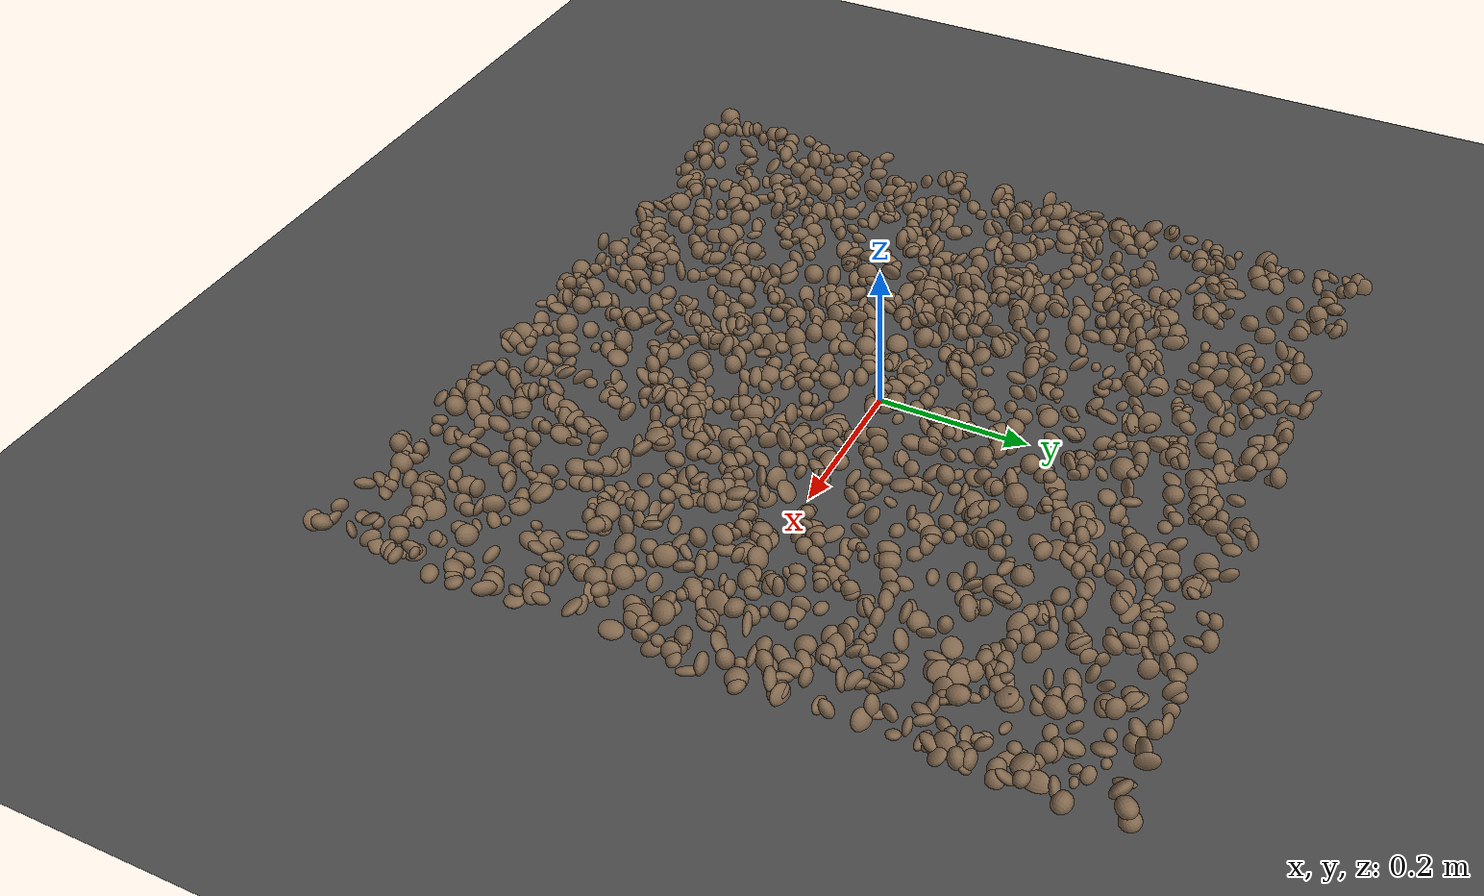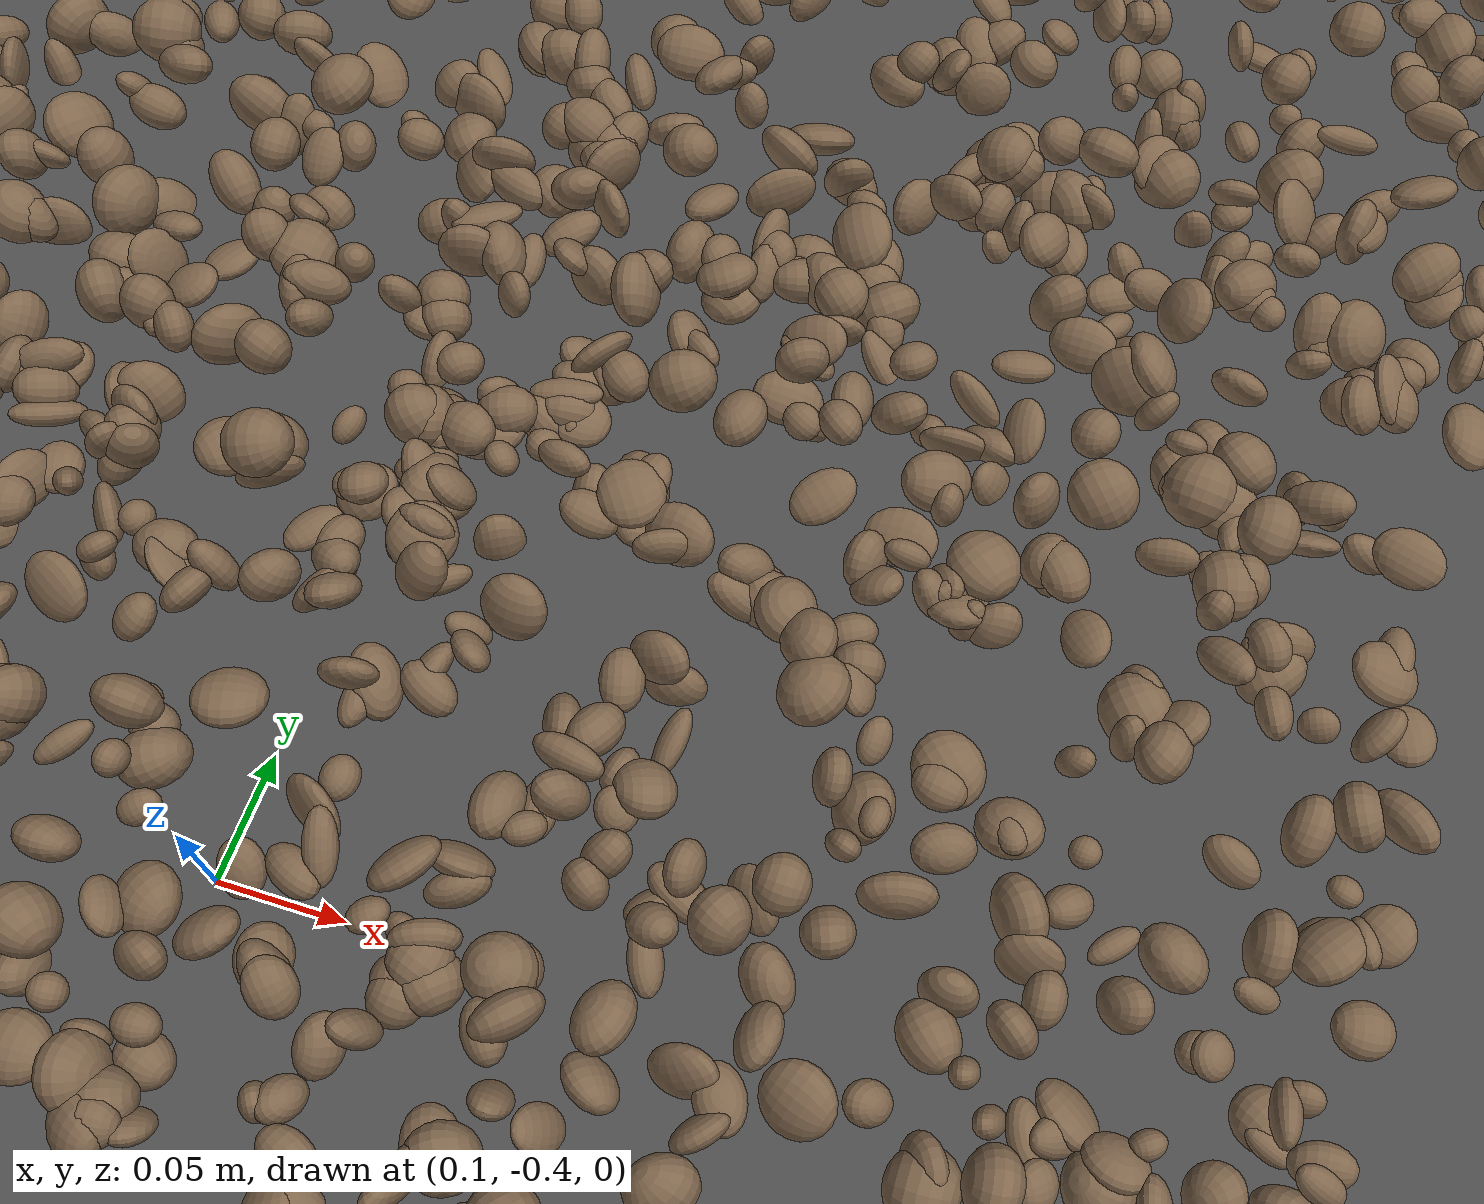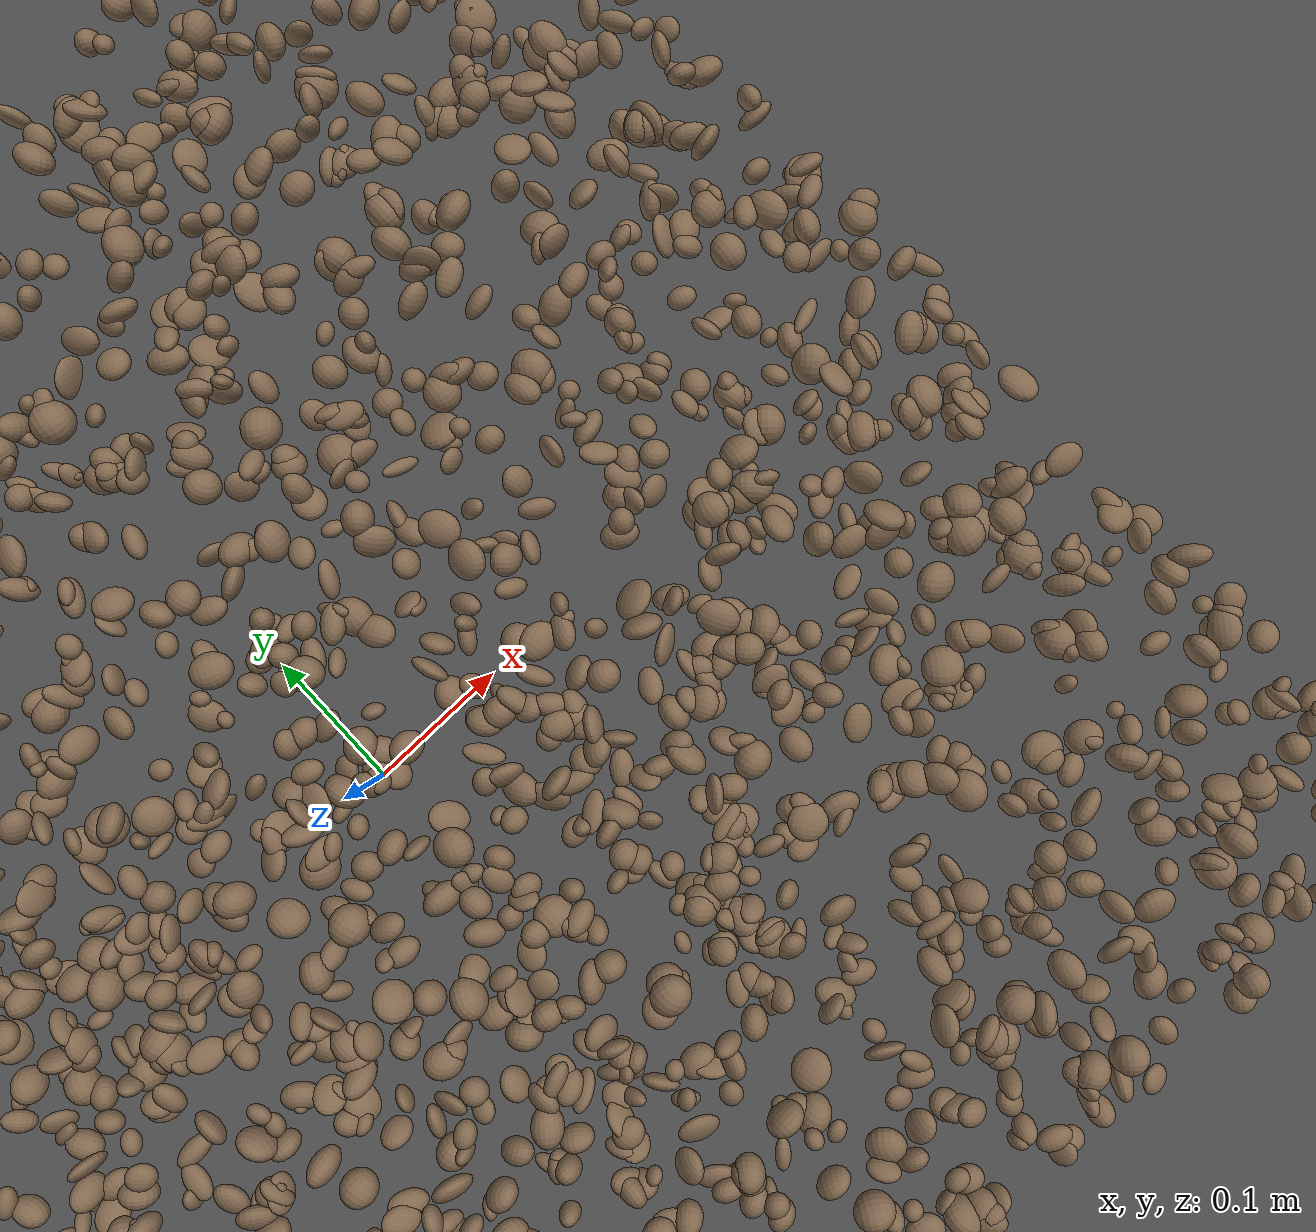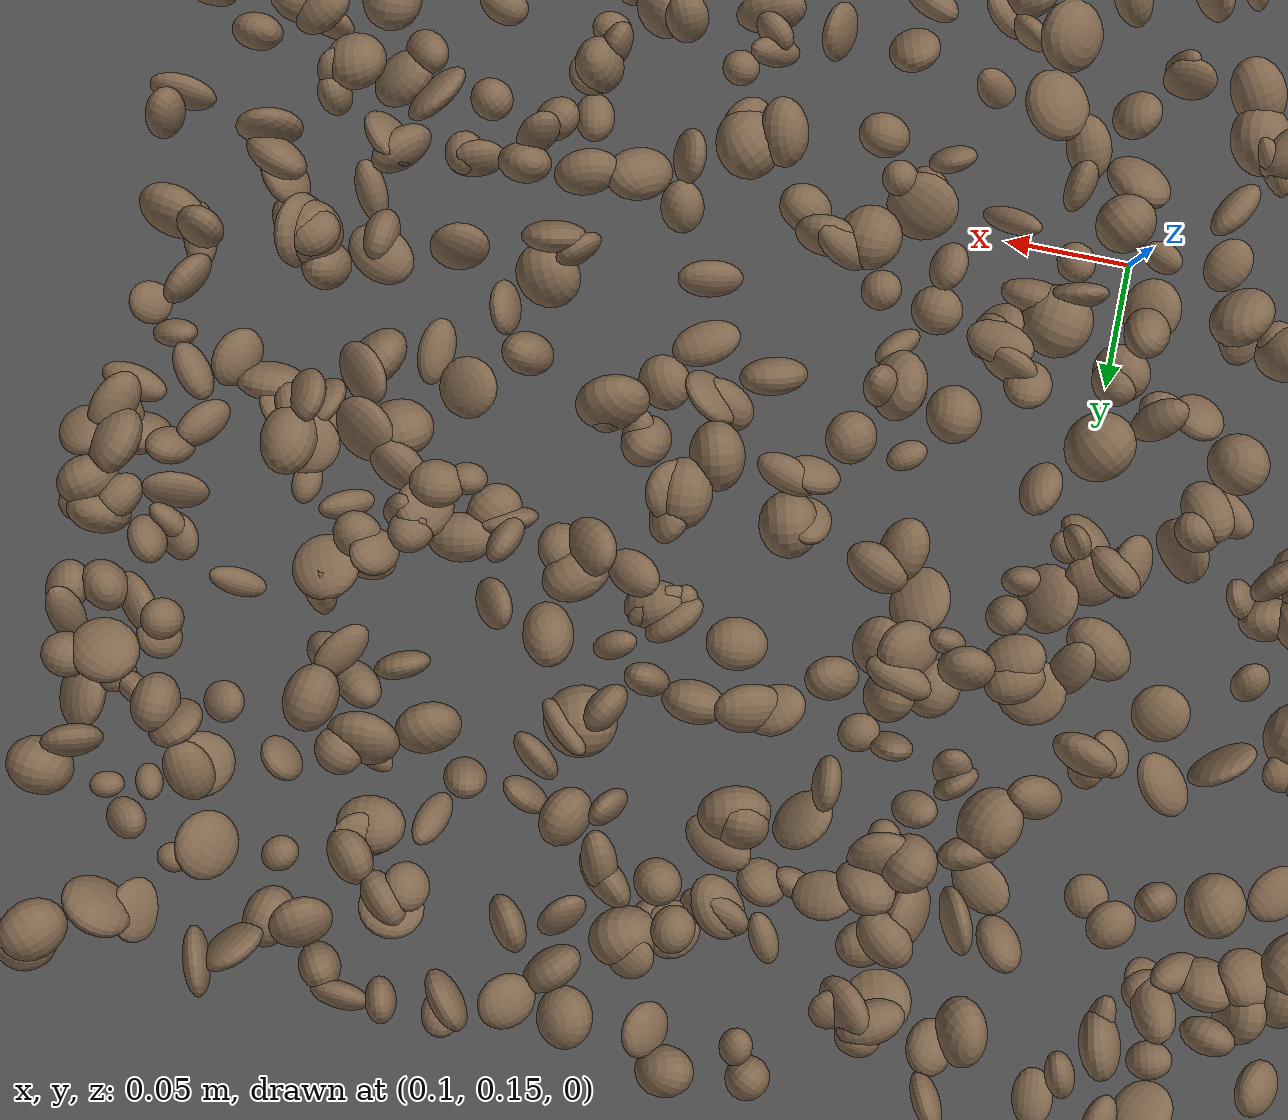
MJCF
<mujoco model="rocky_terrain_scene">
    <compiler angle="radian" inertiafromgeom="true" />
    <option timestep="0.002" gravity="0 0 -9.81" />

    <worldbody>
        <light name="sunlight" pos="5 5 5" dir="-1 -1 -1" diffuse="1 1 1" specular="0.5 0.5 0.5" ambient="0.5 0.5 0.5" />

        <geom name="ground_plane" type="plane" size="50 50 0.1" rgba="0.3 0.3 0.3 1" />

        <body name="rocky_terrain_body">

        <geom name="rock1" type="ellipsoid" size="0.011832715968631037 0.011407021579273334 0.005621739441137769" pos="-0.0013881280380038108 -0.38401414618041974 0.0008114537024996371" quat="0.31972782888388507 0.3803564333552637 0.20268535975995466 0.09723037800089657" rgba="0.5 0.4 0.3 1" /><geom name="rock2" type="ellipsoid" size="0.008362851638374672 0.0068289436054579265 0.010661200437548465" pos="0.02744995879164125 -0.3159881906370601 0.0036912194484306003" quat="0.24384970242913545 0.05710620074090664 0.23957080140566042 0.4594732954242975" rgba="0.5 0.4 0.3 1" /><geom name="rock3" type="ellipsoid" size="0.007057397863921936 0.014157111049560283 0.012781304122318489" pos="-0.47453589772940596 -0.03144743088388091 0.013794277625347759" quat="0.32363969982980234 0.24852870504940708 0.22436649286149926 0.20346510225929137" rgba="0.5 0.4 0.3 1" /><geom name="rock4" type="ellipsoid" size="0.014496194927833644 0.008707502052708488 0.014149980556838731" pos="-0.22450976338789796 -0.12420707142158494 0.013519215655930526" quat="0.05755617048928348 0.37538596205505925 0.5494563986386508 0.017601468817006513" rgba="0.5 0.4 0.3 1" /><geom name="rock5" type="ellipsoid" size="0.013918742162319087 0.005035359067401271 0.0067703874899477665" pos="0.23785747298645254 -0.30450494303792697 0.007917296492365338" quat="0.3856885530974576 0.20971813369839967 0.032170778301373854 0.3724225349027689" rgba="0.5 0.4 0.3 1" /><geom name="rock6" type="ellipsoid" size="0.010184192052628958 0.009181091037544335 0.009791424977959581" pos="-0.4814606808223165 0.08484477756267561 0.006264955568298161" quat="0.2371856244440989 0.054143561462437116 0.3345489306910667 0.3741218834023972" rgba="0.5 0.4 0.3 1" /><geom name="rock7" type="ellipsoid" size="0.008828210207495895 0.0051050283913532495 0.009816720838892725" pos="0.07305200217522345 0.3430290511313433 0.01171797758014377" quat="0.35533910216836206 0.3563324094983029 0.007875232619538416 0.2804532557137966" rgba="0.5 0.4 0.3 1" /><geom name="rock8" type="ellipsoid" size="0.014316920922436888 0.008275165729502189 0.01355766512843223" pos="0.12064460960972712 -0.2561652886362151 0.012550418725114386" quat="0.1626823148565147 0.4008155989171912 0.20544513504211004 0.23105695118418398" rgba="0.5 0.4 0.3 1" /><geom name="rock9" type="ellipsoid" size="0.010761796103074874 0.0064742240748186805 0.013609687563598882" pos="-0.18915935685027252 -0.2270885604563433 0.01303432173832573" quat="0.2465955452073485 0.415600987765542 0.21302497638470033 0.1247784906424092" rgba="0.5 0.4 0.3 1" /><geom name="rock10" type="ellipsoid" size="0.009188547163769593 0.009735640931699683 0.010617983257796164" pos="0.2384091760804109 0.4267377300107026 0.008022996741599037" quat="0.092110352670958 0.5511310561366438 0.32024628374700326 0.036512307445394895" rgba="0.5 0.4 0.3 1" /><geom name="rock11" type="ellipsoid" size="0.005655469379428082 0.013602170547194481 0.005945100181138197" pos="-0.31918088927039123 -0.03301062097763463 0.00395724712436358" quat="0.21964750183155363 0.39964635510359847 0.36281083633422323 0.017895306730624665" rgba="0.5 0.4 0.3 1" /><geom name="rock12" type="ellipsoid" size="0.0078943880880591 0.011653057978650806 0.006731817424332924" pos="-0.006200691850112405 -0.35974180493934826 0.00020567634970443003" quat="0.10615529915824144 0.21149669745307031 0.4271003058785352 0.255247697510153" rgba="0.5 0.4 0.3 1" /><geom name="rock13" type="ellipsoid" size="0.009694635039254485 0.013346651153226016 0.01451974847447128" pos="0.15080076329081982 -0.18385128451923805 0.0016762664685449529" quat="0.11532594710668265 0.3078871956417674 0.34517790311477015 0.23160895413677982" rgba="0.5 0.4 0.3 1" /><geom name="rock14" type="ellipsoid" size="0.009046721816228094 0.011358465924878224 0.009871523740138426" pos="0.006640437631017182 -0.14734888489491849 0.013236367324111351" quat="0.3312993733800215 0.08519961586636689 0.29703942220702134 0.28646158854659026" rgba="0.5 0.4 0.3 1" /><geom name="rock15" type="ellipsoid" size="0.009794000818439444 0.006893201002601629 0.013578909370210265" pos="0.411757715200048 -0.4854955219958633 0.01330954077952349" quat="0.3319666225159556 0.27341868245461554 0.031789727544236354 0.3628249674851925" rgba="0.5 0.4 0.3 1" /><geom name="rock16" type="ellipsoid" size="0.008530405281462339 0.012378467519329563 0.011945758773371694" pos="-0.2167503462415985 -0.13792683839942976 0.003247014592199176" quat="0.15212929656848123 0.36276258855464266 0.266742045883477 0.21836606899339914" rgba="0.5 0.4 0.3 1" /><geom name="rock17" type="ellipsoid" size="0.005311417686161193 0.006293547192295555 0.01051635200386997" pos="-0.4890010343102509 0.1577546722532005 2.9139516753118876e-05" quat="0.5474694138259328 0.059266627670795255 0.19565162584325022 0.1976123326600218" rgba="0.5 0.4 0.3 1" /><geom name="rock18" type="ellipsoid" size="0.005406477575198159 0.007327219808087852 0.011772123810624945" pos="-0.29800622304476465 0.12809996979445415 0.008330111850775989" quat="0.1714758306481238 0.08950891511166015 0.5558520149562695 0.18316323928394665" rgba="0.5 0.4 0.3 1" /><geom name="rock19" type="ellipsoid" size="0.007383683670473103 0.014311496745265221 0.014499081956596903" pos="-0.08606026463559646 0.06761989580888195 0.01072702027019994" quat="0.2025403885415625 0.23971698696837426 0.09003838989925902 0.4677042345908043" rgba="0.5 0.4 0.3 1" /><geom name="rock20" type="ellipsoid" size="0.00826242665880616 0.010079703246005666 0.01471107679659588" pos="-0.41054264006381036 -0.49112940751101586 0.007642425023414747" quat="0.14405305468127563 0.23205162879629274 0.3127385145524583 0.3111568019699733" rgba="0.5 0.4 0.3 1" /><geom name="rock21" type="ellipsoid" size="0.009044937724543473 0.012348617651971419 0.006971836298663151" pos="0.11227249077662216 -0.25444442585506843 0.005519655057426703" quat="0.34783953692109215 0.22270697904269415 0.2989246479170293 0.1305288361191844" rgba="0.5 0.4 0.3 1" /><geom name="rock22" type="ellipsoid" size="0.006248917195535138 0.014909558080864478 0.010909342031465017" pos="0.28254572225141383 -0.41606957261123856 0.01443441559201945" quat="0.24261456361397396 0.3776231159253021 0.3490597293014546 0.030702591159269328" rgba="0.5 0.4 0.3 1" /><geom name="rock23" type="ellipsoid" size="0.00817641391804299 0.006089369451237611 0.014600740097746385" pos="0.4082626194863982 -0.3966585557327512 0.005899421633041991" quat="0.02598711734487504 0.3787576509700154 0.3647773526034204 0.23047787908168912" rgba="0.5 0.4 0.3 1" /><geom name="rock24" type="ellipsoid" size="0.012107493299010102 0.011069092412222852 0.009947229202913965" pos="-0.27442749648125087 0.008101633041200484 4.314542016207068e-05" quat="0.26686020975462005 0.5098356901108716 0.10736300458224494 0.1159410955522635" rgba="0.5 0.4 0.3 1" /><geom name="rock25" type="ellipsoid" size="0.005584477039056822 0.006151174255101053 0.008449745725863416" pos="0.17362740504914653 0.2425515573926823 0.00904261657176708" quat="0.28179059659399575 0.08006782674324645 0.3364447865781125 0.3016967900846452" rgba="0.5 0.4 0.3 1" /><geom name="rock26" type="ellipsoid" size="0.006034833764421814 0.01036670864304657 0.007930550334679048" pos="0.3056115745471709 -0.18168377216348164 0.009695013094629916" quat="0.001189821714139746 0.026951593615425182 0.4965583073436423 0.47530027732679275" rgba="0.5 0.4 0.3 1" /><geom name="rock27" type="ellipsoid" size="0.009669124261142822 0.012287309044655866 0.007619678971495666" pos="-0.27777850106123325 0.4515165330628117 0.0037277130962663167" quat="0.15744697082726114 0.4080674436217635 0.34737294695172155 0.0871126385992538" rgba="0.5 0.4 0.3 1" /><geom name="rock28" type="ellipsoid" size="0.007192994131428395 0.009044094201535348 0.005505107365467888" pos="0.004918652158736769 -0.296622456082149 0.012064553606868925" quat="0.27824308294211486 0.34713420391457744 0.3553176565507987 0.019305056592509032" rgba="0.5 0.4 0.3 1" /><geom name="rock29" type="ellipsoid" size="0.012059586012923621 0.012864795612971231 0.012085235247299386" pos="-0.38202613501180904 -0.17421785640610987 0.005732363626760301" quat="0.33043817815908183 0.27281550128593623 0.3091598679199135 0.08758645263506842" rgba="0.5 0.4 0.3 1" /><geom name="rock30" type="ellipsoid" size="0.01489020272700662 0.01439589556095116 0.01479471030479268" pos="0.3962595351192977 -0.14506322986487996 0.007263605190481448" quat="0.060478025875158825 0.0051692197146386435 0.3570270503925168 0.5773257040176858" rgba="0.5 0.4 0.3 1" /><geom name="rock31" type="ellipsoid" size="0.014505227754576216 0.008105649218319792 0.011398198420907928" pos="-0.31254664263027343 -0.35288322713555875 0.011438796090769" quat="0.25608388058997605 0.2910681074348632 0.3219872811433824 0.13086073083177832" rgba="0.5 0.4 0.3 1" /><geom name="rock32" type="ellipsoid" size="0.010097430645159418 0.005074783576921828 0.006349916652633765" pos="-0.1507820819085397 0.31367792859836163 0.012205527091798275" quat="0.3718590033633303 0.0706082938803046 0.084377176159516 0.47315552659684923" rgba="0.5 0.4 0.3 1" /><geom name="rock33" type="ellipsoid" size="0.008568560874856482 0.01215923056564187 0.013588519183370017" pos="0.11810389495833695 -0.08469650210859847 0.009108960195022909" quat="0.28520332510523966 0.17017624911680374 0.005747982347890177 0.5388724434300665" rgba="0.5 0.4 0.3 1" /><geom name="rock34" type="ellipsoid" size="0.00676928169347337 0.012564406600679234 0.009277054180002778" pos="0.18332314103061376 -0.37722395050326474 0.003205667353056726" quat="0.013102626286158223 0.32882541900843026 0.5701405702179023 0.08793138448750921" rgba="0.5 0.4 0.3 1" /><geom name="rock35" type="ellipsoid" size="0.009749489366624547 0.009718595315026186 0.011899480624601003" pos="-0.019087377475648926 0.056629195194113136 0.0059159767132538794" quat="0.11040991673494344 0.3393105419741975 0.13468795649487983 0.41559158479597935" rgba="0.5 0.4 0.3 1" /><geom name="rock36" type="ellipsoid" size="0.0077227325284519085 0.0068240851272738275 0.009884873909800737" pos="-0.2652698321376976 -0.3743860438524983 0.012727187882369614" quat="0.3122598446519039 0.16677601261940928 0.2971086946239427 0.2238554481047441" rgba="0.5 0.4 0.3 1" /><geom name="rock37" type="ellipsoid" size="0.012120217485361462 0.010908360658403223 0.007428222786144042" pos="-0.28198549961669006 -0.23464158150892012 0.01444978286310248" quat="0.3305825385188233 0.03795549007553076 0.2970806016225743 0.3343813697830716" rgba="0.5 0.4 0.3 1" /><geom name="rock38" type="ellipsoid" size="0.011136147738824452 0.013664705358209912 0.01255780671274206" pos="0.09956732032992388 -0.482767892564247 0.009242987993948423" quat="0.07398727351961745 0.2983611781163963 0.22283229597803503 0.40481925238595123" rgba="0.5 0.4 0.3 1" /><geom name="rock39" type="ellipsoid" size="0.005952373956684928 0.007260138464461647 0.01189994635356272" pos="0.15820561302890512 -0.007686304487763973 0.0075329368983574315" quat="0.28519439710312516 0.17589721916056814 0.22014917809950185 0.3187592056368048" rgba="0.5 0.4 0.3 1" /><geom name="rock40" type="ellipsoid" size="0.006366843508508177 0.008716834047300198 0.005501549868678065" pos="0.36458056493293356 -0.3024234747774204 0.013501556002661941" quat="0.04583402386657929 0.718112549235555 0.2073877981555432 0.028665628742322532" rgba="0.5 0.4 0.3 1" /><geom name="rock41" type="ellipsoid" size="0.01256114438272804 0.013558052608217824 0.010135489667805841" pos="-0.17201629734331125 -0.2637720233748828 0.0011387693348328491" quat="0.07574719890771496 0.011302961815609443 0.46327018598004344 0.44967965329663206" rgba="0.5 0.4 0.3 1" /><geom name="rock42" type="ellipsoid" size="0.012815824194429393 0.014495708560966596 0.013154952988959148" pos="-0.4944653104750457 -0.030641189825006854 0.00784304635557496" quat="0.5039250045569684 0.2132155176523545 0.16770597054433453 0.11515350724634248" rgba="0.5 0.4 0.3 1" /><geom name="rock43" type="ellipsoid" size="0.011735810982607592 0.005877382446773421 0.006099961955619293" pos="0.269308297758728 -0.02619629813252322 0.00676585339318683" quat="0.5015916347630749 0.13640169115792006 0.07273650334000532 0.2892701707389998" rgba="0.5 0.4 0.3 1" /><geom name="rock44" type="ellipsoid" size="0.00751992964729832 0.005423416000640946 0.013500561361490148" pos="-0.11494684602268002 0.4581783069198284 0.006144137229496664" quat="0.1767967673925258 0.2815361109629747 0.2784159054472483 0.26325121619725117" rgba="0.5 0.4 0.3 1" /><geom name="rock45" type="ellipsoid" size="0.008350009355070239 0.00780854721430623 0.014462444189819332" pos="-0.07247729697968319 0.2291149567818641 0.004148911778728182" quat="0.16234856388759422 0.02147165407211082 0.4359751183122578 0.38020466372803713" rgba="0.5 0.4 0.3 1" /><geom name="rock46" type="ellipsoid" size="0.009071331648088564 0.009995639764419396 0.007823200337109917" pos="-0.308685548613727 0.2418441342454486 0.009912824823258502" quat="0.09123159495328838 0.3000742964659206 0.3452141437065047 0.2634799648742863" rgba="0.5 0.4 0.3 1" /><geom name="rock47" type="ellipsoid" size="0.014349087474853809 0.011693896253504997 0.009548435882328198" pos="0.2497211176963564 -0.4060638035874943 0.008540400778746068" quat="0.18113978203236014 0.36031106704123217 0.3941364643271162 0.06441268659929142" rgba="0.5 0.4 0.3 1" /><geom name="rock48" type="ellipsoid" size="0.00769897444119667 0.013084973573846168 0.008759641844072772" pos="-0.28763078214861837 0.23772054742236925 0.002609998300742356" quat="0.37774752652905697 0.378208385935963 0.21135742319521464 0.032686664339765366" rgba="0.5 0.4 0.3 1" /><geom name="rock49" type="ellipsoid" size="0.005647380714627381 0.010867195984795797 0.005376634156454454" pos="0.4610632926075723 -0.32968569292081484 0.0017581142889763722" quat="0.3784576658606788 0.19681257519359766 0.07501863728342971 0.3497111216622939" rgba="0.5 0.4 0.3 1" /><geom name="rock50" type="ellipsoid" size="0.005952900505056074 0.006971405540765469 0.0065421678584247096" pos="0.35110628330537774 -0.4728203116226273 0.012681795625512526" quat="0.25126318229430505 0.33517537887127624 0.4012243697187685 0.012337069115650141" rgba="0.5 0.4 0.3 1" /><geom name="rock51" type="ellipsoid" size="0.013269220184433491 0.012925252640153748 0.010950000653692931" pos="0.10203916957121406 -0.20666446659393356 0.01210715611810008" quat="0.27018802267066205 0.12946453416071407 0.4036661955689189 0.1966812475997049" rgba="0.5 0.4 0.3 1" /><geom name="rock52" type="ellipsoid" size="0.007309498634569388 0.007960377501803971 0.014184281207971591" pos="0.47562097837087325 0.09256818422236623 0.011070433800312961" quat="0.07471158254445176 0.3389674956590555 0.3078145684369575 0.2785063533595352" rgba="0.5 0.4 0.3 1" /><geom name="rock53" type="ellipsoid" size="0.007124885650019679 0.014303531798261885 0.014339243948365651" pos="0.18597658982592213 0.14352196632225267 0.005723905940586501" quat="0.22019122570698682 0.35991757812125846 0.021109363456002596 0.39878183271575207" rgba="0.5 0.4 0.3 1" /><geom name="rock54" type="ellipsoid" size="0.008270223062930035 0.010353117708272769 0.006664595247448434" pos="0.44943485121624827 0.44221810207329293 0.006796000529980305" quat="0.3448451268987725 0.08246870025857671 0.22607275436333177 0.34661341847931904" rgba="0.5 0.4 0.3 1" /><geom name="rock55" type="ellipsoid" size="0.007074659328375374 0.009084337514317026 0.011782387178353098" pos="0.46382107164215336 -0.06339197000792585 0.006565100595858256" quat="0.43452331511210646 0.20713696241730048 0.3467781407563231 0.011561581714270023" rgba="0.5 0.4 0.3 1" /><geom name="rock56" type="ellipsoid" size="0.00792126415745132 0.0070812245777234755 0.005841291359154495" pos="-0.4225996777591371 0.034096585164436366 0.006362448305683193" quat="0.14018410408925217 0.2630889322349715 0.30096843500083076 0.2957585286749456" rgba="0.5 0.4 0.3 1" /><geom name="rock57" type="ellipsoid" size="0.012100054723970879 0.013319723500141992 0.0075679738679904525" pos="-0.49429524553630944 -0.12297060868342813 0.006890911453353132" quat="0.48125224758331914 0.11005432878438866 0.06684489560236645 0.34184852802992566" rgba="0.5 0.4 0.3 1" /><geom name="rock58" type="ellipsoid" size="0.011488462212316444 0.005622796808996938 0.005499636513427714" pos="0.34628428319539706 -0.08477988940146142 0.009042498974020896" quat="0.45298542114650026 0.13683697781265436 0.19522203171333188 0.21495556932751342" rgba="0.5 0.4 0.3 1" /><geom name="rock59" type="ellipsoid" size="0.011716855625964445 0.00950747430979863 0.00524468992151918" pos="0.2943805859542932 -0.4329036967379838 0.0135087421328112" quat="0.24554925710090011 0.4596555319467082 0.12094868800898319 0.17384652294340847" rgba="0.5 0.4 0.3 1" /><geom name="rock60" type="ellipsoid" size="0.005114191647263302 0.011954353858844392 0.010409472772237693" pos="-0.2202126612743196 0.2903368023470755 0.007353572773739094" quat="0.35914527502777044 0.27777927535153446 0.043017036256294376 0.3200584133644007" rgba="0.5 0.4 0.3 1" /><geom name="rock61" type="ellipsoid" size="0.008690976491344836 0.005368562563796566 0.009001829462367083" pos="0.4808957602567593 0.2394097793497426 0.0008755694565018684" quat="0.29212163515387446 0.21254118223838359 0.1794023957389479 0.315934786868794" rgba="0.5 0.4 0.3 1" /><geom name="rock62" type="ellipsoid" size="0.013502044911319854 0.014078123132812946 0.006457252312292214" pos="0.12789758107974136 -0.07119937055445502 0.010369802686626711" quat="0.26150337480254837 0.3686004422071557 0.060365663143002846 0.309530519847293" rgba="0.5 0.4 0.3 1" /><geom name="rock63" type="ellipsoid" size="0.012956075731480596 0.006314851024880267 0.005372978396872839" pos="-0.01848596032155536 -0.249623484089748 0.012361957206020367" quat="0.20357654525671584 0.0054103646135207125 0.46183764928293397 0.3291754408468294" rgba="0.5 0.4 0.3 1" /><geom name="rock64" type="ellipsoid" size="0.006434568927692709 0.009020581108182072 0.008112399908801412" pos="0.40848904229000127 -0.17660402482080007 0.0035984415262088724" quat="0.36031462218113947 0.07697520349551114 0.28744285241448814 0.2752673219088613" rgba="0.5 0.4 0.3 1" /><geom name="rock65" type="ellipsoid" size="0.01014313709458059 0.014603319563932866 0.012485218380884943" pos="0.24459072308254515 -0.08051636532344797 0.0013226633334289444" quat="0.44099115370229813 0.04352216963694805 0.4137091866785254 0.10177748998222846" rgba="0.5 0.4 0.3 1" /><geom name="rock66" type="ellipsoid" size="0.012721187454816457 0.012605613803377774 0.011100672990953252" pos="0.011904295241832785 0.08416079496481121 0.014350135783631235" quat="0.1920549749634451 0.18922842836417858 0.30719942134281875 0.3115171753295576" rgba="0.5 0.4 0.3 1" /><geom name="rock67" type="ellipsoid" size="0.012030900832656215 0.011815048371292047 0.01201304373566723" pos="-0.49677594878627307 -0.41075655780340947 0.0064562574752739695" quat="0.23189125544471362 0.36259815438795456 0.2794033771456106 0.1261072130217213" rgba="0.5 0.4 0.3 1" /><geom name="rock68" type="ellipsoid" size="0.00595581810086985 0.006179125696801888 0.011321427874023755" pos="-0.17369399117989348 0.24482264003942245 0.003031891969018317" quat="0.30165029257588866 0.26873555010984496 0.23799034827942414 0.1916238090348422" rgba="0.5 0.4 0.3 1" /><geom name="rock69" type="ellipsoid" size="0.005834415074155186 0.009303857174406386 0.009972867658238311" pos="-0.12219334055600972 -0.45896794139084285 0.0007613247113137083" quat="0.16993919157988077 0.29511799504130787 0.2979589306069984 0.23698388277181298" rgba="0.5 0.4 0.3 1" /><geom name="rock70" type="ellipsoid" size="0.008698467503061545 0.008589566107814988 0.0067000904445210585" pos="-0.3741663564581449 0.21195371761934845 0.014367898276251395" quat="0.23049410433712994 0.4239926448118488 0.32513874158498335 0.02037450926603793" rgba="0.5 0.4 0.3 1" /><geom name="rock71" type="ellipsoid" size="0.013727749745987141 0.009451618448582364 0.011450710016645296" pos="-0.31341357553438043 -0.44624118113050826 0.012030208686001497" quat="0.23135288294702622 0.37584655914697446 0.22988509640723223 0.16291546149876704" rgba="0.5 0.4 0.3 1" /><geom name="rock72" type="ellipsoid" size="0.013171844434877886 0.014384992951607747 0.009694468006455893" pos="0.0028210785003003336 0.43319549931239276 0.005126690165018415" quat="0.25541568926172886 0.22254934982827992 0.21079873320312678 0.3112362277068645" rgba="0.5 0.4 0.3 1" /><geom name="rock73" type="ellipsoid" size="0.01255497945522762 0.009806226042953968 0.009776233149021978" pos="-0.35437615474856465 -0.11212824225095519 0.003932043033805769" quat="0.31174275347271696 0.18428086174012853 0.2449944215722745 0.25898196321488" rgba="0.5 0.4 0.3 1" /><geom name="rock74" type="ellipsoid" size="0.009019665050863055 0.010737090730274916 0.00537188678537136" pos="-0.4975682726587496 0.456285462061893 0.001584007897220568" quat="0.21475790769145933 0.41438261064735765 0.23240080940500016 0.13845867225618283" rgba="0.5 0.4 0.3 1" /><geom name="rock75" type="ellipsoid" size="0.009497921441158136 0.01029306137231592 0.006359886424619812" pos="-0.4105255011479161 0.22039907296909333 0.004983230081163017" quat="0.3038464949056404 0.2474121526617709 0.133725698481636 0.3150156539509526" rgba="0.5 0.4 0.3 1" /><geom name="rock76" type="ellipsoid" size="0.009479580072229245 0.01268407512461418 0.006500011769862429" pos="-0.07578749401635476 0.47055187900080764 0.013536799686114313" quat="0.3567090399448311 0.13579927359359703 0.00638719083572601 0.5011044956258458" rgba="0.5 0.4 0.3 1" /><geom name="rock77" type="ellipsoid" size="0.014017133975509508 0.00987059504840534 0.009457035175826434" pos="-0.36905511451636963 0.44778295470352014 0.0037268379263029707" quat="0.4321480099091228 0.2698260909316296 0.13224921756528038 0.16577668159396722" rgba="0.5 0.4 0.3 1" /><geom name="rock78" type="ellipsoid" size="0.00622034999631795 0.005854013492404262 0.008621076768745876" pos="-0.2660160816039919 0.34453901633491446 0.011510080180444436" quat="0.26530420188784326 0.20319262521549045 0.28077271515004215 0.25073045774662417" rgba="0.5 0.4 0.3 1" /><geom name="rock79" type="ellipsoid" size="0.01074220437456732 0.011425233670174947 0.005733907972984157" pos="-0.3753377167176166 0.05712892084183274 0.0003369548859883781" quat="0.29418011415360945 0.165507389296879 0.1131072123511504 0.42720528419836123" rgba="0.5 0.4 0.3 1" /><geom name="rock80" type="ellipsoid" size="0.0068607583592513195 0.014005403368473422 0.010793515779657557" pos="0.22343266297744369 -0.27645200726627916 0.013490852862370133" quat="0.22783599155506168 0.4382246550586115 0.3317984191455661 0.002140934240760678" rgba="0.5 0.4 0.3 1" /><geom name="rock81" type="ellipsoid" size="0.00876968119516849 0.010378989702355661 0.012632316426997619" pos="0.27978486374244915 -0.04185129991003944 0.006634791031708243" quat="0.05818129265924903 0.14259546056543684 0.43983315704542986 0.35939008972988423" rgba="0.5 0.4 0.3 1" /><geom name="rock82" type="ellipsoid" size="0.010736567445161254 0.013613918678462674 0.013229943790192288" pos="0.2864519471219029 -0.45207034766510146 0.00013870597910905225" quat="0.17455411219435749 0.2691935600711809 0.4886505318878911 0.06760179584657053" rgba="0.5 0.4 0.3 1" /><geom name="rock83" type="ellipsoid" size="0.009305211794665286 0.012942635495817496 0.007266334921460118" pos="0.297000254743214 -0.42093968925292 0.013236394213769787" quat="0.7168945140379485 0.04793111597105664 0.03853870168413999 0.19663566830685486" rgba="0.5 0.4 0.3 1" /><geom name="rock84" type="ellipsoid" size="0.005467539197973902 0.008605201731971825 0.008098518724170507" pos="0.023884405582921153 0.036098196888836864 0.0003816482005485111" quat="0.17018928727129226 0.41757796949036485 0.24851783453004697 0.1637149087082959" rgba="0.5 0.4 0.3 1" /><geom name="rock85" type="ellipsoid" size="0.009884543205678864 0.014642255770902106 0.012753268041130538" pos="0.10939506042919878 0.46216025934178984 0.00585581957169038" quat="0.12574259595048326 0.6715417081603656 0.07564674312901966 0.12706895276013153" rgba="0.5 0.4 0.3 1" /><geom name="rock86" type="ellipsoid" size="0.006108577413603512 0.01083406995928501 0.009025924660078972" pos="0.42485905376646915 -0.07353972403375764 0.0029631398313766143" quat="0.14458038304193113 0.24907807450186822 0.25387401860927045 0.35246752384693025" rgba="0.5 0.4 0.3 1" /><geom name="rock87" type="ellipsoid" size="0.005775686044317878 0.013417777692231937 0.008670581696862557" pos="0.20164001103026985 -0.47967586835460085 0.005868050679878014" quat="0.1313879409058811 0.08230380144843694 0.20200170471788548 0.5843065529277965" rgba="0.5 0.4 0.3 1" /><geom name="rock88" type="ellipsoid" size="0.0067589830722581444 0.007150962601055445 0.011243272316777042" pos="-0.4713433165436005 0.18336902413413747 0.005292246724623853" quat="0.046728516719176036 0.29704736131325404 0.5065069286534548 0.14971719331411518" rgba="0.5 0.4 0.3 1" /><geom name="rock89" type="ellipsoid" size="0.008185238148778981 0.01473865593238613 0.0076897078513949516" pos="-0.3060488147694035 -0.3065535069748597 0.013939021526038391" quat="0.4613449289860073 0.2934269336128927 0.1370489668050744 0.10817917059602569" rgba="0.5 0.4 0.3 1" /><geom name="rock90" type="ellipsoid" size="0.012672534330620057 0.006136034417811784 0.01422195427050595" pos="-0.18982663361204943 -0.361684028723425 0.0012161195709133666" quat="0.18989660854662285 0.3877724242624864 0.1072899113133574 0.3150410558775333" rgba="0.5 0.4 0.3 1" /><geom name="rock91" type="ellipsoid" size="0.005393199475395612 0.01316697203833312 0.007213281321318883" pos="-0.12739026135214648 -0.22256849600390338 0.01221625413417627" quat="0.2116014178345572 0.1781913318294126 0.30243156387447906 0.30777568646155123" rgba="0.5 0.4 0.3 1" /><geom name="rock92" type="ellipsoid" size="0.009742898644044668 0.009503626414136069 0.011772001504279562" pos="-0.2399699659179937 -0.15418484639264962 0.0123241646964145" quat="0.3659650796446371 0.1933350996796239 0.22155241242260992 0.2191474082531291" rgba="0.5 0.4 0.3 1" /><geom name="rock93" type="ellipsoid" size="0.00567338821533618 0.010506762371312886 0.008611073936359993" pos="0.1129768921168891 -0.14328979911196316 0.011983533527775685" quat="0.37511256836008927 0.3358099377431418 0.2088022303414575 0.08027526355531138" rgba="0.5 0.4 0.3 1" /><geom name="rock94" type="ellipsoid" size="0.01019566914904673 0.013929826320800514 0.012191660305839697" pos="0.23028349655455393 -0.09738808225065942 0.006052996938970504" quat="0.55825025894424 0.05233740629127618 0.11074857744667854 0.2786637573178053" rgba="0.5 0.4 0.3 1" /><geom name="rock95" type="ellipsoid" size="0.007486920216160608 0.014356912211987944 0.008552385045051465" pos="-0.24746719632387648 0.25321594282441107 0.005893009359066304" quat="0.5209649022129941 0.34706661550855267 0.04295351563639409 0.08901496664205923" rgba="0.5 0.4 0.3 1" /><geom name="rock96" type="ellipsoid" size="0.011681925950404053 0.010472516683274152 0.01119149339359818" pos="0.10752300879772547 -0.08550710885367141 0.003705147109681491" quat="0.22705453672449827 0.34061632944090264 0.3589040154895832 0.0734251183450159" rgba="0.5 0.4 0.3 1" /><geom name="rock97" type="ellipsoid" size="0.014696703882403819 0.006349803211267322 0.009041610412782234" pos="0.3431161981309506 -0.0631243319795638 0.0007306556999631303" quat="0.3207751166095964 0.444204479320042 0.20835209052423698 0.026668313546124665" rgba="0.5 0.4 0.3 1" /><geom name="rock98" type="ellipsoid" size="0.01294834074946771 0.010927520796406718 0.010228870490801047" pos="0.40852738141950407 -0.255704188525661 0.010990829699858694" quat="0.26356281099668133 0.280078792661316 0.3513123652755375 0.10504603106646518" rgba="0.5 0.4 0.3 1" /><geom name="rock99" type="ellipsoid" size="0.007485875769892644 0.011113137258770582 0.012578515409431829" pos="-0.0020130047857432887 0.4288266087042073 0.0020139508624608536" quat="0.35451175964436743 0.16752695900279926 0.18754612211236135 0.29041515924047195" rgba="0.5 0.4 0.3 1" /><geom name="rock100" type="ellipsoid" size="0.007817064875530017 0.00564355250864716 0.009883171295457517" pos="-0.4808802984811278 0.12674557842615286 0.0056618404308391825" quat="0.04321430169646147 0.23245103009928705 0.3542476469490454 0.370087021255206" rgba="0.5 0.4 0.3 1" /><geom name="rock101" type="ellipsoid" size="0.00822179902045327 0.012732522932864018 0.006666128343576226" pos="0.3440256960442858 -0.052617170055025086 0.005323735087541139" quat="0.2866528414873794 0.14149531242591576 0.24820664655470806 0.3236451995319967" rgba="0.5 0.4 0.3 1" /><geom name="rock102" type="ellipsoid" size="0.014401652471263307 0.008732755597845856 0.014235439810411876" pos="-0.2822733493683949 0.06519902356201712 0.010027952140425508" quat="0.3193812724210056 0.17054955752217876 0.10940054534629615 0.40066862471051945" rgba="0.5 0.4 0.3 1" /><geom name="rock103" type="ellipsoid" size="0.011317247987809847 0.010507770667076631 0.0053290132318441815" pos="0.2807154504938657 0.14168238160513857 0.006230020009000081" quat="0.3570037321816008 0.1293575239393229 0.25726221115169173 0.25637653272738453" rgba="0.5 0.4 0.3 1" /><geom name="rock104" type="ellipsoid" size="0.009457520017074728 0.012712703848565576 0.006598286768200151" pos="-0.32609487220197175 0.2132070495864936 0.01029232915425282" quat="0.49692765814158096 0.08237031168216336 0.24199382016252632 0.17870821001372927" rgba="0.5 0.4 0.3 1" /><geom name="rock105" type="ellipsoid" size="0.008647978672619943 0.008605000205290057 0.010340691360594078" pos="-0.15351836613192316 0.2612409444771502 0.002729145326390069" quat="0.2443801471362773 0.18373575247822171 0.23997887294350506 0.33190522744199585" rgba="0.5 0.4 0.3 1" /><geom name="rock106" type="ellipsoid" size="0.007745146511468296 0.008222855390850506 0.008996479727776513" pos="0.036035455690748175 0.45799433598665595 0.012930317030075964" quat="0.19194953064222406 0.24806363875770818 0.30722001789495984 0.2527668127051078" rgba="0.5 0.4 0.3 1" /><geom name="rock107" type="ellipsoid" size="0.008415081468985126 0.010751870357671611 0.008152642889218409" pos="0.05568412301570713 0.25040906525627216 0.012752788420614825" quat="0.08840459909974592 0.35953957574543394 0.37574878894681074 0.17630703620800944" rgba="0.5 0.4 0.3 1" /><geom name="rock108" type="ellipsoid" size="0.006064525440769262 0.007746704546507556 0.011342742319972473" pos="0.45489771578744664 -0.4576193174859796 0.007621564032023025" quat="0.17009408720855212 0.26112256753143204 0.13182929958940562 0.4369540456706103" rgba="0.5 0.4 0.3 1" /><geom name="rock109" type="ellipsoid" size="0.007538038687395003 0.01293242229970153 0.010534508287145455" pos="0.0076459297797397685 -0.004049197071320121 0.0032578513833417875" quat="0.34445870913024546 0.02751662229062256 0.5978816372138016 0.030143031365330388" rgba="0.5 0.4 0.3 1" /><geom name="rock110" type="ellipsoid" size="0.006771715586150782 0.007299143717271316 0.011873478565614349" pos="0.382771517558699 -0.4660835924271879 0.008120474350132403" quat="0.1056287546672796 0.2945588238980439 0.30384318685871153 0.295969234575965" rgba="0.5 0.4 0.3 1" /><geom name="rock111" type="ellipsoid" size="0.013030571305007076 0.01237108428558642 0.006280048761516302" pos="0.14749128157172742 0.18638277851445983 0.0018992647530393857" quat="0.36093557726140035 0.22784951114334334 0.07472462672196192 0.33649028487329435" rgba="0.5 0.4 0.3 1" /><geom name="rock112" type="ellipsoid" size="0.014045656824767362 0.007576999553219771 0.009337620735981982" pos="-0.18120408065442584 -0.222899765387633 0.005270497203014248" quat="0.0514293611560637 0.1916860271804808 0.3502251204297926 0.40665949123366296" rgba="0.5 0.4 0.3 1" /><geom name="rock113" type="ellipsoid" size="0.009388428385272079 0.011941671295947039 0.014730667007836405" pos="-0.20459792647585529 -0.16565652048000268 0.008566049208603797" quat="0.14670245987113423 0.2868710553914131 0.39013260317435666 0.17629388156309592" rgba="0.5 0.4 0.3 1" /><geom name="rock114" type="ellipsoid" size="0.0107860230456405 0.00954897442170351 0.00806454273778923" pos="-0.37692890507066246 0.1385086132051354 0.0006378402622368445" quat="0.4843412853642468 0.0790688017963649 0.32935888335156016 0.10723102948782808" rgba="0.5 0.4 0.3 1" /><geom name="rock115" type="ellipsoid" size="0.005566010905840686 0.01416153405325802 0.009780614575684864" pos="0.13016839964085936 -0.11990390836030151 0.013181333041601002" quat="0.18603450303764107 0.42589322723847994 0.15292741433555956 0.23514485538831933" rgba="0.5 0.4 0.3 1" /><geom name="rock116" type="ellipsoid" size="0.012742056195188487 0.007192011792222976 0.010181552408871045" pos="0.10781766053908937 -0.22402773630342965 0.006368827509789651" quat="0.5490338632211264 0.13436276275465625 0.13453909823905044 0.18206427578516693" rgba="0.5 0.4 0.3 1" /><geom name="rock117" type="ellipsoid" size="0.008356808279711308 0.00625079433599286 0.014783493228700664" pos="0.4041911642731518 -0.4645078173989794 0.0008443281335762709" quat="0.2952924881761704 0.045792437966189974 0.34364942407659405 0.31526564978104554" rgba="0.5 0.4 0.3 1" /><geom name="rock118" type="ellipsoid" size="0.005305508960515587 0.006457257608514894 0.006637132047792295" pos="0.4812589883917703 -0.28756661843451226 0.011549272062258836" quat="0.14941510272614614 0.4117462690385252 0.13677959507071422 0.30205903316461447" rgba="0.5 0.4 0.3 1" /><geom name="rock119" type="ellipsoid" size="0.009295454864183265 0.012577811510841955 0.014471841500634592" pos="-0.36720077727387523 0.40943131783044295 0.013678582009688535" quat="0.1968997384297999 0.07504592407557266 0.27843200197348933 0.4496223355211382" rgba="0.5 0.4 0.3 1" /><geom name="rock120" type="ellipsoid" size="0.008238222688530812 0.013504070354005335 0.014344288271543708" pos="0.2180371813356613 -0.415786913972201 0.010211646191702532" quat="0.08397251564034763 0.1966527158129051 0.38403471990809146 0.3353400486386559" rgba="0.5 0.4 0.3 1" /><geom name="rock121" type="ellipsoid" size="0.012797816898123978 0.012739763318893827 0.01498688921304335" pos="-0.013899012933916821 0.4105845354738994 0.012513562224718227" quat="0.22081923445772333 0.09319387647248674 0.30628332353146503 0.37970356553832474" rgba="0.5 0.4 0.3 1" /><geom name="rock122" type="ellipsoid" size="0.005480341262363075 0.005895600387239269 0.005974351223527562" pos="0.3912678302592738 -0.3001911857511408 0.009537763859196411" quat="0.4513410960632297 0.11318296776365065 0.3860109485694157 0.0494649876037039" rgba="0.5 0.4 0.3 1" /><geom name="rock123" type="ellipsoid" size="0.007883080913429654 0.01075079137162014 0.006476625205326336" pos="-0.036140639107071326 -0.185387934361523 0.008827685706707193" quat="0.26517653778951605 0.1302444496554848 0.25214543726309446 0.3524335752919046" rgba="0.5 0.4 0.3 1" /><geom name="rock124" type="ellipsoid" size="0.012243497052644166 0.011132562926652004 0.013826646396845731" pos="0.4757623410372981 0.49147466164615583 0.01353717483157137" quat="0.27009569812281536 0.05333287313922918 0.3559031637988651 0.32066826493909045" rgba="0.5 0.4 0.3 1" /><geom name="rock125" type="ellipsoid" size="0.006032870143275405 0.011494645023949701 0.01363904568224288" pos="-0.007788004965669337 -0.23879391669052696 0.012626290128853218" quat="0.47634713293559494 0.10399507529975292 0.13510124334699153 0.28455654841766054" rgba="0.5 0.4 0.3 1" /><geom name="rock126" type="ellipsoid" size="0.009366035342767438 0.014951668841943246 0.010998027220176568" pos="-0.16045404701852606 -0.30151485083541973 0.0058458849106415205" quat="0.5898566199300878 0.11966289622630141 0.22353372499892799 0.06694675884468282" rgba="0.5 0.4 0.3 1" /><geom name="rock127" type="ellipsoid" size="0.01344948636199924 0.014473679957964204 0.006699185369916306" pos="-0.2400679909189496 -0.09533053800441416 0.013296342061017456" quat="0.2392116204566175 0.25197608567120006 0.32955436456972675 0.1792579293024556" rgba="0.5 0.4 0.3 1" /><geom name="rock128" type="ellipsoid" size="0.009915215217506814 0.01399976723641265 0.006833027057488167" pos="0.4651900821970345 0.20736393966736077 0.01353362326254339" quat="0.11124136569476241 0.031127672551213143 0.38153939461026554 0.476091567143759" rgba="0.5 0.4 0.3 1" /><geom name="rock129" type="ellipsoid" size="0.010414009742155455 0.006770378335171747 0.009891626884051631" pos="-0.13011465011602064 0.0393597014632443 0.00191648187090735" quat="0.4524153692979605 0.3855879527266579 0.010821700524484317 0.15117497745089725" rgba="0.5 0.4 0.3 1" /><geom name="rock130" type="ellipsoid" size="0.012199695049113467 0.005831080606353753 0.01054894823033735" pos="0.491903342721434 -0.22100509497588827 0.006224422546075829" quat="0.1952046181310144 0.1903639768815662 0.3147291227538957 0.2997022822335237" rgba="0.5 0.4 0.3 1" /><geom name="rock131" type="ellipsoid" size="0.011307808247769405 0.0095016620474894 0.01317826715635723" pos="-0.28263805295522737 -0.030203828636210073 0.0033044164632104766" quat="0.5397384128245711 0.1308586169964056 0.05575926282225539 0.27364370735676785" rgba="0.5 0.4 0.3 1" /><geom name="rock132" type="ellipsoid" size="0.008690538110051015 0.012522243215285953 0.006624307122044537" pos="0.14695030281618382 -0.15691823839301222 0.0009990881391393701" quat="0.24707626798208301 0.14444657456674942 0.19283215447271257 0.4156450029784551" rgba="0.5 0.4 0.3 1" /><geom name="rock133" type="ellipsoid" size="0.010861749336912863 0.013469465986111661 0.007564767795246672" pos="0.38351439684047084 -0.3668443631211148 0.00406897527796562" quat="0.1403510635739332 0.10785586176591855 0.3630886507330569 0.3887044239270914" rgba="0.5 0.4 0.3 1" /><geom name="rock134" type="ellipsoid" size="0.01220564801666994 0.009657450002615229 0.005666391395230536" pos="-0.2585273401978512 -0.15797872673430002 0.0009841951222299965" quat="0.3158041809443491 0.34462459359421777 0.15119740516250846 0.18837382029892472" rgba="0.5 0.4 0.3 1" /><geom name="rock135" type="ellipsoid" size="0.009621285842767925 0.014596016468871417 0.013146021037054294" pos="-0.4655180499632303 0.011984854276550161 0.005676231633744406" quat="0.053683954693644974 0.16089000955220029 0.26225059346112817 0.5231754422930266" rgba="0.5 0.4 0.3 1" /><geom name="rock136" type="ellipsoid" size="0.005241058758205811 0.013684262005762893 0.00889615217947539" pos="0.2633406402702808 0.4013710790623338 0.010922865077934451" quat="0.06577451687892073 0.1582429952982731 0.42210965609321077 0.3538728317295954" rgba="0.5 0.4 0.3 1" /><geom name="rock137" type="ellipsoid" size="0.010804980436794263 0.010762202091530717 0.00805882001326789" pos="0.2850455298923624 -0.04356578041771797 0.010023278826728696" quat="0.29835744055595254 0.27364543255056306 0.19475565805027262 0.23324146884321179" rgba="0.5 0.4 0.3 1" /><geom name="rock138" type="ellipsoid" size="0.012701536697437673 0.008599412000009951 0.006450884621092893" pos="-0.16359628468326792 -0.017727532631012233 0.0059338716455010695" quat="0.16958931651194897 0.3067287852906973 0.2424091496268918 0.28127274857046186" rgba="0.5 0.4 0.3 1" /><geom name="rock139" type="ellipsoid" size="0.010035724475782836 0.008693972953186057 0.013206219835675919" pos="-0.44087369146030286 -0.05653631648513435 0.008418486094040195" quat="0.32170211076797495 0.10506176257525321 0.3242344678663216 0.24900165879045022" rgba="0.5 0.4 0.3 1" /><geom name="rock140" type="ellipsoid" size="0.00927778424447773 0.009297721379063508 0.009929937843663427" pos="-0.051707954809832146 0.30169661395458003 0.005270926856939271" quat="0.32977940238374603 0.16844927298363174 0.35344759734126113 0.14832372729136115" rgba="0.5 0.4 0.3 1" /><geom name="rock141" type="ellipsoid" size="0.008850098050875313 0.00639648408832717 0.012272089855200438" pos="0.0016192878345985262 0.33567939755094256 0.008617045071481231" quat="0.2706097588182728 0.11478330958750071 0.290634394506775 0.32397253708745144" rgba="0.5 0.4 0.3 1" /><geom name="rock142" type="ellipsoid" size="0.00820864483467672 0.013331950526047371 0.013942953846935498" pos="0.09610683337697923 -0.4929855825103201 0.011112751993167932" quat="0.49445087740828136 0.17906738273601733 0.2622943461803521 0.06418739367534922" rgba="0.5 0.4 0.3 1" /><geom name="rock143" type="ellipsoid" size="0.007087205915250744 0.006183880191341272 0.007602249310506017" pos="-0.15829625775673906 0.47675630184790574 0.013366198355944445" quat="0.12207947734141236 0.16985389722431904 0.10146645860988142 0.6066001668243872" rgba="0.5 0.4 0.3 1" /><geom name="rock144" type="ellipsoid" size="0.01046297552731305 0.006085339768061361 0.0128888448293391" pos="-0.34327856662573153 -0.2990277395299664 0.004013085099297032" quat="0.20094760376696902 0.3336411893797894 0.15339663019057506 0.3120145766626665" rgba="0.5 0.4 0.3 1" /><geom name="rock145" type="ellipsoid" size="0.005673500478718104 0.007253061785788801 0.013282608290693738" pos="0.3879567878393523 0.30352966902861045 0.0012792627941792117" quat="0.25667432439907606 0.13146555720863515 0.19604758193996735 0.4158125364523214" rgba="0.5 0.4 0.3 1" /><geom name="rock146" type="ellipsoid" size="0.01354093861055439 0.009319090713813183 0.005688575498847393" pos="0.20229238976901265 -0.08553889324295372 0.009637532734206294" quat="0.24483407505289295 0.29013818702720806 0.147522717856134 0.31750502006376485" rgba="0.5 0.4 0.3 1" /><geom name="rock147" type="ellipsoid" size="0.009689875398445805 0.00941860218650993 0.013445928577354622" pos="-0.199352864603783 -0.30462688468660193 0.012004324121668145" quat="0.20320250272659326 0.47053071867308766 0.11350233362369073 0.21276444497662828" rgba="0.5 0.4 0.3 1" /><geom name="rock148" type="ellipsoid" size="0.013217739151266991 0.010576273919387959 0.014600802188129421" pos="0.21397131967326388 0.3943296693348376 0.011883011774245292" quat="0.4049779410745048 0.048189671185360085 0.3939212419307284 0.15291114580940657" rgba="0.5 0.4 0.3 1" /><geom name="rock149" type="ellipsoid" size="0.0126223281521015 0.008937320218187224 0.005830654831141144" pos="0.323281150578032 0.3052152665660275 0.00918381537774024" quat="0.23123640863839365 0.3638181377823291 0.05219644766623915 0.3527490059130381" rgba="0.5 0.4 0.3 1" /><geom name="rock150" type="ellipsoid" size="0.013948857417067313 0.014157212353026652 0.01090299839027727" pos="0.25613810231947376 -0.09922360452355172 0.0022765489375141767" quat="0.25909157733248844 0.5069610963552877 0.03516553948492993 0.1987817868272939" rgba="0.5 0.4 0.3 1" /><geom name="rock151" type="ellipsoid" size="0.010601888626618393 0.013440853579651316 0.014112335974389219" pos="-0.14751908609219933 -0.2862405560978736 0.004630716529734055" quat="0.3110652841929282 0.16967553478724504 0.42937038801350924 0.08988879300631752" rgba="0.5 0.4 0.3 1" /><geom name="rock152" type="ellipsoid" size="0.008005307002581546 0.013681911220760696 0.014188427267979906" pos="0.07938331638731277 -0.33798638915704204 0.012708606484226618" quat="0.018075088508198497 0.41590114909119974 0.14163355097249997 0.42439021142810185" rgba="0.5 0.4 0.3 1" /><geom name="rock153" type="ellipsoid" size="0.014665717008254815 0.008076879474876163 0.010893014942700698" pos="-0.24392371293205928 0.4382305842208426 0.0049492497536788105" quat="0.16555750906360145 0.35771790368797846 0.13625354045313404 0.3404710467952861" rgba="0.5 0.4 0.3 1" /><geom name="rock154" type="ellipsoid" size="0.009412763218171076 0.006021665155337182 0.005185154655983067" pos="-0.0700056187332947 0.23235757011657965 0.010869276984692113" quat="0.1712481246728807 0.49933692621332454 0.28934641209290707 0.04006853702088769" rgba="0.5 0.4 0.3 1" /><geom name="rock155" type="ellipsoid" size="0.005891879951018948 0.00732984569418353 0.00934079404645256" pos="-0.060605174500931946 -0.486820642073022 0.001825173639287001" quat="0.4628754670081571 0.3191668873530815 0.02796031714137959 0.1899973284973818" rgba="0.5 0.4 0.3 1" /><geom name="rock156" type="ellipsoid" size="0.005493370547964383 0.014005579525782456 0.006752011388039718" pos="-0.44678239316493906 0.2949537006287435 0.010826860019328807" quat="0.3021747714018551 0.2422495817556496 0.37493209288996576 0.08064355395252953" rgba="0.5 0.4 0.3 1" /><geom name="rock157" type="ellipsoid" size="0.005177195729742174 0.010170849818009307 0.013900632956114167" pos="-0.10220593489193419 -0.13720692868894413 0.012267374109419965" quat="0.20824695825522258 0.30260550871648634 0.20041351488247797 0.28873401814581307" rgba="0.5 0.4 0.3 1" /><geom name="rock158" type="ellipsoid" size="0.006599137256346037 0.009792191449862295 0.012104900149596427" pos="0.4435051589396256 -0.09088110584594711 0.010698362709780633" quat="0.4658821570294841 0.06853741148191556 0.28512558231563623 0.1804548491729641" rgba="0.5 0.4 0.3 1" /><geom name="rock159" type="ellipsoid" size="0.0056477240636148875 0.01390478657540737 0.012470426514025445" pos="0.10053575521708791 -0.19803385087023984 0.0071307225886695315" quat="0.16255895568983075 0.3517102382613704 0.10614238584921665 0.3795884201995822" rgba="0.5 0.4 0.3 1" /><geom name="rock160" type="ellipsoid" size="0.007088940380412313 0.00686224936580654 0.006214984995152006" pos="-0.1700069067854999 0.40185455535135195 0.00576973482859842" quat="0.16411512922753155 0.07393904880727781 0.47231606094862866 0.28962976101656207" rgba="0.5 0.4 0.3 1" /><geom name="rock161" type="ellipsoid" size="0.014915635059427876 0.014330491575164223 0.013550551484800815" pos="-0.15956909273981246 0.10043073315133455 0.002305105087310115" quat="0.34395202748678627 0.03311638668395034 0.24345502610789826 0.37947655972136507" rgba="0.5 0.4 0.3 1" /><geom name="rock162" type="ellipsoid" size="0.008146204694241505 0.014321188524120666 0.011769099961965446" pos="0.025758600644439245 -0.1606523688700514 0.005737856205862905" quat="0.8582058104740348 0.044524038146386134 0.01883684342872093 0.07843330795085811" rgba="0.5 0.4 0.3 1" /><geom name="rock163" type="ellipsoid" size="0.010044627161958194 0.008647663489056701 0.01107944363279027" pos="0.35379526603896816 0.289166129842655 0.013667948060736911" quat="0.16237077748980017 0.32633766711175033 0.16337122747809513 0.34792032792035443" rgba="0.5 0.4 0.3 1" /><geom name="rock164" type="ellipsoid" size="0.009068448773410735 0.008600035398846243 0.011415092229819845" pos="-0.4675637430192532 0.4773131590894987 0.005548685574764426" quat="0.34294041121691815 0.16074369647950743 0.16669803248118575 0.32961785982238867" rgba="0.5 0.4 0.3 1" /><geom name="rock165" type="ellipsoid" size="0.012887018750039995 0.008213186803253884 0.00572328942246611" pos="0.3138540052361495 -0.21225455282032024 0.004330668410985497" quat="0.2861361321540404 0.06132605840160294 0.5111862835878662 0.14135152585649044" rgba="0.5 0.4 0.3 1" /><geom name="rock166" type="ellipsoid" size="0.008215139453126843 0.010128949247963169 0.007322609734611893" pos="0.3437097552357792 -0.4053066213976172 0.0028150620875676186" quat="0.3193007958120915 0.20681726320773985 0.11646778604015955 0.35741415494000917" rgba="0.5 0.4 0.3 1" /><geom name="rock167" type="ellipsoid" size="0.011800657524729443 0.005381543563942094 0.005888850584541994" pos="-0.09181604431563273 -0.26739881886476913 0.009427068332215557" quat="0.10961133427582084 0.3394221461693806 0.53872343248928 0.012243087065518583" rgba="0.5 0.4 0.3 1" /><geom name="rock168" type="ellipsoid" size="0.01051684695495061 0.014838255061328853 0.012693985970879743" pos="-0.04517937934541161 -0.19126793948033227 0.011837257939020612" quat="0.33729847347432806 0.4078157347154316 0.1511596790246109 0.10372611278562956" rgba="0.5 0.4 0.3 1" /><geom name="rock169" type="ellipsoid" size="0.008969912851133362 0.01448080074410946 0.007968867006742958" pos="0.09786128738402156 0.3658068317766159 0.0035566965367114147" quat="0.22370899522385468 0.3935691024660933 0.31637016820671054 0.06635173410334143" rgba="0.5 0.4 0.3 1" /><geom name="rock170" type="ellipsoid" size="0.008293664553588855 0.010047527377400285 0.011688479789839407" pos="0.3035099449617663 -0.0052648960374578335 0.01474734363441147" quat="0.16829690046092352 0.0928093153515864 0.5666156767469855 0.17227810744050448" rgba="0.5 0.4 0.3 1" /><geom name="rock171" type="ellipsoid" size="0.011612678439649145 0.014028651986458217 0.0058014011432186395" pos="-0.12192884309063712 -0.3601124959623049 0.012678080535705991" quat="0.3192783534622238 0.4037445813372907 0.005746290616090742 0.2712307745843949" rgba="0.5 0.4 0.3 1" /><geom name="rock172" type="ellipsoid" size="0.008335279755695398 0.007990293048596164 0.008651584303988033" pos="0.4506028841626559 0.3622444910400904 0.008436473858020113" quat="0.30467617419212567 0.13719788576294872 0.21215414166292326 0.3459717983820022" rgba="0.5 0.4 0.3 1" /><geom name="rock173" type="ellipsoid" size="0.007805057277648148 0.006867031496682272 0.008203970138540736" pos="-0.4226186853661349 -0.31358182365442533 0.009362400933596624" quat="0.24286104875107573 0.37031268501968867 0.3132631839212213 0.07356308230801421" rgba="0.5 0.4 0.3 1" /><geom name="rock174" type="ellipsoid" size="0.012760490626460095 0.012251489546603322 0.006900810033306922" pos="0.42816702242997906 -0.40035702593521916 0.008163662708025978" quat="0.12785304268950803 0.015011068110987508 0.245377296543929 0.6117585926555754" rgba="0.5 0.4 0.3 1" /><geom name="rock175" type="ellipsoid" size="0.006886480097999027 0.010257048836247826 0.0069478716246778914" pos="0.28840196414439867 -0.14774976661205774 0.0002016223456703542" quat="0.18317463393197844 0.38238442758704844 0.23288783437696722 0.2015531041040059" rgba="0.5 0.4 0.3 1" /><geom name="rock176" type="ellipsoid" size="0.00965317219393182 0.012823044905233377 0.008423292745053596" pos="-0.4312787742537266 -0.16139572084232234 0.00150240601618354" quat="0.34190771752312904 0.18844577246794608 0.1659720997384139 0.30367441027051106" rgba="0.5 0.4 0.3 1" /><geom name="rock177" type="ellipsoid" size="0.008407188502898042 0.010058301490845158 0.013695838750298651" pos="-0.03880701128761155 -0.49463594604436645 0.00217637678429182" quat="0.313205512236258 0.31985204032766845 0.11414600337833347 0.25279644405774004" rgba="0.5 0.4 0.3 1" /><geom name="rock178" type="ellipsoid" size="0.011474778939723332 0.007758669655293782 0.00909856745084544" pos="-0.4886841874555842 -0.09865914778342277 0.002192181094411262" quat="0.18479321287574804 0.08286246958772236 0.6748062079890239 0.05753810954750563" rgba="0.5 0.4 0.3 1" /><geom name="rock179" type="ellipsoid" size="0.008953336369744533 0.012195486092312732 0.008638573530493068" pos="-0.3001419004898448 -0.36955727453019493 0.0028848593052243953" quat="0.3804223849231628 0.3851422268772753 0.08859571312395961 0.14583967507560233" rgba="0.5 0.4 0.3 1" /><geom name="rock180" type="ellipsoid" size="0.011035128740997387 0.009638843360524112 0.014250713301242068" pos="0.32269605783231603 0.11384587467801022 0.011240751559008895" quat="0.4319825107327407 0.0536709595735823 0.020815431848270553 0.49353109784540644" rgba="0.5 0.4 0.3 1" /><geom name="rock181" type="ellipsoid" size="0.014978923488813297 0.0062296603956837355 0.010770741793817956" pos="0.45268951327812257 0.01794523387579028 0.009803011995597695" quat="0.5003502442353862 0.22140066576350587 0.12237639177864704 0.15587269822246086" rgba="0.5 0.4 0.3 1" /><geom name="rock182" type="ellipsoid" size="0.010060351663139198 0.00655302955997925 0.013717171675592298" pos="0.2689953588920011 -0.045830163287946535 0.013843189886296646" quat="0.15950326543865753 0.30520212495617166 0.00454773390840242 0.5307468756967684" rgba="0.5 0.4 0.3 1" /><geom name="rock183" type="ellipsoid" size="0.013581618846922706 0.009408770024333143 0.014979801257424947" pos="-0.49589113698420306 0.1971147770273165 0.011292079169270462" quat="0.02799088695553936 0.04247140819618259 0.31432792598906667 0.6152097788592115" rgba="0.5 0.4 0.3 1" /><geom name="rock184" type="ellipsoid" size="0.008860573901007963 0.010744545208786049 0.012714138241628023" pos="-0.03514177683068187 0.18026951022449045 0.01156998528370168" quat="0.49248880799204253 0.30208590592789575 0.05795855333514014 0.14746673274492159" rgba="0.5 0.4 0.3 1" /><geom name="rock185" type="ellipsoid" size="0.01195536479165838 0.01041997462222102 0.013684596755294192" pos="-0.2779335212156374 -0.45854624414129663 0.003523118657868146" quat="0.07993721549668716 0.309820898866862 0.2677659923323294 0.3424758933041216" rgba="0.5 0.4 0.3 1" /><geom name="rock186" type="ellipsoid" size="0.0075252091427200005 0.012997877589558574 0.012293815758376413" pos="-0.27389735981965524 0.308419865398603 0.0005167649682699598" quat="0.3760998993649428 0.09583276782815105 0.37200902486640186 0.15605830794050427" rgba="0.5 0.4 0.3 1" /><geom name="rock187" type="ellipsoid" size="0.008667311737788915 0.009880251814138333 0.006225161561046836" pos="-0.16657529669239213 -0.16221169556253257 0.0056823227070323485" quat="0.3533820661392639 0.536766742742999 0.03846782986203853 0.07138336125569858" rgba="0.5 0.4 0.3 1" /><geom name="rock188" type="ellipsoid" size="0.009585801191747498 0.00786768934087403 0.008368737257207742" pos="-0.4844453795243324 -0.4925774391519405 0.0044945116575788036" quat="0.01689265029982423 0.23121960500053063 0.4330648385312112 0.3188229061684339" rgba="0.5 0.4 0.3 1" /><geom name="rock189" type="ellipsoid" size="0.012574712723868543 0.011572238202178382 0.012603450093832728" pos="-0.22500075912830364 0.042293198526262454 0.00018241775079026024" quat="0.35613691962579186 0.029447269400237532 0.444180402153157 0.1702354088208136" rgba="0.5 0.4 0.3 1" /><geom name="rock190" type="ellipsoid" size="0.012349504957992084 0.008124527085274627 0.011765402365616979" pos="-0.18817969956883407 0.2744405567575645 0.014433365117459514" quat="0.4760808135133021 0.018348413115487027 0.4488169503003162 0.056753823070894716" rgba="0.5 0.4 0.3 1" /><geom name="rock191" type="ellipsoid" size="0.008408870364584719 0.012496303348103789 0.008423509029946376" pos="0.24129902759398292 -0.2306475740077779 0.011969495609083877" quat="0.3199285038085119 0.2859943968546776 0.05325343284399834 0.34082366649281215" rgba="0.5 0.4 0.3 1" /><geom name="rock192" type="ellipsoid" size="0.008953681874741201 0.009602969203403242 0.009251570776399584" pos="-0.469104920734971 -0.38314258268259427 0.0007338647034489265" quat="0.10599911454651728 0.08267232814079664 0.30900422989092446 0.5023243274217617" rgba="0.5 0.4 0.3 1" /><geom name="rock193" type="ellipsoid" size="0.012244529171872394 0.008574210596933942 0.013854346497833698" pos="-0.055023349063677895 0.2072717355212933 0.004018489026052965" quat="0.2999906471342551 0.2938809803026275 0.29144233788634605 0.11468603467677144" rgba="0.5 0.4 0.3 1" /><geom name="rock194" type="ellipsoid" size="0.009911796024856732 0.0075652572436293915 0.0066222185269994745" pos="-0.11095095396139809 -0.3895217578897108 0.012103296577204613" quat="0.13536236154275716 0.4077062528305294 0.16907661414394215 0.2878547714827713" rgba="0.5 0.4 0.3 1" /><geom name="rock195" type="ellipsoid" size="0.009718762128287449 0.014172022690953242 0.009428232947455498" pos="0.0006415388495355501 0.11435447972478141 0.008478947300156366" quat="0.28654531810230477 0.32847292415723883 0.04265227620236837 0.3423294815380881" rgba="0.5 0.4 0.3 1" /><geom name="rock196" type="ellipsoid" size="0.00752760013798804 0.010652550348045428 0.009715741360951557" pos="0.08915743857270209 -0.24029021352825752 0.010368506753883415" quat="0.05424247367207948 0.3429090449028224 0.17983269511822308 0.4230157863068749" rgba="0.5 0.4 0.3 1" /><geom name="rock197" type="ellipsoid" size="0.012004830868058852 0.006863730152015518 0.0061839013939365495" pos="0.39692206784166517 -0.39860899148799245 0.0015042786984490696" quat="0.2766818225156008 0.14168144038138838 0.12154596934044505 0.4600907677625657" rgba="0.5 0.4 0.3 1" /><geom name="rock198" type="ellipsoid" size="0.007022148959146225 0.008399141688813202 0.010594275689316958" pos="-0.1294398569945754 -0.3964741707203079 0.012313799580147387" quat="0.2730351547786644 0.33119923714255484 0.02988912404618114 0.36587648403259965" rgba="0.5 0.4 0.3 1" /><geom name="rock199" type="ellipsoid" size="0.012877281032097024 0.00693237879849997 0.011764369937506146" pos="-0.4781591536002806 0.15341664865785432 0.013180528125477483" quat="0.07378323606306336 0.09182306707446479 0.423895164889178 0.4104985319732937" rgba="0.5 0.4 0.3 1" /><geom name="rock200" type="ellipsoid" size="0.013082175620985102 0.011539262185416174 0.012648170379148104" pos="0.02133049716492441 0.39377614088357116 0.011488541398002225" quat="0.3518212930307635 0.325645413067188 0.025058417287660874 0.2974748766143877" rgba="0.5 0.4 0.3 1" /><geom name="rock201" type="ellipsoid" size="0.014652784135438905 0.011516796307718048 0.005457711084120409" pos="-0.488117555906705 0.11093985924381744 0.011482264600182106" quat="0.14205835982387485 0.21224137049903466 0.44281023216347626 0.2028900375136142" rgba="0.5 0.4 0.3 1" /><geom name="rock202" type="ellipsoid" size="0.009002399251675262 0.007976362068158679 0.010486541786592925" pos="0.3604435585599326 0.30873940608173933 0.010769784604069126" quat="0.06696350050434949 0.08572188052997616 0.27304919896681407 0.5742654199988603" rgba="0.5 0.4 0.3 1" /><geom name="rock203" type="ellipsoid" size="0.013754894372917163 0.009227108576158558 0.014110120681292644" pos="-0.1307827220093073 -0.40341198634038755 0.01403115440117103" quat="0.24038206458125516 0.16861499459558443 0.14289724621613412 0.44810569460702626" rgba="0.5 0.4 0.3 1" /><geom name="rock204" type="ellipsoid" size="0.0072902955381305215 0.007324456892217288 0.00791952216818747" pos="0.40356574582346716 -0.05655710828464955 0.005325930280792805" quat="0.40253148847635534 0.2986105444545335 0.05406848939788762 0.24478947767122358" rgba="0.5 0.4 0.3 1" /><geom name="rock205" type="ellipsoid" size="0.00847362525367575 0.011827679909115204 0.005013482197388939" pos="-0.2930205234895714 0.10074613480102979 0.004444415634285118" quat="0.3892422499458061 0.13046132866449794 0.09219399256263636 0.3881024288270596" rgba="0.5 0.4 0.3 1" /><geom name="rock206" type="ellipsoid" size="0.00946983978126872 0.009905299780366878 0.00929938391736728" pos="-0.11732546274970401 0.06343300217320358 0.0012188556258492527" quat="0.15135386845348825 0.2225406637858341 0.3027031874874108 0.3234022802732669" rgba="0.5 0.4 0.3 1" /><geom name="rock207" type="ellipsoid" size="0.005024253968928534 0.0117318546980461 0.014817966712056901" pos="0.29210690362993763 -0.19734725894665794 0.002762390905673814" quat="0.4271118109586407 0.09802323295507309 0.40075435581224206 0.07411060027404419" rgba="0.5 0.4 0.3 1" /><geom name="rock208" type="ellipsoid" size="0.01322856038548461 0.00973802370307724 0.01001866125256615" pos="-0.3688177892316973 -0.05482979952079148 0.008852227544156788" quat="0.05629969322402275 0.36436032004012775 0.5502702278534157 0.029069758882433742" rgba="0.5 0.4 0.3 1" /><geom name="rock209" type="ellipsoid" size="0.011396482815046984 0.012258330556090276 0.014854004046494708" pos="-0.4529178823221598 -0.49529500981534436 0.013905348465148643" quat="0.26825550437365303 0.2483755626755654 0.18589405504504933 0.2974748779057323" rgba="0.5 0.4 0.3 1" /><geom name="rock210" type="ellipsoid" size="0.006122763735005845 0.013150741238281478 0.009449071817979498" pos="-0.15089984209718432 0.02238005790469133 0.010899109317772155" quat="0.20257623540730274 0.017070318698297126 0.30119813197562245 0.4791553139187777" rgba="0.5 0.4 0.3 1" /><geom name="rock211" type="ellipsoid" size="0.011512803055217173 0.012889021014490808 0.008521633566283722" pos="-0.33721617174510343 0.20431587993582168 0.007266378846978282" quat="0.005968733985138162 0.001989364936689522 0.5932525946059809 0.3987893064721914" rgba="0.5 0.4 0.3 1" /><geom name="rock212" type="ellipsoid" size="0.00568077290518538 0.0117625764693367 0.00640069296991762" pos="0.030082815397448393 0.07569336122737691 0.008187183371543257" quat="0.17067889748520682 0.03400218625100247 0.2187407775598884 0.5765781387039023" rgba="0.5 0.4 0.3 1" /><geom name="rock213" type="ellipsoid" size="0.011250261194451786 0.005224811378796822 0.009899185888883728" pos="-0.054425458957505723 -0.2330244934352632 0.0034832131257303634" quat="0.2539783988086748 0.23097874432137797 0.15077041395804514 0.3642724429119022" rgba="0.5 0.4 0.3 1" /><geom name="rock214" type="ellipsoid" size="0.010675280529433057 0.006566284220328823 0.009260945345386915" pos="0.3250968433383794 0.11658308396487183 0.00790807093180359" quat="0.22736275894248748 0.3296901176005621 0.130802682839231 0.31214444061771934" rgba="0.5 0.4 0.3 1" /><geom name="rock215" type="ellipsoid" size="0.01318630963027469 0.01410231235907617 0.012119234370010355" pos="-0.2640575728993645 -0.2335256672626813 0.002497361342991345" quat="0.202150933357034 0.020415019711116228 0.20079612650187662 0.5766379204299732" rgba="0.5 0.4 0.3 1" /><geom name="rock216" type="ellipsoid" size="0.014454453206364463 0.011958285430793912 0.0051732698839710555" pos="0.030972082185225736 -0.2903671906565294 0.004401869797426808" quat="0.26208997914510374 0.086400007350909 0.227117245234154 0.4243927682698333" rgba="0.5 0.4 0.3 1" /><geom name="rock217" type="ellipsoid" size="0.010505588577903568 0.010691823315679944 0.009639061952818165" pos="0.088007588658921 -0.15841804656080716 0.004348424742470791" quat="0.3429470016617699 0.4469754044108495 0.10989510069344366 0.10018249323393688" rgba="0.5 0.4 0.3 1" /><geom name="rock218" type="ellipsoid" size="0.010874109948551943 0.012207382697702246 0.013101079786852158" pos="0.009383756029154644 0.01224434089668458 0.002932678465850849" quat="0.4711287892087494 0.15574925869762649 0.21148467019123868 0.16163728190238544" rgba="0.5 0.4 0.3 1" /><geom name="rock219" type="ellipsoid" size="0.006848014057825811 0.014444646444480649 0.005568478097667124" pos="-0.20776175551610498 0.30213096512547044 0.0005608747174797302" quat="0.3077900020674226 0.4057084694626906 0.06776437119075111 0.21873715727913567" rgba="0.5 0.4 0.3 1" /><geom name="rock220" type="ellipsoid" size="0.007871455749212202 0.013481382120761033 0.008517423463041133" pos="-0.2548239813147605 0.44605719947742306 0.0070411419583085765" quat="0.25984265377871535 0.24640147101962118 0.12785783817314691 0.36589803702851664" rgba="0.5 0.4 0.3 1" /><geom name="rock221" type="ellipsoid" size="0.010737248933599963 0.010514382274708946 0.00576218330533532" pos="0.43275719638497623 -0.1365734457136054 0.00550124525366931" quat="0.018401002538476582 0.3704199559394513 0.2750736396280953 0.33610540189397686" rgba="0.5 0.4 0.3 1" /><geom name="rock222" type="ellipsoid" size="0.005348900747318961 0.011993400518243102 0.00817410104906847" pos="0.015395197857810183 -0.4799895245144403 0.011706840589243634" quat="0.309411105236481 0.28303404297404616 0.06101525537032112 0.34653959641915166" rgba="0.5 0.4 0.3 1" /><geom name="rock223" type="ellipsoid" size="0.014940752259606158 0.010177173596234068 0.013021412326913572" pos="0.44748483469792544 0.1038331996137748 0.004472203579876636" quat="0.2971186790132296 0.09959288794248052 0.22987227260652096 0.373416160437769" rgba="0.5 0.4 0.3 1" /><geom name="rock224" type="ellipsoid" size="0.008981529443807541 0.005706278184785796 0.01452679954278412" pos="-0.4116309906805016 -0.008226293478300062 0.003770992446227645" quat="0.46726054802006767 0.11114624754963279 0.028334393984084886 0.3932588104462145" rgba="0.5 0.4 0.3 1" /><geom name="rock225" type="ellipsoid" size="0.012199212214248946 0.01170488294885799 0.0065749276203936075" pos="0.25363616105797904 -0.049617372833404394 0.005963290240308738" quat="0.3205509697332833 0.2749864252310457 0.10529151583169571 0.2991710892039753" rgba="0.5 0.4 0.3 1" /><geom name="rock226" type="ellipsoid" size="0.008946967351970446 0.0053204088640329 0.01314681792005969" pos="0.31862942958382046 -0.1638773216389693 0.0009336228814111918" quat="0.028854866441657533 0.4599528206062005 0.3771593844171286 0.13403292853501333" rgba="0.5 0.4 0.3 1" /><geom name="rock227" type="ellipsoid" size="0.009928503699598414 0.009349497599864243 0.013649131500735157" pos="-0.27367024985771027 -0.0036028072402872757 0.005837206941152254" quat="0.4508494053036705 0.15421538445021962 0.17050163523899475 0.22443357500711508" rgba="0.5 0.4 0.3 1" /><geom name="rock228" type="ellipsoid" size="0.010391568703619066 0.011469926651390659 0.013317474992491116" pos="-0.07461406729290998 -0.1308059776615329 0.012420905502236526" quat="0.09255199298727171 0.04447832795915568 0.8595728796628103 0.0033967993907623355" rgba="0.5 0.4 0.3 1" /><geom name="rock229" type="ellipsoid" size="0.014953826737790617 0.013712254824711455 0.010191962762433601" pos="0.1892086674257626 -0.20629454396194202 0.0014558875758824174" quat="0.031118113415344997 0.3131959245380581 0.3462867706058006 0.3093991914407963" rgba="0.5 0.4 0.3 1" /><geom name="rock230" type="ellipsoid" size="0.008244695955077729 0.009089049106787012 0.008610831983666052" pos="0.3627745308856096 0.1336642030345665 0.00279239278064168" quat="0.4153662597315222 0.24567320572419857 0.08562811040810206 0.2533324241361772" rgba="0.5 0.4 0.3 1" /><geom name="rock231" type="ellipsoid" size="0.010396317801967501 0.005144322098863617 0.0057621029506641965" pos="-0.24054686333930841 -0.30845781211008916 0.012198624964913122" quat="0.22779419716155777 0.127935880933299 0.18323811738845597 0.4610318045166873" rgba="0.5 0.4 0.3 1" /><geom name="rock232" type="ellipsoid" size="0.014527678396427164 0.014292361579769087 0.01130636994574279" pos="0.2812048776372471 -0.2711614551016692 0.013125521225808436" quat="0.12006756578684667 0.3979614619598628 0.39614046949234316 0.08583050276094739" rgba="0.5 0.4 0.3 1" /><geom name="rock233" type="ellipsoid" size="0.01155701060834385 0.006894011075960646 0.010742886582623134" pos="0.49817140221783884 -0.29783381673112397 0.007945435338950266" quat="0.2837940571856458 0.3534719978512204 0.13741956888952925 0.22531437607360455" rgba="0.5 0.4 0.3 1" /><geom name="rock234" type="ellipsoid" size="0.006892730796522446 0.007342858109621864 0.006572599734000734" pos="0.010820640569884299 -0.2785624405755728 0.006303819002875973" quat="0.002843629650355362 0.18702248927724582 0.6886444557849172 0.1214894252874816" rgba="0.5 0.4 0.3 1" /><geom name="rock235" type="ellipsoid" size="0.011198355853889529 0.010348892897898844 0.008193194566591917" pos="0.49123212581633136 0.35693778074251126 0.0017020411592035295" quat="0.44153026857490374 0.10666422244728871 0.23327383586266154 0.21853167311514612" rgba="0.5 0.4 0.3 1" /><geom name="rock236" type="ellipsoid" size="0.013262811432236506 0.009740961261214346 0.006587181495953391" pos="0.25166692274009583 0.32387567802406847 0.004413929834396639" quat="0.39827215363755486 0.30812410721087335 0.12948761302131373 0.16411612613025817" rgba="0.5 0.4 0.3 1" /><geom name="rock237" type="ellipsoid" size="0.013722937564014395 0.012578273824481505 0.006214163812979206" pos="-0.09093200652090172 0.006964525796302801 0.00837534452509043" quat="0.2217388728428291 0.46191007222253244 0.28276640254300706 0.033584652391631414" rgba="0.5 0.4 0.3 1" /><geom name="rock238" type="ellipsoid" size="0.011638059547010974 0.009857730157415392 0.014855467846576032" pos="-0.16282429073121607 -0.04351044879139565 0.009936111588644691" quat="0.06126317902481632 0.1736030722479724 0.2507816012893304 0.5143521474378808" rgba="0.5 0.4 0.3 1" /><geom name="rock239" type="ellipsoid" size="0.007334577218229462 0.00690628244224029 0.010526503669645516" pos="0.020086189364974194 0.11537429862470883 0.0023745622032703842" quat="0.1222724357839949 0.29472679343756075 0.3130918943234159 0.26990887645502837" rgba="0.5 0.4 0.3 1" /><geom name="rock240" type="ellipsoid" size="0.005187770878023185 0.008689361161070476 0.008308283966246423" pos="0.3867767032133803 -0.13121650818276476 0.014865266470145645" quat="0.19973719279824315 0.31581339534772773 0.16024166309039092 0.32420774876363817" rgba="0.5 0.4 0.3 1" /><geom name="rock241" type="ellipsoid" size="0.011426273836094257 0.009483356527251532 0.010609167935533017" pos="0.2733002280667055 0.23172876576614343 0.002083629250917879" quat="0.161496768732664 0.19813653108188795 0.45587000569487285 0.1844966944905753" rgba="0.5 0.4 0.3 1" /><geom name="rock242" type="ellipsoid" size="0.011916018717341902 0.009922700754140708 0.010704665328122415" pos="0.17810487920892437 -0.41982774987272 0.002536427185419257" quat="0.10077942511381334 0.44268280558028766 0.1481212965147383 0.3084164727911607" rgba="0.5 0.4 0.3 1" /><geom name="rock243" type="ellipsoid" size="0.006879111560235602 0.013536000209684994 0.00536973995031376" pos="-0.35660736111692637 0.34878571991017904 0.0018804796830530495" quat="0.24519283444539824 0.17255133309014883 0.386412058222588 0.19584377424186492" rgba="0.5 0.4 0.3 1" /><geom name="rock244" type="ellipsoid" size="0.008157345850004319 0.012430587147180686 0.008474725168375944" pos="0.11669664237062338 -0.0417497482086685 0.011418734811337613" quat="0.5677237595139788 0.008283009344214392 0.17386143768798767 0.25013179345381914" rgba="0.5 0.4 0.3 1" /><geom name="rock245" type="ellipsoid" size="0.008871634354498264 0.005485198434937764 0.006724518464345433" pos="0.4259122864916913 0.13502322868062577 0.010032361874390144" quat="0.37776572806423303 0.06972281347790762 0.2948303000366377 0.2576811584212217" rgba="0.5 0.4 0.3 1" /><geom name="rock246" type="ellipsoid" size="0.008833632904356323 0.00755622072581765 0.007316851913934629" pos="0.12608723884728834 -0.35108742340128174 0.0007461583004703948" quat="0.03769546333865004 0.4278670784826457 0.4467369320636989 0.08770052611500537" rgba="0.5 0.4 0.3 1" /><geom name="rock247" type="ellipsoid" size="0.005034737253831059 0.014491173097885765 0.013130038349673339" pos="-0.09564561743340338 0.05583540810680565 0.004839636695165334" quat="0.3025933157326863 0.14880384497371157 0.20340031818924656 0.3452025211043556" rgba="0.5 0.4 0.3 1" /><geom name="rock248" type="ellipsoid" size="0.007110690994903822 0.01466213377131654 0.009460263112431342" pos="0.3136146576143346 -0.14665716552264996 0.0006337106905986895" quat="0.041051535712216786 0.43812724609754944 0.30779721232448937 0.21302400586574438" rgba="0.5 0.4 0.3 1" /><geom name="rock249" type="ellipsoid" size="0.007164430569884025 0.009782011167980264 0.008294543744916016" pos="0.0834719373700733 -0.23800347178035397 0.001620291429840981" quat="0.25246079440790314 0.33199822516506977 0.02105807092276342 0.3944829095042637" rgba="0.5 0.4 0.3 1" /><geom name="rock250" type="ellipsoid" size="0.013689252873804326 0.013243656615644264 0.010397586352884909" pos="-0.3330519054528587 -0.1100307396309057 0.011467788419223208" quat="0.29773043597603466 0.3036548601738966 0.28345773655308837 0.11515696729698033" rgba="0.5 0.4 0.3 1" /><geom name="rock251" type="ellipsoid" size="0.014964552605214971 0.006125954123743556 0.012201438453567356" pos="0.0732052458044149 -0.08631415971201228 0.0047073942660537755" quat="0.24241363366843977 0.060414323305995846 0.23064945981923615 0.4665225832063282" rgba="0.5 0.4 0.3 1" /><geom name="rock252" type="ellipsoid" size="0.011077299908613667 0.013231717520208196 0.010504918002252785" pos="-0.16475655427509306 0.04179030284843599 0.007126213240020954" quat="0.04947399574803705 0.3334769947147239 0.3423516607150555 0.27469734882218355" rgba="0.5 0.4 0.3 1" /><geom name="rock253" type="ellipsoid" size="0.012224414149375137 0.006371325900167424 0.01187111043373371" pos="0.0921200694863561 0.2766160354694759 0.008802356884398144" quat="0.2790764803212453 0.08860892522503178 0.3937064281727702 0.23860816628095263" rgba="0.5 0.4 0.3 1" /><geom name="rock254" type="ellipsoid" size="0.005112864535132528 0.0053260881475508896 0.006712912886429738" pos="-0.3401487674916531 -0.2701041875963158 0.004118871488748835" quat="0.40166239808225385 0.3511566469774453 0.028795297546656582 0.21838565739364418" rgba="0.5 0.4 0.3 1" /><geom name="rock255" type="ellipsoid" size="0.012692285061259148 0.012739777753090743 0.005842307693705485" pos="0.02052843814280747 0.26300480149047567 0.01068054373092313" quat="0.35674427199153896 0.3516599753728621 0.19563965491807128 0.09595609771752764" rgba="0.5 0.4 0.3 1" /><geom name="rock256" type="ellipsoid" size="0.010880350608297121 0.009277761088796514 0.005103266647263963" pos="-0.3342364002839213 -0.40502238787575284 0.012302734671249179" quat="0.2422197212764247 0.14940620137682406 0.08305488063158441 0.5253191967151668" rgba="0.5 0.4 0.3 1" /><geom name="rock257" type="ellipsoid" size="0.011857296798837466 0.006782807537853978 0.010003867520878174" pos="-0.09886270265820463 -0.4687046836339409 0.005559279810230741" quat="0.015362606347586252 0.288783491061104 0.2102152757774153 0.4856386268138944" rgba="0.5 0.4 0.3 1" /><geom name="rock258" type="ellipsoid" size="0.006717576495951876 0.011473886885198369 0.00708664153791112" pos="-0.07307790537474901 0.3746609657679748 0.012183342066019181" quat="0.09803075941413344 0.40839534667585864 0.44764744153416797 0.045926452375840095" rgba="0.5 0.4 0.3 1" /><geom name="rock259" type="ellipsoid" size="0.014419704792538388 0.005028683144391123 0.007902276930073313" pos="-0.31076684913714825 0.24569036052778293 0.0007394693292697713" quat="0.30325654516851136 0.06845332527479761 0.37660513721863276 0.2516849923380583" rgba="0.5 0.4 0.3 1" /><geom name="rock260" type="ellipsoid" size="0.012499056848192996 0.006952451163777692 0.013017092710023354" pos="0.2615385898274717 0.2741916008400941 0.014177622674291346" quat="0.2993419514952872 0.07955162294879767 0.26265435212638405 0.3584520734295311" rgba="0.5 0.4 0.3 1" /><geom name="rock261" type="ellipsoid" size="0.008893953141371754 0.009253464178566605 0.010778099236547385" pos="0.15392394916995455 0.43572724227752446 0.0038134677650101903" quat="0.019521793201837438 0.3603380313305008 0.14652663552269504 0.4736135399449667" rgba="0.5 0.4 0.3 1" /><geom name="rock262" type="ellipsoid" size="0.008940844511972891 0.00987256759260376 0.01369000183127438" pos="-0.021993206582911373 0.3382985698691948 0.006325547101590691" quat="0.11592668562047848 0.23735961983448664 0.6432084508810377 0.0035052436639971245" rgba="0.5 0.4 0.3 1" /><geom name="rock263" type="ellipsoid" size="0.005706787452273757 0.0137837378279974 0.008262345083683073" pos="-0.3006300768854303 0.19736259205095863 0.00899403107545802" quat="0.272866629712411 0.13586182193823934 0.3623350238293937 0.22893652451995594" rgba="0.5 0.4 0.3 1" /><geom name="rock264" type="ellipsoid" size="0.013369466799717008 0.007846597952847067 0.009069207565662447" pos="0.12519009392038372 0.10729361142037319 0.00411517993528704" quat="0.2506333495805407 0.15743196816038382 0.34310727296491433 0.24882740929416114" rgba="0.5 0.4 0.3 1" /><geom name="rock265" type="ellipsoid" size="0.0067294856507570285 0.007019434118586188 0.013759867939033263" pos="0.47993801607318476 0.2720841874189832 0.00723446019124629" quat="0.26357530554196185 0.2860056546875437 0.23183798392638866 0.2185810558441058" rgba="0.5 0.4 0.3 1" /><geom name="rock266" type="ellipsoid" size="0.005426395008423767 0.006351451393824784 0.006929842818708882" pos="-0.05164589979178291 0.11898907667115899 0.013537921401986923" quat="0.3688111903149882 0.3564928524973308 0.17675180469258853 0.0979441524950924" rgba="0.5 0.4 0.3 1" /><geom name="rock267" type="ellipsoid" size="0.007998932402060968 0.01131203503007294 0.012893105702864515" pos="0.038397336323261366 -0.40517870577685544 0.007733468117053015" quat="0.2524828738696708 0.26924421838003254 0.13854641007160912 0.3397264976786876" rgba="0.5 0.4 0.3 1" /><geom name="rock268" type="ellipsoid" size="0.005373477464760491 0.011398009640904028 0.01374987148842393" pos="-0.1812327452127136 -0.4284701974588968 0.01000710715707648" quat="0.3332072307499542 0.5258032711350604 0.09868665576959469 0.042302842345390786" rgba="0.5 0.4 0.3 1" /><geom name="rock269" type="ellipsoid" size="0.012882411235101737 0.011432292503381805 0.007881757744247066" pos="-0.26789389309907174 0.0034274826257462143 0.011022401588700414" quat="0.30996249678012416 0.2964428349820002 0.08720793068795515 0.3063867375499206" rgba="0.5 0.4 0.3 1" /><geom name="rock270" type="ellipsoid" size="0.008211259531088594 0.007180143233035832 0.009881129087046952" pos="-0.132360938574536 0.35137912645226743 0.006356747592881488" quat="0.47483027602281425 0.12071155870639548 0.24322784694307734 0.16123031832771298" rgba="0.5 0.4 0.3 1" /><geom name="rock271" type="ellipsoid" size="0.012575048731423774 0.005274383026342476 0.009211978422061673" pos="0.011946695565626775 -0.10371499276022356 0.012258057020826822" quat="0.19790912924502194 0.3061721200577167 0.16925604944187017 0.32666270125539126" rgba="0.5 0.4 0.3 1" /><geom name="rock272" type="ellipsoid" size="0.005366015845375038 0.014001726431107624 0.009046908769787115" pos="-0.30138557294822443 -0.41847953462635235 0.0144075161504223" quat="0.1665944920597842 0.11647216227453759 0.36932473661090515 0.34760860905477303" rgba="0.5 0.4 0.3 1" /><geom name="rock273" type="ellipsoid" size="0.007642019681171771 0.010156216697710562 0.010506163106289476" pos="0.4390432813404129 0.06577225473001314 0.01426991429036392" quat="0.3094789621455808 0.16929946608048246 0.4835548768387302 0.03766669493520661" rgba="0.5 0.4 0.3 1" /><geom name="rock274" type="ellipsoid" size="0.011044962546380507 0.00836394893978959 0.006332131421669913" pos="0.3187991449623725 0.04507592602075372 0.008512113214296173" quat="0.3143036961380672 0.17834599595212514 0.17319708785676421 0.3341532200530435" rgba="0.5 0.4 0.3 1" /><geom name="rock275" type="ellipsoid" size="0.010616252876059627 0.013514072220857723 0.01150619567236064" pos="0.3878038346764132 -0.13859106774245866 0.003473383880867424" quat="0.3496735560638931 0.00046720690376176 0.35489949654932496 0.29495974048302026" rgba="0.5 0.4 0.3 1" /><geom name="rock276" type="ellipsoid" size="0.007336999779357938 0.011184287617779318 0.007821416228520669" pos="-0.35522336670619437 0.03041821586548199 0.009308035015263382" quat="0.1605230117923211 0.37478939193772304 0.1562334732948128 0.3084541229751431" rgba="0.5 0.4 0.3 1" /><geom name="rock277" type="ellipsoid" size="0.007291037606475209 0.014080765251227464 0.007391938625170656" pos="0.031142201295737082 0.42299645468466485 0.008202915304907465" quat="0.31505500025291266 0.32331236699675464 0.3394692791335438 0.022163353616788867" rgba="0.5 0.4 0.3 1" /><geom name="rock278" type="ellipsoid" size="0.012658495853985232 0.014086166374868023 0.00819659422286775" pos="-0.06380302423353035 -0.3163889079229484 0.00945427268468544" quat="0.16501900890223523 0.3811856197215243 0.19507183653898194 0.2587235348372586" rgba="0.5 0.4 0.3 1" /><geom name="rock279" type="ellipsoid" size="0.010825258849246842 0.009711629802063942 0.008273852016404137" pos="0.4355030241622926 -0.20404046364871076 0.011904306630721388" quat="0.166995895972397 0.17767316063759736 0.35050635529045976 0.3048245880995459" rgba="0.5 0.4 0.3 1" /><geom name="rock280" type="ellipsoid" size="0.009351662235542665 0.014168609065389984 0.009716107435892855" pos="0.1605152745436882 -0.11797727764498989 0.012079934120330552" quat="0.20708071777408973 0.3842292302464177 0.28681255301084024 0.12187749896865234" rgba="0.5 0.4 0.3 1" /><geom name="rock281" type="ellipsoid" size="0.012512672967250458 0.010010628688852542 0.006878789396750309" pos="0.4420719998658965 0.2546525333292865 0.005254115473335154" quat="0.1497302090589127 0.43735390790285955 0.28279275604109055 0.1301231269971372" rgba="0.5 0.4 0.3 1" /><geom name="rock282" type="ellipsoid" size="0.010464583458834928 0.00791802517635224 0.007108250225342153" pos="-0.3815841111888526 -0.49190797589631796 0.013041538623263828" quat="0.06463033718066268 0.33662693293398177 0.25287843755681716 0.3458642923285385" rgba="0.5 0.4 0.3 1" /><geom name="rock283" type="ellipsoid" size="0.007936487920255824 0.00873553468454268 0.013968796746505023" pos="0.36991234354639013 0.3727571984647844 0.0072499371175404545" quat="0.19155438001798572 0.4282996865829575 0.31649184799149604 0.06365408540756078" rgba="0.5 0.4 0.3 1" /><geom name="rock284" type="ellipsoid" size="0.008280601263584897 0.005100453050839138 0.005807222245530468" pos="-0.16181542526267712 -0.13522303295688198 0.011614660542338295" quat="0.21835140683601736 0.20151805933493583 0.3226893216059992 0.2574412122230475" rgba="0.5 0.4 0.3 1" /><geom name="rock285" type="ellipsoid" size="0.012251243410711597 0.01460925851238509 0.013177923912391431" pos="0.2161433739048242 -0.46622554025703156 0.011093022478971745" quat="0.24870379866317377 0.10735904648164622 0.2910729333231447 0.35286422153203534" rgba="0.5 0.4 0.3 1" /><geom name="rock286" type="ellipsoid" size="0.006076519775772645 0.014594583938055555 0.007120339614820928" pos="-0.4683938202237744 0.20233796742205934 0.006910913264053551" quat="0.240607874128336 0.409831040044626 0.24783754159429605 0.10172354423274191" rgba="0.5 0.4 0.3 1" /><geom name="rock287" type="ellipsoid" size="0.009378016333525977 0.007631850905461088 0.014341770528408966" pos="-0.01090657778097881 0.16068975742878588 0.0023193887846461913" quat="0.3673949606266378 0.24069738073162852 0.19887561837310255 0.19303204026863116" rgba="0.5 0.4 0.3 1" /><geom name="rock288" type="ellipsoid" size="0.010562397991199911 0.014486669210991048 0.005187876352804879" pos="-0.11465986040151155 -0.19265494803495975 0.0066371434926543104" quat="0.09578395299566245 0.4067085095222464 0.2629890448790672 0.234518492603024" rgba="0.5 0.4 0.3 1" /><geom name="rock289" type="ellipsoid" size="0.00670583906588674 0.007090287341965701 0.007117010461344998" pos="0.06479076345750401 -0.45490164153249035 0.00818617242809144" quat="0.2900747985106277 0.09858525899606693 0.48626127341879527 0.1250786690745101" rgba="0.5 0.4 0.3 1" /><geom name="rock290" type="ellipsoid" size="0.008420761697356397 0.012967454889941964 0.00644401234077187" pos="0.35597379533550977 -0.060463986205114284 0.006064375244014309" quat="0.3474680144137732 0.253317061960282 0.03021872160034647 0.3689962020255984" rgba="0.5 0.4 0.3 1" /><geom name="rock291" type="ellipsoid" size="0.005930566178090811 0.005257920581148941 0.006951252028592167" pos="-0.31566064468875 0.2086604193233611 0.014508605807990505" quat="0.3265735713143538 0.11719499793195454 0.3636317724099903 0.1925996583437014" rgba="0.5 0.4 0.3 1" /><geom name="rock292" type="ellipsoid" size="0.010878181673741837 0.01454984398827797 0.014330069840293818" pos="-0.4103292963120332 -0.26019376984477394 0.006522331864935944" quat="0.3319553701486835 0.4045116894983333 0.16005162134453765 0.10348131900844558" rgba="0.5 0.4 0.3 1" /><geom name="rock293" type="ellipsoid" size="0.011057499731818094 0.014423298344110335 0.011894115152950586" pos="0.2521617200152325 -0.23744817157906095 0.00104506601471185" quat="0.24003279988550347 0.10685152756866442 0.3011447717396659 0.3519709008061662" rgba="0.5 0.4 0.3 1" /><geom name="rock294" type="ellipsoid" size="0.008166120140222024 0.014135124776676982 0.006614780454980286" pos="-0.12094082195181921 -0.08674161921975321 9.238595996487797e-05" quat="0.19914728587768804 0.0027376458594964965 0.4734534202493656 0.3246616480134498" rgba="0.5 0.4 0.3 1" /><geom name="rock295" type="ellipsoid" size="0.01005905355766784 0.014610193805792433 0.014996580773832861" pos="0.29204927617686316 0.24433729687925876 0.011229846708342983" quat="0.056889565182358534 0.33277504894913684 0.38273595833712354 0.2275994275313811" rgba="0.5 0.4 0.3 1" /><geom name="rock296" type="ellipsoid" size="0.0063471771831916735 0.011015375098755307 0.010900201566182804" pos="-0.4473599412783337 -0.09131220568544574 0.0010913119618016591" quat="0.01691822274103376 0.2561201559481782 0.06949878460423443 0.6574628367065536" rgba="0.5 0.4 0.3 1" /><geom name="rock297" type="ellipsoid" size="0.01420488799567465 0.00841377096080686 0.014544467531994922" pos="-0.3030503047682862 0.036424943657925035 0.004600504173310143" quat="0.05165581586473616 0.3972792529328253 0.33237728583395715 0.21868764536848143" rgba="0.5 0.4 0.3 1" /><geom name="rock298" type="ellipsoid" size="0.011006452873032663 0.010902970343242138 0.00513669806852829" pos="-0.2793731699419487 0.12354370401047132 0.0049406879495828325" quat="0.34395369505458523 0.16568228835742888 0.3557486780956473 0.1346153384923385" rgba="0.5 0.4 0.3 1" /><geom name="rock299" type="ellipsoid" size="0.009516805223119828 0.006750840078841034 0.0067517530084935835" pos="-0.14768003852107248 -0.0961255171303197 0.008034577250474316" quat="0.23441344773268807 0.1782799628483271 0.12983866585397139 0.4574679235650135" rgba="0.5 0.4 0.3 1" /><geom name="rock300" type="ellipsoid" size="0.010699820770721286 0.01480099246362674 0.01112089700813323" pos="0.1136127424008373 -0.23245941115347313 0.009485062785613382" quat="0.06236584315539184 0.07773564206116292 0.147050922519342 0.7128475922641032" rgba="0.5 0.4 0.3 1" /><geom name="rock301" type="ellipsoid" size="0.00863334085912606 0.005065332451860664 0.005919845044426272" pos="0.40498482463509256 0.29820156144928844 0.007142652584958847" quat="0.2598269223558868 0.2615843515523718 0.2281105385544768 0.2504781875372647" rgba="0.5 0.4 0.3 1" /><geom name="rock302" type="ellipsoid" size="0.01108030696208577 0.006106068077653653 0.014573825156546084" pos="0.23503530910656456 -0.12925643084508764 0.012500803049845303" quat="0.1966611132925716 0.23476003092641703 0.16257289360565136 0.40600596217535995" rgba="0.5 0.4 0.3 1" /><geom name="rock303" type="ellipsoid" size="0.005682456853950272 0.014199229898422181 0.011323935541616693" pos="-0.1757239681474979 -0.41217660463204175 0.007351047081739969" quat="0.3846010242483327 0.041111937027729625 0.24825852655173425 0.3260285121722034" rgba="0.5 0.4 0.3 1" /><geom name="rock304" type="ellipsoid" size="0.006200381061246925 0.006163796089115175 0.007984485429563145" pos="-0.42671662411638733 0.2044092183827706 0.01494177324664757" quat="0.0869856115196924 0.24702579675932282 0.3725152868712363 0.2934733048497485" rgba="0.5 0.4 0.3 1" /><geom name="rock305" type="ellipsoid" size="0.007228517382102166 0.007534365597351447 0.006897871286839187" pos="0.19711049982450224 0.13513357878882903 0.0107247082413085" quat="0.09753687373985313 0.37494573108950296 0.3156031286100762 0.2119142665605677" rgba="0.5 0.4 0.3 1" /><geom name="rock306" type="ellipsoid" size="0.01252352833473584 0.0064235580999493745 0.010372436226143863" pos="-0.25695624172753806 -0.06473072313518446 0.006192221957905747" quat="0.055587827531060056 0.2170473449491214 0.2971618841248847 0.43020294339493387" rgba="0.5 0.4 0.3 1" /><geom name="rock307" type="ellipsoid" size="0.005183303130123612 0.007732123753479134 0.006423199368969858" pos="-0.12539545824833742 0.24695062286670588 0.010116780405976604" quat="0.3307553666499875 0.049730437166449114 0.27183702933389375 0.3476771668496696" rgba="0.5 0.4 0.3 1" /><geom name="rock308" type="ellipsoid" size="0.005139873070253701 0.011089712905100729 0.006637968032659206" pos="-0.47927627654211036 0.17294806227548076 0.006493497044647057" quat="0.2859496199398667 0.24179783794183451 0.1759972160718619 0.2962553260464369" rgba="0.5 0.4 0.3 1" /><geom name="rock309" type="ellipsoid" size="0.011038355440791469 0.012785836521437787 0.013341016873125344" pos="0.0019663721239936427 -0.36114300973960034 0.01143509642118893" quat="0.06035458982127735 0.1929834564555906 0.5758841894031378 0.1707777643199943" rgba="0.5 0.4 0.3 1" /><geom name="rock310" type="ellipsoid" size="0.008627918366590725 0.008459292896634002 0.0096764220431849" pos="0.04643946565415302 -0.08197188959326107 0.010603484685099248" quat="0.1582847866793981 0.3291501258544514 0.26379004263079314 0.24877504483535745" rgba="0.5 0.4 0.3 1" /><geom name="rock311" type="ellipsoid" size="0.009407012873185645 0.011308595697352361 0.011745466746802083" pos="0.00523426304941621 0.26870817112259326 0.007682230198063281" quat="0.23507407882362205 0.26494622024756437 0.49539353179176016 0.004586169137053517" rgba="0.5 0.4 0.3 1" /><geom name="rock312" type="ellipsoid" size="0.005465884456819494 0.013963741223714791 0.011598404918104484" pos="-0.2861223303697995 0.08122218291131511 0.005257891027955156" quat="0.03756575522861289 0.40083434211028285 0.17713638781840202 0.38446351484270214" rgba="0.5 0.4 0.3 1" /><geom name="rock313" type="ellipsoid" size="0.006788076327365883 0.008056040649391803 0.013398792036188226" pos="-0.27287011154635255 0.39771901491750716 0.007504538629881248" quat="0.3160251289999105 0.4134977175589834 0.2175234310046948 0.052953722436411284" rgba="0.5 0.4 0.3 1" /><geom name="rock314" type="ellipsoid" size="0.011403089878556961 0.012887168713156358 0.014968628747790355" pos="-0.2672972446452795 0.11436765877686472 0.008076049303084788" quat="0.2039563826725462 0.4578125328313111 0.28671599328786507 0.05151509120827753" rgba="0.5 0.4 0.3 1" /><geom name="rock315" type="ellipsoid" size="0.011755446156154634 0.009401533529433303 0.01416885965712807" pos="-0.12857543315038056 -0.25975980126275466 0.011920580541189801" quat="0.6386574117389494 0.06664581525776589 0.21148983896064563 0.083206934042639" rgba="0.5 0.4 0.3 1" /><geom name="rock316" type="ellipsoid" size="0.012518033422088043 0.010156987499080648 0.007748626628096886" pos="0.17221070003574723 -0.2146058767474326 0.0025712406042008363" quat="0.06794662479688236 0.40440273496671303 0.17035579508736093 0.3572948451490436" rgba="0.5 0.4 0.3 1" /><geom name="rock317" type="ellipsoid" size="0.007885512484571876 0.013349032603855997 0.00856045370761218" pos="0.034718183032290795 -0.17337040608193677 0.0029762676586045605" quat="0.14239742138861924 0.2590713560955932 0.21467876914376116 0.3838524533720264" rgba="0.5 0.4 0.3 1" /><geom name="rock318" type="ellipsoid" size="0.012774094320618315 0.013042020552490301 0.006496182600753516" pos="-0.2255903870228454 -0.047308010040674975 0.009085042947352294" quat="0.2914377775443789 0.27489479668654654 0.21657756107293644 0.2170898646961382" rgba="0.5 0.4 0.3 1" /><geom name="rock319" type="ellipsoid" size="0.014983009141000588 0.005232239703263732 0.014337866569634365" pos="0.0271229491832784 0.33874486877918997 0.002627468342193809" quat="0.008607898483345049 0.5730551666657749 0.2167379080044641 0.20159902684641598" rgba="0.5 0.4 0.3 1" /><geom name="rock320" type="ellipsoid" size="0.012395531698062269 0.005713424302630674 0.010903006762850154" pos="0.06303056360586756 0.20557642464571835 0.0081836853191531" quat="0.20116392387971813 0.3936863705625267 0.07797601424116572 0.32717369131658947" rgba="0.5 0.4 0.3 1" /><geom name="rock321" type="ellipsoid" size="0.010317806578533319 0.012579830905337652 0.012136772885764032" pos="-0.07843568503415632 -0.4232240259187823 0.006968773643983093" quat="0.12467008768870771 0.5253118336101499 0.14600956347065727 0.20400851523048516" rgba="0.5 0.4 0.3 1" /><geom name="rock322" type="ellipsoid" size="0.007092632916978321 0.013865538544534099 0.011022444634263707" pos="0.11895872057295076 0.39231974986720153 0.0018772769494760505" quat="0.08380435964310955 0.3251912494895704 0.4619127494756847 0.12909164139163526" rgba="0.5 0.4 0.3 1" /><geom name="rock323" type="ellipsoid" size="0.006025649904904831 0.013623362995980801 0.011696420732025717" pos="-0.47907774036902906 0.3720093266498248 0.014723086194540857" quat="0.35653975747446043 0.29316200431998946 0.1483317262228108 0.2019665119827393" rgba="0.5 0.4 0.3 1" /><geom name="rock324" type="ellipsoid" size="0.011756233972439321 0.012300516360720238 0.009711757522251226" pos="0.4456974344446625 0.3948374343791238 0.01427221566653018" quat="0.3547565548458074 0.16856328724497904 0.2962136994304112 0.18046645847880236" rgba="0.5 0.4 0.3 1" /><geom name="rock325" type="ellipsoid" size="0.013117342187024303 0.006887564903111437 0.007006800090064844" pos="0.19924471792646226 -0.3399356194033829 0.00015778199110242475" quat="0.17908693649034496 0.28356087306319494 0.37524156391559677 0.16211062653086336" rgba="0.5 0.4 0.3 1" /><geom name="rock326" type="ellipsoid" size="0.008128844253182969 0.008207679748799138 0.012368067148122152" pos="0.040789711369192516 -0.14324834255576502 0.0021025836585929865" quat="0.5023244897921428 0.10898829479541249 0.07622386091852996 0.31246335449391466" rgba="0.5 0.4 0.3 1" /><geom name="rock327" type="ellipsoid" size="0.009038642066844953 0.007538754054881954 0.014304498470993823" pos="-0.12799248327028767 -0.4044917925211837 0.014107343325468919" quat="0.3591112526217158 0.3936848009343002 0.23124047642108658 0.015963470022897386" rgba="0.5 0.4 0.3 1" /><geom name="rock328" type="ellipsoid" size="0.0067912800563784655 0.012092579359048698 0.013972310438513758" pos="0.15676254506401444 0.46104456908666647 0.009477234365422096" quat="0.20815157082754346 0.5166198241193097 0.09022865766384029 0.18499994738930653" rgba="0.5 0.4 0.3 1" /><geom name="rock329" type="ellipsoid" size="0.012016547177547493 0.014355292460114258 0.011124614965502034" pos="-0.3495288710433748 0.3816546247283903 0.002505479132983967" quat="0.2323473448983193 0.2805351870359986 0.36369935069864967 0.12341811736703234" rgba="0.5 0.4 0.3 1" /><geom name="rock330" type="ellipsoid" size="0.00898127256324173 0.007440437613467224 0.005745210525271445" pos="-0.21002181657778252 -0.11049944204127327 0.014241117886763566" quat="0.12329187162278069 0.2986871857146832 0.4107129753480741 0.16730796731446207" rgba="0.5 0.4 0.3 1" /><geom name="rock331" type="ellipsoid" size="0.01044172901993292 0.007657161521055956 0.01178468624260269" pos="-0.256381368979679 -0.06011736017994429 0.009163736923014091" quat="0.36183003093562593 0.29776313429401813 0.3291696383610526 0.011237196409303275" rgba="0.5 0.4 0.3 1" /><geom name="rock332" type="ellipsoid" size="0.013369208480069044 0.009060444872121848 0.014497469240461074" pos="0.05917611787798338 -0.4745760337746576 3.588055640315113e-05" quat="0.23488272789602171 0.26665328497348106 0.20148635057862735 0.2969776365518699" rgba="0.5 0.4 0.3 1" /><geom name="rock333" type="ellipsoid" size="0.006741761667183229 0.009694910751082038 0.005688337211969175" pos="0.19357607350045347 -0.11187005981161713 0.011861877401003706" quat="0.2709808030391277 0.24425326838668038 0.22237751187304958 0.26238841670114244" rgba="0.5 0.4 0.3 1" /><geom name="rock334" type="ellipsoid" size="0.006946841702020772 0.01326712952225504 0.008514418058962426" pos="0.3208999126954404 0.4009243595155879 0.007950713207650026" quat="0.2970032278064719 0.1745058886712235 0.28897148461195943 0.23951939891034518" rgba="0.5 0.4 0.3 1" /><geom name="rock335" type="ellipsoid" size="0.008995178767111634 0.012190059696603018 0.012580285982123457" pos="0.01869297817404647 0.42523627281745613 0.00849946739947368" quat="0.35903280007054644 0.1563594993384897 0.30924273946802106 0.17536496112294292" rgba="0.5 0.4 0.3 1" /><geom name="rock336" type="ellipsoid" size="0.009517627186929122 0.009196287990955943 0.0054785294282837516" pos="-0.09057147808103938 -0.27166103311948264 0.012698958242554612" quat="0.3014886449374019 0.30667019075480495 0.3225441897273336 0.06929697458045951" rgba="0.5 0.4 0.3 1" /><geom name="rock337" type="ellipsoid" size="0.012822907146956272 0.010729260677106896 0.007815157689770492" pos="0.41721829173099134 -0.01108237136931256 0.001183044876419257" quat="0.2919569315007222 0.3865872421046878 0.06899144456651236 0.2524643818280777" rgba="0.5 0.4 0.3 1" /><geom name="rock338" type="ellipsoid" size="0.01109635036056262 0.013848962346760758 0.012303953912291138" pos="0.10647134262009617 0.136252331181838 0.01376388338938137" quat="0.06523157918556421 0.2057921028798701 0.39968393472339603 0.3292923832111696" rgba="0.5 0.4 0.3 1" /><geom name="rock339" type="ellipsoid" size="0.0056424517979233955 0.013208137092357197 0.01347675052307119" pos="-0.36785316523183254 -0.08554454740337136 0.01079061269896845" quat="0.29600740994637287 0.1437053900709479 0.3356513895617605 0.22463581042091876" rgba="0.5 0.4 0.3 1" /><geom name="rock340" type="ellipsoid" size="0.009457245017290892 0.0063549327078460316 0.013089797441694587" pos="0.2886747043512665 -0.21880500362483024 0.001301980111428127" quat="0.42515015378516796 0.15219728976988556 0.15303085605869146 0.269621700386255" rgba="0.5 0.4 0.3 1" /><geom name="rock341" type="ellipsoid" size="0.012037996527887748 0.005737254402607758 0.008762225892485546" pos="0.06883449065564617 -0.421682858766087 0.007771312275287926" quat="0.11226674441835625 0.24807864898444373 0.49443502725923655 0.14521957933796353" rgba="0.5 0.4 0.3 1" /><geom name="rock342" type="ellipsoid" size="0.00841961369590117 0.010438646814539682 0.008888260235547773" pos="0.33133159477612995 -0.4645315082189445 0.010869990820130172" quat="0.27253063743299116 0.36688432088497025 0.2317492120426604 0.12883582963937823" rgba="0.5 0.4 0.3 1" /><geom name="rock343" type="ellipsoid" size="0.011311588464999496 0.007180470587517002 0.009013529559030767" pos="-0.1385558712142997 0.3506732682918835 0.007138151410123362" quat="0.3256833199729463 0.20480325940121302 0.20010857325509898 0.2694048473707417" rgba="0.5 0.4 0.3 1" /><geom name="rock344" type="ellipsoid" size="0.01460138834875006 0.010499084765147056 0.005844469409559329" pos="-0.2635986189620396 0.3024133451412254 0.005412661728910895" quat="0.21379513214716164 0.2183490512555635 0.2049194280865252 0.36293638851074966" rgba="0.5 0.4 0.3 1" /><geom name="rock345" type="ellipsoid" size="0.008702139731257183 0.014043226951641258 0.009287152930309881" pos="0.033289584238192504 -0.15995960669278397 0.008495694943037854" quat="0.3427822319925541 0.12836125429915393 0.08494549866652881 0.44391101504176317" rgba="0.5 0.4 0.3 1" /><geom name="rock346" type="ellipsoid" size="0.010408133108122717 0.013093966227750033 0.008266237654582283" pos="-0.35591164085564486 -0.23224076744195843 0.007125636977089105" quat="0.31818756819491384 0.31095981389406263 0.01822950499631958 0.3526231129147039" rgba="0.5 0.4 0.3 1" /><geom name="rock347" type="ellipsoid" size="0.014985296819367392 0.010363803780499604 0.008619240688370413" pos="0.12465482501016412 -0.3137177465630909 0.0053126651675617816" quat="0.25542213444040424 0.1563121195278849 0.08256685071564544 0.5056988953160654" rgba="0.5 0.4 0.3 1" /><geom name="rock348" type="ellipsoid" size="0.012881200618939787 0.011421891873787119 0.005551145215030501" pos="0.3438746469430609 0.0007998577276341345 0.007019679088729214" quat="0.4244696738830238 0.16748234990213803 0.06068343575646161 0.34736454045837656" rgba="0.5 0.4 0.3 1" /><geom name="rock349" type="ellipsoid" size="0.0069013652067824935 0.005629875370323006 0.00516364393089103" pos="0.460313530250851 0.43109274341467596 0.001992780279258436" quat="0.5378245385328506 0.35939430752167967 0.028269913889027727 0.07451124005644205" rgba="0.5 0.4 0.3 1" /><geom name="rock350" type="ellipsoid" size="0.013128626928758793 0.00867941161967593 0.00559887465062154" pos="0.20886691155856418 -0.23024011613838524 0.0086558434571217" quat="0.4390283435405438 0.3720051117133236 0.13759171496048211 0.05137482978565048" rgba="0.5 0.4 0.3 1" /><geom name="rock351" type="ellipsoid" size="0.008706061487554444 0.010545744895126843 0.008405335840455663" pos="0.0012849899323873482 -0.38874555107672704 0.013436532574802804" quat="0.05888709251845294 0.2780027765028019 0.4352829059155719 0.22782722506317327" rgba="0.5 0.4 0.3 1" /><geom name="rock352" type="ellipsoid" size="0.011591911866892193 0.010063850107556355 0.010933080683770868" pos="0.23849433526603558 -0.10361259124206812 0.011218894022838679" quat="0.13918859461987781 0.1462800884737808 0.2954221575321818 0.4191091593741596" rgba="0.5 0.4 0.3 1" /><geom name="rock353" type="ellipsoid" size="0.008580378436684308 0.00906926755947878 0.014632600176332715" pos="0.44102611304947115 -0.1395377838282693 0.011992265857000655" quat="0.25646893922960096 0.24017200024096413 0.1249762629630021 0.3783827975664329" rgba="0.5 0.4 0.3 1" /><geom name="rock354" type="ellipsoid" size="0.014787667208734163 0.011330099628527511 0.008041634733113433" pos="-0.05248166026694723 0.3742369345706622 0.009990409238151582" quat="0.03237961240784348 0.104551761551233 0.05344898059827825 0.8096196454426453" rgba="0.5 0.4 0.3 1" /><geom name="rock355" type="ellipsoid" size="0.008949256648453703 0.011481861076689736 0.013813698081057545" pos="-0.46943640719149393 -0.015477307842235666 0.004063287752971253" quat="0.42373551469542303 0.14719686118342093 0.2441758647712312 0.18489175934992486" rgba="0.5 0.4 0.3 1" /><geom name="rock356" type="ellipsoid" size="0.011609452767745146 0.012025771158832934 0.014874872491908192" pos="-0.27364918488195655 -0.34917705624740825 0.008712550716723843" quat="0.318263865797274 0.48585538265628686 0.10493534950940697 0.09094540203703216" rgba="0.5 0.4 0.3 1" /><geom name="rock357" type="ellipsoid" size="0.014168247779977248 0.006321015915110246 0.012817268238782927" pos="-0.1597141960187557 -0.4256084576823508 0.010376124511382834" quat="0.19147456892298154 0.2669807962818133 0.396332341003466 0.14521229379173917" rgba="0.5 0.4 0.3 1" /><geom name="rock358" type="ellipsoid" size="0.013211673119514322 0.01023543633715377 0.007444900403277648" pos="-0.34726842804141345 -0.32453470343588653 0.006382403973574573" quat="0.528177111355869 0.08330448312237748 0.19703400997702925 0.19148439554472432" rgba="0.5 0.4 0.3 1" /><geom name="rock359" type="ellipsoid" size="0.010364813735148432 0.005354955308951981 0.01203012945104957" pos="0.24322368872336186 -0.4974222415248889 0.012896016488147513" quat="0.2189463157324555 0.5260071278468187 0.17145410127006377 0.08359245515066205" rgba="0.5 0.4 0.3 1" /><geom name="rock360" type="ellipsoid" size="0.005425815451991953 0.005495746861052687 0.012545812436527661" pos="0.025487886978749152 -0.36942005490426477 0.003939122394873505" quat="0.05288454517047773 0.20233234592578064 0.29402581050227106 0.45075729840147055" rgba="0.5 0.4 0.3 1" /><geom name="rock361" type="ellipsoid" size="0.013816950883451171 0.00803756171287719 0.010681965576506188" pos="0.21052519544098425 -0.4630660005379471 0.010575774861717735" quat="0.19874632104353837 0.16745529279706825 0.2867957198468062 0.3470026663125872" rgba="0.5 0.4 0.3 1" /><geom name="rock362" type="ellipsoid" size="0.011070473504301553 0.006611789846912264 0.006531785591238258" pos="-0.3807664663963344 0.18336338482482273 0.01211553590015188" quat="0.2092109749396005 0.34399354046940434 0.3465743626426659 0.1002211219483293" rgba="0.5 0.4 0.3 1" /><geom name="rock363" type="ellipsoid" size="0.005667276422518534 0.010005687370117079 0.00751915627879992" pos="0.18465494240390923 0.4177138222915089 0.0008050619914204083" quat="0.17582744565637315 0.4522492810405487 0.315169878344165 0.05675339495891322" rgba="0.5 0.4 0.3 1" /><geom name="rock364" type="ellipsoid" size="0.008496423349989278 0.0114446282617181 0.009919657562931453" pos="-0.4463881206064515 0.10481789185327306 0.005046428564736982" quat="0.06727505152588566 0.32873657799828754 0.33383387484116006 0.27015449563466676" rgba="0.5 0.4 0.3 1" /><geom name="rock365" type="ellipsoid" size="0.014757315071583666 0.006834129010424204 0.007405364918115533" pos="-0.12050119650061553 0.18346207894371158 0.006452758793394399" quat="0.029943136608220778 0.3480137879845108 0.2861655611283133 0.335877514278955" rgba="0.5 0.4 0.3 1" /><geom name="rock366" type="ellipsoid" size="0.008132595442066614 0.011635015253723683 0.005984919552060934" pos="-0.4450351547914675 0.18418024741893824 0.0009839556234815" quat="0.06825946441937446 0.32927651844502 0.22084269501274723 0.3816213221228583" rgba="0.5 0.4 0.3 1" /><geom name="rock367" type="ellipsoid" size="0.009611121997276862 0.009972785656815147 0.010734414005705913" pos="0.09816946661936443 0.19765043496183432 0.01051970408346861" quat="0.2845797172598746 0.6472536375830609 0.0655752145345758 0.002591430622488806" rgba="0.5 0.4 0.3 1" /><geom name="rock368" type="ellipsoid" size="0.01114408740605826 0.010832964474812131 0.00844286223128093" pos="-0.38632535788743994 -0.30949824594613673 0.0006579469048251124" quat="0.23241665059066133 0.09528383315030327 0.5703094430314243 0.10199007322761114" rgba="0.5 0.4 0.3 1" /><geom name="rock369" type="ellipsoid" size="0.0076430675681309936 0.013870962377721795 0.009732642649807744" pos="0.38775072385487386 -0.044890922731816385 0.0016537543462978325" quat="0.11521456529620713 0.4249612986962054 0.2597466313808531 0.20007750462673435" rgba="0.5 0.4 0.3 1" /><geom name="rock370" type="ellipsoid" size="0.005094525644204738 0.014101790744456898 0.007390509272883305" pos="0.3033417647251263 -0.13554676371500496 0.012846935774322216" quat="0.43996917440259176 0.10522496945731327 0.15169624630974787 0.30310960983034707" rgba="0.5 0.4 0.3 1" /><geom name="rock371" type="ellipsoid" size="0.009206323968386103 0.006350280203048481 0.009229609885428956" pos="-0.4632172188826281 0.08993990738552282 0.0070819431876354266" quat="0.13851462942418524 0.42084166175636195 0.4360286261839591 0.004615082635493721" rgba="0.5 0.4 0.3 1" /><geom name="rock372" type="ellipsoid" size="0.00599828545077653 0.005537317988172082 0.008877455409029157" pos="-0.44997336874333604 0.2582631395856647 0.013037488521766453" quat="0.3080460348554124 0.13820314688320343 0.026458440777766174 0.5272923774836181" rgba="0.5 0.4 0.3 1" /><geom name="rock373" type="ellipsoid" size="0.0074290232051284575 0.008419661431288278 0.014087372412113688" pos="-0.45599572887867434 -0.253840027520042 0.004410445004872938" quat="0.368753176916905 0.27311065425133163 0.03526217307436061 0.3228739957574028" rgba="0.5 0.4 0.3 1" /><geom name="rock374" type="ellipsoid" size="0.01356747516374789 0.011106587498761488 0.012166694903909682" pos="-0.2544546515796978 -0.4050163640689629 0.0015120133929120093" quat="0.4220205438897287 0.2158950368925553 0.05362519789569222 0.30845922132202375" rgba="0.5 0.4 0.3 1" /><geom name="rock375" type="ellipsoid" size="0.009100090552478178 0.009744887647131311 0.005105613716987215" pos="-0.14190187876542104 -0.2616046057727536 0.0061533205530644106" quat="0.3168192114970338 0.3328001869326879 0.20200310960406662 0.14837749196621158" rgba="0.5 0.4 0.3 1" /><geom name="rock376" type="ellipsoid" size="0.009245305393235544 0.005721224236546534 0.007004662345730881" pos="0.08026987668998875 0.35134534159133934 0.004213063613549867" quat="0.3094605461551686 0.1682870484822087 0.41380945821307535 0.10844294714954723" rgba="0.5 0.4 0.3 1" /><geom name="rock377" type="ellipsoid" size="0.006845514007643896 0.01335708034524859 0.014697654778943685" pos="-0.2673847783901996 0.384295149748082 0.0008292330218132787" quat="0.07124443216979025 0.2394131790077498 0.21541286026739742 0.4739295285550626" rgba="0.5 0.4 0.3 1" /><geom name="rock378" type="ellipsoid" size="0.008134208468441494 0.01385108504318023 0.007880106952787336" pos="-0.09118449901703829 0.2544235526360703 0.013529721674911949" quat="0.3303534687511955 0.058852790521273575 0.37225988847922276 0.23853385224830817" rgba="0.5 0.4 0.3 1" /><geom name="rock379" type="ellipsoid" size="0.008165575201970834 0.007745153326354641 0.011225053202535817" pos="0.39041405581582744 -0.31855259166929994 0.0015138424710825194" quat="0.18998324905930142 0.006082809843198086 0.5806577704610099 0.2232761706364907" rgba="0.5 0.4 0.3 1" /><geom name="rock380" type="ellipsoid" size="0.005143636634549823 0.012584418893098064 0.013042524255640422" pos="0.33931588494452825 0.4564481645364875 0.0116837159805258" quat="0.4309436072800839 0.09715442575048443 0.3916778426300941 0.08022412433933765" rgba="0.5 0.4 0.3 1" /><geom name="rock381" type="ellipsoid" size="0.010786942689082916 0.005988583092628792 0.006852245349304601" pos="-0.37390468743379823 -0.32657098599334267 0.01486623495960988" quat="0.2431797990229828 0.2546631012657087 0.09846754207648625 0.4036895576348222" rgba="0.5 0.4 0.3 1" /><geom name="rock382" type="ellipsoid" size="0.006520513054911513 0.014802005779641282 0.014830721342611587" pos="0.3582055188265779 -0.10747380671070439 0.009756280800535493" quat="0.39577364326606645 0.060204327517089824 0.259949377923234 0.2840726512936097" rgba="0.5 0.4 0.3 1" /><geom name="rock383" type="ellipsoid" size="0.01079347137407432 0.012940751838532525 0.01358091209325871" pos="-0.4566776303126041 0.19400219644093786 0.014789140231299527" quat="0.2728768635214264 0.2788785620814944 0.19454634778567362 0.25369822661140545" rgba="0.5 0.4 0.3 1" /><geom name="rock384" type="ellipsoid" size="0.006350802147968772 0.007510584803054841 0.013621001646920046" pos="-0.38373951168287523 0.1258952989736264 0.011152958134813012" quat="0.2121532689295401 0.19409510791153273 0.12987432745050342 0.4638772957084237" rgba="0.5 0.4 0.3 1" /><geom name="rock385" type="ellipsoid" size="0.010658752431960353 0.014295066797787508 0.006396722672891462" pos="-0.4525231869099967 0.15736850203997477 0.012184265970200007" quat="0.3909380099652844 0.20736245868230394 0.3690779097710347 0.032621621581376964" rgba="0.5 0.4 0.3 1" /><geom name="rock386" type="ellipsoid" size="0.011286913373223817 0.005016563314687812 0.014227378700334737" pos="0.39099879910015145 0.2518494340622953 0.012077636849152577" quat="0.31011594016016636 0.3238782873065308 0.3462077648864928 0.019798007646810133" rgba="0.5 0.4 0.3 1" /><geom name="rock387" type="ellipsoid" size="0.012006753866623955 0.013637458483209287 0.011568363872252348" pos="-0.04068451059529954 0.3325077894894076 0.008764847893195038" quat="0.2093499292373928 0.3004929864792635 0.3116002481841307 0.17855683609921302" rgba="0.5 0.4 0.3 1" /><geom name="rock388" type="ellipsoid" size="0.005564708384012084 0.010895049895305074 0.01234987665017611" pos="0.11750658752216825 -0.3166717204227173 0.014628358776075368" quat="0.3026810574438446 0.16473686407844043 0.13215585760197296 0.40042622087574203" rgba="0.5 0.4 0.3 1" /><geom name="rock389" type="ellipsoid" size="0.006735736861574844 0.008188804631382047 0.010718330579943347" pos="-0.4560089937953784 -0.1602750720110826 0.004617268995632417" quat="0.2900199164015048 0.16333813429659774 0.20502587263998295 0.3416160766619145" rgba="0.5 0.4 0.3 1" /><geom name="rock390" type="ellipsoid" size="0.00948728885233643 0.01345582934109503 0.011112018421664784" pos="-0.05919395028065244 0.4986168173314556 0.011980243003870569" quat="0.24169805889319895 0.3397230177735935 0.16793498073998187 0.2506439425932257" rgba="0.5 0.4 0.3 1" /><geom name="rock391" type="ellipsoid" size="0.011351625637296747 0.013426636150488166 0.013189151387399043" pos="0.045575773358408234 -0.2304381182498112 0.0023809732448798696" quat="0.28158651886299646 0.2945669949415829 0.15865912371764468 0.265187362477776" rgba="0.5 0.4 0.3 1" /><geom name="rock392" type="ellipsoid" size="0.01113983674049358 0.010077444219952249 0.010375124867283404" pos="0.33239537544011266 0.050278118010977035 0.003502831338206692" quat="0.23340376531222834 0.4042544411857619 0.2434504191269606 0.11889137437504922" rgba="0.5 0.4 0.3 1" /><geom name="rock393" type="ellipsoid" size="0.009350556422271051 0.01333784310132045 0.006533450214783574" pos="0.2548811120804416 0.037538333392738044 0.008687529602048986" quat="0.708821056975493 0.10676483789887066 0.030622752263855597 0.15379135286178064" rgba="0.5 0.4 0.3 1" /><geom name="rock394" type="ellipsoid" size="0.005939228580776165 0.012587150027252383 0.013941647255461643" pos="0.13358795088823328 -0.08902905523192839 0.0071966577600257745" quat="0.5649100553042393 0.12223950573599564 0.07957979662429747 0.23327064233546757" rgba="0.5 0.4 0.3 1" /><geom name="rock395" type="ellipsoid" size="0.006004455244853541 0.008530477961800209 0.01103089622170085" pos="0.11824948713399974 0.28231930611151157 0.002086916833865536" quat="0.4095658372018055 0.060283448339557476 0.05401928128741607 0.476131433171221" rgba="0.5 0.4 0.3 1" /><geom name="rock396" type="ellipsoid" size="0.010828997839623457 0.010391302285016099 0.007907848767260264" pos="-0.2906293654657921 0.2782165265897336 0.011898713057879122" quat="0.35877802691826965 0.20774861033509953 0.3720049955787583 0.061468367167872476" rgba="0.5 0.4 0.3 1" /><geom name="rock397" type="ellipsoid" size="0.007853872743672682 0.005958836761000627 0.0068529587743458385" pos="-0.11684397184655371 0.2826513193819489 0.0022784210349893618" quat="0.14960937754507148 0.2749693141496139 0.1825315338434288 0.39288977446188583" rgba="0.5 0.4 0.3 1" /><geom name="rock398" type="ellipsoid" size="0.0066305111079641285 0.01359975026157327 0.011308604267696976" pos="-0.13345340685703522 0.2524254409109372 0.01411785968719848" quat="0.31168277428312846 0.3445772530472967 0.31340308175216613 0.030336890917408703" rgba="0.5 0.4 0.3 1" /><geom name="rock399" type="ellipsoid" size="0.013564156477272132 0.0060390681724401376 0.005678446923372647" pos="-0.019795780087097814 0.29531025618897744 0.004561666776741321" quat="0.20880495281211234 0.1544060853468195 0.2097082770840584 0.4270806847570098" rgba="0.5 0.4 0.3 1" /><geom name="rock400" type="ellipsoid" size="0.005025869481063681 0.008144513649765317 0.006005741874264841" pos="-0.46896079310254657 -0.2857874360221907 0.013743777839730463" quat="0.38119590084863036 0.015689819598028905 0.5782821223735385 0.024832157179802278" rgba="0.5 0.4 0.3 1" /><geom name="rock401" type="ellipsoid" size="0.010571905827261988 0.010506154326223946 0.006897591988273869" pos="0.2591232359061202 -0.3490433879844279 0.013005278514811026" quat="0.3809040884727115 0.14130512906052653 0.31594652842727444 0.16184425403948746" rgba="0.5 0.4 0.3 1" /><geom name="rock402" type="ellipsoid" size="0.00887553535555512 0.006379362592201672 0.008079773653463088" pos="-0.12382044152691829 -0.39891941942794107 0.00828202954520212" quat="0.38858408196472893 0.34242727803221307 0.22378371693089108 0.045204923072166905" rgba="0.5 0.4 0.3 1" /><geom name="rock403" type="ellipsoid" size="0.013100331117517374 0.009724458906226793 0.012169685958264207" pos="-0.26856500752802637 -0.24986725135202947 0.012146680128723096" quat="0.3077661763121731 0.32102845251069395 0.13278237696422082 0.2384229942129122" rgba="0.5 0.4 0.3 1" /><geom name="rock404" type="ellipsoid" size="0.01338527243453684 0.006010512047964818 0.007935830938751727" pos="-0.1996914908235915 -0.0321442814153321 0.009700680754344505" quat="0.2969416040874316 0.20861191156524145 0.3448428947192739 0.14960358962805317" rgba="0.5 0.4 0.3 1" /><geom name="rock405" type="ellipsoid" size="0.00503166900066826 0.01158071575306321 0.007707956739912404" pos="-0.44857367655365477 -0.24916380582213182 0.0016365440805766402" quat="0.40547397454457124 0.0004399755951066254 0.30971550467551906 0.2843705451848031" rgba="0.5 0.4 0.3 1" /><geom name="rock406" type="ellipsoid" size="0.009270253864049218 0.01492518293967452 0.006512512540409063" pos="0.21771894741711162 0.4072735462663378 0.004385236829857588" quat="0.5192905348050569 0.015510393895868738 0.11318916948034745 0.3520099018187268" rgba="0.5 0.4 0.3 1" /><geom name="rock407" type="ellipsoid" size="0.010298649748819982 0.006475050686012752 0.01126309178272913" pos="-0.497386008413103 -0.1018000509456074 0.014738927209444107" quat="0.291787361668139 0.22203511745910937 0.14496656731064994 0.3412109535621016" rgba="0.5 0.4 0.3 1" /><geom name="rock408" type="ellipsoid" size="0.010734793296112495 0.0074194604267632065 0.01428607589110131" pos="0.3937792576677678 0.20343428417639198 0.00586561356313379" quat="0.30602571713673804 0.3076654716311119 0.20226469347340487 0.18404411775874527" rgba="0.5 0.4 0.3 1" /><geom name="rock409" type="ellipsoid" size="0.007984463632723508 0.009274336144496432 0.009177609635386247" pos="0.14918358106064666 0.47197486756464013 0.005301745282939555" quat="0.43478696913699666 0.09194198066200224 0.0656763230651181 0.4075947271358831" rgba="0.5 0.4 0.3 1" /><geom name="rock410" type="ellipsoid" size="0.00915472551089672 0.009234889989445983 0.006652884931653577" pos="-0.08319780570960034 0.402749394961193 0.011397508590899998" quat="0.21702703324935543 0.30242727659590385 0.14950791008663203 0.33103778006810863" rgba="0.5 0.4 0.3 1" /><geom name="rock411" type="ellipsoid" size="0.009542795984187186 0.013604479077115806 0.006455922971948131" pos="0.0926748111859712 -0.1768015123060127 0.001176578739157466" quat="0.3798985880712561 0.12031596816094313 0.3742388417157711 0.12554660205202978" rgba="0.5 0.4 0.3 1" /><geom name="rock412" type="ellipsoid" size="0.008922498248730095 0.008556331798438892 0.011069412927519538" pos="0.04040134822685448 0.43256163653800495 0.005449218500090887" quat="0.26770913861549095 0.19338016342676487 0.14369292236926065 0.39521777558848353" rgba="0.5 0.4 0.3 1" /><geom name="rock413" type="ellipsoid" size="0.011201992542746703 0.006739847207384727 0.014090575245867026" pos="0.33719954464327173 -0.09716530594721284 0.01077450523758857" quat="0.168361449109558 0.34839953920930755 0.13164350040197692 0.3515955112791576" rgba="0.5 0.4 0.3 1" /><geom name="rock414" type="ellipsoid" size="0.009968599457329804 0.010776275950588821 0.012407291539244402" pos="-0.2848206243753405 -0.41660619184011527 0.004161462064480417" quat="0.4293547531943811 0.31997373633112924 0.038494797811934815 0.21217671266255494" rgba="0.5 0.4 0.3 1" /><geom name="rock415" type="ellipsoid" size="0.011241770923529511 0.013644669156595922 0.010332438125781333" pos="0.16192314795350082 0.33651852390030557 0.004323531718071431" quat="0.23883009433304064 0.275545656183245 0.1811407416382506 0.3044835078454637" rgba="0.5 0.4 0.3 1" /><geom name="rock416" type="ellipsoid" size="0.005114923426572092 0.006638664081467514 0.005335158171646726" pos="-0.10110344809458016 -0.24135697069578366 0.013160672742070443" quat="0.49424526847123385 0.01700468708239101 0.10175143312074263 0.3869986113256325" rgba="0.5 0.4 0.3 1" /><geom name="rock417" type="ellipsoid" size="0.012467423458399823 0.014817074684175976 0.01050228459085834" pos="-0.23419339696438135 -0.4320465002881857 0.008935101531856948" quat="0.30038671012851725 0.2014584366530028 0.35595313981480253 0.1422017134036775" rgba="0.5 0.4 0.3 1" /><geom name="rock418" type="ellipsoid" size="0.010004097218262738 0.01222768232236349 0.011989231004324079" pos="-0.06898567818261869 -0.3502491277106151 0.010812692111810396" quat="0.41469755396554625 0.09092841563943682 0.27148266610573785 0.22289136428927914" rgba="0.5 0.4 0.3 1" /><geom name="rock419" type="ellipsoid" size="0.011983690612203418 0.006645969856161102 0.014497531862985951" pos="0.43920599332785215 -0.20225740230747935 0.007772131996861529" quat="0.02094993256416642 0.4265651442367933 0.1883371666659536 0.36414775653308656" rgba="0.5 0.4 0.3 1" /><geom name="rock420" type="ellipsoid" size="0.005599489834921269 0.01371640411924073 0.014309538043663885" pos="-0.49342480051802085 0.04063075658473192 0.014513089897698827" quat="0.5091260400010905 0.08583373461543298 0.04014323532290077 0.3648969900605758" rgba="0.5 0.4 0.3 1" /><geom name="rock421" type="ellipsoid" size="0.009041401397065621 0.014514488099148057 0.013535948781489015" pos="0.38747529676045245 0.24401470646242995 0.003203725744701101" quat="0.17383406985599514 0.07814233776617217 0.4618237573792742 0.28619983499855844" rgba="0.5 0.4 0.3 1" /><geom name="rock422" type="ellipsoid" size="0.00855773039660681 0.013335755656814278 0.00831519716378842" pos="-0.13633921197192012 0.48732972172594413 0.010971742543430474" quat="0.2574923792142634 0.2591947759952258 0.2553664540888987 0.22794639070161216" rgba="0.5 0.4 0.3 1" /><geom name="rock423" type="ellipsoid" size="0.00663009521345979 0.00665699149219263 0.010172667070074096" pos="-0.16841509086421447 -0.09856560712363527 0.002577223750911688" quat="0.6645620399949158 0.1477985195109404 0.11151795859331277 0.0761214819008311" rgba="0.5 0.4 0.3 1" /><geom name="rock424" type="ellipsoid" size="0.005254963374779899 0.012741898989350294 0.009557804004460378" pos="0.2730161047313808 0.44694032343058565 0.007626763374855631" quat="0.16994407771245437 0.20344198612015602 0.16406276046945042 0.4625511756979393" rgba="0.5 0.4 0.3 1" /><geom name="rock425" type="ellipsoid" size="0.006158754874871637 0.011732832362836655 0.011255576340310781" pos="0.40076043283027185 -0.09404721065496857 0.005315809787917812" quat="0.41485225746548926 0.16161138456523805 0.042890216490998584 0.3806461414782741" rgba="0.5 0.4 0.3 1" /><geom name="rock426" type="ellipsoid" size="0.011737502864666953 0.00981099615434683 0.01062162497568097" pos="0.3232330193690065 -0.49811685347463763 0.007012562159267019" quat="0.4820000797436981 0.21949721916577639 0.22167008555109294 0.0768326155394327" rgba="0.5 0.4 0.3 1" /><geom name="rock427" type="ellipsoid" size="0.007684542471854849 0.014654686299940795 0.009422429565221211" pos="-0.06456863758961995 0.3725760372397059 0.0029416524752523847" quat="0.16749781798292113 0.3069887213583744 0.04361751544434503 0.48189594521435947" rgba="0.5 0.4 0.3 1" /><geom name="rock428" type="ellipsoid" size="0.011997330913917302 0.010312674529173674 0.010793277888757231" pos="0.14574325561020995 0.331113981462268 0.00397036751204122" quat="0.28075332075298365 0.28150580985784557 0.23379177171916304 0.20394909767000785" rgba="0.5 0.4 0.3 1" /><geom name="rock429" type="ellipsoid" size="0.01484712244067372 0.007923958684842417 0.006190125289192782" pos="-0.04997641672018105 -0.22788492662752013 0.014873138551708603" quat="0.5185611667357719 0.3224349115015784 0.018740914493701057 0.14026300726894858" rgba="0.5 0.4 0.3 1" /><geom name="rock430" type="ellipsoid" size="0.011968398667537898 0.013560941665663004 0.012251672935969057" pos="-0.3791130061675897 -0.343580313844982 0.009507972397486972" quat="0.18011862215134716 0.087348448887935 0.599632822003572 0.1329001069571458" rgba="0.5 0.4 0.3 1" /><geom name="rock431" type="ellipsoid" size="0.012728668813102192 0.007663542110309068 0.013642256648808426" pos="-0.46983758848484203 0.04814125836820593 0.014306440894786015" quat="0.18386562040317136 0.29488603374738315 0.17612073200106595 0.3451276138483795" rgba="0.5 0.4 0.3 1" /><geom name="rock432" type="ellipsoid" size="0.007023731337770603 0.01196464493406828 0.011438944817756789" pos="0.23047232341091328 -0.2806117568706077 0.0012350577930044426" quat="0.3252568217263547 0.10872902226245945 0.2018042012572086 0.3642099547539772" rgba="0.5 0.4 0.3 1" /><geom name="rock433" type="ellipsoid" size="0.005714775239559561 0.00832858323038625 0.012098949339711507" pos="0.15571155966191463 -0.2940406792572754 0.012076321379455104" quat="0.4296500728970936 0.24874751951443663 0.03403749028864447 0.2875649172998253" rgba="0.5 0.4 0.3 1" /><geom name="rock434" type="ellipsoid" size="0.00741834243532434 0.011782391803168618 0.00864846852786471" pos="0.2921273443638238 0.08941240351020208 0.014758288463466924" quat="0.10837096848867957 0.2833037298690329 0.2483089912195494 0.36001631042273824" rgba="0.5 0.4 0.3 1" /><geom name="rock435" type="ellipsoid" size="0.013018762099750211 0.005293966257191146 0.012154527516140722" pos="-0.06302741321951089 0.36914761932537665 0.005340395415277639" quat="0.09757618979676674 0.1728214688220561 0.37471357004441974 0.35488877133675734" rgba="0.5 0.4 0.3 1" /><geom name="rock436" type="ellipsoid" size="0.013213067247354958 0.013189617844784462 0.013059800283504078" pos="-0.3762545409445479 0.2222649978707627 0.013518663844689697" quat="0.32005262678555274 0.2369535417033964 0.039102251516870086 0.4038915799941807" rgba="0.5 0.4 0.3 1" /><geom name="rock437" type="ellipsoid" size="0.008136624754179901 0.006777461061522414 0.008963555449097039" pos="-0.09218070806165046 0.20349073744483415 0.014003525786708479" quat="0.01873234610888393 0.03178022761420741 0.4190245902259232 0.5304628360509854" rgba="0.5 0.4 0.3 1" /><geom name="rock438" type="ellipsoid" size="0.009702289743119125 0.009657280342618296 0.012589159507370683" pos="-0.04792571565546089 -0.23807644786961435 0.008593826355241327" quat="0.14417895661357674 0.21837224828949447 0.38043743539263125 0.2570113597042976" rgba="0.5 0.4 0.3 1" /><geom name="rock439" type="ellipsoid" size="0.011970341142016307 0.011153405095760842 0.01224401415325295" pos="0.18243919062631653 -0.40641247496745525 0.008817879921152525" quat="0.037528612303091964 0.10659231277593391 0.3843925970273961 0.47148647789357806" rgba="0.5 0.4 0.3 1" /><geom name="rock440" type="ellipsoid" size="0.007838313727424547 0.0056977982904484 0.009777965683947936" pos="0.12454593243304768 -0.05901458381231872 0.011385908887103996" quat="0.2000447407115961 0.28628193333730034 0.2684964977510923 0.24517682820001122" rgba="0.5 0.4 0.3 1" /><geom name="rock441" type="ellipsoid" size="0.01055401832042867 0.00731754300835982 0.006291278556270358" pos="-0.17698023531544638 0.02833679354033458 0.0063669240985766585" quat="0.37753420475233523 0.25327178689510954 0.18634103256753418 0.18285297578502105" rgba="0.5 0.4 0.3 1" /><geom name="rock442" type="ellipsoid" size="0.013210329102415541 0.009125331579591545 0.011172582747785747" pos="-0.06406640819371634 0.3759554537432547 0.005743212629205603" quat="0.3841679538201934 0.06254056564111261 0.2889551380847489 0.26433634245394494" rgba="0.5 0.4 0.3 1" /><geom name="rock443" type="ellipsoid" size="0.013009479450068279 0.013121569991597016 0.007867561497442136" pos="-0.40517023862291646 0.0692197199433936 0.00179626789259811" quat="0.119829859817016 0.20864978653883537 0.3940535148999325 0.27746683874421607" rgba="0.5 0.4 0.3 1" /><geom name="rock444" type="ellipsoid" size="0.014301057116815924 0.006468703013346958 0.013869794543707327" pos="0.38649312947865355 0.27320858210115173 0.009615161463953298" quat="0.3844146258997851 0.2511033021609695 0.33079186859214643 0.03369020334709901" rgba="0.5 0.4 0.3 1" /><geom name="rock445" type="ellipsoid" size="0.006638736756725998 0.013194064782430136 0.007309095911127566" pos="0.2044523415865097 -0.10115358759872306 0.00847375455203265" quat="0.21854393767204972 0.07065838886724322 0.5636931403224995 0.1471045331382075" rgba="0.5 0.4 0.3 1" /><geom name="rock446" type="ellipsoid" size="0.013513168957926171 0.011490135806383204 0.008823794819152892" pos="-0.4438678818163976 0.29687724155357487 0.008401581238025839" quat="0.17891802380874555 0.19219321799949315 0.3189830313405001 0.3099057268512611" rgba="0.5 0.4 0.3 1" /><geom name="rock447" type="ellipsoid" size="0.006783676615710372 0.013700099475223874 0.008430312422919396" pos="-0.34273185540120776 0.2664321949411791 0.009946627345317495" quat="0.27549016060561227 0.418516482320299 0.13401726430398306 0.17197609277010573" rgba="0.5 0.4 0.3 1" /><geom name="rock448" type="ellipsoid" size="0.013967261560618626 0.012553822420447846 0.011789645375761836" pos="-0.28845879969208255 -0.016482613409656843 0.003737256125571471" quat="0.29362314786900284 0.27321410904191024 0.24132911089519574 0.19183363219389118" rgba="0.5 0.4 0.3 1" /><geom name="rock449" type="ellipsoid" size="0.012374584557153165 0.014145692190456007 0.01345481881125462" pos="-0.45555867313167986 -0.18916218505829052 0.002477916090606247" quat="0.10245122911446486 0.36317778539811346 0.3737328043447105 0.16063818114271125" rgba="0.5 0.4 0.3 1" /><geom name="rock450" type="ellipsoid" size="0.0050532523363006655 0.005322099781419033 0.01328268733738312" pos="0.3600884589054051 0.3987846387317001 0.001587385013379498" quat="0.30889315581471316 0.2752498452214777 0.05126250979806983 0.3645944891657392" rgba="0.5 0.4 0.3 1" /><geom name="rock451" type="ellipsoid" size="0.012395022824334006 0.008935593466908209 0.008142473433079188" pos="0.23006950003067028 -0.35126693946892507 0.007995523196152687" quat="0.14093150976136595 0.5275640974382517 0.004687167345857832 0.32681722545452435" rgba="0.5 0.4 0.3 1" /><geom name="rock452" type="ellipsoid" size="0.013571099852521994 0.014481310376676229 0.010318496198229351" pos="0.31093454739812665 -0.30577080484376873 0.0027501483850780784" quat="0.12137129801986501 0.3498541851126194 0.3114406221729121 0.21733389469460354" rgba="0.5 0.4 0.3 1" /><geom name="rock453" type="ellipsoid" size="0.007568022453449244 0.007777068083986989 0.010135084999252739" pos="0.3642197226288364 0.09777467736666168 0.014070723364605893" quat="0.19478442161370346 0.38047686952866355 0.05934945703034906 0.365389251827284" rgba="0.5 0.4 0.3 1" /><geom name="rock454" type="ellipsoid" size="0.008946230684814226 0.00725713961563614 0.013755776816914148" pos="-0.4326169106847374 0.32184138265744333 0.0025365405279573422" quat="0.4839302090305957 0.12604957730765678 0.17810620129213403 0.21191401236961346" rgba="0.5 0.4 0.3 1" /><geom name="rock455" type="ellipsoid" size="0.01239197241783824 0.007713871981784881 0.008599038914950449" pos="0.21254233226034258 -0.28743766009824956 0.009617804298347882" quat="0.17288471460321697 0.25702169680619646 0.27728760280315873 0.2928059857874277" rgba="0.5 0.4 0.3 1" /><geom name="rock456" type="ellipsoid" size="0.013925050710763623 0.009810136161513052 0.011861178008647617" pos="0.42838087877699593 0.1954921547117876 0.0018237346509881241" quat="0.17969124427391436 0.2857417885051811 0.0671770150843489 0.4673899521365557" rgba="0.5 0.4 0.3 1" /><geom name="rock457" type="ellipsoid" size="0.014607231810335044 0.014541831119157956 0.013590818087785068" pos="0.36926073900962364 -0.42624167136053503 0.0018610722483031565" quat="0.2940123609711415 0.20399247529524073 0.28111249755930584 0.22088266617431196" rgba="0.5 0.4 0.3 1" /><geom name="rock458" type="ellipsoid" size="0.007692766592771317 0.013735792997548176 0.006594050450513896" pos="0.34929321334337937 0.036127752577239436 0.0066848483239773495" quat="0.2979253324595292 0.2602819184114355 0.19000463779466864 0.2517881113343667" rgba="0.5 0.4 0.3 1" /><geom name="rock459" type="ellipsoid" size="0.006567713342920079 0.012658844244742585 0.007000821285812432" pos="0.4637815033207232 -0.15094015367395186 0.0028093951171213583" quat="0.3383664576808371 0.12095703071069444 0.1689638284468211 0.37171268316164724" rgba="0.5 0.4 0.3 1" /><geom name="rock460" type="ellipsoid" size="0.014389028143001751 0.007726789636651614 0.014698022662576679" pos="-0.3207772371425026 0.25002365264873283 0.0009422572401466433" quat="0.2538035680494647 0.20835922197817863 0.20753771675003968 0.330299493222317" rgba="0.5 0.4 0.3 1" /><geom name="rock461" type="ellipsoid" size="0.007219199458145354 0.0055565357377771515 0.009577411343635569" pos="0.29666903480992224 -0.2039081371423248 0.0034557507325219637" quat="0.36259072106232365 0.024024803664146943 0.5717700191939072 0.04161445607962202" rgba="0.5 0.4 0.3 1" /><geom name="rock462" type="ellipsoid" size="0.007410650024390468 0.012225009098910382 0.01183391616990629" pos="-0.3294028416968737 -0.24989904466086776 0.014864793226066616" quat="0.30636233428198645 0.4209163279612066 0.05062736479322456 0.22209397296358233" rgba="0.5 0.4 0.3 1" /><geom name="rock463" type="ellipsoid" size="0.013503254739020702 0.006803455603035211 0.013836242572463006" pos="0.48109329496186726 0.10449969056137343 0.003248498969545895" quat="0.13543658479680343 0.277558888352959 0.25786557699328455 0.329138949856953" rgba="0.5 0.4 0.3 1" /><geom name="rock464" type="ellipsoid" size="0.009089015749603272 0.01067607795665826 0.013907135606577189" pos="-0.3174151881132047 -0.21493341362110785 0.007390587179693519" quat="0.46631845564828944 0.10955122562383943 0.05499482194219686 0.36913549678567426" rgba="0.5 0.4 0.3 1" /><geom name="rock465" type="ellipsoid" size="0.009340712837906329 0.013756125439258391 0.008005514142352125" pos="-0.10485638124893937 -0.06598367145164574 0.004879328523392114" quat="0.34714899634004764 0.33476329313045766 0.006732494940756867 0.3113552155887378" rgba="0.5 0.4 0.3 1" /><geom name="rock466" type="ellipsoid" size="0.010641727496094655 0.007385462898532152 0.008208706344740071" pos="0.08751703504778052 0.0020132908673312633 0.011723855584025503" quat="0.07057941326509519 0.3135898741369547 0.28700634552287596 0.3288243670750743" rgba="0.5 0.4 0.3 1" /><geom name="rock467" type="ellipsoid" size="0.00904359671203675 0.01421561221359852 0.013299848815711321" pos="-0.4853407630423008 -0.3232609307175147 0.003228172353081679" quat="0.3995221082273417 0.2153784317984802 0.17030424797794677 0.21479521199623136" rgba="0.5 0.4 0.3 1" /><geom name="rock468" type="ellipsoid" size="0.0056292646978613504 0.006835560225724542 0.013634797562964773" pos="-0.15029300069519635 0.07831078364197852 0.001673463364913008" quat="0.7114433411114144 0.0727144134321958 0.09344728585734287 0.12239495959904695" rgba="0.5 0.4 0.3 1" /><geom name="rock469" type="ellipsoid" size="0.006701714924764084 0.005457801280337498 0.00809007341333585" pos="-0.34745805612893754 -0.4924669344578779 0.005910143522268518" quat="0.027639257424261984 0.23013644506503736 0.06723771910324795 0.6749865784074527" rgba="0.5 0.4 0.3 1" /><geom name="rock470" type="ellipsoid" size="0.006606522714503021 0.01023327178247531 0.005381565508847245" pos="-0.2949217366009069 -0.39305030521743867 0.005782713334209153" quat="0.2816155017402953 0.2968625534073106 0.23356857557460942 0.18795336927778467" rgba="0.5 0.4 0.3 1" /><geom name="rock471" type="ellipsoid" size="0.014183853716141785 0.012905043155857915 0.005173353879073253" pos="-0.310457413450796 0.0571353855434773 0.013058443666637517" quat="0.087416794642931 0.41538761517654316 0.2536365541602432 0.2435590360202826" rgba="0.5 0.4 0.3 1" /><geom name="rock472" type="ellipsoid" size="0.008981272986074412 0.014946296702367492 0.009779582071947894" pos="-0.21702572805638098 0.1039808847570074 0.0011903029747492094" quat="0.13623208506344542 0.029805335655375433 0.3987266845498357 0.4352358947313435" rgba="0.5 0.4 0.3 1" /><geom name="rock473" type="ellipsoid" size="0.006590378233621417 0.009193061492867818 0.012562574511338558" pos="0.4350044834118475 0.008676419835396354 0.0011554285530867936" quat="0.22920954774164118 0.09855403043819055 0.3097697507530698 0.3624666710670984" rgba="0.5 0.4 0.3 1" /><geom name="rock474" type="ellipsoid" size="0.008747353571289902 0.00682636153614326 0.013995974705099543" pos="0.2600183426928897 0.21404856598051059 0.009531419617917087" quat="0.157214948386073 0.21327012998692646 0.29199752623463715 0.3375173953923634" rgba="0.5 0.4 0.3 1" /><geom name="rock475" type="ellipsoid" size="0.012144312725585311 0.010361842341278606 0.006604490781864976" pos="0.11438407351661772 -0.23170504200422692 0.006079205079774162" quat="0.24487415960317654 0.3201944266166835 0.2798156489809902 0.1551157647991496" rgba="0.5 0.4 0.3 1" /><geom name="rock476" type="ellipsoid" size="0.011178967411390558 0.007136462251707158 0.014682480060446878" pos="0.23136340610872386 -0.151283305286676 0.0021708084177095104" quat="0.1462558832662537 0.3433021532047696 0.2532995015953653 0.25714246193361145" rgba="0.5 0.4 0.3 1" /><geom name="rock477" type="ellipsoid" size="0.012750938932195944 0.014649663693493582 0.010043149783426606" pos="-0.3935624481555502 0.46116922055367615 0.004344061810158164" quat="0.2631152594903834 0.3843550848956587 0.23898889467159598 0.11354076094236193" rgba="0.5 0.4 0.3 1" /><geom name="rock478" type="ellipsoid" size="0.008154182692081145 0.00637459274383617 0.012387273526433214" pos="-0.1409915174830897 -0.12730335021941863 0.010529604986225122" quat="0.4089765099736448 0.2167839914582622 0.32692461036328885 0.04731488820480411" rgba="0.5 0.4 0.3 1" /><geom name="rock479" type="ellipsoid" size="0.012403380021657587 0.007407403650574352 0.005475796305082559" pos="-0.3264105145308085 -0.1119980249727518 0.011294120517757392" quat="0.14200053815031566 0.6831952936408906 0.01854562745363989 0.15625854075515377" rgba="0.5 0.4 0.3 1" /><geom name="rock480" type="ellipsoid" size="0.01056187264166988 0.009016783068355773 0.009059189750215916" pos="0.3955849602812691 -0.05256005786246576 0.005439501586400568" quat="0.04182303465501237 0.7674012161122862 0.15016039075138787 0.0406153584813135" rgba="0.5 0.4 0.3 1" /><geom name="rock481" type="ellipsoid" size="0.007077221204525188 0.009762243589107444 0.00932074628831174" pos="-0.14443566373267291 0.3463997716240117 0.006701502651466822" quat="0.054902866589806726 0.43026637289075814 0.3864644625634362 0.12836629795599896" rgba="0.5 0.4 0.3 1" /><geom name="rock482" type="ellipsoid" size="0.014846791396209057 0.009106302901233553 0.01323793734935129" pos="0.3367205848172268 -0.28611823548784376 0.012449905048857518" quat="0.09546951247874563 0.18554208023993482 0.3049400741246703 0.41404833315664924" rgba="0.5 0.4 0.3 1" /><geom name="rock483" type="ellipsoid" size="0.01287850609053406 0.012313811701886522 0.011532947573717853" pos="-0.28842247442454305 0.2995714846706595 0.0035133936857898174" quat="0.110628033804621 0.07944505645357823 0.22200499363492854 0.5879219161068722" rgba="0.5 0.4 0.3 1" /><geom name="rock484" type="ellipsoid" size="0.005329219113691603 0.013095294195246087 0.014715391908169537" pos="-0.2718104284296696 0.2702757789971987 0.0019842610394507666" quat="0.24312440878681743 0.42677281887522683 0.279356408043985 0.05074636429397073" rgba="0.5 0.4 0.3 1" /><geom name="rock485" type="ellipsoid" size="0.01208718313541362 0.012573129731436582 0.009807554377125598" pos="-0.29766719387712226 0.2241469204983665 0.009313904391625924" quat="0.23560887945347228 0.314299012409983 0.1969546426481816 0.25313746548836313" rgba="0.5 0.4 0.3 1" /><geom name="rock486" type="ellipsoid" size="0.011437877440514733 0.011038774047222623 0.014762607997334563" pos="0.39258005571222143 -0.0478381726666649 0.006698632864517548" quat="0.07478156385498952 0.1895363255364878 0.45279162547578977 0.2828904851327329" rgba="0.5 0.4 0.3 1" /><geom name="rock487" type="ellipsoid" size="0.008753531470363833 0.006161368203582196 0.007923172646985086" pos="-0.3950512674090606 -0.16672819212281575 0.008189733387559019" quat="0.4570293217750625 0.28223939767209366 0.11446594113523872 0.14626533941760522" rgba="0.5 0.4 0.3 1" /><geom name="rock488" type="ellipsoid" size="0.013680699899494629 0.007201265267815038 0.009027128813533604" pos="-0.24741492886760874 -0.06238281775504395 0.012258821507971649" quat="0.27513992127931014 0.29159313485174154 0.09285058296108605 0.34041636090786215" rgba="0.5 0.4 0.3 1" /><geom name="rock489" type="ellipsoid" size="0.007377516310638233 0.011077512304044742 0.0060103737428162" pos="-0.40069378085875373 0.2283411360226998 0.0007184806954813305" quat="0.170286084336774 0.3474162428113872 0.07398941106029709 0.4083082617915416" rgba="0.5 0.4 0.3 1" /><geom name="rock490" type="ellipsoid" size="0.01284082154867645 0.009770068375196525 0.009052396630672043" pos="0.21053777005796992 -0.3093331219466259 0.011021381670899062" quat="0.2368515896693809 0.38227721361317074 0.3213478373965239 0.0595233593209244" rgba="0.5 0.4 0.3 1" /><geom name="rock491" type="ellipsoid" size="0.012628530997070984 0.01202664877645875 0.01189180557906461" pos="0.04520871083503708 0.2214619113541768 0.014060991322777355" quat="0.16109945710469492 0.2384799019049554 0.07043460081603847 0.5299860401743112" rgba="0.5 0.4 0.3 1" /><geom name="rock492" type="ellipsoid" size="0.008223943977892986 0.011958667147422651 0.013424366625459094" pos="-0.050112173874037436 0.43537196263962774 0.009199115029837267" quat="0.3976191274677802 0.19256789181018297 0.40815024367978403 0.0016627370422528805" rgba="0.5 0.4 0.3 1" /><geom name="rock493" type="ellipsoid" size="0.008516458705547934 0.013877281857503612 0.010539566781673847" pos="-0.42699557869981886 0.4718015334848995 0.0024615393737829243" quat="0.22441523208067293 0.6374558326190023 0.11769865514771166 0.020430280152613126" rgba="0.5 0.4 0.3 1" /><geom name="rock494" type="ellipsoid" size="0.011424870426867635 0.011565538994794573 0.01135954898774881" pos="0.12860112290507064 0.005311248422037673 0.0033520219846669822" quat="0.12814859439662035 0.6484300439676417 0.003946879016476967 0.2194744826192609" rgba="0.5 0.4 0.3 1" /><geom name="rock495" type="ellipsoid" size="0.014435649149873091 0.009441091789300306 0.011765204245093176" pos="0.062201390071618956 -0.06943073920265108 0.0027394440575847162" quat="0.29798381117694156 0.061128253480576336 0.301531399446326 0.33935653589615616" rgba="0.5 0.4 0.3 1" /><geom name="rock496" type="ellipsoid" size="0.007699063879828813 0.009440977463666105 0.006345870010869598" pos="-0.20964627358554933 -0.12326572890044196 0.008893085752713166" quat="0.22048603470794265 0.21133371327102185 0.4911974176099357 0.07698283441109981" rgba="0.5 0.4 0.3 1" /><geom name="rock497" type="ellipsoid" size="0.006077585968680161 0.01183962140893318 0.007322595012844138" pos="0.16015248840909324 -0.2090142258024107 0.014467826483380209" quat="0.08874855619654379 0.5008551733888579 0.3963692601948145 0.014027010219783842" rgba="0.5 0.4 0.3 1" /><geom name="rock498" type="ellipsoid" size="0.008798952468351513 0.0058563642168786775 0.007556921502888066" pos="-0.1063329809133845 0.10330100343096682 0.005535877580782741" quat="0.1704518437193103 0.0378747673068069 0.3934924276051433 0.3981809613687395" rgba="0.5 0.4 0.3 1" /><geom name="rock499" type="ellipsoid" size="0.01338921133302027 0.008615198790942873 0.012533712696464444" pos="-0.3654962096336718 -0.33237643559897756 0.004909848737186269" quat="0.14562483917392516 0.16389866496282424 0.461209372044355 0.22926712381889572" rgba="0.5 0.4 0.3 1" /><geom name="rock500" type="ellipsoid" size="0.007056423331638655 0.005350916063733265 0.013050848930245006" pos="-0.24373436710444019 -0.2256078176648364 0.00973203778819935" quat="0.05757470632684793 0.14491107834697606 0.42078621935702254 0.37672799596915346" rgba="0.5 0.4 0.3 1" /><geom name="rock501" type="ellipsoid" size="0.007622849473941226 0.011237913705795934 0.0143976570917638" pos="0.23113362700801832 0.22092108942998212 0.0019305075197862424" quat="0.29436308495306346 0.1330091284932589 0.24083624464715792 0.33179154190651966" rgba="0.5 0.4 0.3 1" /><geom name="rock502" type="ellipsoid" size="0.012446899404548694 0.012788492833623896 0.014698576916486725" pos="-0.23637637489420094 0.357099694227502 0.012028993964069958" quat="0.30530659961627327 0.324610268138566 0.2123943987439154 0.15768873350124532" rgba="0.5 0.4 0.3 1" /><geom name="rock503" type="ellipsoid" size="0.01397729401621468 0.009965465210281698 0.009000886728986936" pos="0.16821487276479463 0.279945060939758 0.013769897914905226" quat="0.4366652921589336 0.04660494930276768 0.2076793946725514 0.30905036386574736" rgba="0.5 0.4 0.3 1" /><geom name="rock504" type="ellipsoid" size="0.007915436981164784 0.007163774421001635 0.011684564198438892" pos="-0.3299677544526668 -0.005966821123294608 0.014161797425443908" quat="0.27718153378474325 0.5384884399485422 0.022915443306307987 0.16141458296040653" rgba="0.5 0.4 0.3 1" /><geom name="rock505" type="ellipsoid" size="0.006731885747241418 0.014204588501082891 0.009456461074208822" pos="-0.0946867342576172 -0.47177054985084466 0.014179272922873746" quat="0.2760659375691807 0.21231304688920014 0.331185650436887 0.1804353651047321" rgba="0.5 0.4 0.3 1" /><geom name="rock506" type="ellipsoid" size="0.010940833845314262 0.005586374761035045 0.008137803773298414" pos="0.050175052353229166 0.4854840798534018 0.009915556928903946" quat="0.41496445755377664 0.1282171139536216 0.12507363827435716 0.3317447902182446" rgba="0.5 0.4 0.3 1" /><geom name="rock507" type="ellipsoid" size="0.005137205024828876 0.008082665205657143 0.01036625235651039" pos="0.39314393609391285 -0.03184205248199379 0.0041261814782869045" quat="0.1706196148318445 0.061891584777211295 0.5164283949890096 0.2510604054019347" rgba="0.5 0.4 0.3 1" /><geom name="rock508" type="ellipsoid" size="0.008070670973898224 0.006596404282165759 0.014403990788451549" pos="-0.33341963106145545 -0.3422667412589864 0.006498592847392891" quat="0.29821632546781934 0.2768249830437431 0.03039610595415608 0.39456258553428153" rgba="0.5 0.4 0.3 1" /><geom name="rock509" type="ellipsoid" size="0.009985217087303877 0.00803758121836513 0.006746024380066753" pos="0.3751445104584492 0.018167992817958778 0.013154631287471042" quat="0.28686636549330985 0.09695468473530335 0.2801775007156387 0.33600144905574814" rgba="0.5 0.4 0.3 1" /><geom name="rock510" type="ellipsoid" size="0.014615465171412021 0.006700386566251194 0.014864312709912484" pos="0.20457792246910378 -0.027705785768629587 0.005253505403086183" quat="0.26580158601170223 0.056311962869305024 0.47531583973714303 0.20257061138184965" rgba="0.5 0.4 0.3 1" /><geom name="rock511" type="ellipsoid" size="0.012065312889820323 0.011963177225730048 0.012381813711532009" pos="-0.36154607334939504 -0.3779284393225312 0.005552437061867209" quat="0.27907968812231715 0.3120388202599316 0.1890758783142469 0.21980561330350434" rgba="0.5 0.4 0.3 1" /><geom name="rock512" type="ellipsoid" size="0.011488217659849885 0.01100576693992359 0.00756181463046803" pos="-0.046004757684250386 0.37296843313836947 0.010310144279212433" quat="0.21215196308187392 0.21641924954323818 0.2296045257719396 0.3418242616029483" rgba="0.5 0.4 0.3 1" /><geom name="rock513" type="ellipsoid" size="0.007696769224616935 0.01356844446781797 0.011662685340993996" pos="0.48813223473263045 0.01583374471183885 0.011247688741216951" quat="0.33954491711985074 0.09282885012316058 0.15670957830981766 0.41091665444717096" rgba="0.5 0.4 0.3 1" /><geom name="rock514" type="ellipsoid" size="0.008535086332160605 0.006251572596334676 0.0073803869583079044" pos="-0.22653545643236306 0.09373149617424315 0.000771452395710453" quat="0.04998635166102283 0.1776119564370562 0.5608970310724198 0.21150466082950106" rgba="0.5 0.4 0.3 1" /><geom name="rock515" type="ellipsoid" size="0.008798028341926625 0.013069688715692532 0.008026030909531133" pos="-0.46730113054481504 -0.01861657456932908 0.002153912227059607" quat="0.3609540056342392 0.5534841740964908 0.03630262668031467 0.049259193588955315" rgba="0.5 0.4 0.3 1" /><geom name="rock516" type="ellipsoid" size="0.008883778198355343 0.014513569950998725 0.006706458604945403" pos="-0.004825252315425521 0.04983713946154977 0.0050562324211401" quat="0.1755800243374574 0.3936948264752611 0.3841029050576932 0.04662224412958842" rgba="0.5 0.4 0.3 1" /><geom name="rock517" type="ellipsoid" size="0.01437074677393398 0.008877595332008817 0.011345112385518757" pos="-0.4850468390730819 -0.10452401504535758 0.004106782208642041" quat="0.8992425407792529 0.03920697875450386 0.012768214926153003 0.04878226554009026" rgba="0.5 0.4 0.3 1" /><geom name="rock518" type="ellipsoid" size="0.01305948469678865 0.011907004969063283 0.005013905132163741" pos="0.4392468038044878 0.47781804328294153 0.0018326283130137321" quat="0.11141602661167457 0.373548814303819 0.35163046452408797 0.16340469456041856" rgba="0.5 0.4 0.3 1" /><geom name="rock519" type="ellipsoid" size="0.01307502718824528 0.008736622585626165 0.007230168735274012" pos="-0.015157774744769092 0.22736249044231305 0.006502975943851988" quat="0.2844799914563745 0.29055103368219976 0.26694352064860716 0.15802545421281863" rgba="0.5 0.4 0.3 1" /><geom name="rock520" type="ellipsoid" size="0.014533657419019783 0.013102844738461076 0.006694266372092619" pos="-0.1517425875096614 0.4812904714135202 0.007663735440534909" quat="0.018308113996822462 0.2294996236382586 0.33333637674384486 0.41885588562107406" rgba="0.5 0.4 0.3 1" /><geom name="rock521" type="ellipsoid" size="0.006446576633628987 0.007499927890810195 0.012855071683214543" pos="-0.47663982570838215 -0.32239802667850814 0.0012354015415192055" quat="0.4389071914706591 0.16200756065060903 0.2374096681494136 0.1616755797293182" rgba="0.5 0.4 0.3 1" /><geom name="rock522" type="ellipsoid" size="0.01286420579091031 0.008848760175737687 0.01398114371384273" pos="0.4836259309341311 0.32503343954946795 0.008011356237455256" quat="0.0076955583551274135 0.08632317657484508 0.0344270628368578 0.8715542022331697" rgba="0.5 0.4 0.3 1" /><geom name="rock523" type="ellipsoid" size="0.009629307852159173 0.012830253501891029 0.011422235179283636" pos="-0.08370872304281118 0.4567905277872123 0.011523003617179277" quat="0.4077068490063729 0.1799714361318546 0.1728717895092768 0.23944992535249568" rgba="0.5 0.4 0.3 1" /><geom name="rock524" type="ellipsoid" size="0.0069608981882122774 0.013360070808495914 0.011347215603439768" pos="-0.4543281817301601 -0.014403900130099623 0.0063856822255515255" quat="0.15604492490765015 0.2963996109463774 0.20697262505041192 0.34058283909556053" rgba="0.5 0.4 0.3 1" /><geom name="rock525" type="ellipsoid" size="0.007102150844784535 0.006588056493196572 0.01007376450418481" pos="-0.4270798094973557 0.48254478872266415 0.0037393103726583287" quat="0.40059619366073096 0.23915807120237217 0.1521123705745418 0.20813336456235498" rgba="0.5 0.4 0.3 1" /><geom name="rock526" type="ellipsoid" size="0.007766160259104254 0.008608855869276484 0.010766033074341652" pos="-0.49131725438419427 -0.34706122646117177 0.013690735347138152" quat="0.13021745889657416 0.27761475396300006 0.0615591438473392 0.5306086432930865" rgba="0.5 0.4 0.3 1" /><geom name="rock527" type="ellipsoid" size="0.00931710748062499 0.014812713211504843 0.009901132247049665" pos="-0.3855176026058873 0.4936080968600365 0.007216334350687795" quat="0.1276454936020791 0.18801876851845645 0.3726054244205901 0.3117303134588743" rgba="0.5 0.4 0.3 1" /><geom name="rock528" type="ellipsoid" size="0.009538530165694437 0.006911713037158501 0.012683284292560857" pos="-0.2984901392019248 0.460919772416887 0.00527190748441754" quat="0.012561409924652699 0.48279176324784234 0.07338494195599982 0.43126188487150513" rgba="0.5 0.4 0.3 1" /><geom name="rock529" type="ellipsoid" size="0.01213807671706695 0.006386630416664887 0.005242740026288462" pos="0.132492579670484 -0.2682578149364695 0.006366715253166693" quat="0.35225050348687403 0.3827639366534384 0.1668859938246891 0.09809956603499849" rgba="0.5 0.4 0.3 1" /><geom name="rock530" type="ellipsoid" size="0.008701683707645236 0.011796564886714867 0.006808150018749818" pos="0.27100301173968744 0.30890422330578293 0.011948785508970688" quat="0.48414177603753034 0.023032922770067077 0.15268516987929368 0.3401401313131089" rgba="0.5 0.4 0.3 1" /><geom name="rock531" type="ellipsoid" size="0.013457729008209303 0.006608189591848308 0.011850114521940085" pos="0.3570251916168883 0.29919062270232377 0.008674993612447718" quat="0.31801758612168707 0.3663566727080821 0.03444374135476632 0.28118199981546443" rgba="0.5 0.4 0.3 1" /><geom name="rock532" type="ellipsoid" size="0.014444949094434317 0.005481250811045035 0.012222552741303003" pos="0.05854293330964844 0.2585457092387001 0.0029342120878612247" quat="0.24000830354626074 0.25156558956521313 0.4391036851526812 0.06932242173584482" rgba="0.5 0.4 0.3 1" /><geom name="rock533" type="ellipsoid" size="0.005092109021821302 0.010854542421080684 0.006464650797922944" pos="-0.13791507908182876 0.0653553981193743 0.012125033641434562" quat="0.33241189880730954 0.21919141982429907 0.08836441504864355 0.3600322663197479" rgba="0.5 0.4 0.3 1" /><geom name="rock534" type="ellipsoid" size="0.00852476923817039 0.014336932454326743 0.009083662834097176" pos="0.03830474869255984 0.43833885285303076 0.013853841874769512" quat="0.6563676689511269 0.2209139788792282 0.02504009463562877 0.09767825753401614" rgba="0.5 0.4 0.3 1" /><geom name="rock535" type="ellipsoid" size="0.010281155516083093 0.009540984052054053 0.007660109791969455" pos="-0.4413970739079448 -0.32962877386906864 0.009197602110231967" quat="0.08713981846445883 0.38976932354502075 0.453575760197532 0.06951509779298834" rgba="0.5 0.4 0.3 1" /><geom name="rock536" type="ellipsoid" size="0.013188523099882252 0.008026854909645888 0.006822433588395291" pos="-0.4535667461454076 -0.21444507916539535 0.0147660023592363" quat="0.2757885375256751 0.16334842163239077 0.1431989940533544 0.4176640467885797" rgba="0.5 0.4 0.3 1" /><geom name="rock537" type="ellipsoid" size="0.010820537979856241 0.0052860771972448005 0.01268762487205452" pos="-0.3224798014693765 0.22953546255074964 0.007751809382957174" quat="0.3378648381318273 0.2343931631899444 0.3423070966188055 0.08543490205942268" rgba="0.5 0.4 0.3 1" /><geom name="rock538" type="ellipsoid" size="0.01158255161073077 0.007993153189225537 0.01402084454843473" pos="-0.426894098521862 0.015625781935501903 0.00815113280734966" quat="0.032726085522477466 0.5501575985322353 0.3784151954945756 0.03870112045071164" rgba="0.5 0.4 0.3 1" /><geom name="rock539" type="ellipsoid" size="0.011878092938302266 0.012916096031998194 0.006891440413081751" pos="0.41158632680236673 -0.24305850699042886 0.008051674242983748" quat="0.18106877626320744 0.4456828946589428 0.2553668117081393 0.11788151736971055" rgba="0.5 0.4 0.3 1" /><geom name="rock540" type="ellipsoid" size="0.01016017969563836 0.006719479138985736 0.011014323781291229" pos="-0.46021414423980944 0.24210903021959118 0.005923429792194233" quat="0.14053196733793102 0.6136293411317961 0.047532530613331354 0.19830616091694153" rgba="0.5 0.4 0.3 1" /><geom name="rock541" type="ellipsoid" size="0.009656348447430265 0.008843859820627027 0.010906016430535832" pos="0.38056796196913767 0.31524418653729347 0.011821982572827993" quat="0.5492055294862982 0.2168822695389591 0.1419619448856896 0.09195025608905315" rgba="0.5 0.4 0.3 1" /><geom name="rock542" type="ellipsoid" size="0.010187746376965698 0.005409226293163083 0.007480942351440161" pos="0.49195689282752186 -0.3024804486172916 0.008329674321509543" quat="0.12196035228524274 0.31666672751398217 0.5246933979402512 0.03667952226052389" rgba="0.5 0.4 0.3 1" /><geom name="rock543" type="ellipsoid" size="0.013676477471698527 0.009077622475677127 0.010025684366919451" pos="0.3125968022209744 -0.3525563901339144 0.0007884860333748433" quat="0.358489363955522 0.0386230804380574 0.41982430196340964 0.18306325364301096" rgba="0.5 0.4 0.3 1" /><geom name="rock544" type="ellipsoid" size="0.014909131278005729 0.012952766980344744 0.014299428597215964" pos="0.12435045712656057 0.17793084398472037 0.0031087436401239983" quat="0.26394233339001094 0.27856110089519426 0.18681955483636917 0.2706770108784256" rgba="0.5 0.4 0.3 1" /><geom name="rock545" type="ellipsoid" size="0.012358375813902894 0.01069987876360576 0.006055620618411425" pos="-0.4349310722246056 -0.1865663911609735 0.0028751504070376127" quat="0.17360100302890974 0.17806297117586156 0.29938549407745385 0.34895053171777485" rgba="0.5 0.4 0.3 1" /><geom name="rock546" type="ellipsoid" size="0.009311960218336413 0.011099961983983261 0.010760015128088937" pos="0.16101791273243005 -0.16449051525513592 0.00289364926128618" quat="0.2709663546452045 0.46334478341112456 0.1850493771164868 0.0806394848271841" rgba="0.5 0.4 0.3 1" /><geom name="rock547" type="ellipsoid" size="0.006173739142541878 0.00624531425209259 0.006091575152597822" pos="-0.26118319882311236 0.15113557713322745 0.0077881878698594885" quat="0.2593969456104126 0.15190517121505562 0.19520813406024368 0.39348974911428813" rgba="0.5 0.4 0.3 1" /><geom name="rock548" type="ellipsoid" size="0.014699278464439164 0.012592298465184308 0.006739193656363671" pos="-0.4107514518690377 0.13065233728822268 0.0074386720447577916" quat="0.3030162911219736 0.3756833234696599 0.25867116830747716 0.06262921710088938" rgba="0.5 0.4 0.3 1" /><geom name="rock549" type="ellipsoid" size="0.014880934812952808 0.014978748942185292 0.00867803837075376" pos="-0.09294275619106929 0.3260029993261664 0.0096893850504678" quat="0.14963127516556934 0.19191875789193147 0.28686654854436716 0.37158341839813197" rgba="0.5 0.4 0.3 1" /><geom name="rock550" type="ellipsoid" size="0.009432593832562989 0.010170697327688332 0.014747254740023447" pos="0.2877717360942469 -0.021981623238022663 0.007723035361844486" quat="0.29975333607074145 0.12057651888513503 0.1646733305689396 0.41499681447518394" rgba="0.5 0.4 0.3 1" /><geom name="rock551" type="ellipsoid" size="0.013975916858211392 0.008080912424781267 0.005332429246379786" pos="0.3780387121566602 0.36129045988162745 0.01394691990935731" quat="0.20071566639654898 0.47537895218735865 0.2733316624908815 0.05057371892521082" rgba="0.5 0.4 0.3 1" /><geom name="rock552" type="ellipsoid" size="0.006752197883057061 0.008755744435332908 0.009749047470164304" pos="-0.23487012945121855 -0.4329176829916298 0.0007841998242232267" quat="0.4317036458831574 0.4270471627876121 0.007959556831773167 0.13328963449745734" rgba="0.5 0.4 0.3 1" /><geom name="rock553" type="ellipsoid" size="0.006569480836460082 0.008765049959630669 0.009414201022684848" pos="-0.4050102770670184 -0.4931863060923626 0.008177229679936648" quat="0.07058360575227596 0.24348231547580104 0.27971812333831814 0.4062159554336048" rgba="0.5 0.4 0.3 1" /><geom name="rock554" type="ellipsoid" size="0.008152309184686329 0.012293897244963945 0.009574455076107297" pos="-0.030820053406245496 0.05761793714839414 0.008961224347533978" quat="0.21142293048062957 0.17586587547778273 0.4502231633469293 0.1624880306946584" rgba="0.5 0.4 0.3 1" /><geom name="rock555" type="ellipsoid" size="0.0084092449843053 0.013661634928875524 0.006696571628715628" pos="-0.4307307325422183 -0.41957401027941077 0.011479169368333294" quat="0.04822273626324121 0.37825098360699344 0.042186049771985534 0.5313402303577798" rgba="0.5 0.4 0.3 1" /><geom name="rock556" type="ellipsoid" size="0.007908767798997112 0.010963116477767735 0.009338341137474528" pos="0.2264317086720955 -0.36305405150730474 0.005828449943879757" quat="0.35852104457393863 0.31013393935181655 0.1756072956722781 0.15573772040196682" rgba="0.5 0.4 0.3 1" /><geom name="rock557" type="ellipsoid" size="0.01299889729087645 0.008798009112219323 0.006403689778384193" pos="0.19799250263510326 0.061373458957048266 0.004795285828556388" quat="0.01036730744339786 0.18574468208339856 0.4815041106146279 0.32238389985857574" rgba="0.5 0.4 0.3 1" /><geom name="rock558" type="ellipsoid" size="0.0062292852930950285 0.008238558632370514 0.007883173629805944" pos="0.3425666376842672 0.28481692351114907 0.010486664800972502" quat="0.24589261761406672 0.275332138299507 0.35559101696014056 0.12318422712628568" rgba="0.5 0.4 0.3 1" /><geom name="rock559" type="ellipsoid" size="0.0067933373247513395 0.013729852008729369 0.01319220609187929" pos="0.08446530452159218 -0.08275652509085885 0.013427497308192388" quat="0.19728416010644576 0.2624080870227933 0.272096703747592 0.26821104912316895" rgba="0.5 0.4 0.3 1" /><geom name="rock560" type="ellipsoid" size="0.009175932467528097 0.012401518829377484 0.005447149599573108" pos="-0.016049866449603156 0.018807117556998376 0.0009585953218175386" quat="0.1731134944976194 0.3051236849917273 0.4462760127854447 0.07548680772520872" rgba="0.5 0.4 0.3 1" /><geom name="rock561" type="ellipsoid" size="0.006857470365925617 0.006239892544253564 0.0053792524637105744" pos="0.3208190736410418 -0.01583685579178884 0.0003638008454508562" quat="0.13532872112453148 0.2864901312059871 0.2916572759260786 0.28652387174340277" rgba="0.5 0.4 0.3 1" /><geom name="rock562" type="ellipsoid" size="0.007663188025583181 0.01489891239371001 0.009406423361544337" pos="-0.2021262771254313 0.05598575044737253 0.006203434483605421" quat="0.3420260102277533 0.11093769459279378 0.2869532000544693 0.2600830951249837" rgba="0.5 0.4 0.3 1" /><geom name="rock563" type="ellipsoid" size="0.011482366478809822 0.007013824164521587 0.011400497771735428" pos="0.4848926529726737 -0.023652489708724578 0.009107174346498048" quat="0.059248144899836236 0.3628837550087906 0.45539511936815447 0.12247298072321872" rgba="0.5 0.4 0.3 1" /><geom name="rock564" type="ellipsoid" size="0.005712362868182748 0.006290895650024703 0.006044863825445678" pos="-0.17542349345164843 0.2266170453040327 0.0034827441418199385" quat="0.34371282587598806 0.3203592642627471 0.0644060789695963 0.27152183089166865" rgba="0.5 0.4 0.3 1" /><geom name="rock565" type="ellipsoid" size="0.00844324540639556 0.007161871386078022 0.005957022689399527" pos="-0.03385498760301631 0.42716887120686764 0.0030424185584320583" quat="0.06703399285194962 0.2020102899327586 0.2094890427889034 0.5214666744263884" rgba="0.5 0.4 0.3 1" /><geom name="rock566" type="ellipsoid" size="0.007089983678240234 0.012849906316637807 0.008145787085400234" pos="-0.037478377754422976 -0.4666589509866389 0.01438495099335694" quat="0.36291493272199016 0.34049233609716 0.23508346961633958 0.0615092615645102" rgba="0.5 0.4 0.3 1" /><geom name="rock567" type="ellipsoid" size="0.005227902813027743 0.008295440316137336 0.012391167729776005" pos="-0.34519526299872716 -0.30355299439254435 0.013968862367039593" quat="0.29849151591979667 0.0774013837635163 0.4777007481833439 0.1464063521333431" rgba="0.5 0.4 0.3 1" /><geom name="rock568" type="ellipsoid" size="0.013775609580482056 0.012642184437282263 0.014830769454694376" pos="0.044446860565466095 -0.2380987687474896 0.014171316870954579" quat="0.22319548757089902 0.2215699536150336 0.1939031446593631 0.3613314141547043" rgba="0.5 0.4 0.3 1" /><geom name="rock569" type="ellipsoid" size="0.0072261073534691375 0.007883760617547097 0.010729489399814681" pos="0.2960049897889867 -0.46623312403015604 0.013128950979705503" quat="0.35802852992726764 0.12099960557926215 0.16387045484510895 0.3571014096483613" rgba="0.5 0.4 0.3 1" /><geom name="rock570" type="ellipsoid" size="0.012241299168263182 0.005592699346561338 0.013462176183465454" pos="0.4174432914415107 0.2707619414222706 0.0050345523832309265" quat="0.26166754242537443 0.34112023242253037 0.06745840274512833 0.3297538224069668" rgba="0.5 0.4 0.3 1" /><geom name="rock571" type="ellipsoid" size="0.007297509689615904 0.01240897544364126 0.00862537527620301" pos="0.41417396595170297 -0.1914574072297438 0.00602781933349505" quat="0.053196618570275626 0.07614550373777379 0.386503217137965 0.4841546605539855" rgba="0.5 0.4 0.3 1" /><geom name="rock572" type="ellipsoid" size="0.012461208900374589 0.011043038394730333 0.01486946880580637" pos="-0.4530819146957349 0.3859561122395373 0.002354171332614726" quat="0.05128066876561129 0.2272010361139183 0.5011443459837946 0.22037394913667577" rgba="0.5 0.4 0.3 1" /><geom name="rock573" type="ellipsoid" size="0.008115912385721362 0.008776908667543052 0.00812784066571529" pos="-0.42884769803193323 -0.08513818159189102 0.0011824901562134504" quat="0.23069912762811748 0.266949753940482 0.2853726221045523 0.21697849632684818" rgba="0.5 0.4 0.3 1" /><geom name="rock574" type="ellipsoid" size="0.010454287631838977 0.007953214218209107 0.01461943475971186" pos="0.2161271246144051 0.3525083829964345 0.013667236281281065" quat="0.364227638529597 0.10373546708142548 0.28791305484609653 0.24412383954288105" rgba="0.5 0.4 0.3 1" /><geom name="rock575" type="ellipsoid" size="0.010229021902139339 0.007947698307381618 0.014781953993104648" pos="0.1252545049488284 -0.2686286129139547 0.01070848166302546" quat="0.13546827168113057 0.11234059718492218 0.1258170052131031 0.6263741259208441" rgba="0.5 0.4 0.3 1" /><geom name="rock576" type="ellipsoid" size="0.0065882649826209515 0.012500049981085185 0.007431550296227038" pos="-0.4997083863352254 -0.22190383837589833 0.014332475531422022" quat="0.04363067050094605 0.5407558203959251 0.32845724732136583 0.08715626178176313" rgba="0.5 0.4 0.3 1" /><geom name="rock577" type="ellipsoid" size="0.00624367240046594 0.013211693617083325 0.006761702540603139" pos="-0.08958366643187299 0.25614021204048143 0.006887024886288249" quat="0.22884594976302675 0.5914543671527357 0.1783511370730816 0.0013485460111558733" rgba="0.5 0.4 0.3 1" /><geom name="rock578" type="ellipsoid" size="0.010845257994188715 0.0074175290986557355 0.010713331471560346" pos="-0.17080173405964016 -0.3431167116213678 0.007765823785842771" quat="0.09220236768664562 0.09295145828845083 0.25572011679617523 0.5591260572287284" rgba="0.5 0.4 0.3 1" /><geom name="rock579" type="ellipsoid" size="0.01027937115444522 0.01220194399131335 0.012414512981415753" pos="0.4181479433677294 0.1303261969323085 0.00938909075405245" quat="0.3076279679126821 0.09409697809773286 0.45345936001529646 0.14481569397428853" rgba="0.5 0.4 0.3 1" /><geom name="rock580" type="ellipsoid" size="0.009070354744396094 0.006113236807823639 0.0059981258315730335" pos="-0.21274856880058146 0.06023511889079103 0.002582159875802011" quat="0.4528090415933598 0.17780967025543376 0.3526508981858726 0.01673038996533379" rgba="0.5 0.4 0.3 1" /><geom name="rock581" type="ellipsoid" size="0.012174667053087729 0.008174988280522995 0.012125780543614989" pos="-0.3454898409724769 -0.4623738388307852 0.006583035861975893" quat="0.28653092407821545 0.27315012557167406 0.2479248211516837 0.19239412919842677" rgba="0.5 0.4 0.3 1" /><geom name="rock582" type="ellipsoid" size="0.012310666172994592 0.008234158462989444 0.013293548397885494" pos="-0.15317039041790625 -0.10778930235224637 0.0016222069374697877" quat="0.28802152187830155 0.12939863705348575 0.17675217226813955 0.40582766880007304" rgba="0.5 0.4 0.3 1" /><geom name="rock583" type="ellipsoid" size="0.011447247216099365 0.011041460065271607 0.014575919080847051" pos="-0.07619607124831329 -0.24751898523107907 0.010520745339244483" quat="0.005205779226415611 0.25392088106525007 0.3330546904614483 0.407818649246886" rgba="0.5 0.4 0.3 1" /><geom name="rock584" type="ellipsoid" size="0.01260980683284913 0.008031988856531952 0.010583417578920744" pos="-0.49245148590204524 0.2251869724891159 0.014109778127505744" quat="0.040611208918059735 0.41354183064201666 0.2652779440271075 0.2805690164128162" rgba="0.5 0.4 0.3 1" /><geom name="rock585" type="ellipsoid" size="0.009322062334295167 0.010545567170829741 0.007833894173232853" pos="0.3914385637746318 -0.35409882899424694 0.006040596461683314" quat="0.42155706620542727 0.05077327769609298 0.4365791747705323 0.09109048132794745" rgba="0.5 0.4 0.3 1" /><geom name="rock586" type="ellipsoid" size="0.008947538908437812 0.009069738967166042 0.014106709977483284" pos="0.14560166232803995 0.46498633430808334 0.00902157079549552" quat="0.12185492497363752 0.25046987483312305 0.25596898562407616 0.3717062145691633" rgba="0.5 0.4 0.3 1" /><geom name="rock587" type="ellipsoid" size="0.00951050520354779 0.005348346278567212 0.0065112027343410695" pos="0.3072852669808258 -0.28021730566722913 0.003816645090924802" quat="0.09233790746327626 0.3910675203162598 0.2913037364353402 0.22529083578512374" rgba="0.5 0.4 0.3 1" /><geom name="rock588" type="ellipsoid" size="0.010653824284339038 0.011367211791931993 0.007060145041473186" pos="-0.1282066023276085 0.2505167779628229 0.008483574280253607" quat="0.10645581293645813 0.664586572687803 0.1175157586423724 0.11144185573336647" rgba="0.5 0.4 0.3 1" /><geom name="rock589" type="ellipsoid" size="0.007543999749639478 0.011966257007952246 0.005100492844037944" pos="0.10195520117563417 0.2641015391282314 0.013014605906388288" quat="0.14355540080060872 0.19046759215611592 0.30493967809340566 0.3610373289498698" rgba="0.5 0.4 0.3 1" /><geom name="rock590" type="ellipsoid" size="0.014035862115767645 0.007576324755243405 0.010883210703886419" pos="-0.4908102075079659 0.36143487117351325 0.009482383235427445" quat="0.030584610380336406 0.23675875331472737 0.29261690877030067 0.44003972753463566" rgba="0.5 0.4 0.3 1" /><geom name="rock591" type="ellipsoid" size="0.007161099021326939 0.014694188295704857 0.005093124141983173" pos="-0.4959229095036707 -0.3983931683029678 0.007306776570283736" quat="0.23243644187046844 0.11776941193109743 0.429378106579846 0.22041603961858824" rgba="0.5 0.4 0.3 1" /><geom name="rock592" type="ellipsoid" size="0.00712437180909959 0.01433003552480067 0.011033876876607032" pos="-0.26178461215860693 -0.13963922454914002 0.013524168910485438" quat="0.514473091751215 0.15272372467467976 0.29350915576765985 0.03929402780644537" rgba="0.5 0.4 0.3 1" /><geom name="rock593" type="ellipsoid" size="0.0054634995541783535 0.005835162496439256 0.011742558439698975" pos="-0.13161538352795943 0.36085073163861536 0.009136253040804298" quat="0.055907681805564005 0.4411251890206008 0.48303228392486947 0.019934845248965844" rgba="0.5 0.4 0.3 1" /><geom name="rock594" type="ellipsoid" size="0.010783455287401641 0.008771150643200522 0.008025754376871516" pos="0.2566072497358919 -0.16191772213253453 0.014646960572408432" quat="0.2745074338971811 0.0225546677985805 0.3037306096938748 0.3992072886103636" rgba="0.5 0.4 0.3 1" /><geom name="rock595" type="ellipsoid" size="0.011803152655322176 0.00575021797577631 0.010984600500623734" pos="-0.24260169610643922 -0.01823851393030207 0.0062229616840986475" quat="0.3081200780927768 0.04506455100655929 0.4230052630824467 0.22381010781821722" rgba="0.5 0.4 0.3 1" /><geom name="rock596" type="ellipsoid" size="0.005149947955234113 0.007767500731336741 0.007552471837318245" pos="-0.0041240964610125275 0.11151881718309042 0.007569669608996126" quat="0.19753528537381784 0.0971316021682462 0.14304413232521307 0.5622889801327229" rgba="0.5 0.4 0.3 1" /><geom name="rock597" type="ellipsoid" size="0.012142175889876376 0.008611348706443568 0.011066116201768984" pos="-0.1363405503728169 0.19170488767274707 0.002653499227859386" quat="0.016606203233301756 0.2649389363439409 0.14901909195871385 0.5694357684640434" rgba="0.5 0.4 0.3 1" /><geom name="rock598" type="ellipsoid" size="0.011355873182074663 0.00934060517957587 0.006960152061008709" pos="-0.18744173783049756 0.03467578729476417 0.009771216299634618" quat="0.4532595492022634 0.29751960881316447 0.0781550196942817 0.17106582229029035" rgba="0.5 0.4 0.3 1" /><geom name="rock599" type="ellipsoid" size="0.009146965906829653 0.010906148535742392 0.012104815737685421" pos="0.47661388988316555 0.3535157341259808 0.0020804032762713107" quat="0.059666438624512506 0.5869210995585624 0.2758081372890115 0.07760432452791353" rgba="0.5 0.4 0.3 1" /><geom name="rock600" type="ellipsoid" size="0.005986740625259068 0.011318492789928615 0.00800811380270394" pos="0.07031107136436054 -0.1584121307224423 0.014219070696809381" quat="0.26572905640951494 0.2171881233112365 0.21158931189877084 0.30549350838047773" rgba="0.5 0.4 0.3 1" /><geom name="rock601" type="ellipsoid" size="0.012320284678366452 0.00693271264869032 0.01431631879923716" pos="0.4783304834061135 -0.20320404285813398 0.014459500241325604" quat="0.18253997283007875 0.29330788895957105 0.3326768219146746 0.19147531629567568" rgba="0.5 0.4 0.3 1" /><geom name="rock602" type="ellipsoid" size="0.007998317604314504 0.005646853525168178 0.013489757244830564" pos="-0.4034934345186152 0.05277344018016572 0.0009855738455988089" quat="0.08632632536569967 0.03685289644186771 0.7461292629328841 0.13069151525954842" rgba="0.5 0.4 0.3 1" /><geom name="rock603" type="ellipsoid" size="0.006980138825455067 0.01447053426247821 0.013065790429698947" pos="0.08911433451266937 -0.13008256080335445 0.013805830504091017" quat="0.22363718311689199 0.21272982079256839 0.2968318232089209 0.2668011728816187" rgba="0.5 0.4 0.3 1" /><geom name="rock604" type="ellipsoid" size="0.012470904239133346 0.005435102569477779 0.014048234048679255" pos="0.300177658822088 -0.1525001546651059 0.004552618285340044" quat="0.36661088069076325 0.005663979392181368 0.5530522217934559 0.0746729181235994" rgba="0.5 0.4 0.3 1" /><geom name="rock605" type="ellipsoid" size="0.014111571889337145 0.007605806377120314 0.005058199805853307" pos="-0.41866907254275465 -0.409415391751926 0.0037739530444382634" quat="0.10399420853608704 0.04462343349855689 0.5643301482518047 0.2870522097135514" rgba="0.5 0.4 0.3 1" /><geom name="rock606" type="ellipsoid" size="0.005422713102601563 0.008845510292563296 0.012841072662484347" pos="0.37270248622643465 0.07237975099094218 0.003334990446651024" quat="0.10562012774721372 0.43379059082199584 0.09897204127794783 0.3616172401528427" rgba="0.5 0.4 0.3 1" /><geom name="rock607" type="ellipsoid" size="0.00787629114660207 0.005742444381258935 0.005302626489511345" pos="0.317091412892598 -0.3117850568884595 0.014936147484631193" quat="0.14742838720979487 0.352584774834955 0.38146490018562096 0.1185219377696292" rgba="0.5 0.4 0.3 1" /><geom name="rock608" type="ellipsoid" size="0.010108127319279799 0.006806739748171321 0.00874725405367609" pos="-0.3803810838570808 -0.3627033944883993 0.0008115592857000548" quat="0.5831616526879144 0.06491513942529004 0.24455466570807646 0.10736854217871902" rgba="0.5 0.4 0.3 1" /><geom name="rock609" type="ellipsoid" size="0.009967645423974363 0.014901789541209094 0.011191854267703836" pos="0.32250471017211146 -0.08161071814594378 0.011991941569097872" quat="0.07505555872712139 0.19023067316133116 0.4057834842573045 0.32893028385424306" rgba="0.5 0.4 0.3 1" /><geom name="rock610" type="ellipsoid" size="0.0069078337930068385 0.010167914324593005 0.010305079682407025" pos="0.08110139501149582 -0.160055903253859 0.002861420904517784" quat="0.07642548237595324 0.451565088131311 0.13067604439801267 0.3413333850947231" rgba="0.5 0.4 0.3 1" /><geom name="rock611" type="ellipsoid" size="0.0060976974294698946 0.012066677306902609 0.009425356405852826" pos="0.37256961209261497 0.32032923735893926 0.014848148175087558" quat="0.40270841186902273 0.2763355154729188 0.29942259474767347 0.02153347791038502" rgba="0.5 0.4 0.3 1" /><geom name="rock612" type="ellipsoid" size="0.010423313383958206 0.013283128633093711 0.013547797517142319" pos="-0.3301697451987686 0.4075671549913584 0.004032609132738048" quat="0.45210788525605866 0.4263526797431557 0.046750034537367 0.07478940046341867" rgba="0.5 0.4 0.3 1" /><geom name="rock613" type="ellipsoid" size="0.012304608319733802 0.008668287874236142 0.008278861869243894" pos="-0.1667264231072706 0.059645645976007855 0.014815280015790654" quat="0.2334890558663872 0.3215395235395573 0.24581387410354896 0.19915754649050657" rgba="0.5 0.4 0.3 1" /><geom name="rock614" type="ellipsoid" size="0.006538702339057854 0.005187094938729602 0.014513923665848465" pos="0.1491534938552309 -0.17918951940342842 0.010185989981058845" quat="0.2320210168467086 0.19503294073368946 0.3109283111576752 0.26201773126192673" rgba="0.5 0.4 0.3 1" /><geom name="rock615" type="ellipsoid" size="0.005690828684024717 0.013289413328551596 0.0082969182729237" pos="0.34120666233676256 0.145511474660741 0.013207363470368426" quat="0.1871694335049975 0.21508085832610163 0.20153207212767588 0.39621763604122506" rgba="0.5 0.4 0.3 1" /><geom name="rock616" type="ellipsoid" size="0.007232371762120264 0.009281007946711387 0.012009269946460167" pos="0.4930117924821833 -0.38165881964469883 0.010753271662942732" quat="0.30576351653890416 0.1656850916691361 0.34440065711296497 0.18415073467899473" rgba="0.5 0.4 0.3 1" /><geom name="rock617" type="ellipsoid" size="0.010017422799864244 0.013099148743570217 0.012274415462113157" pos="0.4895281329482202 0.31394958408002493 0.011722856286854346" quat="0.1582866156912342 0.19522942569331603 0.33867250018201545 0.30781145843343427" rgba="0.5 0.4 0.3 1" /><geom name="rock618" type="ellipsoid" size="0.008974693553895411 0.011220607996440523 0.012736908413358183" pos="0.4584918910968623 -0.07307643195537827 0.005692059616596483" quat="0.2939022240366028 0.14139193746548015 0.16166406802753974 0.4030417704703773" rgba="0.5 0.4 0.3 1" /><geom name="rock619" type="ellipsoid" size="0.00790439948787133 0.007210331532528965 0.014013680243306674" pos="0.11979962633413599 0.04595177002468509 0.009005643123426929" quat="0.4498982363336662 0.23118138884528874 0.02228059128372748 0.29663978353731746" rgba="0.5 0.4 0.3 1" /><geom name="rock620" type="ellipsoid" size="0.008857946372957538 0.009086315534856754 0.012775486222546848" pos="-0.3162489455821843 -0.256534247391914 0.006107343495350253" quat="0.3181251257558104 0.37740484913276745 0.24641686587039902 0.05805315924102308" rgba="0.5 0.4 0.3 1" /><geom name="rock621" type="ellipsoid" size="0.013049253639880236 0.011359611909482413 0.0075785393204761825" pos="0.28183672200432464 -0.2097372564079335 0.0005672964285019405" quat="0.13219995530424666 0.37925511462180644 0.03432827918605776 0.45421665088788915" rgba="0.5 0.4 0.3 1" /><geom name="rock622" type="ellipsoid" size="0.006944028440820512 0.010481093915683283 0.01469352214007132" pos="0.13403569901403856 0.16991766518694262 0.00164362636023192" quat="0.2672771147806413 0.2508326442580474 0.30980839132162435 0.17208184963968684" rgba="0.5 0.4 0.3 1" /><geom name="rock623" type="ellipsoid" size="0.008354570743788689 0.008223165222405529 0.010002981500220172" pos="0.0314128527547477 0.10834210681144074 0.011792129939143131" quat="0.3277936227364999 0.04673615706896855 0.3140572876797785 0.31141293251475305" rgba="0.5 0.4 0.3 1" /><geom name="rock624" type="ellipsoid" size="0.010833828811794023 0.012034245062443445 0.010305331872420255" pos="-0.20371039380544287 -0.2897335904001346 0.013998186619405623" quat="0.2957010390122057 0.015649122297574435 0.38485703070986804 0.3037928079803518" rgba="0.5 0.4 0.3 1" /><geom name="rock625" type="ellipsoid" size="0.005679133977681975 0.008837288098016979 0.0073541271121261905" pos="0.24427991853465458 -0.16206843937528637 0.006776006460560543" quat="0.3517085405157702 0.21472576911250474 0.13710705314008528 0.2964586372316398" rgba="0.5 0.4 0.3 1" /><geom name="rock626" type="ellipsoid" size="0.01038783646517645 0.010644990607322862 0.013143579780002336" pos="-0.22352273103997522 -0.4101694908358794 0.011117561709574215" quat="0.18090516471942422 0.2668659319973434 0.3787229419534158 0.17350596132981652" rgba="0.5 0.4 0.3 1" /><geom name="rock627" type="ellipsoid" size="0.0115807883316306 0.013194670019318965 0.006838319219003973" pos="0.2721642853842251 0.36389604848157653 0.008643730119762917" quat="0.2667425781177793 0.37721354331468093 0.10088601103668927 0.2551578675308505" rgba="0.5 0.4 0.3 1" /><geom name="rock628" type="ellipsoid" size="0.011337278805007834 0.010514724220054483 0.009892345794056618" pos="-0.0479297632607153 -0.03814029330568236 0.006418153866859016" quat="0.24003493540023316 0.07589188351827814 0.5144277093603252 0.1696454717211634" rgba="0.5 0.4 0.3 1" /><geom name="rock629" type="ellipsoid" size="0.014929406097593377 0.014989726934728408 0.006627488120399135" pos="0.4267659038441479 0.20066012954386325 0.009958565809982103" quat="0.23260160406781408 0.2514484919502872 0.3665774690436343 0.14937243493826446" rgba="0.5 0.4 0.3 1" /><geom name="rock630" type="ellipsoid" size="0.010780794424103431 0.006403492655609298 0.014969183498037705" pos="-0.19416425582732788 0.03176161806719857 0.006661108126293091" quat="0.17209883450676597 0.4147660785162241 0.3233068845548563 0.08982820242215364" rgba="0.5 0.4 0.3 1" /><geom name="rock631" type="ellipsoid" size="0.005398609638533292 0.008720806084963902 0.012804783413623823" pos="0.4558527973500225 0.3911558861176526 0.00862995609336555" quat="0.21843393976892805 0.42212461274511204 0.19547968723697132 0.16396176024898862" rgba="0.5 0.4 0.3 1" /><geom name="rock632" type="ellipsoid" size="0.012177920323040155 0.007199392708387179 0.011242920693758107" pos="-0.44184620971282973 -0.35636684114081263 0.002260225368704108" quat="0.32006816991809556 0.20717768366811157 0.4154614291448825 0.05729271726891027" rgba="0.5 0.4 0.3 1" /><geom name="rock633" type="ellipsoid" size="0.01465196533430152 0.008003673903473965 0.013583525457529787" pos="0.36562547112406707 -0.09981417727442687 0.013357119033059937" quat="0.14470274944592926 0.2987451397268329 0.46143544697068906 0.09511666385654871" rgba="0.5 0.4 0.3 1" /><geom name="rock634" type="ellipsoid" size="0.014421666303579415 0.014820757416020302 0.005962629542963196" pos="0.40378628601272193 -0.010904954417017776 0.012448883797559524" quat="0.2925800544294943 0.19558969799780143 0.1527119194839482 0.35911832808875616" rgba="0.5 0.4 0.3 1" /><geom name="rock635" type="ellipsoid" size="0.0092543836250089 0.005542377962633889 0.013375655499487823" pos="0.48338604607682856 0.1550977855436546 0.007966908603870535" quat="0.47275240979671734 0.08600439733349254 0.36971897112166613 0.07152422174812406" rgba="0.5 0.4 0.3 1" /><geom name="rock636" type="ellipsoid" size="0.010645523472671165 0.0065896515671684894 0.01016004819205881" pos="-0.2963196899279138 -0.0883672743368965 0.013721446422286116" quat="0.1331482547438919 0.20225019519077847 0.25829266652257715 0.4063088835427525" rgba="0.5 0.4 0.3 1" /><geom name="rock637" type="ellipsoid" size="0.007331384479579794 0.006793454525968099 0.012303749522190256" pos="-0.08162323813210581 0.01570354959563003 0.011283150951007254" quat="0.0497262247185965 0.1153700548541524 0.348585105218901 0.48631861520835" rgba="0.5 0.4 0.3 1" /><geom name="rock638" type="ellipsoid" size="0.01281579332924606 0.008279978576266904 0.009677722143840327" pos="0.35549342171382925 -0.19744275869985461 0.013357904398147937" quat="0.11036778216676821 0.19296200875744626 0.3633759273110487 0.33329428176473685" rgba="0.5 0.4 0.3 1" /><geom name="rock639" type="ellipsoid" size="0.007352592530742418 0.010630559747248325 0.007967261353141438" pos="-0.07439853415532549 -0.3883969647495785 0.009253153921541114" quat="0.26628499784630355 0.35847848033617086 0.030814299501679354 0.34442222231584635" rgba="0.5 0.4 0.3 1" /><geom name="rock640" type="ellipsoid" size="0.010633428017052849 0.009505820617960719 0.010777732194161536" pos="0.19669311942890844 0.23972929154649547 0.008987785277926449" quat="0.3302795735566131 0.04076488654226009 0.2796431204323763 0.34931241946875047" rgba="0.5 0.4 0.3 1" /><geom name="rock641" type="ellipsoid" size="0.013151209252899074 0.005172408971671601 0.005937030732449199" pos="-0.19835196432471291 0.46578338853299095 0.0036788949618812732" quat="0.03210436328554502 0.30541087047789406 0.2509442876560768 0.4115404785804842" rgba="0.5 0.4 0.3 1" /><geom name="rock642" type="ellipsoid" size="0.008159304650648543 0.005944005279676836 0.014222963825652548" pos="0.261321090674384 -0.1223086529903028 7.990699814141022e-06" quat="0.26739664268862584 0.3491217539707657 0.368789104920538 0.014692498420070409" rgba="0.5 0.4 0.3 1" /><geom name="rock643" type="ellipsoid" size="0.011065939688592503 0.007178993230578377 0.008190350226961452" pos="-0.47977178590762504 -0.251744356745209 0.012526050392114584" quat="0.4544675141309715 0.21828204720706873 0.01787922979534725 0.30937120886661246" rgba="0.5 0.4 0.3 1" /><geom name="rock644" type="ellipsoid" size="0.013315838739845529 0.013842180058360642 0.012195091383500917" pos="0.21389086036227156 0.27796894009931816 0.002278610947276728" quat="0.12368112203316564 0.3206679516738814 0.2278608900474827 0.3277900362454702" rgba="0.5 0.4 0.3 1" /><geom name="rock645" type="ellipsoid" size="0.007005820975539637 0.006739535165103811 0.012430065332787192" pos="0.1488994238850806 0.033800566464000203 0.0040909213113048196" quat="0.14295029542946447 0.5647546264240747 0.07256963135710887 0.21972544678935202" rgba="0.5 0.4 0.3 1" /><geom name="rock646" type="ellipsoid" size="0.005159345969684948 0.008815937374108362 0.007586253987444636" pos="-0.1417059573691979 0.4144436480062069 0.008590178276465353" quat="0.2983592993785649 0.4666799432623505 0.01762082053979455 0.21733993681929004" rgba="0.5 0.4 0.3 1" /><geom name="rock647" type="ellipsoid" size="0.005478393466732274 0.013449004712973514 0.009820397761333026" pos="-0.12523285211433333 0.3623221368212426 0.013524403064332743" quat="0.17809535916665387 0.47026656460570593 0.33674794234809174 0.014890133879548377" rgba="0.5 0.4 0.3 1" /><geom name="rock648" type="ellipsoid" size="0.009738395276611758 0.010656600090827563 0.008371909715632479" pos="0.012928442893610281 0.2577409852721855 0.010024514783889283" quat="0.5002732153292618 0.20383676570241224 0.02785369489955679 0.2680363240687692" rgba="0.5 0.4 0.3 1" /><geom name="rock649" type="ellipsoid" size="0.013431865723528957 0.006401992332111478 0.007640466880589704" pos="-0.2953918046173948 -0.2865959423816583 0.0069192157560971235" quat="0.09487929882354262 0.19275207746441128 0.29117365660251177 0.4211949671095343" rgba="0.5 0.4 0.3 1" /><geom name="rock650" type="ellipsoid" size="0.005757482604129984 0.007086614602633587 0.006733238724649492" pos="0.3899788941236614 0.03972862539674993 0.007541582195680887" quat="0.20857037558927743 0.24054614423532036 0.3292612837138878 0.22162219646151443" rgba="0.5 0.4 0.3 1" /><geom name="rock651" type="ellipsoid" size="0.010613037949618154 0.007880264261181043 0.010837240872481162" pos="-0.3158792200163951 0.19856929715481908 0.007221275703772324" quat="0.21371326609032792 0.41050211223162875 0.18615352993200363 0.18963109174603962" rgba="0.5 0.4 0.3 1" /><geom name="rock652" type="ellipsoid" size="0.012561147435951662 0.00976608247446118 0.008800745902911713" pos="-0.11812482434106208 0.4577246306362539 0.005908720111210202" quat="0.13275266133547373 0.2243718036395259 0.4501307557916527 0.19274477923334757" rgba="0.5 0.4 0.3 1" /><geom name="rock653" type="ellipsoid" size="0.010448077334567828 0.014132023765824692 0.011987912783014186" pos="-0.23645451910172577 0.17644572472923015 0.012488448310016524" quat="0.2880633882172713 0.27083562242219966 0.12074706030817876 0.3203539290523503" rgba="0.5 0.4 0.3 1" /><geom name="rock654" type="ellipsoid" size="0.013964901939683617 0.014882868619377345 0.012962424242501214" pos="0.3494590843541161 -0.0015392308066446425 0.0003423192982081474" quat="0.36539075243987845 0.3324400529390899 0.226007558072019 0.0761616365490127" rgba="0.5 0.4 0.3 1" /><geom name="rock655" type="ellipsoid" size="0.006084828471433268 0.01490560219698775 0.01033413533339787" pos="0.2231729741140568 -0.046112053763975536 0.008322825730605277" quat="0.14571795802955195 0.22779493316138166 0.3038578811645439 0.32262922764452245" rgba="0.5 0.4 0.3 1" /><geom name="rock656" type="ellipsoid" size="0.01456921171123916 0.01290474633395675 0.009171693932564813" pos="0.4617681960617417 -0.31222760388298476 0.002528066602792446" quat="0.10107023044654753 0.3812693056278915 0.18121476272877496 0.336445701196786" rgba="0.5 0.4 0.3 1" /><geom name="rock657" type="ellipsoid" size="0.013426914409709442 0.0070264727819589305 0.010355793231778682" pos="0.3024348157460882 -0.3967863976710222 0.011642433793210245" quat="0.3805486246892381 0.03746991098786421 0.20105069687456226 0.3809307674483355" rgba="0.5 0.4 0.3 1" /><geom name="rock658" type="ellipsoid" size="0.014028534408401468 0.012145863375989729 0.007243468819915179" pos="-0.01897077534304903 -0.22824462326670603 0.003671802855294095" quat="0.2843015963703152 0.1185660296862983 0.30117942452652763 0.2959529494168589" rgba="0.5 0.4 0.3 1" /><geom name="rock659" type="ellipsoid" size="0.013452836147941998 0.009683396510124828 0.011488721125213822" pos="-0.17220919802504886 -0.04427808218083629 0.006639691016638278" quat="0.03723143176549837 0.3695491462965882 0.3502028183234415 0.24301660361447203" rgba="0.5 0.4 0.3 1" /><geom name="rock660" type="ellipsoid" size="0.01077219335192656 0.007876181104120519 0.008349563677894219" pos="0.15666644209028902 -0.4644870993212764 0.010071825547498634" quat="0.47253317128512334 0.024863604268022275 0.2512859738357047 0.25131725061114957" rgba="0.5 0.4 0.3 1" /><geom name="rock661" type="ellipsoid" size="0.013558289055297223 0.011738271067587572 0.009878562435299668" pos="-0.47831348465577206 -0.3742001739691707 0.001426378517288609" quat="0.36638400472416083 0.21701387968016786 0.33586593110011953 0.0807361844955518" rgba="0.5 0.4 0.3 1" /><geom name="rock662" type="ellipsoid" size="0.007375182702586813 0.010948949076046008 0.013289837145721926" pos="0.3591953988878779 -0.36256907011045847 0.009355493268838248" quat="0.4850207245388977 0.009394418744820263 0.06382648055429761 0.4417583761619843" rgba="0.5 0.4 0.3 1" /><geom name="rock663" type="ellipsoid" size="0.01264764657886055 0.014855662980371567 0.013713896839193242" pos="-0.25097214843492055 -0.03890697466873172 0.0012727715583992021" quat="0.045213498236489756 0.13528838375322821 0.3841378913407818 0.4353602266695002" rgba="0.5 0.4 0.3 1" /><geom name="rock664" type="ellipsoid" size="0.01456807828576932 0.007345399396647481 0.010927832072953362" pos="0.12597032571304323 -0.2034861806958257 0.006468787629395818" quat="0.4115378486720316 0.39173782393311196 0.06173045736548541 0.13499387002937113" rgba="0.5 0.4 0.3 1" /><geom name="rock665" type="ellipsoid" size="0.008446153709757768 0.010871947822329572 0.006738545850771486" pos="-0.0869432606713304 -0.27126899065241183 0.008123184768325218" quat="0.45571897608680345 0.2111571057496079 0.2864550075497724 0.046668910613816346" rgba="0.5 0.4 0.3 1" /><geom name="rock666" type="ellipsoid" size="0.009078868314169734 0.009828900660143986 0.013262364671996124" pos="0.14685968434507157 0.4312204856162142 0.014319723137259079" quat="0.3042833142239489 0.3511580829070631 0.03873693226953364 0.3058216705994544" rgba="0.5 0.4 0.3 1" /><geom name="rock667" type="ellipsoid" size="0.00808358855723358 0.005895217236685842 0.0071782136486640245" pos="0.24160959041328522 -0.16429377721465643 0.011248402834268848" quat="0.07934931810296232 0.12868765656311523 0.25783650244120976 0.5341265228927127" rgba="0.5 0.4 0.3 1" /><geom name="rock668" type="ellipsoid" size="0.01240263961931097 0.01280106059604968 0.006959000762037166" pos="-0.43521891075778996 0.12231342314446636 0.0017978060734388107" quat="0.04598410070138704 0.3858576807933479 0.35738939709765766 0.21076882140760742" rgba="0.5 0.4 0.3 1" /><geom name="rock669" type="ellipsoid" size="0.009623131344702805 0.006832487946387116 0.006268665868214844" pos="-0.33833333163404244 0.03996324194558676 0.012822559981149761" quat="0.23586291334175988 0.26969011351989364 0.24822233902040788 0.24622463411793857" rgba="0.5 0.4 0.3 1" /><geom name="rock670" type="ellipsoid" size="0.01021593010939368 0.005332721231696752 0.013308579873150001" pos="0.3699546403067032 -0.2164220291174559 0.0015956447395910783" quat="0.3878066400794286 0.3218205287649339 0.03305090805365692 0.2573219231019806" rgba="0.5 0.4 0.3 1" /><geom name="rock671" type="ellipsoid" size="0.01367557113265638 0.013693224238841957 0.0062109989545375485" pos="-0.38090305047966133 0.46468222025582606 0.005641648179256823" quat="0.44083155125627604 0.2746248315620163 0.05509928141933549 0.2294443357623722" rgba="0.5 0.4 0.3 1" /><geom name="rock672" type="ellipsoid" size="0.012387341527387375 0.011620578258455506 0.011775862098833238" pos="-0.46285981159250844 -0.3182203134849576 0.007138987730687607" quat="0.4884283688262572 0.24910589253545226 0.22063475609554267 0.041830982542747835" rgba="0.5 0.4 0.3 1" /><geom name="rock673" type="ellipsoid" size="0.008621109212511033 0.013769269732774196 0.012179943226172586" pos="-0.14050302959992012 -0.3020037906178574 0.004757074174411518" quat="0.10064364576703023 0.018536813698060733 0.8062576519324601 0.0745618886024488" rgba="0.5 0.4 0.3 1" /><geom name="rock674" type="ellipsoid" size="0.007044800255688103 0.005431962374951726 0.011068525255987156" pos="0.24619901845369863 -0.22890534453655642 0.00163262340025009" quat="0.2940367357388786 0.2353706065215178 0.3013800209122671 0.1692126368273365" rgba="0.5 0.4 0.3 1" /><geom name="rock675" type="ellipsoid" size="0.007995861794503418 0.014044966926341919 0.00553632919380672" pos="-0.1868210115929546 0.12679154480267363 0.014576631442678185" quat="0.16622767111162784 0.43084032714898063 0.09715465173939884 0.3057773499999928" rgba="0.5 0.4 0.3 1" /><geom name="rock676" type="ellipsoid" size="0.014813361220068082 0.012302677688378817 0.005236651430690845" pos="0.4577220765242602 -0.08321123690001875 0.013858440135917246" quat="0.2456058975444529 0.19400703327680455 0.15184394062222287 0.4085431285565198" rgba="0.5 0.4 0.3 1" /><geom name="rock677" type="ellipsoid" size="0.011849706877316188 0.01229041701439395 0.006007850633356116" pos="0.2635523134029135 0.016691070577191103 0.007017611978005671" quat="0.5243200940994374 0.32291872079823375 0.06519514921016903 0.08756603589215992" rgba="0.5 0.4 0.3 1" /><geom name="rock678" type="ellipsoid" size="0.00974065646724824 0.009285458895297489 0.014323979043410009" pos="-0.40842785288798633 -0.01632985246813612 0.002518135723948684" quat="0.058515279596161734 0.2181892859525247 0.5976664091992923 0.1256290252520213" rgba="0.5 0.4 0.3 1" /><geom name="rock679" type="ellipsoid" size="0.010802553751121088 0.009335455099115644 0.012507684073128692" pos="0.2254328690468257 0.32852225378806066 0.004127881601795218" quat="0.21140785839520787 0.2551091872153652 0.19965197604236687 0.33383097834706016" rgba="0.5 0.4 0.3 1" /><geom name="rock680" type="ellipsoid" size="0.008881907395420819 0.012618077053122663 0.011560953776804252" pos="0.30288482621398727 0.08517221888129933 0.003637680401742007" quat="0.1905557400153113 0.46501702775604253 0.1451939795759391 0.1992332526527071" rgba="0.5 0.4 0.3 1" /><geom name="rock681" type="ellipsoid" size="0.012621787986005509 0.009428835199422139 0.005870278888316267" pos="0.2943921422796759 -0.2615493072817743 0.004461281828021682" quat="0.2979397270447826 0.11185945327486742 0.21669729478167846 0.37350352489867145" rgba="0.5 0.4 0.3 1" /><geom name="rock682" type="ellipsoid" size="0.011476595057389623 0.008651820477252981 0.007935116141083082" pos="-0.4282554320669081 -0.3177213013086594 0.004958843279458246" quat="0.1389227623446105 0.33910854278146796 0.23685680696769823 0.28511188790622327" rgba="0.5 0.4 0.3 1" /><geom name="rock683" type="ellipsoid" size="0.01370626347668396 0.006481196675824994 0.007245971739962191" pos="0.12159685410922261 -0.31976932257475943 0.004191986551215072" quat="0.3816950260740454 0.13821131411089493 0.12739405900587095 0.35269960080918866" rgba="0.5 0.4 0.3 1" /><geom name="rock684" type="ellipsoid" size="0.007949664883975919 0.005160797517289309 0.009801596342604366" pos="-0.23709547774282058 0.12663265455532313 0.00802389501636087" quat="0.10017607081816841 0.06124725786828627 0.011625347145956467 0.8269513241675889" rgba="0.5 0.4 0.3 1" /><geom name="rock685" type="ellipsoid" size="0.014526924969707013 0.008969285317198667 0.010947477865804276" pos="0.06355865531750016 0.07363118176794081 0.008164111190955475" quat="0.22973429262322292 0.1279342963017952 0.36069061804568914 0.2816407930292927" rgba="0.5 0.4 0.3 1" /><geom name="rock686" type="ellipsoid" size="0.008551150730084181 0.011380706436815134 0.014614352907113482" pos="0.4141376292126021 0.27339174084460993 0.007142158093107693" quat="0.403767250322028 0.39037089715351775 0.10482744275970288 0.10103440976475132" rgba="0.5 0.4 0.3 1" /><geom name="rock687" type="ellipsoid" size="0.012107368907288509 0.007925522757975402 0.009802484963961114" pos="-0.49444962598333875 -0.3337526433929612 0.0009702248561877058" quat="0.4723696408125294 0.1830592301352909 0.3367649540029858 0.00780617504919396" rgba="0.5 0.4 0.3 1" /><geom name="rock688" type="ellipsoid" size="0.006305028018531601 0.010557660782521211 0.005158812454299962" pos="0.09481887818530699 -0.01266254122968502 0.0009423130597867402" quat="0.16397040435967492 0.3693021859668173 0.17369108902661504 0.2930363206468928" rgba="0.5 0.4 0.3 1" /><geom name="rock689" type="ellipsoid" size="0.008749637301076581 0.008593642141303672 0.013271414379763848" pos="0.09183878958847613 -0.2725332779771099 0.010177367474991077" quat="0.39752027936465656 0.22962565582186648 0.07820533343202349 0.29464873138145353" rgba="0.5 0.4 0.3 1" /><geom name="rock690" type="ellipsoid" size="0.005798508792817444 0.009755255606084597 0.011370262133866991" pos="-0.16229111457897494 0.1671502956791825 0.010860020635878076" quat="0.007123138798251012 0.20151523372856242 0.1905468623678297 0.6008147651053569" rgba="0.5 0.4 0.3 1" /><geom name="rock691" type="ellipsoid" size="0.009663943762142139 0.007972164408072167 0.011821750433262529" pos="0.07096948838049655 -0.11547950947152896 0.00679679232096275" quat="0.08595156570974782 0.29283650055404514 0.19645971601729223 0.4247522177189148" rgba="0.5 0.4 0.3 1" /><geom name="rock692" type="ellipsoid" size="0.005065096717283526 0.01076919879996701 0.010487442348778396" pos="-0.08870876247930237 0.2992181668071999 0.005163984761699791" quat="0.1687547154642608 0.34730255166814794 0.20885879330594012 0.2750839395616511" rgba="0.5 0.4 0.3 1" /><geom name="rock693" type="ellipsoid" size="0.010251733529563954 0.006975984951909797 0.0064628566487243575" pos="-0.23067116311954217 0.3533271726048963 0.00608843992483652" quat="0.38283494181959743 0.31737076066118425 0.1314769707128506 0.1683173268063676" rgba="0.5 0.4 0.3 1" /><geom name="rock694" type="ellipsoid" size="0.005146022809093145 0.011843001318400121 0.006840028538995546" pos="-0.38301206762987483 -0.40371362660705157 0.009670542896864904" quat="0.7001737115194687 0.17254170453960696 0.09891289936173064 0.028371684579193767" rgba="0.5 0.4 0.3 1" /><geom name="rock695" type="ellipsoid" size="0.014586314511738568 0.00827130526911825 0.014072173522955197" pos="0.14394340058292787 0.45754010192346795 4.287518836774251e-05" quat="0.14997934271929084 0.28694292966582746 0.2539460145600123 0.30913171305486936" rgba="0.5 0.4 0.3 1" /><geom name="rock696" type="ellipsoid" size="0.007253122726028192 0.01282650636229608 0.006080014282328142" pos="-0.3674416731843956 0.21606880693617925 0.008116469739637927" quat="0.06403337943157357 0.31828901665145276 0.317076976591151 0.30060062732582254" rgba="0.5 0.4 0.3 1" /><geom name="rock697" type="ellipsoid" size="0.01227534619678956 0.006219681376857761 0.00980820922466938" pos="-0.1868947509580845 0.14507348073885284 0.0005743092497950435" quat="0.1731083334088408 0.2507204145975711 0.37472703673960117 0.20144421525398692" rgba="0.5 0.4 0.3 1" /><geom name="rock698" type="ellipsoid" size="0.007162937761899941 0.007307351563295452 0.009246729634062537" pos="0.031588966280669206 -0.29068011906199676 0.0008316077289817452" quat="0.3133417402595523 0.33376299644561314 0.07633975314332266 0.2765555101515119" rgba="0.5 0.4 0.3 1" /><geom name="rock699" type="ellipsoid" size="0.00710302843033684 0.0077470112498562674 0.005731099291948079" pos="-0.36407289032494516 -0.09632819841464979 0.002085114374717672" quat="0.10842366960037574 0.36564762730871414 0.1694151900407294 0.35651351305018075" rgba="0.5 0.4 0.3 1" /><geom name="rock700" type="ellipsoid" size="0.013184105969445626 0.013641456033495591 0.006766716781186228" pos="-0.40521529092498676 -0.4785133554965785 0.002974303286467677" quat="0.3847836655188381 0.13544314526832715 0.30159445983536726 0.17817872937746745" rgba="0.5 0.4 0.3 1" /><geom name="rock701" type="ellipsoid" size="0.007506247630914516 0.011036087453292374 0.013693998058615313" pos="0.4411430111744692 0.17405535583165987 0.012377562044382121" quat="0.27036562866125147 0.32543262342922263 0.27131453606924133 0.13288721184028468" rgba="0.5 0.4 0.3 1" /><geom name="rock702" type="ellipsoid" size="0.010678333503825976 0.014617846158975836 0.013980377110020033" pos="0.3614303618543999 -0.15658744090408794 0.004094693182998455" quat="0.3523012654213778 0.0059057161995419325 0.34075287237400925 0.30104014600507106" rgba="0.5 0.4 0.3 1" /><geom name="rock703" type="ellipsoid" size="0.005654056570157872 0.013398631008348198 0.007447203816416692" pos="-0.3413151785829458 -0.33588730163773906 0.006351033462816188" quat="0.29988972480462556 0.28575143374027384 0.31591245197707424 0.09844638947802635" rgba="0.5 0.4 0.3 1" /><geom name="rock704" type="ellipsoid" size="0.005467783401451098 0.014397262540765308 0.008081084903973915" pos="0.22317459885650537 -0.4431567253708041 0.0067733933591819055" quat="0.1786512128998937 0.3362546451282924 0.20337785977604098 0.281716282195773" rgba="0.5 0.4 0.3 1" /><geom name="rock705" type="ellipsoid" size="0.010582478713495493 0.011656900216014725 0.005084216374280729" pos="0.31723820414422266 0.18737862736107413 0.009117619291453999" quat="0.37910096988065467 0.3398975897829733 0.18873142447344968 0.09227001586292237" rgba="0.5 0.4 0.3 1" /><geom name="rock706" type="ellipsoid" size="0.0070967311263780124 0.01212729728396392 0.01089337712063558" pos="-0.15497328247130016 -0.1827076196195241 0.004564269717535435" quat="0.3420425705310854 0.3064937322163957 0.01582525239453456 0.3356384448579844" rgba="0.5 0.4 0.3 1" /><geom name="rock707" type="ellipsoid" size="0.009193515895452576 0.009659307991318755 0.011161995106855168" pos="0.231338076574242 0.15225893644755062 0.0005270847112013954" quat="0.4994937785861856 0.13859701081458717 0.30517694075674767 0.0567322698424795" rgba="0.5 0.4 0.3 1" /><geom name="rock708" type="ellipsoid" size="0.01441875281968525 0.01023687644567133 0.010636666170548785" pos="0.2932696309428332 0.3134474155344188 0.0032045279662541427" quat="0.29599466489592313 0.44945393695928865 0.12804814034635784 0.1265032577984303" rgba="0.5 0.4 0.3 1" /><geom name="rock709" type="ellipsoid" size="0.007700403225619879 0.011818667651493907 0.010224590413889248" pos="0.38332334409153423 0.3635616061050242 0.0025646595165199453" quat="0.3725575076046033 0.3136637484205216 0.0685090354894779 0.24526970848539725" rgba="0.5 0.4 0.3 1" /><geom name="rock710" type="ellipsoid" size="0.005862619723238216 0.009647641935257082 0.00574834805796259" pos="0.37910677853962316 -0.26623904498266504 0.004711913180417742" quat="0.16623616489039103 0.3334899221341682 0.32303189960088424 0.17724201337455658" rgba="0.5 0.4 0.3 1" /><geom name="rock711" type="ellipsoid" size="0.014474196394156806 0.01023809321177885 0.0094347664645431" pos="0.18618322568654788 -0.3451841322068855 0.006441262345095076" quat="0.36368310938607346 0.11519678403586509 0.2463016310617338 0.27481847551632765" rgba="0.5 0.4 0.3 1" /><geom name="rock712" type="ellipsoid" size="0.009822003541208945 0.011568796638570987 0.012431584385230558" pos="-0.05011812044441699 -0.3574270529506546 0.006619211419872583" quat="0.04625131924247567 0.3054754731126075 0.4229278261500759 0.22534538149484096" rgba="0.5 0.4 0.3 1" /><geom name="rock713" type="ellipsoid" size="0.014920125329198421 0.008951693832620525 0.013528662849021947" pos="-0.4211681961773921 0.09402352992919116 0.012662312598680316" quat="0.31749826227043165 0.2307498300211419 0.2522560425646449 0.19949586514378156" rgba="0.5 0.4 0.3 1" /><geom name="rock714" type="ellipsoid" size="0.01333450502192136 0.005203076225383655 0.010714375867900396" pos="-0.28526450356643185 0.23844842912404585 0.013975422362623486" quat="0.19773451621946658 0.3768554145443853 0.2864750591460291 0.13893501009011908" rgba="0.5 0.4 0.3 1" /><geom name="rock715" type="ellipsoid" size="0.0052014364832805625 0.013246323919849326 0.009232599889400877" pos="0.013628700791298298 -0.1252753877264946 0.004284676902659717" quat="0.11714622019107905 0.4236222695149489 0.22130723453518714 0.23792427575878483" rgba="0.5 0.4 0.3 1" /><geom name="rock716" type="ellipsoid" size="0.005658178063265204 0.009355939303827934 0.01293727086689525" pos="0.4774931724331479 -0.3690814137295685 0.013779069587969917" quat="0.5373810015639288 0.3707417948293476 0.020667224298997217 0.07120997930772636" rgba="0.5 0.4 0.3 1" /><geom name="rock717" type="ellipsoid" size="0.00938447257633436 0.0059925551872376855 0.006183525693507812" pos="-0.2526967170527643 0.22827447620227725 0.005171076558270108" quat="0.03520650954251826 0.6859648426497607 0.2313741734321863 0.04745447437553482" rgba="0.5 0.4 0.3 1" /><geom name="rock718" type="ellipsoid" size="0.008674165219980486 0.01410954071578889 0.01065324798407409" pos="0.019240501905932295 0.27868115997969933 0.0013229074589403422" quat="0.10673267367494445 0.30107640551524295 0.41936164894404754 0.17282927186576497" rgba="0.5 0.4 0.3 1" /><geom name="rock719" type="ellipsoid" size="0.011686701512454968 0.005486474995807221 0.00862452563114834" pos="0.14449835295692126 -0.3047189112451997 0.011222448970671367" quat="0.4655152022758414 0.15790311131809023 0.03581658628058775 0.3407651001254806" rgba="0.5 0.4 0.3 1" /><geom name="rock720" type="ellipsoid" size="0.010919969093476919 0.0129451880103983 0.008126672389549375" pos="-0.18462659740061138 0.011829906858174533 0.0091723394305716" quat="0.2601178411224425 0.219559486035987 0.26996442837882156 0.25035824446274885" rgba="0.5 0.4 0.3 1" /><geom name="rock721" type="ellipsoid" size="0.014252798100636913 0.007998492535481048 0.006067496056953088" pos="0.06305319391453013 0.12089127589043791 0.004561183242988407" quat="0.32957626678712043 0.3227803155396629 0.10440791496543461 0.24323550270778213" rgba="0.5 0.4 0.3 1" /><geom name="rock722" type="ellipsoid" size="0.008322780345295239 0.010224800841842673 0.012946883409499677" pos="-0.30207998965695004 0.08210956762149435 0.013923613658255004" quat="0.12544009947634582 0.26365400025298547 0.4342406238440125 0.1766652764266562" rgba="0.5 0.4 0.3 1" /><geom name="rock723" type="ellipsoid" size="0.011860476529370317 0.008413338287971587 0.014280298690351259" pos="-0.1343314437294364 0.1521769754907768 0.008038488799453918" quat="0.10046432637773263 0.3900471711179271 0.2600106327930011 0.2494778697113393" rgba="0.5 0.4 0.3 1" /><geom name="rock724" type="ellipsoid" size="0.013745107628224697 0.007007796565590222 0.008149780608063404" pos="0.12206465592686377 -0.10529479551802667 0.006523398532038701" quat="0.3346985796511 0.3481567654299014 0.13494675326328312 0.18219790165571542" rgba="0.5 0.4 0.3 1" /><geom name="rock725" type="ellipsoid" size="0.012605484758114856 0.013131149436282758 0.01017466044748972" pos="-0.3557040047412997 0.44632179408874784 0.0010213712239244077" quat="0.1754514452155269 0.2599930594081052 0.30023175001899216 0.26432374535737563" rgba="0.5 0.4 0.3 1" /><geom name="rock726" type="ellipsoid" size="0.005965530605519305 0.010421083482804495 0.0063443691092932766" pos="-0.4704537201340804 -0.4012470305937843 0.0029855816036059367" quat="0.05831543402180478 0.04899779915733879 0.4175604103708261 0.4751263564500304" rgba="0.5 0.4 0.3 1" /><geom name="rock727" type="ellipsoid" size="0.011006575872691297 0.009330134677293642 0.01338642241744709" pos="-0.05177926688317269 -0.16956040633387737 0.004100658456712319" quat="0.3498470243644028 0.21815091499385522 0.24160731912681804 0.19039474151492394" rgba="0.5 0.4 0.3 1" /><geom name="rock728" type="ellipsoid" size="0.00969757427022215 0.010011032750484926 0.013213650250249447" pos="-0.2367994310105488 -0.48498720835744646 0.004887255314157316" quat="0.09571666887990313 0.21501174254921082 0.2620646266840765 0.4272069618868096" rgba="0.5 0.4 0.3 1" /><geom name="rock729" type="ellipsoid" size="0.010432216667168717 0.009152516615409848 0.009695212345803492" pos="0.3517048498549442 -0.13023038812043264 0.0031402678299210784" quat="0.33941467409436404 0.24816689865426353 0.1293302061864844 0.2830882210648879" rgba="0.5 0.4 0.3 1" /><geom name="rock730" type="ellipsoid" size="0.010649209421565095 0.009877171562365904 0.014977596752879106" pos="0.08385088655743866 0.303138003260083 0.003563374787678183" quat="0.4045915852573851 0.26143365752556097 0.2166091694818374 0.11736558773521667" rgba="0.5 0.4 0.3 1" /><geom name="rock731" type="ellipsoid" size="0.005540576634271691 0.00812568775417412 0.012184883917902945" pos="0.3913380085623721 -0.1807344795286363 0.014595765110809199" quat="0.3060990956918284 0.17743361815217112 0.2870378887596371 0.22942939739636337" rgba="0.5 0.4 0.3 1" /><geom name="rock732" type="ellipsoid" size="0.010380404253047391 0.007879753252011394 0.006506437882682218" pos="-0.08329162125679046 0.15265921441950037 0.0048720198537712716" quat="0.3636800880288607 0.1857387374734532 0.22318182094306183 0.22739935355462437" rgba="0.5 0.4 0.3 1" /><geom name="rock733" type="ellipsoid" size="0.014207673104477278 0.01253465373152304 0.014768752894761834" pos="-0.07383263540744445 -0.017687383373303667 0.0012965923544108393" quat="0.011948912525531789 0.22793843360411845 0.23241925851601258 0.5276933953543372" rgba="0.5 0.4 0.3 1" /><geom name="rock734" type="ellipsoid" size="0.005088446395301971 0.0065721324676876035 0.012114311886255395" pos="0.37403672032945046 0.3249149785543889 0.0036371575950667604" quat="0.31600774433891726 0.022385057106318152 0.6313827630372929 0.03022443551747168" rgba="0.5 0.4 0.3 1" /><geom name="rock735" type="ellipsoid" size="0.008047144668440486 0.005739797829111278 0.005287824457468" pos="0.24879155883520476 0.31643033393035513 0.0035186506676374582" quat="0.2743858298273618 0.27051933092237485 0.4173270232478877 0.0377678160023757" rgba="0.5 0.4 0.3 1" /><geom name="rock736" type="ellipsoid" size="0.006679466347855963 0.010912975076212063 0.00883400059890556" pos="0.40975967593917484 -0.028264889428747608 0.00624797906125542" quat="0.28096464624062234 0.21591400268357508 0.11108296980739839 0.3920383812684042" rgba="0.5 0.4 0.3 1" /><geom name="rock737" type="ellipsoid" size="0.00731346838651895 0.0062914614436659685 0.009153305709960036" pos="-0.1754422274062346 0.44294934891192883 0.0032384227669471815" quat="0.4582991282585993 0.31895494170474453 0.042213926417513405 0.18053200361914273" rgba="0.5 0.4 0.3 1" /><geom name="rock738" type="ellipsoid" size="0.00928138484691701 0.012480033690805848 0.007715351317093123" pos="-0.02343188087861625 0.10421926637235823 0.001116946732207132" quat="0.2627582842914811 0.16144749195732858 0.2888808149781511 0.2869134087730392" rgba="0.5 0.4 0.3 1" /><geom name="rock739" type="ellipsoid" size="0.008186127463164888 0.012479717894162037 0.013741545268563842" pos="-0.15275807228184135 0.09920983783125625 0.01127709484611175" quat="0.025486046676746258 0.3059791437299907 0.37281543509144766 0.29571937450181546" rgba="0.5 0.4 0.3 1" /><geom name="rock740" type="ellipsoid" size="0.014455945121768853 0.014139003767711898 0.007973595939502585" pos="0.05615300527833522 0.45564293344117235 0.012977458518959855" quat="0.14619845820534852 0.2966493019873942 0.28816808912780806 0.26898415067944914" rgba="0.5 0.4 0.3 1" /><geom name="rock741" type="ellipsoid" size="0.0071248509966675274 0.014988127602749961 0.013253865910582134" pos="0.4299862075294075 -0.010527547696220108 0.01049429809086261" quat="0.0659992986918516 0.02395112517866566 0.43159439821479123 0.4784551779146915" rgba="0.5 0.4 0.3 1" /><geom name="rock742" type="ellipsoid" size="0.005311691825001934 0.014144146841028476 0.013972507573877854" pos="-0.27503875942954836 -0.4690837135768784 0.0027127849741182906" quat="0.42583031593685683 0.163226735156862 0.3357709239754098 0.07517202493087134" rgba="0.5 0.4 0.3 1" /><geom name="rock743" type="ellipsoid" size="0.01368977933256094 0.008169319799937048 0.012783989905376186" pos="0.37351477081745377 0.46909587010404263 0.008793755685761673" quat="0.36760206681897545 0.009365594766707157 0.40357444964374584 0.21945788877057162" rgba="0.5 0.4 0.3 1" /><geom name="rock744" type="ellipsoid" size="0.011428266168976388 0.013442799907083278 0.011112719211030022" pos="0.3347879028462615 -0.49358613967677345 0.012297668130168155" quat="0.2783349621203211 0.2887588298785102 0.26370774073155406 0.16919846726961454" rgba="0.5 0.4 0.3 1" /><geom name="rock745" type="ellipsoid" size="0.014682199522123286 0.008152049597319917 0.00949491958689075" pos="-0.06236549682079262 -0.312160611400773 0.00700551931077255" quat="0.06056569998326608 0.3188940809036982 0.25412063977162264 0.3664195793414131" rgba="0.5 0.4 0.3 1" /><geom name="rock746" type="ellipsoid" size="0.005564972484202752 0.014569491080750133 0.013810623153662382" pos="0.11951326518660066 0.4195516810947969 0.004704812975892912" quat="0.2911869338331942 0.5327474373054467 0.09394440015283077 0.08212122870852827" rgba="0.5 0.4 0.3 1" /><geom name="rock747" type="ellipsoid" size="0.013616559799507353 0.005246134949923575 0.011232820464190118" pos="-0.037292187683838685 -0.2773007129485563 0.00792914052749022" quat="0.18651600220188186 0.43156338365436353 0.3505887948572228 0.031331819286531865" rgba="0.5 0.4 0.3 1" /><geom name="rock748" type="ellipsoid" size="0.006837512102046005 0.0067055702388020225 0.01216548703722319" pos="-0.1017732905880755 0.06024865194021267 0.014979656613404226" quat="0.3497333017908465 0.10820107494315323 0.22883160080483494 0.31323402246116533" rgba="0.5 0.4 0.3 1" /><geom name="rock749" type="ellipsoid" size="0.014948750400936284 0.008194769759964552 0.010665496528715162" pos="0.316488186516508 -0.04823992663502452 1.214186240680537e-05" quat="0.26736276112057494 0.09689918776251429 0.2556086338104078 0.38012941730650285" rgba="0.5 0.4 0.3 1" /><geom name="rock750" type="ellipsoid" size="0.012619466623314188 0.01023040903229059 0.01482530210487307" pos="-0.033861226522142074 0.1280321385831512 0.012560549050940789" quat="0.2981129009494747 0.3160728635327031 0.1891001724746464 0.196714063043176" rgba="0.5 0.4 0.3 1" /><geom name="rock751" type="ellipsoid" size="0.0076492757779374025 0.01171165293064505 0.010016681685765673" pos="-0.49648363130682027 0.1469281378963182 0.002169175250029574" quat="0.15538870044184935 0.2127601836859621 0.33033888924765953 0.301512226624529" rgba="0.5 0.4 0.3 1" /><geom name="rock752" type="ellipsoid" size="0.008812655611527026 0.011223949588858785 0.005619858343610945" pos="0.17571218716474857 -0.49516217198965773 0.00010423615863813684" quat="0.46345647160670345 0.13988841254131 0.15254523633428632 0.24410987951770022" rgba="0.5 0.4 0.3 1" /><geom name="rock753" type="ellipsoid" size="0.008653834709556002 0.00949380901006868 0.006605113550771804" pos="0.45142330549350185 0.36964955281660095 0.0021247424617405006" quat="0.05899400278862852 0.43515464376272817 0.372937544263981 0.1329138091846624" rgba="0.5 0.4 0.3 1" /><geom name="rock754" type="ellipsoid" size="0.013705490870534905 0.014970022679176975 0.01109271729629488" pos="0.24737135008878186 0.2570634893626176 0.009853390638431252" quat="0.14080883436927458 0.2900408995642402 0.22254781522170078 0.3466024508447844" rgba="0.5 0.4 0.3 1" /><geom name="rock755" type="ellipsoid" size="0.010606638071685145 0.009224599070299145 0.007104183513590028" pos="0.26131758496744806 0.12283903516704853 0.004104689264838016" quat="0.2583267915330596 0.4195073369923065 0.232865259844864 0.08930061162976982" rgba="0.5 0.4 0.3 1" /><geom name="rock756" type="ellipsoid" size="0.010658808945450831 0.00822015044653963 0.00970797422643015" pos="0.2057409326506321 -0.09201521108059574 0.008830398703872148" quat="0.2525324835532128 0.31998401910658614 0.05577366779653621 0.3717098295436648" rgba="0.5 0.4 0.3 1" /><geom name="rock757" type="ellipsoid" size="0.008891967291786651 0.005974430525015823 0.013892070891079408" pos="0.14634266021926357 0.192362539967336 0.014598990458058712" quat="0.22934206002699725 0.3308377460563099 0.2157767460150004 0.22404344790169245" rgba="0.5 0.4 0.3 1" /><geom name="rock758" type="ellipsoid" size="0.013786412051166281 0.010811664554831294 0.007342364667067086" pos="0.3937689151923962 0.16087870976734753 0.008505742166334315" quat="0.2844590059194285 0.41371725290363026 0.09029699664101369 0.21152674453592737" rgba="0.5 0.4 0.3 1" /><geom name="rock759" type="ellipsoid" size="0.009385375320491749 0.010908779470161932 0.014886347640174671" pos="-0.4053522692501246 -0.480058415899386 0.014903133360847613" quat="0.3890137427030284 0.07646921919491857 0.37239968948744095 0.16211734861461208" rgba="0.5 0.4 0.3 1" /><geom name="rock760" type="ellipsoid" size="0.006443494714205319 0.010187713161516976 0.010260888774840476" pos="-0.21134051422825484 0.41745072455425025 0.004500205291430982" quat="0.3465967600615171 0.13143260347350286 0.3198740211747083 0.20209661529027173" rgba="0.5 0.4 0.3 1" /><geom name="rock761" type="ellipsoid" size="0.012434444408421832 0.007525340314494987 0.010017486443517127" pos="0.3364074034150826 -0.2221579954094538 0.0007391801894313676" quat="0.007742494684391661 0.5209767200103342 0.15563836840986706 0.31564241689540706" rgba="0.5 0.4 0.3 1" /><geom name="rock762" type="ellipsoid" size="0.0073264436632808445 0.012300261201773072 0.012826593061896971" pos="0.48888055941023034 -0.499682197095182 0.014355388554070817" quat="0.008564604133809932 0.5238807829131055 0.2651653057824522 0.20238930717063247" rgba="0.5 0.4 0.3 1" /><geom name="rock763" type="ellipsoid" size="0.013845331225152479 0.01411325638416519 0.009140904561603547" pos="-0.13112029480523757 0.08351191933276159 0.005166368263521879" quat="0.7048680528690603 0.17737245841053723 0.049783199342325314 0.06797628937807716" rgba="0.5 0.4 0.3 1" /><geom name="rock764" type="ellipsoid" size="0.0072126522296549365 0.009553355943574354 0.01009504189085174" pos="-0.26917154207055183 0.1997342293973311 0.0020209664644490195" quat="0.0865584093054581 0.37711316652428334 0.28449475672380126 0.2518336674464573" rgba="0.5 0.4 0.3 1" /><geom name="rock765" type="ellipsoid" size="0.010466993280140243 0.007884808344066085 0.005951655562625959" pos="-0.3599291386391549 -0.15586069244674283 0.009925398654240355" quat="0.1584270184233059 0.2835247647808437 0.3889967709270474 0.169051445868803" rgba="0.5 0.4 0.3 1" /><geom name="rock766" type="ellipsoid" size="0.0074084804520089045 0.009170426460652277 0.007462030703615407" pos="-0.2673331471778809 0.021233706561919252 0.008323676816944271" quat="0.13351833001921734 0.326828519641791 0.1710028135039434 0.3686503368350484" rgba="0.5 0.4 0.3 1" /><geom name="rock767" type="ellipsoid" size="0.011639448329240321 0.010540607373651274 0.013911193341454669" pos="-0.11582916623007744 0.35945520128001773 0.011579715502962842" quat="0.24169602782689226 0.11567040251648136 0.18293205025551743 0.4597015194011088" rgba="0.5 0.4 0.3 1" /><geom name="rock768" type="ellipsoid" size="0.005744738360689272 0.005970180973457215 0.005606817223979701" pos="-0.1276765838892847 -0.4545810419452595 0.005919527097057545" quat="0.5841625838137704 0.12521963132240943 0.027943383827677335 0.26267440103614287" rgba="0.5 0.4 0.3 1" /><geom name="rock769" type="ellipsoid" size="0.009332070715359993 0.014006854206509347 0.009999416310596296" pos="-0.19339929303314285 -0.06751020732262514 0.0011133837565581567" quat="0.35999792566410466 0.24432394486494044 0.21087886110327853 0.18479926836767643" rgba="0.5 0.4 0.3 1" /><geom name="rock770" type="ellipsoid" size="0.013379776627590826 0.007196309737750864 0.01425408313043804" pos="0.4659656534407237 -0.02631459291528948 0.00017676223067765784" quat="0.410418505018558 0.3286075485452643 0.015857102087845784 0.24511684434833197" rgba="0.5 0.4 0.3 1" /><geom name="rock771" type="ellipsoid" size="0.006701890533504605 0.0077633111116549025 0.012495748171791794" pos="-0.448287464364025 0.3082461676331226 0.007137486553135536" quat="0.5055427208827288 0.09641451419107265 0.0889252378379014 0.30911752708829715" rgba="0.5 0.4 0.3 1" /><geom name="rock772" type="ellipsoid" size="0.007302755020407706 0.013976131976345826 0.013791227525317588" pos="-0.25774023537229995 -0.16019533852650447 0.013403698488066463" quat="0.36807160686832413 0.2817098974546002 0.2903928121021116 0.05982568357496415" rgba="0.5 0.4 0.3 1" /><geom name="rock773" type="ellipsoid" size="0.011349351752470347 0.008590863207984344 0.013794947192742348" pos="-0.07268665244222416 0.4270240629162171 0.003762994097708163" quat="0.09867601248381916 0.260779973511045 0.38303361880006037 0.25751039520507557" rgba="0.5 0.4 0.3 1" /><geom name="rock774" type="ellipsoid" size="0.014036447890052171 0.011619419100520466 0.013469986724956584" pos="0.3939603926131011 -0.14313156156300155 0.005157731022927593" quat="0.3607232446124233 0.3116072804191902 0.19882387429842016 0.12884560066996634" rgba="0.5 0.4 0.3 1" /><geom name="rock775" type="ellipsoid" size="0.008168636085841494 0.010409516505864696 0.014710891805315481" pos="-0.002655683292711819 -0.25280822377473866 0.01130515125119601" quat="0.3164872824040833 0.10346716367997728 0.05715611137518315 0.5228894425407562" rgba="0.5 0.4 0.3 1" /><geom name="rock776" type="ellipsoid" size="0.007551407639382249 0.01495459370955268 0.008141501421379966" pos="-0.4998600689996091 0.277192530850199 0.0021134030118499622" quat="0.16402520112003688 0.3715910565789249 0.4542035356849004 0.010180206616137832" rgba="0.5 0.4 0.3 1" /><geom name="rock777" type="ellipsoid" size="0.006076334750699066 0.011469504307378024 0.014204225906196185" pos="-0.437172316171624 0.08947982831929047 0.01034601203321634" quat="0.28181390966715686 0.33824816835278604 0.04105520117958448 0.3388827208004726" rgba="0.5 0.4 0.3 1" /><geom name="rock778" type="ellipsoid" size="0.01147033211164281 0.012988336287335776 0.008241843495554128" pos="-0.30717322800797464 0.08822658993863874 0.005516087213914988" quat="0.10886627266416976 0.4251888877450804 0.2704870479382181 0.1954577916525318" rgba="0.5 0.4 0.3 1" /><geom name="rock779" type="ellipsoid" size="0.007710455249539463 0.013965250638605677 0.009574153594161902" pos="0.08619921030130107 -0.43260464007130495 0.00029014808731726014" quat="0.2403258974877934 0.38267272242599076 0.29194783440379685 0.08505354568241903" rgba="0.5 0.4 0.3 1" /><geom name="rock780" type="ellipsoid" size="0.012772928756653344 0.014770024518382285 0.009865249646399576" pos="0.4814658688081147 -0.25710258286607646 0.007718121270294427" quat="0.19188098620812805 0.20827850568482592 0.21956422301265482 0.3802762850943911" rgba="0.5 0.4 0.3 1" /><geom name="rock781" type="ellipsoid" size="0.010794589690580093 0.006432474894879958 0.007697154297147702" pos="-0.032538570128702204 0.14146405198602974 0.0013395008583895784" quat="0.1923922393942629 0.3304134993525109 0.3688722727271253 0.10832198852610082" rgba="0.5 0.4 0.3 1" /><geom name="rock782" type="ellipsoid" size="0.014535627356898315 0.010823865113046543 0.014314726637256633" pos="-0.11230387341819303 -0.027648733305959627 0.00021406625509718668" quat="0.19174457054689314 0.2899947029294003 0.37678322778991113 0.14147749873379542" rgba="0.5 0.4 0.3 1" /><geom name="rock783" type="ellipsoid" size="0.011198020401113057 0.011081205453843326 0.012064387687552112" pos="0.15515997097926004 -0.05150365265676815 0.008083432678802321" quat="0.48032793105593036 0.11913973148192722 0.20760013145807585 0.19293220600406646" rgba="0.5 0.4 0.3 1" /><geom name="rock784" type="ellipsoid" size="0.008901269665948617 0.013446490854869084 0.014340956789993718" pos="0.4790720241124726 0.20188899446897357 0.00331387789105765" quat="0.2011835621757026 0.352948887162569 0.19134353257371087 0.2545240180880176" rgba="0.5 0.4 0.3 1" /><geom name="rock785" type="ellipsoid" size="0.012975034590079659 0.006304273639130228 0.008539823596805132" pos="0.1741703259763614 -0.07754631118808442 0.012894992813202383" quat="0.3842811996594488 0.22996851734151777 0.2060140349667947 0.17973624803223864" rgba="0.5 0.4 0.3 1" /><geom name="rock786" type="ellipsoid" size="0.009470166803831434 0.013368211078962976 0.013371501274609954" pos="0.33900764456821575 0.384387372978092 0.0077525470298196" quat="0.07082630452638061 0.29319635784409837 0.3563463317979273 0.27963100583159367" rgba="0.5 0.4 0.3 1" /><geom name="rock787" type="ellipsoid" size="0.01371227267976808 0.007221546768950526 0.006425912796481625" pos="-0.3930119308900899 0.31682095990373627 0.011077995563018913" quat="0.3269055831252311 0.38488040225758696 0.06557717380877441 0.22263684080840748" rgba="0.5 0.4 0.3 1" /><geom name="rock788" type="ellipsoid" size="0.01291556080794639 0.00882221514595253 0.010086441950839426" pos="0.10373691518568373 -0.03282543847895425 0.009837305436993028" quat="0.297504669242184 0.0182429096460804 0.46360532743331057 0.22064709367842505" rgba="0.5 0.4 0.3 1" /><geom name="rock789" type="ellipsoid" size="0.013060168040250432 0.010600269840890507 0.009526552253480777" pos="0.07673563691627572 -0.020239908256601713 0.009116362400963321" quat="0.22864605181427572 0.09308046648861308 0.2055698342968114 0.47270364740029974" rgba="0.5 0.4 0.3 1" /><geom name="rock790" type="ellipsoid" size="0.012178840534618877 0.007630208992554489 0.0051453208153942435" pos="0.18487130805614838 0.19983069645646012 0.0019454382976487855" quat="0.3253153597194153 0.3834811231660585 0.022535902158651595 0.26866761495587466" rgba="0.5 0.4 0.3 1" /><geom name="rock791" type="ellipsoid" size="0.014397556951159223 0.008555124935264688 0.013263408384110435" pos="-0.3027608356694621 0.28195733705762394 0.014248698153300918" quat="0.21670029156774598 0.22634458868945645 0.28923682214480984 0.2677182975979877" rgba="0.5 0.4 0.3 1" /><geom name="rock792" type="ellipsoid" size="0.014381443974279744 0.012352078770271984 0.009482866564812883" pos="-0.18561474142885093 -0.4502587901136532 0.01476685512532197" quat="0.00789814251728105 0.4685963559258061 0.11974678693268036 0.40375871462423246" rgba="0.5 0.4 0.3 1" /><geom name="rock793" type="ellipsoid" size="0.00696742517468679 0.014976988105929793 0.01304004598110724" pos="0.15728766753207657 0.2975200802502872 0.0006840508641179172" quat="0.3170922201469765 0.0029783393179320283 0.5080569350163627 0.1718725055187286" rgba="0.5 0.4 0.3 1" /><geom name="rock794" type="ellipsoid" size="0.005972074271291827 0.011746122283162356 0.011387008000477346" pos="-0.030443564314372562 -0.4104663095096397 0.005241516560986491" quat="0.026602880452635008 0.28862972392239805 0.599152368063232 0.0856150275617349" rgba="0.5 0.4 0.3 1" /><geom name="rock795" type="ellipsoid" size="0.013423330938569435 0.01321082964045642 0.012420850871517775" pos="-0.1304507905989004 -0.4665539788319447 0.010834680863979094" quat="0.024333669347127364 0.587576092529791 0.1781437425268376 0.20994649559624393" rgba="0.5 0.4 0.3 1" /><geom name="rock796" type="ellipsoid" size="0.010581530783505851 0.01408089987604359 0.01139165289754662" pos="0.0336478175274566 0.17499051479888117 0.013566272684887363" quat="0.3645540706475222 0.2702446534346127 0.029446799172955136 0.33575447674490994" rgba="0.5 0.4 0.3 1" /><geom name="rock797" type="ellipsoid" size="0.013782522960253694 0.010406791030390806 0.01320786740538701" pos="0.429903588330801 -0.32782069720077034 0.009157669254790703" quat="0.11496843998315896 0.18895750621038296 0.6044325007690826 0.09164155303737537" rgba="0.5 0.4 0.3 1" /><geom name="rock798" type="ellipsoid" size="0.007540960697020085 0.014467978781325549 0.013938696460423661" pos="0.19699390104429282 -0.044545144488341126 0.014208576570403149" quat="0.20138863565606785 0.3914021915410912 0.20903867583075478 0.19817049697208622" rgba="0.5 0.4 0.3 1" /><geom name="rock799" type="ellipsoid" size="0.006639670112492836 0.009100572909742626 0.009405252437909087" pos="-0.12005073134904687 -0.33860158244564664 0.011618955570748008" quat="0.01122193897450626 0.6643260733501475 0.17561592931944384 0.1488360583559024" rgba="0.5 0.4 0.3 1" /><geom name="rock800" type="ellipsoid" size="0.010431090716771799 0.013056092940114547 0.011540428686368377" pos="0.027230096870266896 -0.19633508199250604 0.01216104501824418" quat="0.22133684448678412 0.35045296621355043 0.22778319981093229 0.20042698948873308" rgba="0.5 0.4 0.3 1" /><geom name="rock801" type="ellipsoid" size="0.009522870469389298 0.014445898027492268 0.010258633732517133" pos="-0.2324263725297443 -0.04221939048161838 0.009533931133101081" quat="0.3317303597352459 0.2726674873130471 0.25515563494846266 0.14044651800324437" rgba="0.5 0.4 0.3 1" /><geom name="rock802" type="ellipsoid" size="0.010015937779038229 0.005553196271919718 0.006103121620834857" pos="-0.339084471825164 -0.18502142634566232 0.006915635837116483" quat="0.31056882121161783 0.3037845265481171 0.17523070506964825 0.2104159471706167" rgba="0.5 0.4 0.3 1" /><geom name="rock803" type="ellipsoid" size="0.00603893463174536 0.011771796282492461 0.012366550021781149" pos="-0.1675937455736578 -0.30325396967347695 0.0032768400424199023" quat="0.3902574759950139 0.01635754099806473 0.5588087151876091 0.034576267819312355" rgba="0.5 0.4 0.3 1" /><geom name="rock804" type="ellipsoid" size="0.012516705141985893 0.006897439797253389 0.0073053332598101125" pos="-0.4478707304999996 0.10185155532561874 0.002894496939794795" quat="0.11715418350045315 0.23212768794812152 0.2900252983957645 0.3606928301556608" rgba="0.5 0.4 0.3 1" /><geom name="rock805" type="ellipsoid" size="0.014665229528626658 0.011210174124211051 0.007319880818662304" pos="0.33266066369952363 -0.3348920639596564 0.008791888944022988" quat="0.47376772532343503 0.40782866103350096 0.06297145306401032 0.055432160579053674" rgba="0.5 0.4 0.3 1" /><geom name="rock806" type="ellipsoid" size="0.013111529136777898 0.01231252381486932 0.010564101660949291" pos="0.2608550074181304 -0.2424584832039829 0.009719336051406971" quat="0.39379112157618057 0.07117933083051717 0.11998994523010344 0.41503960236319876" rgba="0.5 0.4 0.3 1" /><geom name="rock807" type="ellipsoid" size="0.011487270013752958 0.008681429374973654 0.008799424726990846" pos="0.2798706825092395 0.1612037543823741 0.0002769187506952503" quat="0.24039523041211558 0.29156888175091356 0.4535239224717955 0.014511965365175431" rgba="0.5 0.4 0.3 1" /><geom name="rock808" type="ellipsoid" size="0.01248053112428536 0.008797455200069432 0.014518132077809227" pos="0.48070406731612747 -0.3092342863092036 0.009079357473248086" quat="0.22641482207568536 0.01910530515331955 0.4165282893670544 0.33795158340394066" rgba="0.5 0.4 0.3 1" /><geom name="rock809" type="ellipsoid" size="0.009082846598920447 0.013077712515199801 0.008153279577170386" pos="0.2765115107791333 -0.14892822858199983 0.01067874756449519" quat="0.2671264545387304 0.41080280655155105 0.303524822958949 0.018545915950769577" rgba="0.5 0.4 0.3 1" /><geom name="rock810" type="ellipsoid" size="0.012464855482710768 0.012384661339642083 0.005890432270577173" pos="-0.05520420512861812 0.01865873324885503 0.01014752887477338" quat="0.2725332491996945 0.23242780544559033 0.2820652968624172 0.21297364849229797" rgba="0.5 0.4 0.3 1" /><geom name="rock811" type="ellipsoid" size="0.009015099976063394 0.007800777705972999 0.005581420522253777" pos="0.25690091046649544 0.08765999212039122 0.012568977486953077" quat="0.13824386612724984 0.11901125696674743 0.31626942944770015 0.42647544745830257" rgba="0.5 0.4 0.3 1" /><geom name="rock812" type="ellipsoid" size="0.009431641279208505 0.007454539893258376 0.009690882725734151" pos="0.10226579750524256 -0.4905419172706925 0.014701633417688723" quat="0.14263886565252717 0.3407130112531208 0.16497304401830443 0.35167507907604756" rgba="0.5 0.4 0.3 1" /><geom name="rock813" type="ellipsoid" size="0.012204357863130698 0.006292943491378064 0.009216854949810747" pos="0.48315655451998885 -0.41785036041769363 0.0024530595930536696" quat="0.3479896085348602 0.3110849387761664 0.24961896594869903 0.09130648674027426" rgba="0.5 0.4 0.3 1" /><geom name="rock814" type="ellipsoid" size="0.007546753564521392 0.010271490832193683 0.0067078649807571274" pos="0.4244855833167489 0.144013023086763 0.004379651952131355" quat="0.12689643914028811 0.2744465655347886 0.27105010094434356 0.3276068943805797" rgba="0.5 0.4 0.3 1" /><geom name="rock815" type="ellipsoid" size="0.01405557640195957 0.006388884147358208 0.011707475796685358" pos="-0.43587409682842226 -0.266850403924068 0.00669732509270635" quat="0.2332945848378913 0.37206037574198725 0.38398822204921 0.010656817370911344" rgba="0.5 0.4 0.3 1" /><geom name="rock816" type="ellipsoid" size="0.009401631220804285 0.006660780738542582 0.012974730453042444" pos="-0.13576948367694586 -0.3172775347009049 0.014879526309434449" quat="0.2578470826842872 0.16059852796941038 0.20033996132651927 0.3812144280197832" rgba="0.5 0.4 0.3 1" /><geom name="rock817" type="ellipsoid" size="0.008345763725883784 0.007197757977416511 0.007586266798560679" pos="0.03909075260507977 0.17030718566460556 0.012594420638495028" quat="0.30533093086731417 0.33517303381739355 0.1100697962153675 0.24942623909992487" rgba="0.5 0.4 0.3 1" /><geom name="rock818" type="ellipsoid" size="0.007616266499423421 0.011890145507575346 0.01122020949129033" pos="-0.008263805233149624 0.0012294381515640662 0.013362707398787445" quat="0.39843048899021427 0.37591664011599696 0.22535294161356567 0.00029992928022315923" rgba="0.5 0.4 0.3 1" /><geom name="rock819" type="ellipsoid" size="0.007576120063026269 0.01220133375225941 0.009435583101331246" pos="0.13872749789782846 -0.4313531767156311 0.013221925624039125" quat="0.3105516236333584 0.0047230668028445276 0.3977818373013052 0.286943472262492" rgba="0.5 0.4 0.3 1" /><geom name="rock820" type="ellipsoid" size="0.005534616291129707 0.01057967429631707 0.006070020632197216" pos="0.3217944286333104 0.03534515578353692 0.0018144691899545584" quat="0.36434613493337636 0.560614332104308 0.04846753312653694 0.026571999835778685" rgba="0.5 0.4 0.3 1" /><geom name="rock821" type="ellipsoid" size="0.007952505290411051 0.006044850307711113 0.013297890721953087" pos="0.13232719682868155 0.3606049602481979 0.0063552813619200885" quat="0.7074020538017302 0.1639918999992974 0.04742083327061325 0.08118521292835917" rgba="0.5 0.4 0.3 1" /><geom name="rock822" type="ellipsoid" size="0.012737732174650981 0.013775194054875088 0.006901823588734354" pos="0.36800339419405215 -0.4207294811278832 0.004677235037666849" quat="0.11151078170287604 0.264786771321396 0.34104872828933575 0.28265371868639233" rgba="0.5 0.4 0.3 1" /><geom name="rock823" type="ellipsoid" size="0.014981246280748203 0.007896199939226113 0.01282232236591158" pos="0.23811245208610377 -0.07477155012741421 0.01225889631690472" quat="0.21084877723924897 0.1764200938140042 0.22084654642683024 0.3918845825199166" rgba="0.5 0.4 0.3 1" /><geom name="rock824" type="ellipsoid" size="0.013397753307128536 0.0061072497221349486 0.005753709080004539" pos="0.33701665866517305 0.016037426654629927 0.002621442046886566" quat="0.05895841330704368 0.3819914615250434 0.19593692937267976 0.3631131957952332" rgba="0.5 0.4 0.3 1" /><geom name="rock825" type="ellipsoid" size="0.009471840212072799 0.009257210840063358 0.011549842435538277" pos="0.21879251707141112 -0.0844131622739267 0.0022399692658511055" quat="0.2625951366595816 0.24205721060722235 0.2547202725284266 0.24062738020476943" rgba="0.5 0.4 0.3 1" /><geom name="rock826" type="ellipsoid" size="0.011589573343921362 0.009480051742655347 0.006465160265952654" pos="-0.19774753870169814 -0.4554568060646166 0.004467872354031807" quat="0.48251486762700635 0.028335115002904806 0.4455409571541093 0.04360906021597953" rgba="0.5 0.4 0.3 1" /><geom name="rock827" type="ellipsoid" size="0.00875316208803138 0.014924021511076697 0.013868887045255098" pos="-0.28160259965606427 0.09130613137407473 0.003098210764852026" quat="0.1426404687784403 0.3007269819522924 0.22458734988608248 0.3320451993831848" rgba="0.5 0.4 0.3 1" /><geom name="rock828" type="ellipsoid" size="0.006011320749378962 0.0077300638996071645 0.013879560607636725" pos="-0.42747904110686874 -0.10063535668721457 0.00695927513130536" quat="0.5129460718018551 0.08632182349776849 0.16160622780925712 0.23912587689111928" rgba="0.5 0.4 0.3 1" /><geom name="rock829" type="ellipsoid" size="0.01046613037421179 0.008002490929955816 0.012687390457810279" pos="0.1168332247610977 0.3139587850227028 0.010441975590751499" quat="0.12109512135220958 0.26924676259607766 0.31661699346543926 0.2930411225862735" rgba="0.5 0.4 0.3 1" /><geom name="rock830" type="ellipsoid" size="0.00962303524776726 0.014594728477345085 0.013500393120219983" pos="0.32311799636314553 -0.00298891886387187 0.011735067816918207" quat="0.2015323728054509 0.34055681361024387 0.1557011986512617 0.30220961493304355" rgba="0.5 0.4 0.3 1" /><geom name="rock831" type="ellipsoid" size="0.008529581457805007 0.006611621620931771 0.013115540147777917" pos="-0.39712387027334617 -0.4715680946198555 0.0007019574049126736" quat="0.3673434183793857 0.11004699880476942 0.14840926833141843 0.3742003144844264" rgba="0.5 0.4 0.3 1" /><geom name="rock832" type="ellipsoid" size="0.014683479119585726 0.012901042724134233 0.011267393250414167" pos="0.3138440325884376 -0.02576147523084804 0.002564258369330987" quat="0.1081654772991375 0.17598651425170725 0.3877283526613874 0.32811965578776786" rgba="0.5 0.4 0.3 1" /><geom name="rock833" type="ellipsoid" size="0.008301250809322095 0.011378624984592767 0.013879714356091023" pos="0.13524876472180836 0.32074812224015903 0.013772079184783913" quat="0.3988765617697584 0.11927712572284527 0.009184675468762013 0.4726616370386343" rgba="0.5 0.4 0.3 1" /><geom name="rock834" type="ellipsoid" size="0.012432035020673336 0.006944381665322161 0.005037393886119612" pos="-0.044360992881723016 -0.4679075496626349 0.012094554880731122" quat="0.37164425578508553 0.3417835582859124 0.19102457651231106 0.09554760941669108" rgba="0.5 0.4 0.3 1" /><geom name="rock835" type="ellipsoid" size="0.011324609724676167 0.007127209220775247 0.01431957022073583" pos="0.10560575085012902 -0.41861468769875887 0.002917921170182801" quat="0.39015489124478964 0.09289569794015685 0.22552552867306197 0.29142388214199166" rgba="0.5 0.4 0.3 1" /><geom name="rock836" type="ellipsoid" size="0.009276708819304666 0.013819863014021386 0.0088594417589049" pos="-0.09079845905823702 -0.16796975517733104 0.013908484650965395" quat="0.38718537831308675 0.09351435724938731 0.16641191343779263 0.35288835099973326" rgba="0.5 0.4 0.3 1" /><geom name="rock837" type="ellipsoid" size="0.007792917743121726 0.01157213863732108 0.008560936563646501" pos="-0.10766614169108901 0.37098796177803195 0.0071587287316616285" quat="0.10042646920304718 0.37603534011015016 0.07009437330395372 0.45344381738284895" rgba="0.5 0.4 0.3 1" /><geom name="rock838" type="ellipsoid" size="0.011022522600995052 0.01493892296830682 0.014502358680002034" pos="-0.31436217921267073 0.2414627704400263 0.00783843682109484" quat="0.05671767474460481 0.3191834399485245 0.10418968234267992 0.5199092029641907" rgba="0.5 0.4 0.3 1" /><geom name="rock839" type="ellipsoid" size="0.006263854967096301 0.006330662997988501 0.009896406268588741" pos="-0.004280427007240184 0.34190720838416444 0.008528045103826083" quat="0.240418284174332 0.1393916168542428 0.0283694675102054 0.5918206314612198" rgba="0.5 0.4 0.3 1" /><geom name="rock840" type="ellipsoid" size="0.01292730637263647 0.009944838890455172 0.013272129226873822" pos="0.4082106285180813 -0.1475165352059874 0.002166965518999746" quat="0.07095018726013741 0.35999278475969254 0.27656443897024663 0.2924925890099234" rgba="0.5 0.4 0.3 1" /><geom name="rock841" type="ellipsoid" size="0.014946279441149794 0.00792973092564845 0.005111183174702242" pos="0.08968393655860074 -0.11333177256741345 0.014957403167639747" quat="0.15752153514302014 0.6103950199063201 0.22461955061936845 0.007463894331291312" rgba="0.5 0.4 0.3 1" /><geom name="rock842" type="ellipsoid" size="0.007006461166840516 0.012751850787946887 0.005288063874752511" pos="0.16529608628861425 0.09128765600721966 0.0009939394468157453" quat="0.2385219420470195 0.46080646771456607 0.237140139420864 0.06353145081755045" rgba="0.5 0.4 0.3 1" /><geom name="rock843" type="ellipsoid" size="0.008157296043727565 0.01485773063596637 0.01373824327666455" pos="-0.20484506083798903 0.49406718495365676 0.002925107321367106" quat="0.2109322001930833 0.35815787000787347 0.3880282443027885 0.04288168549625473" rgba="0.5 0.4 0.3 1" /><geom name="rock844" type="ellipsoid" size="0.005442433907627096 0.012251687357612524 0.01132518480204919" pos="-0.31509495730722414 -0.024050965721668427 0.006943478472197634" quat="0.410233759387607 0.08942888854214912 0.2659657299253049 0.23437162214493903" rgba="0.5 0.4 0.3 1" /><geom name="rock845" type="ellipsoid" size="0.012707999326485564 0.014716036310529281 0.010613811561669037" pos="-8.002272857521309e-05 -0.3632777809540898 0.009439957278959066" quat="0.39343680763495703 0.16453915678854045 0.3114036662547051 0.13062036932179732" rgba="0.5 0.4 0.3 1" /><geom name="rock846" type="ellipsoid" size="0.011232238317431597 0.005897771234913046 0.009852478415198125" pos="-0.030253427305039993 -0.26618008262717774 0.002540612211061854" quat="0.20069748563083611 0.2299596577072077 0.2923816965781584 0.27696116008379784" rgba="0.5 0.4 0.3 1" /><geom name="rock847" type="ellipsoid" size="0.013032451483841655 0.010332762486382322 0.005853036815171092" pos="0.2331771989921072 -0.13182785042968992 0.005505694892917889" quat="0.06077413578308336 0.14201683405778975 0.20890158850225618 0.5883074416568708" rgba="0.5 0.4 0.3 1" /><geom name="rock848" type="ellipsoid" size="0.014651339791408355 0.01485941987382941 0.011348214291631582" pos="0.08789129877920876 -0.4773920484734734 0.012968314231134618" quat="0.33936330211830684 0.14617380939536356 0.2606417416678129 0.2538211468185167" rgba="0.5 0.4 0.3 1" /><geom name="rock849" type="ellipsoid" size="0.013949812989833374 0.010293749196959863 0.014176986154302969" pos="0.07953592905115792 -0.41349881449138726 0.0007037753801209406" quat="0.3080831364679105 0.2782109277802171 0.09394106056578247 0.3197648751860898" rgba="0.5 0.4 0.3 1" /><geom name="rock850" type="ellipsoid" size="0.014872553253292616 0.010122178621080434 0.012528309411462582" pos="0.0541284131745946 0.16377119495265935 0.011912016010478987" quat="0.05183765131134743 0.5012023622291122 0.22603154295904923 0.22092844350049104" rgba="0.5 0.4 0.3 1" /><geom name="rock851" type="ellipsoid" size="0.010770159055129219 0.0088147927428448 0.006231562258629328" pos="-0.29136120359651907 -0.006743989595862199 0.0024846519283237343" quat="0.0779115545810192 0.4692998919680628 0.3117074428163463 0.14108111063457152" rgba="0.5 0.4 0.3 1" /><geom name="rock852" type="ellipsoid" size="0.008985061933199584 0.008203317397933379 0.010661014140054388" pos="0.3357630585780752 -0.29348708491113884 0.014124203377393762" quat="0.23271284860143582 0.2971838543488994 0.2537318823385302 0.21637141471113452" rgba="0.5 0.4 0.3 1" /><geom name="rock853" type="ellipsoid" size="0.005350490998059089 0.014905355900437237 0.007672410781785384" pos="-0.07523378680018467 0.3590950389338412 0.006570082038914034" quat="0.4819552233474716 0.08958961904455846 0.35496065374656427 0.07349450386140569" rgba="0.5 0.4 0.3 1" /><geom name="rock854" type="ellipsoid" size="0.009064390592282692 0.014890194019962277 0.012264249297614577" pos="-0.32180715618789424 -0.11542887420788328 0.009886941808899603" quat="0.27520490164375183 0.1783844463646827 0.2523186737952013 0.29409197819636423" rgba="0.5 0.4 0.3 1" /><geom name="rock855" type="ellipsoid" size="0.009557927431412216 0.014963802118456045 0.013472298838668628" pos="0.04453294568182986 -0.35037165768072087 0.01247264967816153" quat="0.1832353770350113 0.3246581851944034 0.25701873919937035 0.23508769857121486" rgba="0.5 0.4 0.3 1" /><geom name="rock856" type="ellipsoid" size="0.01285713725208323 0.013420680026952306 0.007659851884459964" pos="0.39281900303946493 -0.47759146734380753 0.004965099902465684" quat="0.30654789369128765 0.28889611943180354 0.39136784512346445 0.01318814175344439" rgba="0.5 0.4 0.3 1" /><geom name="rock857" type="ellipsoid" size="0.006394548011078357 0.008709598436476833 0.014990550053749621" pos="0.463857298662255 0.10077325961834593 0.004755449591487928" quat="0.49942948212637134 0.22057980527284535 0.2116068049971546 0.06838390760362872" rgba="0.5 0.4 0.3 1" /><geom name="rock858" type="ellipsoid" size="0.00758441391061567 0.006768633550012105 0.012304149845970974" pos="-0.28490573128241903 0.1632617810655791 0.010031833288123062" quat="0.06343180836205857 0.17994024164471714 0.43986019704220364 0.3167677529510206" rgba="0.5 0.4 0.3 1" /><geom name="rock859" type="ellipsoid" size="0.013054729121390937 0.01022890381183514 0.006975203589380365" pos="-0.10372738298739803 0.1445135169667977 0.010412620502083955" quat="0.16824574027936792 0.3318936164600484 0.4163033768450399 0.08355726641554381" rgba="0.5 0.4 0.3 1" /><geom name="rock860" type="ellipsoid" size="0.009081373478331281 0.011532182994483584 0.008834491623997064" pos="0.18854873167374187 0.4966592316643741 0.0016633751802037626" quat="0.2844284009389432 0.34406314869437227 0.17121555213266748 0.20029289823401708" rgba="0.5 0.4 0.3 1" /><geom name="rock861" type="ellipsoid" size="0.014206121251192385 0.014760937907940336 0.013541748621506176" pos="-0.26678067270659533 0.4718607212336582 0.009680162551221476" quat="0.09970232043081893 0.32236808125353444 0.3062513153573249 0.27167828295832175" rgba="0.5 0.4 0.3 1" /><geom name="rock862" type="ellipsoid" size="0.013005139631220682 0.005421135309561556 0.013777926431519451" pos="-0.212356867031691 0.28401178718819453 0.006418976350254392" quat="0.05404319641570827 0.3243478958882609 0.37364964396811756 0.2479592637279132" rgba="0.5 0.4 0.3 1" /><geom name="rock863" type="ellipsoid" size="0.008881761181160729 0.012028067763654927 0.014211115609698788" pos="-0.28957654041382874 0.27555290413817546 0.0015432406977165297" quat="0.28490809403281353 0.23511466666656672 0.29005924831665736 0.18991799098396234" rgba="0.5 0.4 0.3 1" /><geom name="rock864" type="ellipsoid" size="0.011426378467862246 0.01079749977348356 0.005633507641270012" pos="0.1804566146754608 0.37581012740564756 0.011950520983380664" quat="0.2620130699765022 0.22545597072951556 0.2584352154261825 0.2540957438677997" rgba="0.5 0.4 0.3 1" /><geom name="rock865" type="ellipsoid" size="0.005506424267196172 0.010270959184918951 0.013147753312179385" pos="0.29526966746333305 0.38754335578522114 0.0015608529232506317" quat="0.46478592057970936 0.21562149182873155 0.06287051130913213 0.25672207628242705" rgba="0.5 0.4 0.3 1" /><geom name="rock866" type="ellipsoid" size="0.007349378011178735 0.009639308886403585 0.011392565548727874" pos="-0.34413370294689494 0.20415633012709 0.005014082141007192" quat="0.18458143530817397 0.22165680012457262 0.3366570462248943 0.25710471834235915" rgba="0.5 0.4 0.3 1" /><geom name="rock867" type="ellipsoid" size="0.011238227530952005 0.012338425538730699 0.010130090677726324" pos="-0.0822165359397855 0.3056128302587544 0.0010679835623127925" quat="0.26456173589118004 0.31451797793469627 0.23993387063618263 0.18098641553794118" rgba="0.5 0.4 0.3 1" /><geom name="rock868" type="ellipsoid" size="0.014246261849518268 0.010274153230656603 0.010842288883489076" pos="0.4395774979259567 -0.2107498703320596 0.0028601384494463503" quat="0.23456651269972192 0.44881604599084024 0.14642722263506225 0.17019021867437562" rgba="0.5 0.4 0.3 1" /><geom name="rock869" type="ellipsoid" size="0.006558295053066417 0.009628202290000349 0.010763520999883416" pos="-0.15842530501338759 -0.2623458252744323 0.013279347305537469" quat="0.25919693883247735 0.2041787912016623 0.20273261042072574 0.33389165954513467" rgba="0.5 0.4 0.3 1" /><geom name="rock870" type="ellipsoid" size="0.012731702536092775 0.008161691018261103 0.00675264810336051" pos="0.4502989009341106 0.2829587517788906 0.0052970219942158015" quat="0.21306012617026507 0.44124972034376464 0.14566223105714626 0.20002792242882397" rgba="0.5 0.4 0.3 1" /><geom name="rock871" type="ellipsoid" size="0.009149004304897141 0.013914147893455527 0.012268325842529055" pos="0.3738437198006491 -0.45064381877377024 0.0004697679898245849" quat="0.25449314158842373 0.1932592976093689 0.3207604632374385 0.23148709756476873" rgba="0.5 0.4 0.3 1" /><geom name="rock872" type="ellipsoid" size="0.006935345714159671 0.010062758457230593 0.00946045063000215" pos="0.3349377612278779 0.44687801588316567 0.01426285167309399" quat="0.5031014676413015 0.06469419919396392 0.33146869790023475 0.10073563526449983" rgba="0.5 0.4 0.3 1" /><geom name="rock873" type="ellipsoid" size="0.013611665066627626 0.01276882901014996 0.006319103066788302" pos="0.3111989484306332 0.4876642452707787 0.012798475232125177" quat="0.021626284028879658 0.30428006167358923 0.2770722390440211 0.39702141525351015" rgba="0.5 0.4 0.3 1" /><geom name="rock874" type="ellipsoid" size="0.013879110311211917 0.012821309723328358 0.005350931379587146" pos="-0.3852139510108683 -0.27037798874250474 0.0075507109653247155" quat="0.4645540272171613 0.1093947233190596 0.24435568502421753 0.18169556443956156" rgba="0.5 0.4 0.3 1" /><geom name="rock875" type="ellipsoid" size="0.013501543491521183 0.01113180643829659 0.005464396679054482" pos="-0.17281112222488104 0.01746690860963418 0.013250207846445117" quat="0.3339005739352061 0.340540269363314 0.1546323975503804 0.17092675915109945" rgba="0.5 0.4 0.3 1" /><geom name="rock876" type="ellipsoid" size="0.01048517198812861 0.0082251829045277 0.008401286750065502" pos="0.09080447862845742 -0.2657750243876683 0.010993827088736965" quat="0.28731802005385476 0.29264627611478367 0.21010458861031267 0.2099311152210489" rgba="0.5 0.4 0.3 1" /><geom name="rock877" type="ellipsoid" size="0.013708125099484558 0.007962802537146218 0.011292198438565635" pos="-0.41261875865841613 0.3319183272627936 0.007141341424471979" quat="0.011928237736458116 0.3495960526136078 0.44782108392785824 0.19065462572207578" rgba="0.5 0.4 0.3 1" /><geom name="rock878" type="ellipsoid" size="0.005930399970705931 0.013005867036970958 0.014519743093982181" pos="-0.0020538139985513126 -0.31619485626003085 0.011936594320144342" quat="0.33733563634107583 0.2609571220866907 0.350425116493198 0.05128212507903547" rgba="0.5 0.4 0.3 1" /><geom name="rock879" type="ellipsoid" size="0.013394302920112035 0.00563178358794643 0.01023734030709552" pos="-0.3556958953065217 0.19796365240431502 0.008703777176019101" quat="0.033524313273640055 0.24873036596898876 0.4222146750541435 0.29553064570322773" rgba="0.5 0.4 0.3 1" /><geom name="rock880" type="ellipsoid" size="0.013507445172206554 0.011006932660609519 0.01165922914670403" pos="-0.4555885340203345 0.17064358141563807 0.00557121375682807" quat="0.2921575894746627 0.1651774862665879 0.3323259308202588 0.21033899343849058" rgba="0.5 0.4 0.3 1" /><geom name="rock881" type="ellipsoid" size="0.01412029347451926 0.011636176136729489 0.008602350528131995" pos="-0.10961358061116999 -0.42316567120617066 0.013377390434655545" quat="0.27902901120547124 0.13809862908853343 0.27612542981599497 0.3067469298900003" rgba="0.5 0.4 0.3 1" /><geom name="rock882" type="ellipsoid" size="0.012128593724337092 0.007359291091480795 0.00523088653850914" pos="-0.023601284260067246 0.3326802931127487 0.0018740504471464736" quat="0.15678560356701368 0.28090688711587214 0.30445905026104414 0.25784845905606996" rgba="0.5 0.4 0.3 1" /><geom name="rock883" type="ellipsoid" size="0.011976328880761111 0.011952434908131273 0.013048898189657761" pos="-0.08796172520521739 0.4792733711106121 0.010344404077113333" quat="0.2356767626646546 0.3626614835921134 0.1221468756492469 0.27951487809398506" rgba="0.5 0.4 0.3 1" /><geom name="rock884" type="ellipsoid" size="0.010818294969848579 0.00546552896008125 0.008273969762441095" pos="-0.49207011617550833 0.25372912091563327 0.010366246535519331" quat="0.2920499905633204 0.2404995520689251 0.19658093118045802 0.2708695261872965" rgba="0.5 0.4 0.3 1" /><geom name="rock885" type="ellipsoid" size="0.012259741067169184 0.005192521080121505 0.013114532597777222" pos="0.4072069130115552 0.2830960317760961 0.011699206973439725" quat="0.31926687273791554 0.23082816112070595 0.18985758992663831 0.26004737621474006" rgba="0.5 0.4 0.3 1" /><geom name="rock886" type="ellipsoid" size="0.007839326043029652 0.012700281752526587 0.005738993458190389" pos="-0.3416833556479575 -0.24232687805613795 0.002016612630164246" quat="0.04290337635957376 0.38828947867533053 0.04028222570349054 0.5285249192616052" rgba="0.5 0.4 0.3 1" /><geom name="rock887" type="ellipsoid" size="0.013094515304375512 0.008804211426097079 0.009420897370474138" pos="0.18024516604758323 0.21534981988607726 0.004738267637091059" quat="0.006027610500773639 0.32878201058815665 0.3084724900523436 0.35671788885872613" rgba="0.5 0.4 0.3 1" /><geom name="rock888" type="ellipsoid" size="0.005390269944820456 0.010212795727940791 0.01126242372770209" pos="0.3532236520564258 0.36184893263939655 0.01474042229128362" quat="0.18843368981166841 0.21491480198824714 0.3396864161410084 0.2569650920590759" rgba="0.5 0.4 0.3 1" /><geom name="rock889" type="ellipsoid" size="0.014920451115918786 0.006941653105744534 0.011469541505873461" pos="0.49001253139136425 -0.09532337402035251 0.014877417184387258" quat="0.19245586419808094 0.26939474678145325 0.3364093912015478 0.20173999781891797" rgba="0.5 0.4 0.3 1" /><geom name="rock890" type="ellipsoid" size="0.012288923568038124 0.010893510546934503 0.00579661825898415" pos="-0.2509080049755139 -0.01914832710285408 0.007923331657124265" quat="0.24950144774229824 0.2588216593363658 0.34960848957817003 0.14206840334316584" rgba="0.5 0.4 0.3 1" /><geom name="rock891" type="ellipsoid" size="0.00648750331139043 0.013628719470112037 0.013414813706690808" pos="0.061457582898144514 -0.05566569827354606 0.008348090431958237" quat="0.3501895973588195 0.21230631209550696 0.24498370697133726 0.19252038357433623" rgba="0.5 0.4 0.3 1" /><geom name="rock892" type="ellipsoid" size="0.005737282186803931 0.009964266831015143 0.012878836019151782" pos="-0.38855957738150937 -0.33963038851329896 0.0064976834649329756" quat="0.3151450569763136 0.4554084406542904 0.0788317773859942 0.1506147249834017" rgba="0.5 0.4 0.3 1" /><geom name="rock893" type="ellipsoid" size="0.012731941734751149 0.014453190040756715 0.00845266448036791" pos="0.15899491935355192 0.31866812026277225 0.01094563218782906" quat="0.17832484469910748 0.3934087254507022 0.32881605475317033 0.09945037509701994" rgba="0.5 0.4 0.3 1" /><geom name="rock894" type="ellipsoid" size="0.010078028895452512 0.012515418972016964 0.01004071457444915" pos="-0.4034445553541435 -0.13957723606424088 0.004764353478826827" quat="0.6667682464642077 0.05394106073886447 0.27641079622663384 0.002879896570293862" rgba="0.5 0.4 0.3 1" /><geom name="rock895" type="ellipsoid" size="0.005992376113670047 0.01329005283577021 0.013088924387523584" pos="-0.082116981187625 -0.16316713362938617 0.004156273013896834" quat="0.27203684703703296 0.16721015243262735 0.30150918342900135 0.2592438171013383" rgba="0.5 0.4 0.3 1" /><geom name="rock896" type="ellipsoid" size="0.009039023212334485 0.01356755973010091 0.011658080765050548" pos="0.23521419381421782 -0.3247966448459412 0.010280783771009489" quat="0.02494514571703404 0.42771905668905036 0.21913172690780255 0.328204070686113" rgba="0.5 0.4 0.3 1" /><geom name="rock897" type="ellipsoid" size="0.012433591848831499 0.007551938455540535 0.006352719364156541" pos="-0.17465457163524212 -0.4205424990656471 0.0027519020338325484" quat="0.021993586119896092 0.48930881427675194 0.44106463387323314 0.04763296573011894" rgba="0.5 0.4 0.3 1" /><geom name="rock898" type="ellipsoid" size="0.005476038343651647 0.00682860560524889 0.007853386571644711" pos="-0.3141795289492365 0.05875958746948573 0.001219005415945879" quat="0.02151685561977495 0.34202201307596014 0.474180299779186 0.1622808315250789" rgba="0.5 0.4 0.3 1" /><geom name="rock899" type="ellipsoid" size="0.007721266112980732 0.009605961237044262 0.010462176458214748" pos="-0.28712505343027417 -0.04697097023615293 0.012578411151846767" quat="0.5040451522672352 0.21053469716814893 0.13638116095159103 0.1490389896130248" rgba="0.5 0.4 0.3 1" /><geom name="rock900" type="ellipsoid" size="0.006991576022941631 0.013733885576035127 0.010380221146441248" pos="-0.3347406254732589 -0.23437035378039683 0.013220426737509674" quat="0.199170777133829 0.09068120406745594 0.19340734158924833 0.5167406772094668" rgba="0.5 0.4 0.3 1" /><geom name="rock901" type="ellipsoid" size="0.00579699661206501 0.013075657447816219 0.013673151384229656" pos="0.3976665914324954 0.4831277655571866 0.01124484504122397" quat="0.2636635915177822 0.010046730428756057 0.25126511076687974 0.47502456728658204" rgba="0.5 0.4 0.3 1" /><geom name="rock902" type="ellipsoid" size="0.005011626147789176 0.005088064921419698 0.007183606575951704" pos="-0.27567250831519463 0.451055710493129 0.0008934411536530678" quat="0.4937465719402378 0.034056940775315826 0.13254553284538753 0.33965095443905874" rgba="0.5 0.4 0.3 1" /><geom name="rock903" type="ellipsoid" size="0.005732051572392737 0.00645642390681 0.014627779707113087" pos="-0.269085152402349 0.40403982224268953 0.00543311712740957" quat="0.0630215312350565 0.02890566462338216 0.4828370877400023 0.42523571640155894" rgba="0.5 0.4 0.3 1" /><geom name="rock904" type="ellipsoid" size="0.010901601945508457 0.009339079625262038 0.011737413713952224" pos="0.3300018988039507 0.2951908887153939 0.001093746368848828" quat="0.156679007365579 0.05075781408368438 0.4466337919813936 0.34592938656934313" rgba="0.5 0.4 0.3 1" /><geom name="rock905" type="ellipsoid" size="0.01205682497468457 0.006254797875672059 0.006925176324416534" pos="-0.41843816190680305 -0.17531397567811713 0.0018414025244347693" quat="0.0905789661625924 0.09536193203648591 0.6284898746787337 0.18556922712218793" rgba="0.5 0.4 0.3 1" /><geom name="rock906" type="ellipsoid" size="0.005435673826994535 0.012162498302597653 0.010510307462731296" pos="-0.4271512476807313 0.14072633388584932 0.005681967829555735" quat="0.1434217944136616 0.24336088641004255 0.40159909985210146 0.21161821932419428" rgba="0.5 0.4 0.3 1" /><geom name="rock907" type="ellipsoid" size="0.012939714037653496 0.014068292650260716 0.006089329985194915" pos="0.3931090718380136 0.33646351632608185 0.003590324725135044" quat="0.18637272706359348 0.17911957338027673 0.24781744313717413 0.3866902564189557" rgba="0.5 0.4 0.3 1" /><geom name="rock908" type="ellipsoid" size="0.014740781486334547 0.007457535826557085 0.008562310282784927" pos="0.09256409825788303 -0.09050334568564589 0.008684987355406628" quat="0.10282646876967738 0.05590199244775542 0.19278601160881628 0.6484855271737509" rgba="0.5 0.4 0.3 1" /><geom name="rock909" type="ellipsoid" size="0.014155212867049592 0.009368212651902037 0.008260420087873295" pos="0.04993339663000773 -0.44893353280575865 0.0014511389888359654" quat="0.39554086761531576 0.09275382541589265 0.35732591343157105 0.15437939353722066" rgba="0.5 0.4 0.3 1" /><geom name="rock910" type="ellipsoid" size="0.014109616254661932 0.014596651945731221 0.011524264953016878" pos="0.058174323120143145 0.09154230870003999 0.0047703411592276476" quat="0.034080322567454774 0.5510924605018515 0.1851470901831844 0.2296801267475094" rgba="0.5 0.4 0.3 1" /><geom name="rock911" type="ellipsoid" size="0.011571378570160537 0.013843812779469993 0.012285577378477502" pos="0.09931131909762625 -0.20837584727702152 0.014876310839895277" quat="0.28949483924443786 0.10385174160653728 0.25342799902735796 0.35322542012166697" rgba="0.5 0.4 0.3 1" /><geom name="rock912" type="ellipsoid" size="0.013636104152206518 0.006634972134296075 0.013728877448434991" pos="0.39083437507939545 0.32977357911670413 0.009208071443824987" quat="0.3352145436389396 0.48316261227732493 0.1164662694148191 0.06515657466891635" rgba="0.5 0.4 0.3 1" /><geom name="rock913" type="ellipsoid" size="0.010013002187418692 0.0053847020579228504 0.014136136293477361" pos="0.2585788562989445 -0.1904908981044282 0.005445309357696163" quat="0.10571352341375186 0.17325867137865064 0.2936877861824973 0.42734001902510027" rgba="0.5 0.4 0.3 1" /><geom name="rock914" type="ellipsoid" size="0.014648130824286051 0.009295929541315187 0.012298702068497867" pos="-0.08687471538695735 0.3999772892532091 0.012894966656703442" quat="0.14364809228442482 0.3359236860895014 0.16426083455051146 0.35616738707556234" rgba="0.5 0.4 0.3 1" /><geom name="rock915" type="ellipsoid" size="0.012341672999216857 0.00988822124238229 0.007991157552538049" pos="0.3429043732517375 -0.3113229284756247 0.0014038154762246373" quat="0.564165783183048 0.2389776785794738 0.11029906987504698 0.08655746836243118" rgba="0.5 0.4 0.3 1" /><geom name="rock916" type="ellipsoid" size="0.007543465153107369 0.006851680488115286 0.010508660954901532" pos="-0.20278150646760384 0.19754979117544347 0.0020593512726623893" quat="0.3144088541111648 0.07852937315842864 0.38876140034575074 0.21830037238465563" rgba="0.5 0.4 0.3 1" /><geom name="rock917" type="ellipsoid" size="0.010679639770334492 0.011385918623646747 0.006656376407873152" pos="-0.1730836958399662 -0.24068194317106695 0.01458898568527288" quat="0.33966223821718894 0.2584683704318995 0.29946113379064765 0.10240825756026395" rgba="0.5 0.4 0.3 1" /><geom name="rock918" type="ellipsoid" size="0.007826547440374917 0.014177746231369349 0.005722118761911922" pos="-0.3669041837947874 -0.3868627025155027 0.011829069875309534" quat="0.32854255804835314 0.3013387535974176 0.017814551361181995 0.35230413699304736" rgba="0.5 0.4 0.3 1" /><geom name="rock919" type="ellipsoid" size="0.011941610864344566 0.013747267449390248 0.005899273710195039" pos="0.18661642551467705 0.39209987021259207 0.004601202065715957" quat="0.2636104821498245 0.23511197148597382 0.010409806868222177 0.49086773949597956" rgba="0.5 0.4 0.3 1" /><geom name="rock920" type="ellipsoid" size="0.006657563940548134 0.00808382150514319 0.01018137362458272" pos="0.14464980011042738 0.37911143334956454 0.0111689465095578" quat="0.20084039732564332 0.246745415503028 0.503927953916688 0.04848623325464065" rgba="0.5 0.4 0.3 1" /><geom name="rock921" type="ellipsoid" size="0.006421386008942218 0.0074283575443667635 0.01393578197373822" pos="-0.32469516310553515 -0.4534936650543613 0.014958822426266682" quat="0.432711223081712 0.024027128723881578 0.5322778023568405 0.010983845837565816" rgba="0.5 0.4 0.3 1" /><geom name="rock922" type="ellipsoid" size="0.010448392452785681 0.009930147800504474 0.005556650674464105" pos="-0.181488289679551 0.10723498255221864 0.00690925768744916" quat="0.2975918195219614 0.2197828366313551 0.45329419803343135 0.029331145813252062" rgba="0.5 0.4 0.3 1" /><geom name="rock923" type="ellipsoid" size="0.01110068831878611 0.00950090856823134 0.008668230813376402" pos="-0.3901865601672625 0.4574229982789695 0.012218157128406083" quat="0.2594822858533444 0.1298450145066964 0.23889523470035331 0.37177746493960595" rgba="0.5 0.4 0.3 1" /><geom name="rock924" type="ellipsoid" size="0.011268408563996492 0.007499016049584954 0.00969893730947615" pos="-0.49347120250492815 -0.39767234556678177 0.01307456477929946" quat="0.04738654743414963 0.3337400726450478 0.29491021528961275 0.32396316463118985" rgba="0.5 0.4 0.3 1" /><geom name="rock925" type="ellipsoid" size="0.014857608457738345 0.009470381701822139 0.010801023017717657" pos="0.29917249321817474 0.15253825867483317 0.0068893996422290955" quat="0.30339017178670563 0.4750214909439467 0.016797955104953268 0.20479038216439438" rgba="0.5 0.4 0.3 1" /><geom name="rock926" type="ellipsoid" size="0.008094706167060515 0.012031085925557107 0.007005735189650056" pos="0.44697143103136305 -0.1360659721532369 0.002752743135094597" quat="0.1603676964331079 0.27764442740812095 0.1997634483848729 0.3622244277738982" rgba="0.5 0.4 0.3 1" /><geom name="rock927" type="ellipsoid" size="0.009750791986790385 0.013012308909625087 0.014571067027518238" pos="-0.022854031900640392 -0.0877299900162507 0.014183529648084548" quat="0.19701452071588146 0.3231172788493225 0.3388602002435648 0.14100800019123125" rgba="0.5 0.4 0.3 1" /><geom name="rock928" type="ellipsoid" size="0.0130685435550675 0.010056874887871083 0.009798535322701557" pos="-0.18727480676574526 -0.300812132569918 0.005509462529986526" quat="0.2859981169618197 0.06587854561104042 0.4279402270497484 0.22018311037739138" rgba="0.5 0.4 0.3 1" /><geom name="rock929" type="ellipsoid" size="0.008078657788118684 0.005975921831973168 0.013403610702433455" pos="-0.16580414548127043 -0.06493618815479896 0.014079444578663398" quat="0.5550903677869445 0.19688719183518708 0.02177196322675165 0.22625047715111668" rgba="0.5 0.4 0.3 1" /><geom name="rock930" type="ellipsoid" size="0.013331479287999149 0.008470350713787583 0.009009742226285436" pos="-0.22088443853844497 0.36004261766324586 0.007023314286100269" quat="0.2994422570976776 0.25461961785764203 0.16808046796951706 0.2778576570751633" rgba="0.5 0.4 0.3 1" /><geom name="rock931" type="ellipsoid" size="0.007144655759742961 0.011104258558020138 0.00571549453794124" pos="0.14873396886983958 -0.46765980304528554 0.008374718168144705" quat="0.14320932586900445 0.21025092713676918 0.32516524549990045 0.32137450149432595" rgba="0.5 0.4 0.3 1" /><geom name="rock932" type="ellipsoid" size="0.011323225899421106 0.008947212163357332 0.010945324590432667" pos="-0.4909773261678082 -0.3780328953933382 0.00716564644198458" quat="0.14029242655978247 0.3320786056839285 0.3178081513916985 0.20982081636459043" rgba="0.5 0.4 0.3 1" /><geom name="rock933" type="ellipsoid" size="0.006996832729950246 0.008150204659011256 0.007753767166242987" pos="-0.43540448797141174 -0.04215371707628257 0.002701575954982617" quat="0.4108356953385049 0.42843304060682197 0.13571100966006888 0.02502025439460413" rgba="0.5 0.4 0.3 1" /><geom name="rock934" type="ellipsoid" size="0.010205368392352733 0.00620594334181568 0.008993365621902373" pos="-0.19533605647486474 0.1340042951151571 0.0009611137678245135" quat="0.24724198752941737 0.424942083602566 0.2575712655767033 0.07024466329131325" rgba="0.5 0.4 0.3 1" /><geom name="rock935" type="ellipsoid" size="0.010394670589798326 0.009993130189534434 0.007773716854263631" pos="-0.11644186858936523 0.05966796134757568 0.009005596078979355" quat="0.3967347124128836 0.1287762159366305 0.059207946742025834 0.4152811249084599" rgba="0.5 0.4 0.3 1" /><geom name="rock936" type="ellipsoid" size="0.00692030339096634 0.00731736205117141 0.007374449000121397" pos="0.2673729427735938 0.1038072674472229 0.009706469560711785" quat="0.3141723134213227 0.20993477556003362 0.3139187102091484 0.16197420080949526" rgba="0.5 0.4 0.3 1" /><geom name="rock937" type="ellipsoid" size="0.008946901860574645 0.01278102986942216 0.010102782932820175" pos="-0.38335431934348096 -0.1249528728293865 0.0021498168729490678" quat="0.2533600425912277 0.4096020123055163 0.2208239486802568 0.11621399642299932" rgba="0.5 0.4 0.3 1" /><geom name="rock938" type="ellipsoid" size="0.006357322382374967 0.009723120012172792 0.008805410912191915" pos="-0.3905064037670084 -0.44751514301983975 0.008123958638516003" quat="0.12713178951504384 0.3822623219360126 0.28258782466853355 0.20801806388041" rgba="0.5 0.4 0.3 1" /><geom name="rock939" type="ellipsoid" size="0.012370411133434987 0.00552552325016272 0.005189966077101498" pos="-0.352459322735873 -0.08462637612721835 0.0029384201357931616" quat="0.40886353381443197 0.17762363457380398 0.3048260913250235 0.10868674028674066" rgba="0.5 0.4 0.3 1" /><geom name="rock940" type="ellipsoid" size="0.012295649085671535 0.013104603683476445 0.009120304498251804" pos="0.2789478239755334 0.40801382302071343 0.014467674512020056" quat="0.20317623330744386 0.4319889428176447 0.1391140005310175 0.22572082334389396" rgba="0.5 0.4 0.3 1" /><geom name="rock941" type="ellipsoid" size="0.011363148924307538 0.005963648962489002 0.012681230042751672" pos="-0.3736472701580166 0.05609774153694835 0.008679229033208594" quat="0.30385542606429816 0.20874068998688572 0.35759607902607876 0.12980780492273736" rgba="0.5 0.4 0.3 1" /><geom name="rock942" type="ellipsoid" size="0.005947326829302483 0.008753383706609153 0.014076323887099812" pos="-0.4035570337506852 -0.2335557376440609 0.004998767850269608" quat="0.3517170331949774 0.22175137672905554 0.1271132000268882 0.29941839004907894" rgba="0.5 0.4 0.3 1" /><geom name="rock943" type="ellipsoid" size="0.012443756821196333 0.005171320188841219 0.01059379150783224" pos="-0.008097819439786935 -0.15634846206287367 0.0013039476584511328" quat="0.366630384746284 0.24429877194904473 0.17930334410999132 0.20976749919467996" rgba="0.5 0.4 0.3 1" /><geom name="rock944" type="ellipsoid" size="0.005272865430673126 0.014089880576233924 0.006302749981833152" pos="0.32580773205139135 -0.4645987317117619 0.005660462645397272" quat="0.2590819435952714 0.27428113257729175 0.15454395402137397 0.312092969806063" rgba="0.5 0.4 0.3 1" /><geom name="rock945" type="ellipsoid" size="0.011580547556536348 0.007102702925965815 0.01162956006259504" pos="0.055975733339271194 0.32357577565836115 0.008630199178269847" quat="0.3669541598561753 0.2790341485543154 0.2220341989101365 0.1319774926793728" rgba="0.5 0.4 0.3 1" /><geom name="rock946" type="ellipsoid" size="0.011944552788498253 0.013402425350999683 0.012636057703305845" pos="0.20431114117877014 0.16028014648477396 0.009746516122215538" quat="0.3623411655552558 0.13171982104252403 0.4362615830339362 0.06967743036828397" rgba="0.5 0.4 0.3 1" /><geom name="rock947" type="ellipsoid" size="0.00992625620183044 0.005962503471320883 0.008024589002594588" pos="0.024480026362967866 0.30494805712272877 0.01281988473261852" quat="0.38354052776971226 0.0005469113529607852 0.3781148074438845 0.23779775343344248" rgba="0.5 0.4 0.3 1" /><geom name="rock948" type="ellipsoid" size="0.008332675344395687 0.007755523378033767 0.011528941667782582" pos="-0.03405674322730301 0.03527778544639959 0.00806353425864702" quat="0.2836994784273034 0.29674615409622557 0.1754572867104443 0.24409708076602665" rgba="0.5 0.4 0.3 1" /><geom name="rock949" type="ellipsoid" size="0.011513882237846483 0.01374124384411075 0.006462657003572113" pos="-0.33501743483184687 -0.09442089060809589 0.0005583261169246134" quat="0.33477975207433985 0.04922563954574748 0.07877894495533595 0.5372156634245766" rgba="0.5 0.4 0.3 1" /><geom name="rock950" type="ellipsoid" size="0.011805476532939847 0.007372939788677042 0.010115827494294481" pos="0.11983642200804334 0.470885418309797 0.002127226161546053" quat="0.29085044077983385 0.27170993886735445 0.1244743454580778 0.31296527489473397" rgba="0.5 0.4 0.3 1" /><geom name="rock951" type="ellipsoid" size="0.006368417148453549 0.007789939366039167 0.012464352595720582" pos="0.45734314489388694 0.2636188618839509 0.010410261633061859" quat="0.40036175004679664 0.3505603241795015 0.21278071708769705 0.03629720868600477" rgba="0.5 0.4 0.3 1" /><geom name="rock952" type="ellipsoid" size="0.00683937798167281 0.006654035611988998 0.0066746615556669804" pos="-0.13279610056781888 -0.4052489216502557 0.01161387858659738" quat="0.41007104027627084 0.06414512006894185 0.4702129060605929 0.05557093359419437" rgba="0.5 0.4 0.3 1" /><geom name="rock953" type="ellipsoid" size="0.010526208673009279 0.009197838125976649 0.007044186697913962" pos="-0.2690999162300376 -0.4591546700737926 0.0011654388738713977" quat="0.2650060593405276 0.17255831663904928 0.21921253634594345 0.3432230876744797" rgba="0.5 0.4 0.3 1" /><geom name="rock954" type="ellipsoid" size="0.01172434968086028 0.014184127560753827 0.010990840779738402" pos="0.2758164337063701 -0.36120773949385165 0.005997654002840129" quat="0.36293362295683784 0.26708192819663246 0.21252079119558395 0.15746365765094575" rgba="0.5 0.4 0.3 1" /><geom name="rock955" type="ellipsoid" size="0.014994648406639409 0.014588085784144118 0.011524869395708091" pos="-0.055801115179660354 -0.1487030773195186 0.012652474029199709" quat="0.30468430762208204 0.24720474411337875 0.18408664460801152 0.2640243036565277" rgba="0.5 0.4 0.3 1" /><geom name="rock956" type="ellipsoid" size="0.008864953152386359 0.01077021913216862 0.008425764856792884" pos="0.23417948926345533 0.015678554389734534 0.014750611383265144" quat="0.2344555778904654 0.28710629132633936 0.36110030017601796 0.11733783060717722" rgba="0.5 0.4 0.3 1" /><geom name="rock957" type="ellipsoid" size="0.014434633233952391 0.00962676657141123 0.008947018913124567" pos="-0.13580233126763896 0.012959395803628149 0.00784902732888414" quat="0.3954336515268941 0.016622563450183862 0.28662274608653554 0.3013210389363866" rgba="0.5 0.4 0.3 1" /><geom name="rock958" type="ellipsoid" size="0.012567374440470772 0.008302170936735336 0.012622914987991622" pos="0.003811994766461657 0.41983084678768046 0.01025009711226896" quat="0.1822533827835834 0.1581906012092214 0.2159974116372486 0.44355860436994654" rgba="0.5 0.4 0.3 1" /><geom name="rock959" type="ellipsoid" size="0.009015270412495686 0.012568238672936672 0.008195995211498065" pos="0.348477877208075 0.02507061888834572 0.0033852051406117792" quat="0.23865609250544612 0.11724145192801048 0.28859753860097864 0.3555049169655647" rgba="0.5 0.4 0.3 1" /><geom name="rock960" type="ellipsoid" size="0.009499414000392156 0.012658047543565415 0.011912342375857813" pos="-0.21222345516324315 0.004305022140116632 0.007699236147973297" quat="0.4942852731308012 0.23295263511899514 0.08831417920200899 0.18444791254819462" rgba="0.5 0.4 0.3 1" /><geom name="rock961" type="ellipsoid" size="0.008059842202331339 0.005515605744700721 0.008187780369593087" pos="-0.3244651536570645 -0.27188159364878883 0.012321758537254266" quat="0.10170734422879164 0.41383639233655595 0.4665609537718227 0.017895309662829623" rgba="0.5 0.4 0.3 1" /><geom name="rock962" type="ellipsoid" size="0.007152360688343271 0.011224640199925227 0.008089872614031528" pos="0.38229298597324457 -0.03593716617769338 0.008397297654836574" quat="0.05851116455372364 0.16067281285905965 0.5306187584455431 0.2501972641416737" rgba="0.5 0.4 0.3 1" /><geom name="rock963" type="ellipsoid" size="0.007819565860560006 0.013051337481603295 0.01244355633499122" pos="-0.09517210971333812 -0.4722586316268076 0.0018066378229886259" quat="0.45939114646233276 0.2360828950582549 0.272058480953841 0.03246747752557123" rgba="0.5 0.4 0.3 1" /><geom name="rock964" type="ellipsoid" size="0.014471261037826911 0.005997397918908482 0.013388446439483007" pos="-0.4128687633312461 0.09615990834598287 0.004864018021352744" quat="0.22040139926451982 0.37241175836070045 0.31835198405365145 0.08883485832112818" rgba="0.5 0.4 0.3 1" /><geom name="rock965" type="ellipsoid" size="0.01232697477413338 0.013395675768064615 0.011609295483243059" pos="-0.04463262828210557 -0.4956512839779945 0.0029223217739265217" quat="0.4059318575920091 0.24653434105883398 0.3275625235135752 0.019971277835581645" rgba="0.5 0.4 0.3 1" /><geom name="rock966" type="ellipsoid" size="0.012009352727249584 0.013290817860424978 0.0063283051687815185" pos="0.29323149939321735 0.45359642834541447 0.012131016653464414" quat="0.16892372858040264 0.18671306584732478 0.2781787226264274 0.3661844829458451" rgba="0.5 0.4 0.3 1" /><geom name="rock967" type="ellipsoid" size="0.007273631273074724 0.007406510090739527 0.006157057375188553" pos="-0.24747946142255473 0.05489207802167362 0.011208236122169533" quat="0.33480129865562075 0.3061570114956148 0.008053917629838725 0.35098777221892574" rgba="0.5 0.4 0.3 1" /><geom name="rock968" type="ellipsoid" size="0.009646458447138998 0.010796116383130926 0.010064166483383234" pos="0.29225644497731595 -0.25288062988991067 0.0019958268932156096" quat="0.1488694009172379 0.2840420007553783 0.3443078896281811 0.2227807086992027" rgba="0.5 0.4 0.3 1" /><geom name="rock969" type="ellipsoid" size="0.014941267169859839 0.009827667189785403 0.00778185832889965" pos="0.49614788148155187 -0.25686731104043703 0.014516215022330291" quat="0.1768373129138443 0.07249239603875637 0.4221126899304525 0.3285576011169468" rgba="0.5 0.4 0.3 1" /><geom name="rock970" type="ellipsoid" size="0.007354506428846807 0.011204846000023798 0.01425408896324544" pos="0.2597772735261499 0.07788921071681543 0.003148327752444937" quat="0.12033511760047656 0.30690370479613266 0.2993200882184868 0.273441089384904" rgba="0.5 0.4 0.3 1" /><geom name="rock971" type="ellipsoid" size="0.011199474277763898 0.013635748519446957 0.010940779382809336" pos="0.025020618356701996 -0.28524493605076906 0.0016549658941214895" quat="0.053316536570521364 0.4741728549038004 0.4437774685325751 0.028733139993103226" rgba="0.5 0.4 0.3 1" /><geom name="rock972" type="ellipsoid" size="0.009228785791370597 0.005744291075416203 0.012255065462551989" pos="0.20900508757905667 0.2573865381926769 0.010050841444788506" quat="0.1683666666171127 0.25681731119870316 0.1337247123693038 0.44109130981488043" rgba="0.5 0.4 0.3 1" /><geom name="rock973" type="ellipsoid" size="0.012793783647265185 0.010401149800567111 0.009211000376453511" pos="0.21893991673041835 -0.1716443860273047 0.014384473447920335" quat="0.11967834914764418 0.42233032127139125 0.41573153621271736 0.04225979336824716" rgba="0.5 0.4 0.3 1" /><geom name="rock974" type="ellipsoid" size="0.010907066987208495 0.005442730099944638 0.013875379708775865" pos="-0.06269514362936013 -0.3513484002929016 0.008779224966377777" quat="0.29431085815055225 0.2704957585048909 0.26426443224033325 0.17092895110422363" rgba="0.5 0.4 0.3 1" /><geom name="rock975" type="ellipsoid" size="0.00891790670756673 0.008022301450071517 0.01071787934292215" pos="0.4977811403039861 0.06373880869504078 0.008124725684184115" quat="0.2651927848758484 0.4110319296809795 0.09246336633111135 0.23131191911206075" rgba="0.5 0.4 0.3 1" /><geom name="rock976" type="ellipsoid" size="0.006115857819988548 0.014614532189496762 0.005731198688452727" pos="0.2551750284068537 0.09461715271325866 0.008701911079908309" quat="0.2586296417410528 0.3325041017913428 0.3280668125298885 0.08079944393771582" rgba="0.5 0.4 0.3 1" /><geom name="rock977" type="ellipsoid" size="0.011865668690266246 0.012575935808290924 0.008894008231373976" pos="0.4576882645822692 0.07653196890534197 0.01373606939308975" quat="0.2938663591571466 0.33037998008196684 0.09359618451222729 0.2821574762486592" rgba="0.5 0.4 0.3 1" /><geom name="rock978" type="ellipsoid" size="0.012720969443604967 0.009872258633085707 0.008274585150596033" pos="0.12704062807949645 -0.0536092377010563 0.007630262940870614" quat="0.28855094487400307 0.2675824297260851 0.19162964789226103 0.25223697750765073" rgba="0.5 0.4 0.3 1" /><geom name="rock979" type="ellipsoid" size="0.011337817394569903 0.01258893612562947 0.005957262217499018" pos="-0.029101879421052246 -0.45652586829740205 0.005089963117206251" quat="0.15345356057160411 0.22941863263287152 0.3656891698158132 0.2514386369797113" rgba="0.5 0.4 0.3 1" /><geom name="rock980" type="ellipsoid" size="0.013208385208563593 0.00638402294014601 0.011539627825712277" pos="0.3635891767843087 0.19469285248377433 0.00774292626528001" quat="0.48614140942677503 0.11852398538532351 0.29756946715119653 0.09776513803670495" rgba="0.5 0.4 0.3 1" /><geom name="rock981" type="ellipsoid" size="0.008198708039552588 0.011535236841481118 0.013085666951927172" pos="-0.42302374560609646 -0.1632819462612093 0.014384531215160402" quat="0.32784414119927063 0.29500333810502816 0.26130978037999647 0.11584274031570473" rgba="0.5 0.4 0.3 1" /><geom name="rock982" type="ellipsoid" size="0.009036429618716202 0.014582448007641215 0.008131090723770561" pos="-0.07263893355571016 -0.4376572988266465 0.013470132762866663" quat="0.2727249191165379 0.36368702045672596 0.2664446977920976 0.09714336263463857" rgba="0.5 0.4 0.3 1" /><geom name="rock983" type="ellipsoid" size="0.005630173766182139 0.008053438104510726 0.012836866131963113" pos="0.3173254316854819 -0.11558225131983246 0.01347273062237896" quat="0.012483299144189228 0.43703337118722674 0.1658567700334777 0.38462655963510634" rgba="0.5 0.4 0.3 1" /><geom name="rock984" type="ellipsoid" size="0.00835439123914529 0.010193441021671454 0.008636710804469701" pos="0.10067666317699175 -0.05724336738048108 0.010142504428764682" quat="0.36811260801619694 0.2320962232950127 0.3334610594073816 0.06633010928140867" rgba="0.5 0.4 0.3 1" /><geom name="rock985" type="ellipsoid" size="0.01315442979335026 0.009225248768377374 0.005064810836505904" pos="-0.009797281322263984 -0.4683387637290324 0.005376106706437739" quat="0.45781641561285275 0.11854346730784582 0.22669544439328643 0.19694467268601507" rgba="0.5 0.4 0.3 1" /><geom name="rock986" type="ellipsoid" size="0.009691899555422127 0.006110663759317336 0.014921986741144908" pos="-0.38200369348109475 0.016616658698960007 0.009812753686379568" quat="0.15913440715952193 0.4649396189201498 0.37309425638796934 0.002831717532359006" rgba="0.5 0.4 0.3 1" /><geom name="rock987" type="ellipsoid" size="0.011705909169351185 0.012165083653358348 0.00524548255563147" pos="-0.4960563255872894 0.44312739298116277 0.004388121267733284" quat="0.0005383140059017344 0.21716560394283044 0.7347978661861146 0.04749821586515312" rgba="0.5 0.4 0.3 1" /><geom name="rock988" type="ellipsoid" size="0.01491693232219491 0.011696119864402603 0.007622373070583173" pos="-0.21278637748288376 0.37882783562532985 0.011092526070431397" quat="0.03057562270982682 0.3528189672504083 0.2254738996496052 0.39113151039015964" rgba="0.5 0.4 0.3 1" /><geom name="rock989" type="ellipsoid" size="0.0120514202795788 0.0071387090672118715 0.012792966780488864" pos="0.14310820273857594 -0.03863990221669922 0.0005504705933163761" quat="0.480765205267811 0.0552847835002301 0.29104275531095475 0.17290725592100403" rgba="0.5 0.4 0.3 1" /><geom name="rock990" type="ellipsoid" size="0.007916874117505496 0.007125343023484091 0.00634489507806724" pos="0.049977134966761705 -0.37254376215116625 0.014632991405463083" quat="0.38999901031940604 0.12499264921519013 0.4025354787844667 0.08247286168093709" rgba="0.5 0.4 0.3 1" /><geom name="rock991" type="ellipsoid" size="0.014542474720835186 0.007392143374132765 0.014856743239768686" pos="0.4534968313578519 0.47826182598667066 0.009508831960104802" quat="0.19245235093452787 0.33608717958051704 0.04496355459903337 0.42649691488592173" rgba="0.5 0.4 0.3 1" /><geom name="rock992" type="ellipsoid" size="0.007004770076492113 0.010981185254539618 0.009812847331041484" pos="-0.4510935550995282 -0.4349761972022209 0.0068246397243094635" quat="0.1458654421400909 0.22685125488889596 0.012688057126502178 0.614595245844511" rgba="0.5 0.4 0.3 1" /><geom name="rock993" type="ellipsoid" size="0.005407685734504878 0.007273056575535994 0.005420255848128797" pos="-0.16265550504254467 0.15801477291444033 0.012975293740198257" quat="0.12841937930196282 0.2394620052778729 0.2610984379727155 0.37102017744744886" rgba="0.5 0.4 0.3 1" /><geom name="rock994" type="ellipsoid" size="0.005065724253190101 0.010403176218941983 0.005917719362664265" pos="-0.3728669328754396 -0.20543721916217494 0.007193867490076143" quat="0.46728637468078404 0.15553707262028063 0.03733925564812285 0.33983729705081245" rgba="0.5 0.4 0.3 1" /><geom name="rock995" type="ellipsoid" size="0.007719269639531081 0.006960504734047124 0.013705675908846936" pos="0.21427886935668428 0.16634454518831332 0.01466726947824366" quat="0.3228892783234927 0.24241948292727458 0.09520794814506371 0.3394832906041691" rgba="0.5 0.4 0.3 1" /><geom name="rock996" type="ellipsoid" size="0.011124730134363665 0.005577774465435282 0.012019963669019687" pos="0.2322612754821597 0.4847458279957294 0.008704507006007707" quat="0.31396260296426276 0.041338747743278496 0.2419529402031151 0.4027457090893435" rgba="0.5 0.4 0.3 1" /><geom name="rock997" type="ellipsoid" size="0.006690406100146211 0.009410459436638527 0.007623605481521941" pos="-0.2171945276143714 -0.46928540162176724 0.0015673694173468599" quat="0.09159707475110188 0.09657476423910921 0.5733966090936614 0.23843155191612747" rgba="0.5 0.4 0.3 1" /><geom name="rock998" type="ellipsoid" size="0.013516008845429466 0.008661583526061266 0.012436496382776635" pos="-0.24456693724314682 0.037340667724733545 0.007977831944838415" quat="0.2484414439491778 0.13428571925869498 0.43741285332662 0.17985998346550722" rgba="0.5 0.4 0.3 1" /><geom name="rock999" type="ellipsoid" size="0.014046682682908498 0.006705009886240248 0.0072417922155082835" pos="-0.1747875914624517 0.3461753660825816 0.008956900851579698" quat="0.20037304258664426 0.14942274700730018 0.2399222137941044 0.41028199661195114" rgba="0.5 0.4 0.3 1" /><geom name="rock1000" type="ellipsoid" size="0.013066910420994032 0.006206837182509433 0.005409365817555987" pos="-0.2639310983283284 0.23027629228618784 0.0007090835538557627" quat="0.15081648124831779 0.2851713834567441 0.4548983438631933 0.1091137914317448" rgba="0.5 0.4 0.3 1" /><geom name="rock1001" type="ellipsoid" size="0.013508798131186609 0.009733457589634342 0.013034326087176265" pos="-0.15865495511384942 0.15447323362441423 0.000198301671201096" quat="0.2641814815179887 0.24250125010561666 0.08359626267341272 0.40972100570298187" rgba="0.5 0.4 0.3 1" /><geom name="rock1002" type="ellipsoid" size="0.012171676200670386 0.012848260348512539 0.013774773490607971" pos="0.19076231190097193 -0.16014443478256835 0.010022903127038971" quat="0.2915242520964981 0.12359939739521747 0.2691529238609908 0.3157234266472936" rgba="0.5 0.4 0.3 1" /><geom name="rock1003" type="ellipsoid" size="0.008785225955741814 0.005599658454584326 0.013786859224398141" pos="0.25406131143235744 0.0591531330368108 0.014962322503980783" quat="0.3161296503039992 0.3473501029410961 0.2877340543131616 0.048786192441743134" rgba="0.5 0.4 0.3 1" /><geom name="rock1004" type="ellipsoid" size="0.013715762344570854 0.01311418135855565 0.008335525797463252" pos="-0.04765372882177654 0.36801397064020136 0.0030426425416725097" quat="0.30870171365201465 0.07907864638214844 0.3020220247727703 0.31019761519306666" rgba="0.5 0.4 0.3 1" /><geom name="rock1005" type="ellipsoid" size="0.014806872737684766 0.008486037744773913 0.006876805945950388" pos="0.11015026775230718 -0.2301727654176765 0.010340346672995762" quat="0.17424414031303712 0.21977269192416812 0.11335689695969048 0.4926262708031042" rgba="0.5 0.4 0.3 1" /><geom name="rock1006" type="ellipsoid" size="0.009665567459540168 0.010522773704363681 0.010414202824423482" pos="-0.12736965542430667 0.35896242870151607 0.002743023021954031" quat="0.23217312086118896 0.34601159406480336 0.24501817689737265 0.176797108176635" rgba="0.5 0.4 0.3 1" /><geom name="rock1007" type="ellipsoid" size="0.011860518643789656 0.010196824776827672 0.009279129268896787" pos="-0.03668049235517201 0.250979927283985 0.006500468925078699" quat="0.006204222153238271 0.3556204867666654 0.2856006286595577 0.3525746624205386" rgba="0.5 0.4 0.3 1" /><geom name="rock1008" type="ellipsoid" size="0.00802018794433157 0.012619851793545394 0.01021620245977045" pos="0.12189008565340875 -0.06504526326540505 0.007452918118322074" quat="0.010408380104899705 0.3649969335513565 0.24075861745384225 0.38383606888990146" rgba="0.5 0.4 0.3 1" /><geom name="rock1009" type="ellipsoid" size="0.009220480642119439 0.014731989716841951 0.005480016872707954" pos="-0.21517202131398372 -0.4782203059704271 0.01047144180719633" quat="0.2973800417454625 0.3109645827246779 0.1247981186026614 0.26685725692719814" rgba="0.5 0.4 0.3 1" /><geom name="rock1010" type="ellipsoid" size="0.00526460480630029 0.012688725883978125 0.005319411689331722" pos="-0.24690571407143302 -0.4655964827246798 0.011826265343044484" quat="0.02779462495161598 0.2979817347149156 0.2539474592712615 0.4202761810622069" rgba="0.5 0.4 0.3 1" /><geom name="rock1011" type="ellipsoid" size="0.006453735100488768 0.0148071321579012 0.011579712808968926" pos="0.4369291950471018 0.40131654502313296 0.011903486632312218" quat="0.25143724111273413 0.03939025815160202 0.35957797295476235 0.3495945277809014" rgba="0.5 0.4 0.3 1" /><geom name="rock1012" type="ellipsoid" size="0.00841322386931405 0.005723585972736922 0.013679346088124007" pos="0.3585395095659786 -0.09901295056738801 0.014612228787694321" quat="0.3165088101767144 0.26331790723004916 0.10117393608191061 0.3189993465113259" rgba="0.5 0.4 0.3 1" /><geom name="rock1013" type="ellipsoid" size="0.006898313484164037 0.006606250062411647 0.010266683748014212" pos="-0.34711083636531537 -0.2755891766340731 0.012484345923459393" quat="0.19692686270613585 0.15716690032171274 0.1729568126006319 0.47294942437151954" rgba="0.5 0.4 0.3 1" /><geom name="rock1014" type="ellipsoid" size="0.012866206472799215 0.008026826993298531 0.014443627562003233" pos="-0.008970643917939447 -0.22687053508486055 0.006280934195507313" quat="0.1257494506977709 0.5556311356916662 0.18205062484390983 0.1365687887666531" rgba="0.5 0.4 0.3 1" /><geom name="rock1015" type="ellipsoid" size="0.011572803565452431 0.01047184967122016 0.006846126436628515" pos="0.2976483150170147 -0.3002093401158772 0.009816393546782565" quat="0.0077388741364122935 0.47185453269819555 0.14730777603258136 0.37309881713281073" rgba="0.5 0.4 0.3 1" /><geom name="rock1016" type="ellipsoid" size="0.005293112958343679 0.014613569405859506 0.01052753577614956" pos="0.05163629781689594 0.1684652540806454 0.003578855620580672" quat="0.003697778602961151 0.31133218724330053 0.19496747630396888 0.4900025578497694" rgba="0.5 0.4 0.3 1" /><geom name="rock1017" type="ellipsoid" size="0.01070153933413689 0.013137747291984709 0.008012535932251168" pos="-0.414281912767841 0.4783744102086619 0.0134414737840658" quat="0.09437222914641565 0.3707513893624729 0.36257611160989556 0.1723002698812159" rgba="0.5 0.4 0.3 1" /><geom name="rock1018" type="ellipsoid" size="0.008111426249172205 0.009124976685572484 0.0055315234741598555" pos="0.22798491784014763 -0.3348719447330223 0.009327449508918948" quat="0.5992496777763315 0.16854843124525828 0.03958077345968762 0.19262111751872266" rgba="0.5 0.4 0.3 1" /><geom name="rock1019" type="ellipsoid" size="0.00524229860148822 0.00937963524624701 0.013819133309611674" pos="-0.22203606673023235 -0.4568590104025886 5.044734384776761e-05" quat="0.3232732325939696 0.3539786396601368 0.07938976956888986 0.2433583581770038" rgba="0.5 0.4 0.3 1" /><geom name="rock1020" type="ellipsoid" size="0.012152122036284373 0.005458635742771369 0.011764127095180859" pos="0.16402857862158005 -0.4950961091648103 0.0007806805763691299" quat="0.33248005387533763 0.10024175087512076 0.23579287690767592 0.3314853183418658" rgba="0.5 0.4 0.3 1" /><geom name="rock1021" type="ellipsoid" size="0.005409836558722283 0.00685904184254992 0.006988756490044904" pos="0.43660675565541096 -0.3917932532011088 0.00846594263089838" quat="0.12515099210137448 0.2191351496093241 0.3287643800298516 0.32694947825944976" rgba="0.5 0.4 0.3 1" /><geom name="rock1022" type="ellipsoid" size="0.007499045641389322 0.011489188279961671 0.008902583200532619" pos="0.04980702742110321 -0.0501969172684541 0.010682485481505988" quat="0.3520251599132686 0.27879280857989996 0.35543342423087015 0.013748607275961309" rgba="0.5 0.4 0.3 1" /><geom name="rock1023" type="ellipsoid" size="0.013542042855279483 0.005391069103078401 0.006770364086469234" pos="0.46628520388615446 0.2096229417992802 0.003993776509079403" quat="0.2489835060019896 0.1918334821015458 0.2822750260916947 0.27690798580476994" rgba="0.5 0.4 0.3 1" /><geom name="rock1024" type="ellipsoid" size="0.012920932460755354 0.009577329920763003 0.01328770490676389" pos="-0.33107771380150675 0.3320548439167229 0.013713218523591683" quat="0.20502066882796616 9.461246337764879e-05 0.5227880649990895 0.27209665370956676" rgba="0.5 0.4 0.3 1" /><geom name="rock1025" type="ellipsoid" size="0.009554595295980203 0.012516867931344499 0.008337363732089334" pos="-0.06045274027578451 0.4614158248632094 0.001084728501970622" quat="0.23863894337069955 0.07271635328094957 0.43200473693491515 0.2566399664134357" rgba="0.5 0.4 0.3 1" /><geom name="rock1026" type="ellipsoid" size="0.011169813326870396 0.0083136480085151 0.014620594558452708" pos="0.46085317238205326 -0.021561739955410664 0.010425621931224049" quat="0.024010980259108146 0.24434029308115846 0.26746954247429283 0.46417918418544063" rgba="0.5 0.4 0.3 1" /><geom name="rock1027" type="ellipsoid" size="0.007243046498172199 0.008301524633977146 0.014289554360221661" pos="0.1605606031256338 0.3294381855209486 0.012716697530270247" quat="0.3249754513177701 0.24776188241319158 0.2363742505673498 0.19088841570168857" rgba="0.5 0.4 0.3 1" /><geom name="rock1028" type="ellipsoid" size="0.005713548369609597 0.014999649429063951 0.006522519219921271" pos="0.1347072526755455 -0.3805293965195584 0.014201886429832973" quat="0.37584359429791847 0.06085665307596368 0.39568178329656567 0.16761796932955209" rgba="0.5 0.4 0.3 1" /><geom name="rock1029" type="ellipsoid" size="0.009822785610350111 0.010757691782976628 0.011224061302156252" pos="-0.39509204390964836 -0.09186823952724021 0.010381736051763436" quat="0.38562620179557044 0.48051588800755046 0.05673869423821852 0.07711921595866059" rgba="0.5 0.4 0.3 1" /><geom name="rock1030" type="ellipsoid" size="0.010028713435429142 0.009405465016597999 0.006172209722937057" pos="0.2230528522606532 -0.31944207428922844 0.004831651552991539" quat="0.3494679883599605 0.18247297640249935 0.3878821929045778 0.08017684233296238" rgba="0.5 0.4 0.3 1" /><geom name="rock1031" type="ellipsoid" size="0.008558733636338385 0.008176912090037607 0.008336768852187003" pos="-0.26666963743458527 0.20237785783485351 0.004822490324934406" quat="0.31023080635196526 0.38054303176460713 0.2961863801523534 0.013039781731074191" rgba="0.5 0.4 0.3 1" /><geom name="rock1032" type="ellipsoid" size="0.014265908816297669 0.01049353797422399 0.013266754569492504" pos="0.18192923005933292 0.21576713006386716 0.00869214282616208" quat="0.05878074975742877 0.4108986159950985 0.41843310725804606 0.11188752698942668" rgba="0.5 0.4 0.3 1" /><geom name="rock1033" type="ellipsoid" size="0.005172866944094836 0.005479547175838812 0.00851056938357601" pos="-0.20457110703295656 -0.46911901321513216 0.003983984972999478" quat="0.3339958281182873 0.30225077535275835 0.2762520010523765 0.08750139547657776" rgba="0.5 0.4 0.3 1" /><geom name="rock1034" type="ellipsoid" size="0.006832176115625666 0.006664377209997709 0.008024109751379509" pos="0.32054129985117663 0.09836965454061075 0.009505284452458669" quat="0.31417727745581303 0.21653770129445488 0.21380529965194803 0.25547972159778404" rgba="0.5 0.4 0.3 1" /><geom name="rock1035" type="ellipsoid" size="0.008387884094072083 0.011315204066102237 0.01120107349847111" pos="0.019219138575943373 -0.12136809507248636 0.00017115398876248243" quat="0.2668331452487273 0.2679206352437315 0.3717732034728794 0.09347301603466181" rgba="0.5 0.4 0.3 1" /><geom name="rock1036" type="ellipsoid" size="0.013551233282648362 0.007708508663261445 0.005976667593578216" pos="0.3650710936734993 0.23678564603297259 0.0009747535613146008" quat="0.11546414794939458 0.39866694915251205 0.3843082190266114 0.101560683871482" rgba="0.5 0.4 0.3 1" /><geom name="rock1037" type="ellipsoid" size="0.012418423633103503 0.008378825384159974 0.008317869978641139" pos="-0.3098103040837812 -0.35205508285172127 0.007236086923933613" quat="0.09912102366204012 0.012882457250373345 0.6310506020371698 0.25694591705041664" rgba="0.5 0.4 0.3 1" /><geom name="rock1038" type="ellipsoid" size="0.00618199320155789 0.012181079901910277 0.014036299515873044" pos="-0.017157559052059956 -0.34956218630701874 0.00516864723367804" quat="0.3830274131614361 0.29212044226587186 0.31295919543814404 0.011892949134548018" rgba="0.5 0.4 0.3 1" /><geom name="rock1039" type="ellipsoid" size="0.010491814578800315 0.00902741374099172 0.01000429944836675" pos="0.30105143693287695 0.30443976654532456 0.0007976757478864893" quat="0.2828613401442216 0.26199994104451474 0.05380634170912312 0.4013323771021405" rgba="0.5 0.4 0.3 1" /><geom name="rock1040" type="ellipsoid" size="0.014330999603595372 0.01361180849934306 0.010497181095530835" pos="0.39136107603120707 -0.419337659567936 0.009151161142528215" quat="0.3645710584019161 0.057102582344221664 0.4682419103979074 0.11008444885595482" rgba="0.5 0.4 0.3 1" /><geom name="rock1041" type="ellipsoid" size="0.008072192434690335 0.009880423837418247 0.006092744451942621" pos="-0.1599048687123663 -0.011571754855654981 0.01499125006101033" quat="0.256606593000332 0.45516223218783286 0.143886240563805 0.1443449342480301" rgba="0.5 0.4 0.3 1" /><geom name="rock1042" type="ellipsoid" size="0.008779362056919829 0.014570258339804649 0.00871981530283222" pos="-0.08325338132865912 -0.2765818082265792 0.014907566398643105" quat="0.2711449033744427 0.2420265961947698 0.24596805743953915 0.24086044299124842" rgba="0.5 0.4 0.3 1" /><geom name="rock1043" type="ellipsoid" size="0.009060866591033789 0.005366717725334151 0.009307017674297528" pos="0.16157349449257608 0.46271138227993625 0.009129520558878217" quat="0.18286301565022084 0.019691195407904562 0.5001808280763896 0.297264960865485" rgba="0.5 0.4 0.3 1" /><geom name="rock1044" type="ellipsoid" size="0.005141009285072888 0.008825958633525244 0.009239107804195804" pos="-0.19384151322412668 0.2890461066407841 0.014431718599946498" quat="0.06493077196449165 0.20260842449447206 0.31762164230590134 0.4148391612351349" rgba="0.5 0.4 0.3 1" /><geom name="rock1045" type="ellipsoid" size="0.01146104446465582 0.0074886732004236095 0.014580432295196587" pos="0.28967731761406 0.3018763161490676 0.008545586483104441" quat="0.18889634360524454 0.3648465422013 0.37387219447890013 0.07238491971455546" rgba="0.5 0.4 0.3 1" /><geom name="rock1046" type="ellipsoid" size="0.01405480805746507 0.009940302412165144 0.009659468903910853" pos="0.24576193090726506 0.12583572323076053 0.010641760530483782" quat="0.21102413562357977 0.2475220251699137 0.3984223776133895 0.14303146159311692" rgba="0.5 0.4 0.3 1" /><geom name="rock1047" type="ellipsoid" size="0.014545823773591197 0.01252872237694948 0.005132225169900817" pos="-0.030604037158168285 -0.17145692975160498 0.012070402085175527" quat="0.573512696293806 0.06455251386343334 0.35674657993189873 0.005188209910861981" rgba="0.5 0.4 0.3 1" /><geom name="rock1048" type="ellipsoid" size="0.014127186459494356 0.01345256675986719 0.014416438596895408" pos="-0.08252774197190704 -0.059048985858333625 0.008568576503187781" quat="0.14887638710394172 0.290198481040495 0.2671033178593931 0.2938218139961702" rgba="0.5 0.4 0.3 1" /><geom name="rock1049" type="ellipsoid" size="0.007110402446588553 0.007235403568266411 0.013193984762550227" pos="0.2188025518361928 0.2591383488846156 0.012662301315604856" quat="0.31756008426239996 0.26086873233097835 0.23015858543077064 0.19141259797585117" rgba="0.5 0.4 0.3 1" /><geom name="rock1050" type="ellipsoid" size="0.011166844242249646 0.011828824534337382 0.013222410160637542" pos="-0.4858699190094209 0.06503094108871199 0.010167385421843842" quat="0.24870390634642564 0.3140158490497408 0.3083626536515019 0.12891759095233166" rgba="0.5 0.4 0.3 1" /><geom name="rock1051" type="ellipsoid" size="0.013704517499402134 0.014293621607551085 0.011117401874979244" pos="0.005392177155210898 -0.06783427725662639 0.01480519518013783" quat="0.04822567299864004 0.6669879222816087 0.13182412320985148 0.15296228150989985" rgba="0.5 0.4 0.3 1" /><geom name="rock1052" type="ellipsoid" size="0.008496037499207739 0.010370492796452031 0.013997402871426198" pos="-0.4939364630932389 0.22792693079848658 0.011762179302966438" quat="0.4741654168331231 0.05772414797329968 0.08634326924918774 0.38176716594438953" rgba="0.5 0.4 0.3 1" /><geom name="rock1053" type="ellipsoid" size="0.011659992407651233 0.013350928949699636 0.009395830587750974" pos="0.36328074316958003 -0.29923627278125453 0.008465437915215226" quat="0.12346021099554749 0.5165379779178328 0.35208223467569344 0.007919576410926164" rgba="0.5 0.4 0.3 1" /><geom name="rock1054" type="ellipsoid" size="0.009470393382481177 0.013433668194872617 0.009139618460118603" pos="0.4146049440757912 0.21161337775556965 0.001991483580199335" quat="0.24893570323648836 0.24528022602858188 0.3271884957985772 0.1785955749363526" rgba="0.5 0.4 0.3 1" /><geom name="rock1055" type="ellipsoid" size="0.011733250234330413 0.009316760265078914 0.014241941968996152" pos="-0.35544581438069933 -0.3086154405772926 0.013949681190218376" quat="0.33793606496485 0.17858740106585158 0.16606264702348603 0.3174138869458124" rgba="0.5 0.4 0.3 1" /><geom name="rock1056" type="ellipsoid" size="0.013855520317488264 0.006528573046619035 0.012064032309760206" pos="-0.3006049013794161 -0.3756460686201418 0.010045561051584882" quat="0.2616637854256843 0.4530842924643669 0.10992807143571459 0.17532385067423417" rgba="0.5 0.4 0.3 1" /><geom name="rock1057" type="ellipsoid" size="0.006609147104911041 0.008559676883784355 0.013415052798030326" pos="0.26336283525296955 0.18842466514742318 0.00905397796052493" quat="0.1743970652375196 0.2579092151755004 0.1857633034707846 0.3819304161161953" rgba="0.5 0.4 0.3 1" /><geom name="rock1058" type="ellipsoid" size="0.008565385788703226 0.014355386023403305 0.009427785441875006" pos="0.3284160621979957 0.23196480946367737 0.014100642984530634" quat="0.2604070063889378 0.3125000592517895 0.2810680767223292 0.1460248576369436" rgba="0.5 0.4 0.3 1" /><geom name="rock1059" type="ellipsoid" size="0.006462070402301334 0.010583737602948215 0.011889810911100213" pos="-0.18364102332021348 -0.4541494931544804 0.010386059665527107" quat="0.4627237384102793 0.34050826459023464 0.17660062374505298 0.020167373254433078" rgba="0.5 0.4 0.3 1" /><geom name="rock1060" type="ellipsoid" size="0.007919875316006344 0.005679244581878264 0.0075864241224356385" pos="-0.08276287930149917 0.02714790843254744 0.008706596051201831" quat="0.2163687993578114 0.23838790569820392 0.29629828881687986 0.24894500612710474" rgba="0.5 0.4 0.3 1" /><geom name="rock1061" type="ellipsoid" size="0.009359056966763778 0.007197811906171055 0.011735438693784062" pos="-0.20859494693095537 -0.2862868302894499 0.005498078523078145" quat="0.28646080505876786 0.26646046053794076 0.126138594186622 0.32094014021666933" rgba="0.5 0.4 0.3 1" /><geom name="rock1062" type="ellipsoid" size="0.011229677134611274 0.013885274649636185 0.014907539888953703" pos="-0.227727204689686 0.0193858383301988 0.01381286014414314" quat="0.11091003664690702 0.12315912486728996 0.5577907174712241 0.20814012101457896" rgba="0.5 0.4 0.3 1" /><geom name="rock1063" type="ellipsoid" size="0.006908583429935997 0.012434373594727714 0.011838633390347079" pos="0.2863886780289796 -0.008095186289811651 0.004474245884937616" quat="0.3294078758923551 0.028778313528380686 0.5040531383003901 0.1377606722788741" rgba="0.5 0.4 0.3 1" /><geom name="rock1064" type="ellipsoid" size="0.009790926386659148 0.005739323082233027 0.012002458647450902" pos="-0.1758196256364889 0.3432582984500059 0.014387463208965204" quat="0.32826440400491663 0.07560792929840006 0.2777101021585497 0.31841756453813364" rgba="0.5 0.4 0.3 1" /><geom name="rock1065" type="ellipsoid" size="0.012208332322360654 0.012789170233708295 0.013834530543482895" pos="-0.18189980487090895 -0.36405722171760757 0.0062566651487821244" quat="0.38255450474041286 0.1217743997407606 0.06561611201824956 0.4300549835005769" rgba="0.5 0.4 0.3 1" /><geom name="rock1066" type="ellipsoid" size="0.012882132640977224 0.005806195099072709 0.011002493505998356" pos="0.43718849377216495 0.18042022087144804 0.0056519247558618185" quat="0.24561214184933897 0.052957271763633504 0.1989040218990817 0.5025265644879459" rgba="0.5 0.4 0.3 1" /><geom name="rock1067" type="ellipsoid" size="0.01104769530090639 0.007560600096297313 0.005488666192084559" pos="0.19262844985028582 -0.14517915997107067 0.011075765561488128" quat="0.1599170828182297 0.08114052116673119 0.44629668540675826 0.3126457106082808" rgba="0.5 0.4 0.3 1" /><geom name="rock1068" type="ellipsoid" size="0.007076977290780976 0.005914446129431562 0.014552701998692148" pos="-0.19488165772871235 0.452194203502271 0.002017728409494399" quat="0.2779681897430673 0.028722193342262257 0.397722195767263 0.2955874211474075" rgba="0.5 0.4 0.3 1" /><geom name="rock1069" type="ellipsoid" size="0.013004390945201248 0.006924486431369028 0.008212425365931825" pos="-0.44660485146909235 -0.2932461540299466 0.0009075263870655175" quat="0.1654260457234223 0.4866818824128698 0.010693066024230776 0.33719900583947715" rgba="0.5 0.4 0.3 1" /><geom name="rock1070" type="ellipsoid" size="0.008176150813557086 0.005512087770430961 0.014533477073815058" pos="-0.40792928846401033 -0.2029027743710563 0.006002176340266097" quat="0.37640832648021344 0.11560138217093416 0.11632888298257085 0.39166140836628155" rgba="0.5 0.4 0.3 1" /><geom name="rock1071" type="ellipsoid" size="0.01094472880853279 0.011823132081792809 0.013478877648361108" pos="0.3569235384331235 -0.37818895163236443 0.0061068246844560616" quat="0.3621099353834927 0.3409866809475421 0.15011544227253062 0.1467879413964347" rgba="0.5 0.4 0.3 1" /><geom name="rock1072" type="ellipsoid" size="0.007808940092693044 0.007508538534465405 0.014827527731035788" pos="-0.26365951940627086 -0.09986490830689465 0.002765614284365341" quat="0.14747427033145932 0.34233566783463304 0.17641410060293114 0.3337759612309765" rgba="0.5 0.4 0.3 1" /><geom name="rock1073" type="ellipsoid" size="0.008846768839934117 0.012534605585823033 0.012365489446282737" pos="-0.49374140213857753 0.14717187837899492 0.0011512929441737884" quat="0.20128996687369677 0.38002004153805075 0.3995660377434735 0.019123953844779076" rgba="0.5 0.4 0.3 1" /><geom name="rock1074" type="ellipsoid" size="0.007697446606485567 0.006950122917422355 0.012037277658958873" pos="-0.29325889930776783 -0.4466680248513284 0.0061667239718135175" quat="0.13318659946673317 0.7213551087218391 0.08014837355007216 0.0653099182613556" rgba="0.5 0.4 0.3 1" /><geom name="rock1075" type="ellipsoid" size="0.013645569577720843 0.011185523486340807 0.005248777189063191" pos="0.07406698271634504 0.030081983066025386 0.01384474650690797" quat="0.22638187404136614 0.19367871311841 0.31080213502517656 0.2691372778150473" rgba="0.5 0.4 0.3 1" /><geom name="rock1076" type="ellipsoid" size="0.007064869920915987 0.008536044150700493 0.013689882135898872" pos="0.049123891657792185 -0.2891846134960887 0.008881946771799704" quat="0.08001050772638667 0.5037385428021207 0.32093204668435765 0.095318902787135" rgba="0.5 0.4 0.3 1" /><geom name="rock1077" type="ellipsoid" size="0.009925389229119763 0.0075676955049641895 0.008241231588974902" pos="-0.33936225636212936 0.0738234805411212 0.004010352243793466" quat="0.3486228320385806 0.13785970693706467 0.34799604587578037 0.16552141514857438" rgba="0.5 0.4 0.3 1" /><geom name="rock1078" type="ellipsoid" size="0.008702058475248096 0.01246873764306958 0.013030563632857727" pos="0.2378642395241125 0.3543010765299973 0.008007338311619627" quat="0.28450547269184817 0.22431730483572374 0.23942775439398056 0.2517494680784476" rgba="0.5 0.4 0.3 1" /><geom name="rock1079" type="ellipsoid" size="0.010282555626004473 0.009296102754895234 0.013300588929131267" pos="0.22710386123370552 0.010666227149569107 0.0066702168306743735" quat="0.2296889228874416 0.37483088682783017 0.03667574654979627 0.358804443734932" rgba="0.5 0.4 0.3 1" /><geom name="rock1080" type="ellipsoid" size="0.012441449632694813 0.012794137803138369 0.013296585550052722" pos="-0.07515957070255608 -0.4922003780695011 0.004862305217145883" quat="0.14406924470237475 0.3873639526354183 0.37213158138531666 0.0964352212768903" rgba="0.5 0.4 0.3 1" /><geom name="rock1081" type="ellipsoid" size="0.005171048088027822 0.00931747471952054 0.014024536848410964" pos="0.4514131995635361 0.058252105408235666 0.0065637171763050246" quat="0.24204218345886686 0.2154488934769755 0.3518226778589656 0.19068624520519212" rgba="0.5 0.4 0.3 1" /><geom name="rock1082" type="ellipsoid" size="0.00983471439791197 0.014976678339529752 0.005308668259799857" pos="0.20714726995813892 0.2741990772687013 0.002526538906011937" quat="0.03764454196747531 0.0017382955239618034 0.6599628638263169 0.300654298682246" rgba="0.5 0.4 0.3 1" /><geom name="rock1083" type="ellipsoid" size="0.005455328614475334 0.006057757700347393 0.007576037024024406" pos="-0.18700869836300005 -0.12512485483921554 0.006407035211864313" quat="0.21673093479668387 0.047270922313404046 0.6291025344412463 0.10689560844866573" rgba="0.5 0.4 0.3 1" /><geom name="rock1084" type="ellipsoid" size="0.005226208439802581 0.005287670189203402 0.009359953519154326" pos="0.18568406524490422 -0.40135101321492617 0.006075371817953898" quat="0.3520921037589639 0.006847216875837864 0.2339827872078004 0.4070778921573978" rgba="0.5 0.4 0.3 1" /><geom name="rock1085" type="ellipsoid" size="0.013932332054118087 0.007089806574575863 0.013139748533118507" pos="0.4153853740464102 0.44614801225107725 0.011880627255712577" quat="0.33557535027801183 0.24285132691261305 0.12196407112904026 0.29960925168033486" rgba="0.5 0.4 0.3 1" /><geom name="rock1086" type="ellipsoid" size="0.00889725379498708 0.01416366453054805 0.005946854968243549" pos="-0.011581578749592758 -0.2538338917277986 0.012649012471209715" quat="0.3046717022897199 0.3911111546861022 0.18263478651888002 0.12158235650529792" rgba="0.5 0.4 0.3 1" /><geom name="rock1087" type="ellipsoid" size="0.011502562476321327 0.014788236798539509 0.009835280136262291" pos="-0.11547635899839803 -0.4261566777668304 0.0072503553619694084" quat="0.32590629872800786 0.20121255423862155 0.15421480651980912 0.3186663405135615" rgba="0.5 0.4 0.3 1" /><geom name="rock1088" type="ellipsoid" size="0.01048291947031631 0.007745797671717845 0.010262360277565906" pos="0.10952649202302034 0.09260728069877122 0.010728964938109568" quat="0.08533360618674711 0.4244959823149686 0.2871619521714377 0.20300845932684647" rgba="0.5 0.4 0.3 1" /><geom name="rock1089" type="ellipsoid" size="0.012425677021648493 0.005680213062541354 0.012158438555979617" pos="-0.472216251851432 0.09984977819791951 0.014585672904063611" quat="0.23920490719999649 0.2225989750099791 0.2009202971042396 0.3372758206857847" rgba="0.5 0.4 0.3 1" /><geom name="rock1090" type="ellipsoid" size="0.009666510424487466 0.00806243621828241 0.013009173650815935" pos="-0.31950221157086467 -0.08098857042061214 5.276040848202212e-05" quat="0.1605339897920106 0.3342942139590394 0.16870516264910387 0.33646663359984613" rgba="0.5 0.4 0.3 1" /><geom name="rock1091" type="ellipsoid" size="0.013226487576936008 0.009620631565471863 0.006874820106918685" pos="0.44360480547185543 -0.2243814942670267 0.003256498409860551" quat="0.3098662752801998 0.10565270320879495 0.3054201530483955 0.27906086846260986" rgba="0.5 0.4 0.3 1" /><geom name="rock1092" type="ellipsoid" size="0.006521143195979485 0.005280553920465173 0.008221470957863304" pos="0.08749453646282812 0.14468967603537497 0.0018724014073557731" quat="0.38593980548700946 0.20006368916949174 0.3580467577340529 0.0559497476094459" rgba="0.5 0.4 0.3 1" /><geom name="rock1093" type="ellipsoid" size="0.00509157887839865 0.008656561676641293 0.013832408310844702" pos="-0.06126232384930619 -0.011270725458658815 0.014415611998285316" quat="0.3611750832175328 0.032323368128128395 0.5225153793555029 0.08398616929883593" rgba="0.5 0.4 0.3 1" /><geom name="rock1094" type="ellipsoid" size="0.0096474319057156 0.005275184203622246 0.008906664368356482" pos="0.24305915296319847 0.4576076516018165 0.011308369010137929" quat="0.37973247220253675 0.2546656644797463 0.2506270839970878 0.11497477932062908" rgba="0.5 0.4 0.3 1" /><geom name="rock1095" type="ellipsoid" size="0.012432071825664432 0.01233703277605288 0.012776249194650913" pos="0.4803592734052484 0.4979830984323149 0.000496808183093152" quat="0.23676222143164571 0.28925680889774247 0.1895719086503094 0.28440906102030244" rgba="0.5 0.4 0.3 1" /><geom name="rock1096" type="ellipsoid" size="0.0135654680656302 0.008725978243509219 0.006350406480678014" pos="0.12081050492415879 -0.02016791184756961 0.0023958619516701086" quat="0.17541220247005632 0.20087705036628878 0.2766005828339487 0.3471101643297061" rgba="0.5 0.4 0.3 1" /><geom name="rock1097" type="ellipsoid" size="0.00939660465393654 0.007698673620761411 0.011110645297776974" pos="-0.48970472307297774 -0.4421273861281907 0.011306408384217476" quat="0.2402556699047133 0.24747845435683805 0.2561388916117998 0.2561269841266489" rgba="0.5 0.4 0.3 1" /><geom name="rock1098" type="ellipsoid" size="0.005039541826968212 0.012706229943738191 0.005943504750476554" pos="-0.33008837886991105 0.08737634001333028 0.0023023895454056353" quat="0.2409661213277093 0.2915751795401105 0.340467781766955 0.1269909173652252" rgba="0.5 0.4 0.3 1" /><geom name="rock1099" type="ellipsoid" size="0.010323577757614083 0.006260160276156512 0.010191582383585494" pos="-0.48697810669749697 -0.09788083592962316 0.012730349198002904" quat="0.4094725041389065 0.25547600351639915 0.3152766879936957 0.019774804350998747" rgba="0.5 0.4 0.3 1" /><geom name="rock1100" type="ellipsoid" size="0.012284581481865238 0.009126623906707314 0.008386027987941004" pos="-0.3448629532619135 -0.20672924024002293 0.01384480629443335" quat="0.21287065670645455 0.1574671591833881 0.31257143261099374 0.31709075149916355" rgba="0.5 0.4 0.3 1" /><geom name="rock1101" type="ellipsoid" size="0.007598360390104837 0.0125662231144568 0.005102378940186044" pos="-0.3297750210094409 0.12789129567651047 0.005124995364721797" quat="0.4145861587553048 0.1164108218207945 0.2682337506155258 0.20076926880837492" rgba="0.5 0.4 0.3 1" /><geom name="rock1102" type="ellipsoid" size="0.013187472507474512 0.006560367464630537 0.01230705713862762" pos="-0.24972146726140565 0.044554750609913985 0.0014832187063576407" quat="0.061898776132167856 0.33552234406347303 0.22078397588773047 0.38179490391662857" rgba="0.5 0.4 0.3 1" /><geom name="rock1103" type="ellipsoid" size="0.009074183725411415 0.011615194947052859 0.012554380133293781" pos="-0.4911533012472463 -0.2330095636102748 0.0029682817714945715" quat="0.23993355931810448 0.2539342195815597 0.3182480295325251 0.1878841915678107" rgba="0.5 0.4 0.3 1" /><geom name="rock1104" type="ellipsoid" size="0.005561298141764277 0.013364312590775494 0.009092890505636459" pos="0.3250917287340719 -0.1414647187214051 0.009558590432263968" quat="0.551604348441284 0.061422624106667115 0.2967410613709891 0.0902319660810597" rgba="0.5 0.4 0.3 1" /><geom name="rock1105" type="ellipsoid" size="0.006023879096672318 0.013936718121698565 0.012411909669763327" pos="0.45538058251238556 0.08162426245957743 0.00011358359172754572" quat="0.21576859495709888 0.3081472278148747 0.14888455695888364 0.32719962026914273" rgba="0.5 0.4 0.3 1" /><geom name="rock1106" type="ellipsoid" size="0.009071469934560476 0.007796754025699355 0.006293687947922857" pos="-0.04376372775966053 0.1603523865978349 0.013612460401356686" quat="0.4203590365079909 0.24004949179763638 0.08824489368198883 0.25134657801238386" rgba="0.5 0.4 0.3 1" /><geom name="rock1107" type="ellipsoid" size="0.010812180675908865 0.0051755720752981035 0.01225819886273836" pos="0.4338228608942424 0.11500918993242681 6.577703770015986e-06" quat="0.36542983410695085 0.13580224940718047 0.47357055000325415 0.0251973664826145" rgba="0.5 0.4 0.3 1" /><geom name="rock1108" type="ellipsoid" size="0.010099306210600522 0.009208437742068688 0.01179170209819248" pos="-0.23406338944306515 -0.4814748530057802 0.012879465874887001" quat="0.45088451231532045 0.41692302026931594 0.023669353959276558 0.10852311345608695" rgba="0.5 0.4 0.3 1" /><geom name="rock1109" type="ellipsoid" size="0.009190491693945153 0.010533417847768534 0.01254311366058492" pos="0.11894707773523394 -0.2074562080558887 0.01339578858662243" quat="0.4947591287682188 0.13436389821535338 0.3629100325800814 0.007966940436346449" rgba="0.5 0.4 0.3 1" /><geom name="rock1110" type="ellipsoid" size="0.014859657171525462 0.011846768901656441 0.013393833413069003" pos="0.11337430393518144 0.379103838780231 0.005125319931900793" quat="0.15879883523371852 0.43249413731838726 0.31313673477609927 0.09557029267179498" rgba="0.5 0.4 0.3 1" /><geom name="rock1111" type="ellipsoid" size="0.009187594949037328 0.009602590564487739 0.010890948755228072" pos="0.16772062300458734 -0.1642915230419223 0.008749200345473546" quat="0.38307546155420075 0.2749164191293091 0.33258610425756896 0.00942201505892122" rgba="0.5 0.4 0.3 1" /><geom name="rock1112" type="ellipsoid" size="0.01320542637277141 0.012181638359343785 0.008085626950416092" pos="-0.4189900497091762 -0.10158842520240363 0.013058746354766608" quat="0.13498472580019188 0.28561955379829496 0.18484854416744945 0.39454717623406377" rgba="0.5 0.4 0.3 1" /><geom name="rock1113" type="ellipsoid" size="0.00989308913950003 0.005760351429817386 0.00851902720006316" pos="-0.10303174366277956 -0.21132787259948493 0.001759944616101795" quat="0.3834643995440705 0.22378773006591826 0.17006216687395037 0.22268570351606085" rgba="0.5 0.4 0.3 1" /><geom name="rock1114" type="ellipsoid" size="0.009897046070553785 0.00907833206488183 0.007363249414869402" pos="0.27492833207595135 -0.12433427685251275 0.010510404894389591" quat="0.19732392797740272 0.4983425306714811 0.28928730585785645 0.015046235493259775" rgba="0.5 0.4 0.3 1" /><geom name="rock1115" type="ellipsoid" size="0.012205270637168517 0.006758654522767398 0.010748823201360586" pos="0.2879166909185964 0.48399709614934816 0.00979022705875551" quat="0.4127475936957045 0.3472660740578965 0.04539010689505487 0.1945962253513441" rgba="0.5 0.4 0.3 1" /><geom name="rock1116" type="ellipsoid" size="0.008613140188149161 0.006708078293814405 0.0056048665687039746" pos="-0.2464376752667674 0.0074865998723465665 0.01121823750318083" quat="0.06456638660855638 0.05860849255159257 0.33629968108755076 0.5405254397523003" rgba="0.5 0.4 0.3 1" /><geom name="rock1117" type="ellipsoid" size="0.007565519673832205 0.010671390699919927 0.006034420317854366" pos="0.2951488638620785 0.07680885034332208 0.012248615998223836" quat="0.20697381874897405 0.3871525356183723 0.24601550840032257 0.159858137232331" rgba="0.5 0.4 0.3 1" /><geom name="rock1118" type="ellipsoid" size="0.009017059218263252 0.011564710666562374 0.005956980972092668" pos="-0.470476046266294 -0.14367827045026038 0.010551221882968179" quat="0.4444646803111473 0.2274132091782419 0.24252020977169483 0.08560190073891602" rgba="0.5 0.4 0.3 1" /><geom name="rock1119" type="ellipsoid" size="0.005234570352870702 0.006262714954324955 0.011032270705423702" pos="0.49334722709438317 -0.3887424219219239 0.014278801957837426" quat="0.2665048521406428 0.1688491544210598 0.5192781686392729 0.045367824799024466" rgba="0.5 0.4 0.3 1" /><geom name="rock1120" type="ellipsoid" size="0.014004295499951264 0.010765560205787814 0.008264939871654515" pos="0.2131229933035722 0.43205353332697005 0.006439100063385486" quat="0.1257131109444812 0.21235170384193608 0.5332876457682518 0.1286475394453309" rgba="0.5 0.4 0.3 1" /><geom name="rock1121" type="ellipsoid" size="0.009727933331790752 0.00916245444318475 0.012694035082026964" pos="0.2603828957690604 0.3195222726998178 0.0033525187597282994" quat="0.11938974491440914 0.3236012616636043 0.2945851923811256 0.26242380104086094" rgba="0.5 0.4 0.3 1" /><geom name="rock1122" type="ellipsoid" size="0.007487514527673012 0.013907599793726414 0.005863610399666986" pos="-0.044959191055134795 0.3225676285635447 0.00681269265865023" quat="0.254493888768064 0.4398707306667332 0.27751903090937086 0.02811634965583188" rgba="0.5 0.4 0.3 1" /><geom name="rock1123" type="ellipsoid" size="0.01189507365677652 0.009959273390908414 0.013999456046689267" pos="0.4866926081904709 -0.4897961710549634 0.013816072565537388" quat="0.3463322055320835 0.20416356559914536 0.11463627654157794 0.33486795232719313" rgba="0.5 0.4 0.3 1" /><geom name="rock1124" type="ellipsoid" size="0.010093845597196976 0.014296360854183728 0.008354629070077751" pos="0.10795556062504141 -0.20480913768818876 0.007741205210958452" quat="0.11860824611581454 0.75662066570239 0.09512377488784073 0.029647313293954744" rgba="0.5 0.4 0.3 1" /><geom name="rock1125" type="ellipsoid" size="0.007635627779693548 0.008529738102600225 0.007148243222702586" pos="0.17133499298924837 0.3537780254184324 0.005836178728760091" quat="0.3248589401047535 0.03828625311631029 0.05212869801479421 0.584726108764142" rgba="0.5 0.4 0.3 1" /><geom name="rock1126" type="ellipsoid" size="0.010603367775607626 0.005251404713004294 0.006829684838088228" pos="-0.017170413031443066 0.28965254962319265 0.003431267610004258" quat="0.1300697268019547 0.3951055938214422 0.14309834952576855 0.33172632985083467" rgba="0.5 0.4 0.3 1" /><geom name="rock1127" type="ellipsoid" size="0.01333336334054696 0.005270411068808506 0.00975589697478519" pos="0.1125548415517611 0.40388293253822394 0.004743851929675297" quat="0.0847778756497333 0.16069760881623052 0.43335370676574203 0.3211708087682942" rgba="0.5 0.4 0.3 1" /><geom name="rock1128" type="ellipsoid" size="0.008053156632192485 0.0050334095137683985 0.013601670980799195" pos="-0.4114535827648115 -0.23183662590142107 0.012897916071650861" quat="0.3153380843962492 0.03695804194890753 0.35587178551629806 0.29183208813854516" rgba="0.5 0.4 0.3 1" /><geom name="rock1129" type="ellipsoid" size="0.013494128698120576 0.008401494062638088 0.012380886464621519" pos="-0.18841046691480456 -0.43593939095076684 0.01466080573942023" quat="0.14695901275353668 0.3876328274410609 0.0354524354860315 0.42995572431937096" rgba="0.5 0.4 0.3 1" /><geom name="rock1130" type="ellipsoid" size="0.008248806493608284 0.006234244298904025 0.007486569671487125" pos="0.005392586760462059 0.2710065678930581 0.013790210036812892" quat="0.08290076710575915 0.22064332098338674 0.2789854353285892 0.4174704765822648" rgba="0.5 0.4 0.3 1" /><geom name="rock1131" type="ellipsoid" size="0.013515901096459098 0.010574967747596966 0.0072060420062798934" pos="0.3954374418172386 0.19635178546056076 0.005072765977881405" quat="0.16046782212013905 0.3599769987489373 0.08340109484404319 0.3961540842868804" rgba="0.5 0.4 0.3 1" /><geom name="rock1132" type="ellipsoid" size="0.009758546594851814 0.012680197611528709 0.005141328634910347" pos="0.12957304992230845 0.36624058951868166 0.004529088011808667" quat="0.3809334360222307 0.35140156815153534 0.1734013058445675 0.09426368998166651" rgba="0.5 0.4 0.3 1" /><geom name="rock1133" type="ellipsoid" size="0.01015364025166567 0.009209217124865918 0.008560549906408551" pos="-0.17338285615275217 -0.4450204133220833 0.011667905474698492" quat="0.35049769711052525 0.5263849116771957 0.034158065008743854 0.08895932620353521" rgba="0.5 0.4 0.3 1" /><geom name="rock1134" type="ellipsoid" size="0.01386613533578205 0.0063815426953051715 0.011540874872756738" pos="-0.10098160020235225 0.19206497113091014 0.00614688663852307" quat="0.35585300650634194 0.22187170219900018 0.24894807931249965 0.17332721198215817" rgba="0.5 0.4 0.3 1" /><geom name="rock1135" type="ellipsoid" size="0.01224572510122354 0.00508953592464806 0.014440560486857275" pos="-0.22239615176758065 0.09631371952959222 0.012396926022998944" quat="0.0950424163236364 0.5042248009552217 0.2796375077810407 0.1210952749401012" rgba="0.5 0.4 0.3 1" /><geom name="rock1136" type="ellipsoid" size="0.006265983238364033 0.011238953038245873 0.006986558560616089" pos="-0.3151363575308239 0.2398268734395863 0.009217959938602914" quat="0.12894100885490187 0.11775138992680723 0.4296283483729864 0.3236792528453046" rgba="0.5 0.4 0.3 1" /><geom name="rock1137" type="ellipsoid" size="0.01006142322012074 0.010442931219290227 0.010463219412218679" pos="-0.4178868830789769 0.30943355985677323 0.002221823878255796" quat="0.2861506287190872 0.2754716689106541 0.11109377323198612 0.3272839291382726" rgba="0.5 0.4 0.3 1" /><geom name="rock1138" type="ellipsoid" size="0.005181909580112387 0.008644686728153505 0.012651598144625489" pos="-0.015772592816997166 -0.05157086429263458 0.0052931757980973024" quat="0.07042883840084334 0.44555826668003623 0.36287380346949555 0.1211390914496248" rgba="0.5 0.4 0.3 1" /><geom name="rock1139" type="ellipsoid" size="0.013714031972212031 0.010369345831661748 0.009077606552492633" pos="0.46538990757460785 -0.2663419741884283 0.0037551481609677806" quat="0.17228576985223382 0.35044509528775286 0.19006102879232764 0.2872081060676856" rgba="0.5 0.4 0.3 1" /><geom name="rock1140" type="ellipsoid" size="0.00917197641689689 0.01317331061193732 0.008027694044231731" pos="0.31732798875286705 0.07512516532485047 0.004446092485979868" quat="0.11714924960485099 0.30375142681156175 0.2343718866639576 0.34472743691962965" rgba="0.5 0.4 0.3 1" /><geom name="rock1141" type="ellipsoid" size="0.006763444491165759 0.012989254576297581 0.0086529104090849" pos="-0.38634003165651487 0.14905426415660372 0.002570463238462927" quat="0.35156456623064186 0.05334861973342451 0.35550685986814007 0.2395799541677935" rgba="0.5 0.4 0.3 1" /><geom name="rock1142" type="ellipsoid" size="0.005326549776931617 0.014856475122318545 0.012708897848368293" pos="-0.13851283955291538 -0.0953216011810698 0.0041568881984838085" quat="0.42048345149010735 0.4335361307933713 0.11158588309475202 0.034394534621769335" rgba="0.5 0.4 0.3 1" /><geom name="rock1143" type="ellipsoid" size="0.007085067585377304 0.012170214262850705 0.0084603717498648" pos="0.44158268737487083 -0.28646213917005614 0.0051928344369613555" quat="0.4430782929120739 0.03093185767572993 0.17778941323137126 0.34820043618082497" rgba="0.5 0.4 0.3 1" /><geom name="rock1144" type="ellipsoid" size="0.013444852371649819 0.010244346362380799 0.013041885572103975" pos="0.3728616094499069 0.2696217240791374 0.00468210949543422" quat="0.06687609188128857 0.2503727084023175 0.2022230724219086 0.48052812729448535" rgba="0.5 0.4 0.3 1" /><geom name="rock1145" type="ellipsoid" size="0.007592472108936002 0.0083577079396219 0.006869023287016551" pos="0.1226147734277786 0.15492181204895028 0.01214462477373832" quat="0.6075610502575463 0.08198478738834887 0.1018584751642776 0.20859568718982732" rgba="0.5 0.4 0.3 1" /><geom name="rock1146" type="ellipsoid" size="0.010793148420474186 0.00978896887578579 0.012226077105051865" pos="-0.45642110218908505 0.27960678246295323 0.011154252065269798" quat="0.19442031234296345 0.20210511332155628 0.34139534101993374 0.26207923331554656" rgba="0.5 0.4 0.3 1" /><geom name="rock1147" type="ellipsoid" size="0.009073297969784212 0.006331823921925895 0.01112178693752925" pos="0.06352576417265376 0.14469216981972444 0.013114186049148864" quat="0.09488175784768574 0.07670463997024414 0.46609770462928435 0.36231589755278576" rgba="0.5 0.4 0.3 1" /><geom name="rock1148" type="ellipsoid" size="0.01299874087597122 0.007634266946803407 0.007919992070931517" pos="0.12703615928344958 -0.3901189595700023 0.007757780574234327" quat="0.1486510522335618 0.0346091773408855 0.3018038301242645 0.5149359403012882" rgba="0.5 0.4 0.3 1" /><geom name="rock1149" type="ellipsoid" size="0.005471963764629416 0.008516526719839759 0.014907022485758249" pos="-0.0435575962081125 -0.24669778937910036 0.005987496355145225" quat="0.03902842392919553 0.348997373905311 0.2928057139665634 0.31916848819893" rgba="0.5 0.4 0.3 1" /><geom name="rock1150" type="ellipsoid" size="0.014117634920132592 0.005821642331128478 0.0054762360174252424" pos="0.384670737947567 -0.39889206184736914 0.002485753769765614" quat="0.4778406685753943 0.005887600755213443 0.3893562035445147 0.12691552712487755" rgba="0.5 0.4 0.3 1" /><geom name="rock1151" type="ellipsoid" size="0.00787306680923734 0.010785761606624067 0.010287799516041491" pos="0.1976655993188412 0.41954576623773365 0.0013151638771822392" quat="0.33319125762958035 0.33883136393637564 0.31062041810904134 0.0173569603250026" rgba="0.5 0.4 0.3 1" /><geom name="rock1152" type="ellipsoid" size="0.008112728258241874 0.013144862382289391 0.010318914911640862" pos="0.1187658783829525 -0.23374066070747712 0.0021862561547198126" quat="0.1813140891235749 0.38218929824287595 0.08105474918544421 0.35544186344810497" rgba="0.5 0.4 0.3 1" /><geom name="rock1153" type="ellipsoid" size="0.010617567826526786 0.005281191080043018 0.0051545348720524395" pos="0.4093235146253984 -0.32867590748511877 0.005920992773990015" quat="0.3180064568829033 0.37983510014671296 0.1652200201380737 0.13693842283230995" rgba="0.5 0.4 0.3 1" /><geom name="rock1154" type="ellipsoid" size="0.012902227539049977 0.007177406797851707 0.012432032447987474" pos="-0.12453172149494263 -0.12438787977217858 0.012136935747292087" quat="0.1109120610914452 0.4933937895214208 0.3366609476473296 0.05903320173980439" rgba="0.5 0.4 0.3 1" /><geom name="rock1155" type="ellipsoid" size="0.014873390951523673 0.012561225616020258 0.00724299593930172" pos="0.22637161325229993 -0.48743736559271866 0.0024108558375253815" quat="0.41281317464026934 0.22331224736097147 0.27988421694568827 0.08399036105307102" rgba="0.5 0.4 0.3 1" /><geom name="rock1156" type="ellipsoid" size="0.01041595464439857 0.013600156612896312 0.010532656279936652" pos="0.47337054485965635 0.03708597832182492 0.013511542011963801" quat="0.335755479861375 0.40432711645680897 0.15749759050631124 0.10241981317550475" rgba="0.5 0.4 0.3 1" /><geom name="rock1157" type="ellipsoid" size="0.012607871823027467 0.0079286655149792 0.009747496216946832" pos="-0.31606039504123784 0.2707200020920053 0.01073017782347386" quat="0.4495554714946397 0.3502191825718773 0.021178453419627256 0.17904689251385578" rgba="0.5 0.4 0.3 1" /><geom name="rock1158" type="ellipsoid" size="0.008312314027890533 0.009401313214010242 0.006229829879266303" pos="0.41942894159562727 0.38932130065570003 0.013692721753545046" quat="0.38642077708749256 0.10506492685486184 0.143556421974704 0.3649578740829416" rgba="0.5 0.4 0.3 1" /><geom name="rock1159" type="ellipsoid" size="0.005372316251375797 0.005445823066650023 0.01016366909964787" pos="-0.09656759131068993 0.20183461591638618 0.00611242750756634" quat="0.2895876728779118 0.01003562416866967 0.4992804980595906 0.2010962048938278" rgba="0.5 0.4 0.3 1" /><geom name="rock1160" type="ellipsoid" size="0.008553802453227621 0.01098579802779304 0.013263314612513809" pos="0.1772204719623135 0.2885531194605998 0.014158364927909041" quat="0.2899757814244103 0.30905098962968874 0.14911803622273775 0.2518551927231632" rgba="0.5 0.4 0.3 1" /><geom name="rock1161" type="ellipsoid" size="0.013828781724697974 0.00811207989401755 0.0110340063395155" pos="0.30947594992327143 -0.05563261403474451 0.01469670565213959" quat="0.23825660807489743 0.37783850385688766 0.33136640213334495 0.052538485934870066" rgba="0.5 0.4 0.3 1" /><geom name="rock1162" type="ellipsoid" size="0.010123797961400439 0.011764164508873251 0.006793102982083844" pos="-0.4711723436522497 0.3742271994140264 0.009826161147220526" quat="0.31951973766190456 0.3333906088438965 0.18832226258199417 0.15876739091220474" rgba="0.5 0.4 0.3 1" /><geom name="rock1163" type="ellipsoid" size="0.010526507201418199 0.009059849622352659 0.008991488530946067" pos="-0.1727247470696177 -0.15573087579462586 0.00809645467865285" quat="0.05985380988830452 0.3373101544066551 0.2869176371733118 0.3159183985317286" rgba="0.5 0.4 0.3 1" /><geom name="rock1164" type="ellipsoid" size="0.007561040654115815 0.014432730273568308 0.005151873518256233" pos="-0.2965778668372998 0.4379310102316848 0.014450339604309748" quat="0.16664975324355058 0.2291749401230134 0.23781485197450628 0.36636045465892975" rgba="0.5 0.4 0.3 1" /><geom name="rock1165" type="ellipsoid" size="0.011249576403801208 0.008592951725040904 0.013460751423373465" pos="-0.14179216363836133 -0.43477402671270127 0.008546522732966012" quat="0.3711403723537565 0.3274435500086973 0.1440738918968252 0.15734218574072095" rgba="0.5 0.4 0.3 1" /><geom name="rock1166" type="ellipsoid" size="0.01293287626948066 0.005301266678523063 0.013761389292521135" pos="0.40673421167520873 0.2663950132282079 0.002361489517375794" quat="0.1712597945205925 0.5351778050731661 0.2600722903891912 0.03349011001705008" rgba="0.5 0.4 0.3 1" /><geom name="rock1167" type="ellipsoid" size="0.005734782633522903 0.00936389223942247 0.012596710021539028" pos="-0.2309550301443244 0.49750302008640834 0.007730218565745876" quat="0.35659583051008814 0.2777500457606914 0.2573430092067359 0.10831111452248461" rgba="0.5 0.4 0.3 1" /><geom name="rock1168" type="ellipsoid" size="0.012125323611679015 0.010648100150587744 0.011025218723086073" pos="0.15817633499416917 0.2225918688629991 0.005468251749716246" quat="0.20744589514668246 0.279142956505712 0.15134759963713684 0.36206354871046875" rgba="0.5 0.4 0.3 1" /><geom name="rock1169" type="ellipsoid" size="0.013006853086383385 0.008255161879850112 0.012275442445965705" pos="0.19397409542271293 -0.11215894602276466 0.0006278622458825661" quat="0.16124162956054802 0.029570564502456688 0.4255070450257867 0.3836807609112085" rgba="0.5 0.4 0.3 1" /><geom name="rock1170" type="ellipsoid" size="0.010550067851082038 0.008511112789266771 0.01267284902780487" pos="0.11169418136301068 -0.05538661929556554 0.013386555887431267" quat="0.24380659267278887 0.35696674259690697 0.19353593766818933 0.20569072706211478" rgba="0.5 0.4 0.3 1" /><geom name="rock1171" type="ellipsoid" size="0.013633495962526977 0.007999708282746962 0.01022857962581021" pos="0.17023090603699154 0.3186864392236507 0.006237299252055981" quat="0.32551940439144206 0.22357048175374386 0.3459800043961458 0.10493010945866825" rgba="0.5 0.4 0.3 1" /><geom name="rock1172" type="ellipsoid" size="0.0059965403241177846 0.01017650539434032 0.006460013224684435" pos="-0.2663715275550421 0.13098718586033464 0.012166311990287804" quat="0.4506404843642398 0.038407742177024515 0.2994079213114361 0.21154385214729957" rgba="0.5 0.4 0.3 1" /><geom name="rock1173" type="ellipsoid" size="0.009065883103812268 0.008465022223570049 0.011118058186663903" pos="0.39549341341061206 -0.12096231625992171 0.002538870924519323" quat="0.4645885173662731 0.25853129176659145 0.27660782219693614 0.0002723686701993069" rgba="0.5 0.4 0.3 1" /><geom name="rock1174" type="ellipsoid" size="0.010533316878873971 0.010636252962786343 0.005852421038724969" pos="-0.06641546112173236 -0.4069530320886605 0.007803090449956478" quat="0.17305897618940855 0.4669631317638776 0.006577374947239555 0.35340051709947434" rgba="0.5 0.4 0.3 1" /><geom name="rock1175" type="ellipsoid" size="0.014497370958713975 0.01143416722143344 0.00869708672395858" pos="0.2732553918952425 -0.2528084299198854 0.01408719455375823" quat="0.21478667744460903 0.1845881640434492 0.5430782953896501 0.05754686312229172" rgba="0.5 0.4 0.3 1" /><geom name="rock1176" type="ellipsoid" size="0.006216512399445683 0.005351297921568279 0.005623725909034021" pos="-0.338906762157169 0.2759909178035367 0.010740937159283488" quat="0.18592914915836622 0.28707725772220594 0.1822210689594378 0.34477252415999005" rgba="0.5 0.4 0.3 1" /><geom name="rock1177" type="ellipsoid" size="0.009183345404669705 0.007230042635875575 0.012790938660492891" pos="0.1675675449215399 -0.4813515705814527 0.012367257480985392" quat="0.23895394296823913 0.36678811582628285 0.1255590796603623 0.26869886154511574" rgba="0.5 0.4 0.3 1" /><geom name="rock1178" type="ellipsoid" size="0.008507889771672763 0.012167958661167464 0.009808350504333476" pos="0.18631564653788735 0.33466665742367685 0.011109318197170877" quat="0.04307771765252024 0.29412740372992857 0.41839583532950264 0.24439904328804846" rgba="0.5 0.4 0.3 1" /><geom name="rock1179" type="ellipsoid" size="0.006942430678160969 0.012216767625114984 0.01473941642234029" pos="0.21396304692496693 0.4345165860385968 0.004965553658444703" quat="0.19308337528573932 0.3757706905860273 0.17750868220495783 0.2536372519232756" rgba="0.5 0.4 0.3 1" /><geom name="rock1180" type="ellipsoid" size="0.011074135153381053 0.0074618094831146245 0.01473941752369613" pos="0.08874995016901366 -0.24071857040346012 0.0013191050953891292" quat="0.1576697070239423 0.14864800969676115 0.2259652067974595 0.467717076481837" rgba="0.5 0.4 0.3 1" /><geom name="rock1181" type="ellipsoid" size="0.010003851312582527 0.01354828384029478 0.008352205565874663" pos="0.41807315308206927 -0.3465172372868274 0.0013175072624998596" quat="0.09205218869906505 0.29831221016377374 0.3391863709808756 0.2704492301562856" rgba="0.5 0.4 0.3 1" /><geom name="rock1182" type="ellipsoid" size="0.009783462896572698 0.010608351955526665 0.00917313681743534" pos="0.2808625506813439 0.034334747512389074 0.01017088334406345" quat="0.44229116999487 0.06359450868456706 0.1394233805302409 0.35469094079032193" rgba="0.5 0.4 0.3 1" /><geom name="rock1183" type="ellipsoid" size="0.007415017697313402 0.0070801009190068 0.011672073614063678" pos="-0.06443944658496514 -0.04494180805449688 0.004489394985686432" quat="0.40947421240084414 0.3630005927556931 0.0490722450512374 0.17845294979222537" rgba="0.5 0.4 0.3 1" /><geom name="rock1184" type="ellipsoid" size="0.01485818040435253 0.00690412970284346 0.010237922702388979" pos="0.42476567998967596 -0.06261765051528245 0.012762701115385872" quat="0.04551541105418781 0.38046439781883495 0.2230833769915776 0.3509368141353996" rgba="0.5 0.4 0.3 1" /><geom name="rock1185" type="ellipsoid" size="0.014171285515301751 0.008079555760493382 0.014362468383580955" pos="0.3217465630022587 -0.41307657658115726 0.011490581203578125" quat="0.21219256981095563 0.37828637095560325 0.0969183796172861 0.31260267961615495" rgba="0.5 0.4 0.3 1" /><geom name="rock1186" type="ellipsoid" size="0.008887266547056696 0.014984191302093355 0.005223950866455905" pos="0.1578475279621696 0.35668926965467707 0.005386708967018492" quat="0.524800123297029 0.45713128395073244 0.005110093680976272 0.012958499071262274" rgba="0.5 0.4 0.3 1" /><geom name="rock1187" type="ellipsoid" size="0.009222486486947477 0.005711946176904943 0.007699462019783311" pos="-0.03585854327963511 0.0006953729387766394 0.0028603919112183494" quat="0.7328228037623696 0.04327647378363214 0.12292827289858764 0.10097244955541054" rgba="0.5 0.4 0.3 1" /><geom name="rock1188" type="ellipsoid" size="0.008220153806602706 0.006903101834050054 0.009798052021258538" pos="0.07723831534334202 0.20571713456947638 0.006884807929210848" quat="0.460059639653486 0.15146860330779854 0.2824374651726456 0.10603429186606976" rgba="0.5 0.4 0.3 1" /><geom name="rock1189" type="ellipsoid" size="0.009025516513687748 0.008545235634695647 0.012284268807269804" pos="0.11509674181408758 0.32229268213093465 0.010330424606149581" quat="0.3026019983030683 0.08701680826725701 0.3635255114648757 0.24685568196479898" rgba="0.5 0.4 0.3 1" /><geom name="rock1190" type="ellipsoid" size="0.012609154967395217 0.012082186151585399 0.014802199538182355" pos="-0.28499016737412 0.39379963541021623 0.003730821892669413" quat="0.10229958352275025 0.35530971772396347 0.02228121939331125 0.5201094793599751" rgba="0.5 0.4 0.3 1" /><geom name="rock1191" type="ellipsoid" size="0.01299138875341399 0.007293300223112441 0.010190178959253598" pos="0.2610415263700432 0.2828343681532949 0.010785470098940328" quat="0.044750750812151165 0.4208705577681229 0.3560188082116279 0.1783598832080981" rgba="0.5 0.4 0.3 1" /><geom name="rock1192" type="ellipsoid" size="0.01309710619376972 0.01356320941878211 0.013177723567292403" pos="0.4229114576281512 0.20061172560128182 0.008397757013829601" quat="0.28528782231434474 0.33794043786620237 0.21365265329106553 0.1631190865283873" rgba="0.5 0.4 0.3 1" /><geom name="rock1193" type="ellipsoid" size="0.008493535860008932 0.0072488247807464355 0.007672251656431715" pos="-0.03446109438012768 0.3802835209252925 0.011046971012809237" quat="0.4803453464786478 0.15830503605016472 0.013284780729047964 0.3480648367421396" rgba="0.5 0.4 0.3 1" /><geom name="rock1194" type="ellipsoid" size="0.010964867447385698 0.013582895520022623 0.006018441124671905" pos="0.4111856583016059 0.2651870571487206 0.013567221398202912" quat="0.4124317991223377 0.1705130377486937 0.20488074537630216 0.21217441775266638" rgba="0.5 0.4 0.3 1" /><geom name="rock1195" type="ellipsoid" size="0.011119399076597179 0.00603119022343878 0.012874655343750156" pos="-0.005584165044819733 -0.4686399403319198 0.011093770029217256" quat="0.8082788752188707 0.03873064104288894 0.05321119346794478 0.09977929027029558" rgba="0.5 0.4 0.3 1" /><geom name="rock1196" type="ellipsoid" size="0.012259170866820237 0.00848977893780228 0.009615933635973203" pos="-0.03625855021216284 -0.45560001777541936 0.009191083087441114" quat="0.3386439737391847 0.08025037687753304 0.31629264851678757 0.2648130008664947" rgba="0.5 0.4 0.3 1" /><geom name="rock1197" type="ellipsoid" size="0.0077460837115378624 0.009502025908923815 0.012368338663862319" pos="0.17613033782412735 -0.22544273931055492 0.00752727870778436" quat="0.03752524813053071 0.5511779087544681 0.058430237822375594 0.3528666052926256" rgba="0.5 0.4 0.3 1" /><geom name="rock1198" type="ellipsoid" size="0.011348375057915909 0.009493115434853266 0.005683152075887347" pos="0.4832672767803714 -0.06328077258537168 0.014000525604492184" quat="0.17972040734904857 0.350646562235366 0.16493163725439006 0.3047013931611954" rgba="0.5 0.4 0.3 1" /><geom name="rock1199" type="ellipsoid" size="0.012200511080270461 0.007610409092303397 0.005821117199384449" pos="-0.05140691693366861 -0.2924358259782831 0.004836638830307608" quat="0.2688190859110598 0.05862452586821748 0.3578148696985633 0.3147415185221595" rgba="0.5 0.4 0.3 1" /><geom name="rock1200" type="ellipsoid" size="0.012436577739463817 0.009100366045762764 0.005665441322957345" pos="-0.4777454061335872 -0.30112001090975493 0.004672208960860077" quat="0.1541509499973037 0.45153146546067296 0.3240803952986072 0.07023718924341615" rgba="0.5 0.4 0.3 1" /><geom name="rock1201" type="ellipsoid" size="0.007788382548913904 0.012093911934645065 0.008580126394489872" pos="-0.22493982020697023 0.29113785455078467 0.005604692325321107" quat="0.2429032606211269 0.3558138226750336 0.25863006951837963 0.14265284718545995" rgba="0.5 0.4 0.3 1" /><geom name="rock1202" type="ellipsoid" size="0.007424644295658225 0.014695972581047826 0.012556144704274403" pos="-0.010108123729447804 -0.4744452128001859 0.0056086061341193766" quat="0.4212851740608275 0.31075597088797324 0.0801994274604519 0.18775942759074732" rgba="0.5 0.4 0.3 1" /><geom name="rock1203" type="ellipsoid" size="0.00906436128501072 0.00560269431195987 0.01019776012353019" pos="0.4511109944229402 0.32878556742774856 0.004906405034207774" quat="0.35849956606926026 0.3260181797276222 0.2965907688433284 0.018891485359789212" rgba="0.5 0.4 0.3 1" /><geom name="rock1204" type="ellipsoid" size="0.0075351020144245225 0.012374879965875493 0.010118295004594402" pos="-0.2958784838360844 -0.2514717327196505 0.013449225442321586" quat="0.2854277429676579 0.1372718983956637 0.3094907285395625 0.2678096300971159" rgba="0.5 0.4 0.3 1" /><geom name="rock1205" type="ellipsoid" size="0.01457298023661448 0.007348924823208694 0.01066084157889451" pos="-0.03202412030665436 0.24694032950179678 0.01070642818943157" quat="0.3044457544591365 0.021088647783953415 0.3394478732855438 0.33501772447136624" rgba="0.5 0.4 0.3 1" /><geom name="rock1206" type="ellipsoid" size="0.006389272576370508 0.014735145463110576 0.0083460616242669" pos="-0.32058927428327955 0.06709308847026241 0.008956938421938898" quat="0.3648950528345794 0.04864774097887619 0.5301002942575217 0.056356911929022646" rgba="0.5 0.4 0.3 1" /><geom name="rock1207" type="ellipsoid" size="0.01330490972572778 0.007897064098924905 0.014386047599323416" pos="0.16419857058487874 -0.2725408162844929 0.011504244596708318" quat="0.042781834085190366 0.049884248446039635 0.17682299567679946 0.7305109217919706" rgba="0.5 0.4 0.3 1" /><geom name="rock1208" type="ellipsoid" size="0.008744397955382302 0.01006238654161629 0.006089823146796073" pos="-0.2437623762336587 -0.25954194555861543 0.008630201119934058" quat="0.024409859094304175 0.4791689579346899 0.17132044056431928 0.3251007424066867" rgba="0.5 0.4 0.3 1" /><geom name="rock1209" type="ellipsoid" size="0.009474598497067917 0.00904245343122523 0.006243735786874358" pos="-0.3125658355094406 -0.18858460179523806 0.011953822733361074" quat="0.09469997658206403 0.5194002054456179 0.1074743471047435 0.2784254708675745" rgba="0.5 0.4 0.3 1" /><geom name="rock1210" type="ellipsoid" size="0.011559078739754734 0.01290758011244186 0.009984367779236909" pos="-0.25053167376072305 0.35445102169956444 0.003304307207749055" quat="0.22864769129525903 0.23745589620457327 0.24008524007295373 0.29381117242721394" rgba="0.5 0.4 0.3 1" /><geom name="rock1211" type="ellipsoid" size="0.007057173211002309 0.014832001498173403 0.014814865126807294" pos="-0.2793713344559575 0.09191383285721832 0.00418684440200678" quat="0.4323757182334463 0.026591579840241318 0.12058107832839558 0.4204516235979168" rgba="0.5 0.4 0.3 1" /><geom name="rock1212" type="ellipsoid" size="0.005533570259523013 0.007929526903908931 0.013356377486707944" pos="-0.45711315530256613 0.20647533959694653 0.008871937534606099" quat="0.32907665630841526 0.26701453079575527 0.20389528907368207 0.2000135238221475" rgba="0.5 0.4 0.3 1" /><geom name="rock1213" type="ellipsoid" size="0.013689935333599152 0.013449395796527975 0.012798855400036679" pos="0.3579632413014662 -0.4734189600736959 0.006505660972421209" quat="0.27024105322580705 0.15898031572283716 0.20656497354255224 0.3642136575088035" rgba="0.5 0.4 0.3 1" /><geom name="rock1214" type="ellipsoid" size="0.014213193597129432 0.01163745320164586 0.009373003238146375" pos="0.44841982649336365 -0.08519566271767964 0.0077278813683209395" quat="0.36245500738839964 0.04112068827401105 0.34945415517307604 0.24697014916451324" rgba="0.5 0.4 0.3 1" /><geom name="rock1215" type="ellipsoid" size="0.008164972853159702 0.0060280863601806026 0.009782418681833903" pos="-0.47922369141124177 -0.020735377868905336 0.010045253322017136" quat="0.3678605402014485 0.37791834585406675 0.2148855002690485 0.0393356136754363" rgba="0.5 0.4 0.3 1" /><geom name="rock1216" type="ellipsoid" size="0.012952741916840819 0.009563715029877374 0.006602942372187575" pos="0.18225225086265662 -0.3997895014052404 0.01285181778193976" quat="0.44531726726962145 0.3923330302300991 0.10979326182376431 0.052556440676515076" rgba="0.5 0.4 0.3 1" /><geom name="rock1217" type="ellipsoid" size="0.011070120105037228 0.006500786739685902 0.012052342375024904" pos="-0.2123349990733273 0.2786964344090024 0.0010395396106204424" quat="0.4035999441338233 0.38429421097868277 0.006426564584364594 0.20567928030312937" rgba="0.5 0.4 0.3 1" /><geom name="rock1218" type="ellipsoid" size="0.01265834950783221 0.007153325956095561 0.007891070620373308" pos="-0.3739837584439989 -0.039867284742605036 0.01377444342996712" quat="0.457257871929782 0.33227703642656437 0.01684503412201778 0.19362005752163583" rgba="0.5 0.4 0.3 1" /><geom name="rock1219" type="ellipsoid" size="0.012099984122774216 0.007616693187521301 0.00778722008991382" pos="-0.10720136709649675 0.0734503057350877 0.012091056965247017" quat="0.34970947957860476 0.21489027101258357 0.2885499906147933 0.14685025879401845" rgba="0.5 0.4 0.3 1" /><geom name="rock1220" type="ellipsoid" size="0.009673425600360719 0.008263723279533008 0.0108092002940385" pos="0.42065101637196267 0.201079313806812 0.014068488450012392" quat="0.09674772585071868 0.1993281527723232 0.3048115505621365 0.3991125708148216" rgba="0.5 0.4 0.3 1" /><geom name="rock1221" type="ellipsoid" size="0.00820547898794213 0.0069672919940098905 0.011956578585068343" pos="-0.42933843567198327 0.13480816038313037 0.0067975191741483565" quat="0.16665500808759287 0.33705365190941267 0.3441855190031232 0.1521058209998712" rgba="0.5 0.4 0.3 1" /><geom name="rock1222" type="ellipsoid" size="0.00814770847553151 0.010948061072366923 0.009055267815172113" pos="-0.33780963117600893 0.11323117582857112 0.003303986918344637" quat="0.5319279239726927 0.06597088838464117 0.14008424999861815 0.262016937644048" rgba="0.5 0.4 0.3 1" /><geom name="rock1223" type="ellipsoid" size="0.013761625140634347 0.010357950390155145 0.00617179947383294" pos="0.4447018514245561 -0.41249682919825603 0.005783850996600906" quat="0.19851796607730318 0.2230720411267324 0.2134583166423441 0.36495167615362023" rgba="0.5 0.4 0.3 1" /><geom name="rock1224" type="ellipsoid" size="0.00822555450308177 0.012877989809994182 0.00832322629620786" pos="0.012913587102080015 0.13021434482589256 0.010242301496746554" quat="0.0052211869525341245 0.15509477470102917 0.4187127845861236 0.42097125376031314" rgba="0.5 0.4 0.3 1" /><geom name="rock1225" type="ellipsoid" size="0.008945774625877215 0.01192027038723428 0.01307857545387733" pos="-0.2509865147790642 0.23830455176955156 0.0038049002872300028" quat="0.12955935000359306 0.3105478742784871 0.47832920231052406 0.08156357340739571" rgba="0.5 0.4 0.3 1" /><geom name="rock1226" type="ellipsoid" size="0.012803672859675774 0.006930917592933763 0.012565443230251475" pos="-0.30136534596137665 0.18929555835967238 0.003031510051827711" quat="0.2609500774673503 0.15269787086255845 0.2859069990651801 0.3004450526049112" rgba="0.5 0.4 0.3 1" /><geom name="rock1227" type="ellipsoid" size="0.01036973709211903 0.0061222842928761526 0.013556831523688834" pos="0.4760614471362683 -0.48439985986548717 0.010423298652091503" quat="0.14277985798833914 0.42375238855199227 0.07518501226921226 0.3582827411904564" rgba="0.5 0.4 0.3 1" /><geom name="rock1228" type="ellipsoid" size="0.014237826412484021 0.005277662662776202 0.011475428773042109" pos="-0.38679829812338273 -0.4036168130656339 0.008168916705624592" quat="0.3209415157157542 0.26659869726682683 0.22076253333538032 0.19169725368203877" rgba="0.5 0.4 0.3 1" /><geom name="rock1229" type="ellipsoid" size="0.010967238989368914 0.013343847710148609 0.012460041909249283" pos="0.27653094595250227 -0.015930143457903667 0.0005743921106454031" quat="0.6517519553498374 0.0046478123079289335 0.3207109621522541 0.022889270189979494" rgba="0.5 0.4 0.3 1" /><geom name="rock1230" type="ellipsoid" size="0.012517605681045523 0.008293780122561607 0.012875400975357127" pos="0.03230933487299725 -0.24110526768129215 0.009974101088847203" quat="0.10243448576192606 0.16282790275192996 0.395411758028243 0.339325853457901" rgba="0.5 0.4 0.3 1" /><geom name="rock1231" type="ellipsoid" size="0.014504936529317614 0.014476647132919511 0.009159810301131941" pos="0.3750765874195662 -0.3287617237184136 0.01011842125516116" quat="0.08302009459780195 0.2624016415390466 0.32652358993637876 0.3280546739267726" rgba="0.5 0.4 0.3 1" /><geom name="rock1232" type="ellipsoid" size="0.005424000192741481 0.013637146454067856 0.009688178837880913" pos="-0.13694804727554444 -0.1700585437180736 0.0010081695977685794" quat="0.0373016362374696 0.0920528870494539 0.4421971004656536 0.4284483762474229" rgba="0.5 0.4 0.3 1" /><geom name="rock1233" type="ellipsoid" size="0.014794545877939588 0.01328878444745299 0.00901021876316889" pos="-0.06351151231474994 0.3484627333057366 0.00546403049483052" quat="0.19514520611458794 0.2988325023671454 0.3422637931727474 0.1637584983455193" rgba="0.5 0.4 0.3 1" /><geom name="rock1234" type="ellipsoid" size="0.0060884150479389 0.0054696278392999875 0.006138229024073838" pos="0.482922579659945 -0.4222482416855551 0.0013907991635101979" quat="0.0661737309999784 0.46916098864001776 0.2763744006991908 0.1882908796608131" rgba="0.5 0.4 0.3 1" /><geom name="rock1235" type="ellipsoid" size="0.011116526812421038 0.005097421005420872 0.010622453335451894" pos="0.09040494136985255 0.07292968827484159 0.00317119664624853" quat="0.4019123609578866 0.11859535644046806 0.37451166099381006 0.10498062160783521" rgba="0.5 0.4 0.3 1" /><geom name="rock1236" type="ellipsoid" size="0.011389013056557032 0.012193684262093 0.006222789038608365" pos="-0.16795402334258125 -0.2781708314297905 0.004734314902199712" quat="0.09858680935916213 0.24578603309884434 0.3198032219839056 0.335823935558088" rgba="0.5 0.4 0.3 1" /><geom name="rock1237" type="ellipsoid" size="0.014427269425386906 0.00999401440400664 0.005266949882733467" pos="-0.4128154381307151 -0.3114775364963196 0.009704409651820721" quat="0.15401094121735154 0.2712961682306498 0.10532384648087638 0.46936904407112223" rgba="0.5 0.4 0.3 1" /><geom name="rock1238" type="ellipsoid" size="0.010952409680155439 0.006473951383310841 0.01076861217705772" pos="-0.43953347816795474 0.10057680933952118 0.012789616612699005" quat="0.32474570161954797 0.07626783427939851 0.3757004758117568 0.22328598828929677" rgba="0.5 0.4 0.3 1" /><geom name="rock1239" type="ellipsoid" size="0.009785181274011987 0.013072536223663514 0.012035826369114207" pos="0.15987702657120906 0.05072733409413288 0.002775256807846617" quat="0.2570193401518795 0.052224012651643364 0.3290012556462852 0.36175539155019193" rgba="0.5 0.4 0.3 1" /><geom name="rock1240" type="ellipsoid" size="0.012232098618871163 0.014610806598512549 0.012494674006693088" pos="-0.21943203664181565 -0.33944232804922014 0.013711448759721974" quat="0.1589367770311616 0.45279319064215756 0.05816778566032577 0.330102246666355" rgba="0.5 0.4 0.3 1" /><geom name="rock1241" type="ellipsoid" size="0.013341200566314118 0.007178951405095254 0.00853907951014847" pos="-0.4958213319917508 -0.2733087049870453 0.004126561467340406" quat="0.11645978799864425 0.3795587427239072 0.3187393456544391 0.1852421236230094" rgba="0.5 0.4 0.3 1" /><geom name="rock1242" type="ellipsoid" size="0.005341995919871548 0.007005013138885714 0.005557500012024347" pos="-0.22031547041997956 -0.2989171621704211 0.009301733326283607" quat="0.007587270089375519 0.2097391387415798 0.6323698090664558 0.1503037821025889" rgba="0.5 0.4 0.3 1" /><geom name="rock1243" type="ellipsoid" size="0.01405602575155088 0.014570791745640556 0.010920388360351172" pos="-0.1203393705084892 -0.06774302326600545 0.009253232942013068" quat="0.312479297128509 0.30810456108132783 0.23011109436367344 0.14930504742648967" rgba="0.5 0.4 0.3 1" /><geom name="rock1244" type="ellipsoid" size="0.014864984809116077 0.0072241199660760536 0.009067992368665689" pos="0.4847213917427732 0.2827947111196749 0.0136113878987404" quat="0.4197004370274547 0.15054829912340337 0.18521328508811868 0.24453797876102332" rgba="0.5 0.4 0.3 1" /><geom name="rock1245" type="ellipsoid" size="0.014161976900065501 0.009509617647231194 0.009767633160132646" pos="-0.37724292022054373 -0.1590103284721458 0.0022222170446632304" quat="0.31855099874108395 0.03409649967260175 0.13875887799918857 0.5085936235871257" rgba="0.5 0.4 0.3 1" /><geom name="rock1246" type="ellipsoid" size="0.013412884012549496 0.014057871393540384 0.005441322249542243" pos="0.10711145966595781 0.3248175918084695 0.0033681499252096606" quat="0.4693938899160206 0.031340702850764145 0.07857197794201493 0.4206934292912003" rgba="0.5 0.4 0.3 1" /><geom name="rock1247" type="ellipsoid" size="0.0070829352767442545 0.012413840325336798 0.011801324600581076" pos="0.12079626058416082 -0.2516266108997661 0.01348650440383334" quat="0.4059931318797334 0.1375883671164763 0.08675897362321337 0.3696595273805769" rgba="0.5 0.4 0.3 1" /><geom name="rock1248" type="ellipsoid" size="0.010409965689895235 0.010965362779391696 0.012347501943648358" pos="0.1304204513025503 -0.1943519343279021 0.010870839886344824" quat="0.1708773317752193 0.24596426446470773 0.21947813388254 0.3636802698775331" rgba="0.5 0.4 0.3 1" /><geom name="rock1249" type="ellipsoid" size="0.010606491186053042 0.013437039817872826 0.0072959783437883015" pos="-0.13695121204347982 -0.4937490155707197 0.011538531624751035" quat="0.4950653291932995 0.4098172354024853 0.04148565734093942 0.053631778063275765" rgba="0.5 0.4 0.3 1" /><geom name="rock1250" type="ellipsoid" size="0.014743854429681427 0.013318801759862317 0.007421459480437261" pos="0.14147995572600347 0.09471152564387408 0.010954902466513223" quat="0.04094285808775796 0.3193274418068556 0.5411996667240824 0.09853003338130406" rgba="0.5 0.4 0.3 1" /><geom name="rock1251" type="ellipsoid" size="0.006678997430926739 0.008117375418129779 0.009974718067882632" pos="-0.46557110402370827 -0.07997164985424943 0.007367922457496017" quat="0.1472334579352936 0.09659222787468358 0.6593971536045783 0.0967771605854444" rgba="0.5 0.4 0.3 1" /><geom name="rock1252" type="ellipsoid" size="0.00919633956191953 0.005117644735158543 0.014048673927403173" pos="0.2426850302976319 -0.44801924196990583 0.010883004801392997" quat="0.0388570528979765 0.3294358475374441 0.47997900030204654 0.1517280992625329" rgba="0.5 0.4 0.3 1" /><geom name="rock1253" type="ellipsoid" size="0.012591109491487227 0.006294693234153842 0.011523712692343662" pos="-0.13208555518308074 0.40288642879447323 0.0029707474208659195" quat="0.062028674224341634 0.2515423743951521 0.3716345092183952 0.314794442162111" rgba="0.5 0.4 0.3 1" /><geom name="rock1254" type="ellipsoid" size="0.01039163047139139 0.009262104720909136 0.00733279228295118" pos="-0.2853972502676506 0.28336136310137994 0.005695031326970496" quat="0.398151769231411 0.07218670570146724 0.1589385203280301 0.3707230047390917" rgba="0.5 0.4 0.3 1" /><geom name="rock1255" type="ellipsoid" size="0.01289055471649304 0.005026923202922901 0.007611441811760225" pos="-0.27443441133230473 0.13693141626436345 0.0031147851359266347" quat="0.20369141273914185 0.31978841505010985 0.3381470676580752 0.138373104552673" rgba="0.5 0.4 0.3 1" /><geom name="rock1256" type="ellipsoid" size="0.006602255530391311 0.012376038051200418 0.008791409348378992" pos="0.460748585872505 0.29422677032127054 0.008616960196230237" quat="0.2986867434092361 0.2830481145402793 0.30476288725538586 0.11350225479509869" rgba="0.5 0.4 0.3 1" /><geom name="rock1257" type="ellipsoid" size="0.011316610874226477 0.00635593688537124 0.011589862427823942" pos="0.36399698160910277 0.15814564728775438 0.0001696308829562726" quat="0.406470012170003 0.0038682439842980827 0.4468771140506376 0.1427846297950614" rgba="0.5 0.4 0.3 1" /><geom name="rock1258" type="ellipsoid" size="0.005559543647433967 0.0054489455515203174 0.007688973800299389" pos="-0.16891254719269366 -0.4461990730599693 0.008283695335369663" quat="0.21910597712466626 0.10271570623106012 0.2758846351451287 0.40229368149914485" rgba="0.5 0.4 0.3 1" /><geom name="rock1259" type="ellipsoid" size="0.011627932712230877 0.0075668655620020845 0.010338692363083811" pos="0.47676730954104474 -0.3076919196980801 0.0050572793352540585" quat="0.41767697309515506 0.21525932858243035 0.07330215184246631 0.29376154647994834" rgba="0.5 0.4 0.3 1" /><geom name="rock1260" type="ellipsoid" size="0.005717551027169057 0.00817017387556239 0.00889249368751168" pos="-0.0799377735858845 -0.4711758830205188 0.0076813702082814085" quat="0.4895094526596672 0.27663071260753164 0.03169386940434656 0.20216596532845457" rgba="0.5 0.4 0.3 1" /><geom name="rock1261" type="ellipsoid" size="0.013995173119469163 0.009777495453483007 0.013627439836787918" pos="-0.37084082786491157 0.03735952087828476 0.0017848708604489272" quat="0.3910901267761257 0.13442199068840022 0.3574032918107174 0.11708459072475677" rgba="0.5 0.4 0.3 1" /><geom name="rock1262" type="ellipsoid" size="0.008135980401370153 0.01436892535350549 0.010173249449811968" pos="0.01883848305406488 0.08994909130599271 0.0017033992802688335" quat="0.16855723191692515 0.19868188444615406 0.014689979377771818 0.618070904259149" rgba="0.5 0.4 0.3 1" /><geom name="rock1263" type="ellipsoid" size="0.01486536005348009 0.014143403950881279 0.013519175828329656" pos="0.09949327955154996 0.2246295427469568 0.010582377262957524" quat="0.432499115571595 0.2495101826377727 0.2870749381808309 0.030915763609801448" rgba="0.5 0.4 0.3 1" /><geom name="rock1264" type="ellipsoid" size="0.014643062537048356 0.011272692090367926 0.00868110084984724" pos="-0.17806655928563708 0.09960712429253527 0.002131141092695254" quat="0.38928082828929683 0.1740681218311908 0.04981352510970947 0.3868375247698029" rgba="0.5 0.4 0.3 1" /><geom name="rock1265" type="ellipsoid" size="0.007128166167150779 0.01238903862659762 0.01218648370072815" pos="0.1858302884021592 -0.139375123288199 0.0069832962072208776" quat="0.2900486787667839 0.4966656066434259 0.03377492164411705 0.17951079294567324" rgba="0.5 0.4 0.3 1" /><geom name="rock1266" type="ellipsoid" size="0.005086973476518879 0.007694727507966852 0.007738302636797822" pos="-0.16853858289708568 -0.4030109548417562 0.003685367318612505" quat="0.1469399192802221 0.023449278410667643 0.32246875860705837 0.5071420437020518" rgba="0.5 0.4 0.3 1" /><geom name="rock1267" type="ellipsoid" size="0.006537605635249523 0.009311328636467428 0.00884182696688048" pos="-0.33179229710942393 0.34350375626457397 0.003294337921679222" quat="0.03125362175524221 0.18184695727695593 0.3406569925715739 0.4462424283962279" rgba="0.5 0.4 0.3 1" /><geom name="rock1268" type="ellipsoid" size="0.011313411651483429 0.007781708390143794 0.008052441352392513" pos="-0.4519971621835063 0.06705551797003773 0.006447509217881744" quat="0.334939218121105 0.13673211746787473 0.15666288425618302 0.3716657801548372" rgba="0.5 0.4 0.3 1" /><geom name="rock1269" type="ellipsoid" size="0.012156637934421649 0.010324617818920509 0.007120528094973588" pos="0.40362233340297615 0.27101937817992583 0.0036736366655864224" quat="0.10785276845734397 0.41159327902984927 0.43392822952363364 0.04662572298917312" rgba="0.5 0.4 0.3 1" /><geom name="rock1270" type="ellipsoid" size="0.01237804759745284 0.01462185599203272 0.010283843558241842" pos="-0.16264446836587 0.38688261757210163 0.01153035901404732" quat="0.23265028159203957 0.5008289027904679 0.00018921370495557043 0.266331601912537" rgba="0.5 0.4 0.3 1" /><geom name="rock1271" type="ellipsoid" size="0.013472825103159076 0.011833763786169772 0.014285407271357665" pos="0.05817063806185829 -0.36426085867575286 0.0008269216562334263" quat="0.42767763392081243 0.027720686329498347 0.3181145815104175 0.22648709823927168" rgba="0.5 0.4 0.3 1" /><geom name="rock1272" type="ellipsoid" size="0.006558922614784591 0.010859802544659621 0.014760079889549384" pos="-0.35028681484220314 -0.17381989269254416 0.00721381955052296" quat="0.16924166486018474 0.31925023248249496 0.24980036763034905 0.26170773502697126" rgba="0.5 0.4 0.3 1" /><geom name="rock1273" type="ellipsoid" size="0.010466170233648767 0.012348468332959668 0.010333296311143174" pos="0.4210924377653188 -0.1777100409370036 0.004963261806036565" quat="0.4752654000599427 0.3786271125744292 0.07972943328786954 0.06637805407775853" rgba="0.5 0.4 0.3 1" /><geom name="rock1274" type="ellipsoid" size="0.005369228180087207 0.011027622068979514 0.00841717254603449" pos="-0.15193570597997064 0.1484330484091394 0.01080943413961014" quat="0.5541484722890873 0.12189415948232467 0.2549921175237867 0.06896525070480135" rgba="0.5 0.4 0.3 1" /><geom name="rock1275" type="ellipsoid" size="0.007049624521311016 0.005253624063005495 0.010718386938917187" pos="-0.16142526500063192 -0.10107072381232518 0.011064276101484529" quat="0.04079055117189572 0.5757189450805582 0.016064913889558084 0.36742558985798784" rgba="0.5 0.4 0.3 1" /><geom name="rock1276" type="ellipsoid" size="0.011934849891389307 0.005478259086668452 0.009498416209057302" pos="0.3052876278777862 0.07049428960112791 0.008530963204955017" quat="0.31049177459248767 0.056183639751933974 0.1443574389853949 0.4889671466701834" rgba="0.5 0.4 0.3 1" /><geom name="rock1277" type="ellipsoid" size="0.014131054569206668 0.01372340671153548 0.008236839111896686" pos="-0.1595172247882093 -0.15314695778181608 0.0016724625892241534" quat="0.37552262098718947 0.1723946662356466 0.08522423832585502 0.3668584744513089" rgba="0.5 0.4 0.3 1" /><geom name="rock1278" type="ellipsoid" size="0.006769103152148263 0.00997933681792883 0.011881283750460825" pos="-0.14733213096796371 -0.4684174141480878 0.008568028601414939" quat="0.35081959140126096 0.07407517882556236 0.3082564514521543 0.26684877832102244" rgba="0.5 0.4 0.3 1" /><geom name="rock1279" type="ellipsoid" size="0.00916747391022053 0.014182106949200156 0.01126338480662012" pos="-0.20234053784868888 0.1408928151461989 0.007790435984109766" quat="0.24992456424332593 0.3202309193202778 0.4085693176539864 0.021275198782409847" rgba="0.5 0.4 0.3 1" /><geom name="rock1280" type="ellipsoid" size="0.008560149950070213 0.009005096688239653 0.0072387331900854454" pos="-0.3078816832036282 0.24925382085993697 0.0052354038365026705" quat="0.2668599078598068 0.4534079470859513 0.11860996795274278 0.16112217710149915" rgba="0.5 0.4 0.3 1" /><geom name="rock1281" type="ellipsoid" size="0.008567860913592473 0.012877769766673573 0.010144316038849082" pos="-0.2723244173425986 0.214895152966602 0.010821039038501392" quat="0.2921087023704968 0.029976754758506908 0.34008484580130116 0.3378296970696951" rgba="0.5 0.4 0.3 1" /><geom name="rock1282" type="ellipsoid" size="0.011924653553551198 0.0077759418802707675 0.006723453779345485" pos="-0.16744327641067058 0.42580797684278515 0.004888878334133433" quat="0.43024988072236986 0.13189057466717755 0.3384721973812659 0.09938734722918671" rgba="0.5 0.4 0.3 1" /><geom name="rock1283" type="ellipsoid" size="0.006089520566211582 0.012395500966324014 0.011248753331555093" pos="-0.3885597756976975 -0.12721507491183037 0.00045984627351794037" quat="0.441171698123399 0.12809554952459362 0.2020462171945609 0.22868653515744644" rgba="0.5 0.4 0.3 1" /><geom name="rock1284" type="ellipsoid" size="0.014107433536315418 0.014334001982186165 0.010730944752495065" pos="-0.026053646255613017 0.009409256783177278 0.0025305780266621125" quat="0.1003592860748054 0.32076394396244506 0.1948272832854692 0.3840494866772804" rgba="0.5 0.4 0.3 1" /><geom name="rock1285" type="ellipsoid" size="0.009465520615892429 0.014052444855974185 0.011212682886166876" pos="-0.44265646493043076 0.007505279142515531 0.0029297384393147763" quat="0.5414508103527342 0.2257688930781585 0.02975040228015996 0.20302989428894744" rgba="0.5 0.4 0.3 1" /><geom name="rock1286" type="ellipsoid" size="0.009689484006323312 0.00867578905023961 0.008454239589388127" pos="0.10208558505556553 -0.17660343049870375 0.005431569333968556" quat="0.36258615631013413 0.36694090964240206 0.16241792707280792 0.10805500697465588" rgba="0.5 0.4 0.3 1" /><geom name="rock1287" type="ellipsoid" size="0.010212044175221648 0.007162327799665762 0.011910244025352627" pos="-0.1778785495401084 0.13835354213585804 0.002054603700240748" quat="0.23510816781468324 0.3647216388978618 0.2173128899774731 0.18285730330998196" rgba="0.5 0.4 0.3 1" /><geom name="rock1288" type="ellipsoid" size="0.014134090756632273 0.007516007198518927 0.014741707873440868" pos="0.15339617660948257 0.4004642475082374 0.012742088020072515" quat="0.5909942191294513 0.20289785787258643 0.11724392331976174 0.08886399967820047" rgba="0.5 0.4 0.3 1" /><geom name="rock1289" type="ellipsoid" size="0.012780489814412694 0.014065372805229005 0.013268286338581955" pos="0.24112975439945228 -0.47791006685617754 0.005860944976198339" quat="0.014455601863815039 0.2557766727618373 0.3495008461457139 0.3802668792286338" rgba="0.5 0.4 0.3 1" /><geom name="rock1290" type="ellipsoid" size="0.005258717667740925 0.0077293976874478415 0.007688226989193433" pos="0.3900794741665876 0.07346369831732358 0.003023913862107861" quat="0.48422635725912416 0.16138651011152297 0.1474659493021592 0.20692118332719375" rgba="0.5 0.4 0.3 1" /><geom name="rock1291" type="ellipsoid" size="0.01160925584546 0.0054816706301518865 0.006633300592421275" pos="0.3095364182458873 -0.32495874852424367 0.014599390584175457" quat="0.3662219455822714 0.12123795982117792 0.5008155095280451 0.011724585068505615" rgba="0.5 0.4 0.3 1" /><geom name="rock1292" type="ellipsoid" size="0.009165594335108935 0.005962619189902074 0.013971435325292717" pos="0.3897907110150125 -0.46632652743370717 0.0002632986845369045" quat="0.5677177984018558 0.10500227454527512 0.0961167856238559 0.23116314142901317" rgba="0.5 0.4 0.3 1" /><geom name="rock1293" type="ellipsoid" size="0.012481656844901622 0.008849696268212954 0.006198352267754344" pos="0.4815135180086102 -0.22544439575439812 0.009975895689644439" quat="0.1754566017126866 0.44082802068178917 0.17698011454188578 0.20673526306363846" rgba="0.5 0.4 0.3 1" /><geom name="rock1294" type="ellipsoid" size="0.0063627396304761635 0.011850755659268459 0.013755335964197268" pos="-0.11311422902902446 0.4859096890616048 0.00897009552965005" quat="0.387004708453095 0.197812146404582 0.27838690188976856 0.13679624325255452" rgba="0.5 0.4 0.3 1" /><geom name="rock1295" type="ellipsoid" size="0.008732923799167092 0.012525646505441773 0.0073227298054179095" pos="0.4878598145820766 0.16549762829705683 0.012151653771494146" quat="0.22407728807498964 0.3879367824499206 0.13607843265444877 0.251907496820641" rgba="0.5 0.4 0.3 1" /><geom name="rock1296" type="ellipsoid" size="0.012208953660991704 0.008161745930394693 0.010670498787408264" pos="-0.4202410208166527 -0.11256858256669788 0.012868832243014924" quat="0.12985851568441442 0.3626767622960561 0.2387226742556469 0.2687420477638826" rgba="0.5 0.4 0.3 1" /><geom name="rock1297" type="ellipsoid" size="0.01335711899656427 0.007813641844112594 0.011887114543499465" pos="-0.05953763262902467 0.1092712913416316 0.0018597172577273667" quat="0.20799028871048608 0.18809037585290286 0.21347612714181896 0.39044320829479207" rgba="0.5 0.4 0.3 1" /><geom name="rock1298" type="ellipsoid" size="0.007566762328285112 0.009293103794032986 0.014985467117803741" pos="-0.31802189836859407 0.08110267983838215 2.1840112673041088e-05" quat="0.3740772436210771 0.40567917444710105 0.12660519836916612 0.09363838356265565" rgba="0.5 0.4 0.3 1" /><geom name="rock1299" type="ellipsoid" size="0.012890563480771722 0.005957477587301478 0.01060427240097161" pos="0.016150897296992373 -0.47076444375604576 0.0075392321317509035" quat="0.2603501518139629 0.09090563545336221 0.3643939677375658 0.284350244995109" rgba="0.5 0.4 0.3 1" /><geom name="rock1300" type="ellipsoid" size="0.014222721183742165 0.013714899181995286 0.013371010037603513" pos="-0.043729450487519195 -0.452249845811723 0.0073722602613725974" quat="0.003197360172345367 0.4335575749156261 0.4274947827591126 0.1357502821529159" rgba="0.5 0.4 0.3 1" /><geom name="rock1301" type="ellipsoid" size="0.010531159743577032 0.005642094543666758 0.012052758876660297" pos="-0.35667690157359233 0.3127624466798703 0.0025880357679266136" quat="0.016668765971270663 0.22433901831025183 0.38442450708418185 0.37456770863429556" rgba="0.5 0.4 0.3 1" /><geom name="rock1302" type="ellipsoid" size="0.005266848423289323 0.010720016809590073 0.006848744758124905" pos="-0.24945521804040982 0.04192260564894057 0.0033583000745098365" quat="0.3201793728351131 0.4132331622369593 0.08143745804624371 0.18515000688168393" rgba="0.5 0.4 0.3 1" /><geom name="rock1303" type="ellipsoid" size="0.007120992384804287 0.00698223376160112 0.008210049976222041" pos="-0.4586236433938802 0.25982472022042435 0.005488950936062362" quat="0.1385896288905407 0.14072157213204217 0.4376811242513572 0.28300767472606" rgba="0.5 0.4 0.3 1" /><geom name="rock1304" type="ellipsoid" size="0.005477840199788142 0.01003582644024074 0.005504124708907092" pos="0.37218091208353277 -0.38820537734715 0.013974846322554609" quat="0.17931305717395454 0.2557611798901653 0.23173629138240914 0.333189471553471" rgba="0.5 0.4 0.3 1" /><geom name="rock1305" type="ellipsoid" size="0.008429521461205847 0.013710163125379673 0.007427754447332192" pos="-0.4367581049504018 0.04658649856665087 0.0112847971781808" quat="0.4133390578557604 0.09973511268033068 0.21972899367144708 0.2671968357924618" rgba="0.5 0.4 0.3 1" /><geom name="rock1306" type="ellipsoid" size="0.0070188276492735265 0.011722374626268722 0.007860035485762409" pos="-0.24899027348653535 0.2612765402715834 0.014942025074198112" quat="0.23816556752706114 0.24145071751946162 0.18387781127821237 0.33650590367526495" rgba="0.5 0.4 0.3 1" /><geom name="rock1307" type="ellipsoid" size="0.009744096253821225 0.010997533868200378 0.011018419837628263" pos="-0.4951071008955704 0.4904554751805156 0.009188627558986709" quat="0.3489879445316131 0.14057967777156125 0.13680932306782187 0.37362305462900386" rgba="0.5 0.4 0.3 1" /><geom name="rock1308" type="ellipsoid" size="0.005819049432091116 0.010939916056141707 0.005236737815990686" pos="0.36739874057801725 0.301610215517061 0.00816653666955633" quat="0.25850988731371305 0.277266249543562 0.15312391171539697 0.311099951427328" rgba="0.5 0.4 0.3 1" /><geom name="rock1309" type="ellipsoid" size="0.007166903089212721 0.010460823011405222 0.006266871087028366" pos="0.17341226643155994 -0.024752535052102065 0.01222100815888546" quat="0.05118153489044009 0.009473062378169122 0.5567489783935947 0.3825964243377962" rgba="0.5 0.4 0.3 1" /><geom name="rock1310" type="ellipsoid" size="0.011007604123206522 0.007983422896845963 0.010716454707526876" pos="-0.4360331683536768 0.28413959685332457 0.013854987595522448" quat="0.31573598034247063 0.5782840407451424 0.06161562815418437 0.04436435075820263" rgba="0.5 0.4 0.3 1" /><geom name="rock1311" type="ellipsoid" size="0.010640789624119058 0.006038460738906256 0.013796757515825143" pos="-0.20958507348363364 -0.05798486469059272 0.012804748384860171" quat="0.21383541537522321 0.32205283815598906 0.29539323015908153 0.16871851630970625" rgba="0.5 0.4 0.3 1" /><geom name="rock1312" type="ellipsoid" size="0.011715812466033149 0.01234179710868864 0.007081629221468488" pos="0.44801392069470847 -0.09309232864909389 0.013871565862807906" quat="0.146073659322596 0.2706383647739633 0.08135821043842692 0.5019297654650137" rgba="0.5 0.4 0.3 1" /><geom name="rock1313" type="ellipsoid" size="0.006328538781300675 0.010403439459352414 0.009178248682606839" pos="-0.38053577275077055 -0.16320034902028846 0.013922991255104109" quat="0.15348572244317552 0.1465198705750257 0.1544247071739808 0.5455696998078179" rgba="0.5 0.4 0.3 1" /><geom name="rock1314" type="ellipsoid" size="0.007988653403868244 0.009887678845389845 0.008282683546678143" pos="-0.22272540979718225 -0.3857890971816226 0.007067690117694974" quat="0.44900623688601193 0.24405993560742034 0.23365643496159821 0.07327739254496955" rgba="0.5 0.4 0.3 1" /><geom name="rock1315" type="ellipsoid" size="0.012496134207514442 0.014308506022187691 0.007347487413902608" pos="-0.4934162102218712 -0.4836588284460134 0.008749821401113727" quat="0.4190580494535176 0.05172139598708009 0.38013633945026565 0.1490842151091367" rgba="0.5 0.4 0.3 1" /><geom name="rock1316" type="ellipsoid" size="0.010505701292140106 0.01366351016232881 0.01043133871699816" pos="-0.006113095116043521 -0.24512894972913013 0.01093219925198554" quat="0.09958082951205707 0.21570262213574803 0.2806988740701597 0.40401767428203533" rgba="0.5 0.4 0.3 1" /><geom name="rock1317" type="ellipsoid" size="0.005638100955451002 0.006962622753150572 0.008352510771630437" pos="-0.2805407212025235 -0.17274791440724735 0.006304387882183906" quat="0.3151738819056766 0.4003494631804852 0.08793757490449487 0.1965390800093433" rgba="0.5 0.4 0.3 1" /><geom name="rock1318" type="ellipsoid" size="0.013334540983594021 0.006256316219584198 0.010489503804144786" pos="-0.18876070652768284 -0.46788513785027086 0.0041713471348742695" quat="0.21693640801226904 0.30361485130496757 0.23714901911800987 0.24229972156475352" rgba="0.5 0.4 0.3 1" /><geom name="rock1319" type="ellipsoid" size="0.010170911646246387 0.013567862957636994 0.010469645959774012" pos="0.29945893878069685 0.33911146846483353 0.010731433050943134" quat="0.6918453247401168 0.17145965941699134 0.034985966833096786 0.1017090490097951" rgba="0.5 0.4 0.3 1" /><geom name="rock1320" type="ellipsoid" size="0.007632603635523526 0.010707431635796748 0.014017974947615197" pos="0.33776381874346706 -0.16912318398368587 0.008674019180183522" quat="0.038838101136709845 0.16575424930224145 0.7946384903792195 0.0007691591818291414" rgba="0.5 0.4 0.3 1" /><geom name="rock1321" type="ellipsoid" size="0.014327558032957419 0.010094534491988643 0.008058506595917793" pos="-0.18678134509991362 0.4147340598316015 0.013208802278777082" quat="0.0758909827853628 0.3773953078450379 0.19618480580397765 0.3505289035656217" rgba="0.5 0.4 0.3 1" /><geom name="rock1322" type="ellipsoid" size="0.008742468534819707 0.007154211557589722 0.006863286395484764" pos="0.14689081124435277 -0.19943713809706232 0.0024506148644244602" quat="0.36768660800409986 0.24242228458537707 0.33226355631970717 0.05762755109081583" rgba="0.5 0.4 0.3 1" /><geom name="rock1323" type="ellipsoid" size="0.011462009887366845 0.007706959476752071 0.008974204181431035" pos="-0.11340391688892637 0.04044253394450403 0.006587341558940476" quat="0.44351732123553056 0.4175412999592701 0.12625938293988312 0.012681995865316209" rgba="0.5 0.4 0.3 1" /><geom name="rock1324" type="ellipsoid" size="0.01267728720451209 0.013712732602370221 0.012489658350209352" pos="0.003836449638893291 -0.43994567427389253 0.014145658826790204" quat="0.16352083606008339 0.36209501143458167 0.3478433464488128 0.12654080605652215" rgba="0.5 0.4 0.3 1" /><geom name="rock1325" type="ellipsoid" size="0.013272453784789296 0.00918456097613019 0.00667955107993378" pos="-0.024278824205561933 -0.08250712375995228 0.01132951015450083" quat="0.3265025896232627 0.05817002802697581 0.42681733591284304 0.18851004643691854" rgba="0.5 0.4 0.3 1" /><geom name="rock1326" type="ellipsoid" size="0.014227074779296012 0.01134184414777772 0.0062211211561475944" pos="-0.267569988077759 0.05806508172556568 0.00642628907609043" quat="0.06144797234374949 0.39609615227649764 0.19312359865723663 0.3493322767225163" rgba="0.5 0.4 0.3 1" /><geom name="rock1327" type="ellipsoid" size="0.011936496195662998 0.010056073908176063 0.005093439961744263" pos="0.34117028875893585 0.21484465579914958 0.0063207666406701665" quat="0.08790261522718515 0.3688616593181906 0.24803737310021975 0.29519835235440445" rgba="0.5 0.4 0.3 1" /><geom name="rock1328" type="ellipsoid" size="0.005963311379472745 0.014499657832967697 0.010272753711013374" pos="-0.11514786949552314 0.3006398444359798 0.012195312611324852" quat="0.04838628608567657 0.14232298325365597 0.34314703290341836 0.4661436977572492" rgba="0.5 0.4 0.3 1" /><geom name="rock1329" type="ellipsoid" size="0.01308482702293131 0.006740495045326245 0.014048098640986724" pos="0.4089852680815802 -0.3893678878191231 0.004451089631396636" quat="0.3614390831597262 0.2562645021857318 0.3642137622885681 0.018082652365973867" rgba="0.5 0.4 0.3 1" /><geom name="rock1330" type="ellipsoid" size="0.01208122977060587 0.011516932567816471 0.006741164410850448" pos="0.04289451577942793 -0.300484644501285 0.007654113817867119" quat="0.25254645352842897 0.3172558989500983 0.35520288656311605 0.07499476095835667" rgba="0.5 0.4 0.3 1" /><geom name="rock1331" type="ellipsoid" size="0.013683575172166729 0.013411822246844795 0.010768299961968254" pos="0.24509417345500095 0.028121300867494425 0.0010562902061729744" quat="0.20677005679823518 0.155641294258926 0.3914582204184436 0.24613042852439526" rgba="0.5 0.4 0.3 1" /><geom name="rock1332" type="ellipsoid" size="0.007467932140461336 0.01424132830164887 0.010671784478872948" pos="0.46936319210528576 -0.02307523562986924 0.0002663637788888479" quat="0.10508402467489487 0.0777478986804538 0.47765036583777426 0.3395177108068771" rgba="0.5 0.4 0.3 1" /><geom name="rock1333" type="ellipsoid" size="0.01483363474233106 0.013124854324506764 0.011013291343375992" pos="-0.13860495661700967 -0.11790002613273498 0.00573012395421976" quat="0.2724128663501544 0.2270734833903706 0.2983121655318243 0.2022014847276507" rgba="0.5 0.4 0.3 1" /><geom name="rock1334" type="ellipsoid" size="0.005904047472693674 0.01084170743995579 0.006146256455180275" pos="-0.44887368029456953 -0.023494071369146274 0.0007475268335093604" quat="0.15258659487949852 0.3834319313266465 0.24757726914460393 0.2164042046492511" rgba="0.5 0.4 0.3 1" /><geom name="rock1335" type="ellipsoid" size="0.014173115341281482 0.009462936185598795 0.006506687427998745" pos="0.4799355902928968 -0.42761329513068824 0.007025592356138794" quat="0.10103669031443861 0.25551652708032385 0.22063468222995325 0.4228121003752843" rgba="0.5 0.4 0.3 1" /><geom name="rock1336" type="ellipsoid" size="0.010382281512615991 0.01006031647921577 0.01478957837801188" pos="0.14530117042480928 -0.18926952982693723 0.0009872127192662894" quat="0.2272514264504067 0.17515559789087667 0.5682979219507569 0.029295053707959803" rgba="0.5 0.4 0.3 1" /><geom name="rock1337" type="ellipsoid" size="0.014314709014388426 0.0137324319000846 0.008475143405741162" pos="-0.19423963748565665 -0.3782299259769276 0.006444545406397039" quat="0.41319591694187136 0.2313783890696974 0.34217738422606236 0.013248309762368933" rgba="0.5 0.4 0.3 1" /><geom name="rock1338" type="ellipsoid" size="0.011085939730756281 0.007854221909126349 0.0053080217226465455" pos="-0.07294461745072967 -0.06041222036144078 0.0035808311866945106" quat="0.3136966285612091 0.05896677248671405 0.3129392683015897 0.31439733065048714" rgba="0.5 0.4 0.3 1" /><geom name="rock1339" type="ellipsoid" size="0.008783389390910572 0.011024733726156555 0.010152182890343897" pos="-0.3901014847061737 -0.4975446912216751 0.002384243070740656" quat="0.28544176000881927 0.1768550319367913 0.2345207526114003 0.3031824554429891" rgba="0.5 0.4 0.3 1" /><geom name="rock1340" type="ellipsoid" size="0.009750646897738835 0.012428403209840698 0.00824186090586594" pos="-0.035890650629517906 -0.4847020569489008 0.009419287303252047" quat="0.10911226685389779 0.1725894966087339 0.43708746715300184 0.2812107693843665" rgba="0.5 0.4 0.3 1" /><geom name="rock1341" type="ellipsoid" size="0.014409215680057333 0.011510546812536935 0.008797110545820748" pos="-0.1526008234799695 -0.3951858457818632 0.0035881539461579074" quat="0.2766133824258262 0.1846686799187917 0.20565125922701397 0.3330666784283681" rgba="0.5 0.4 0.3 1" /><geom name="rock1342" type="ellipsoid" size="0.0070860217997887436 0.009611212361261456 0.009872554853616117" pos="-0.335571001849593 -0.39047312010365864 0.009878122211043528" quat="0.19173416227361326 0.17501349845700884 0.18854766856683441 0.4447046707025435" rgba="0.5 0.4 0.3 1" /><geom name="rock1343" type="ellipsoid" size="0.009246275198926297 0.00723160844856848 0.00786099164116485" pos="-0.33644825886305185 -0.43223170400124 0.007952570648400723" quat="0.2306176224261825 0.15075099422154498 0.34386396841245337 0.2747674149398192" rgba="0.5 0.4 0.3 1" /><geom name="rock1344" type="ellipsoid" size="0.005398521926837736 0.009750029032030533 0.00851778320073461" pos="-0.4935606480049467 -0.4307947374511908 0.0011583048142986972" quat="0.4004491203151717 0.3170550885816454 0.23589685553711584 0.04659893556606715" rgba="0.5 0.4 0.3 1" /><geom name="rock1345" type="ellipsoid" size="0.00546040163680528 0.01065782190498572 0.01428463084164781" pos="-0.20001022800082957 0.1856667101960101 0.010351549079007424" quat="0.2681645277020984 0.007145739615768989 0.5574364335517591 0.16725329913037362" rgba="0.5 0.4 0.3 1" /><geom name="rock1346" type="ellipsoid" size="0.00837779007116458 0.0064289729321379534 0.007926969545852152" pos="-0.11422754658232737 0.3725978353972237 0.0004238403554908976" quat="0.004666363922144639 0.4782828084831123 0.12286715614011207 0.394183671454631" rgba="0.5 0.4 0.3 1" /><geom name="rock1347" type="ellipsoid" size="0.01297529814983171 0.0065072234884751175 0.009160222228781188" pos="0.48748856619388825 -0.047172798953505124 0.004058954767766953" quat="0.024491384956029493 0.33976030600017987 0.41793419082282124 0.21781411822096944" rgba="0.5 0.4 0.3 1" /><geom name="rock1348" type="ellipsoid" size="0.014875403099079035 0.01274791622429737 0.007782165418501782" pos="-0.16693545721107106 -0.008609583117448527 0.011153949559484476" quat="0.0683971508173834 0.51158615783228 0.10843415697628245 0.3115825343740541" rgba="0.5 0.4 0.3 1" /><geom name="rock1349" type="ellipsoid" size="0.014033967590372294 0.0069423150390636535 0.008464276536886493" pos="-0.14907359765322714 0.43424681829704004 0.00578815748377153" quat="0.08668889319379267 0.43906580227287995 0.10962216255242029 0.3646231419809072" rgba="0.5 0.4 0.3 1" /><geom name="rock1350" type="ellipsoid" size="0.007170254614409459 0.007928175860338105 0.007330463561267672" pos="0.4808770904256564 -0.04236302469578235 0.012748070596421418" quat="0.04771865737739894 0.2403371073342078 0.1441674480949166 0.5677767871934768" rgba="0.5 0.4 0.3 1" /><geom name="rock1351" type="ellipsoid" size="0.008036181046265443 0.00817644823353916 0.008537323405659599" pos="-0.3727469648337358 0.12723301619321725 0.01435276749140511" quat="0.19317191607704634 0.16406926014672354 0.25953074464135933 0.3832280791348708" rgba="0.5 0.4 0.3 1" /><geom name="rock1352" type="ellipsoid" size="0.008319142480652911 0.013780618365036221 0.005004052559057302" pos="0.032429985055095534 0.2730624706713721 0.00510049649595463" quat="0.13889773086491572 0.26878603033435583 0.3384112598213486 0.25390497897937975" rgba="0.5 0.4 0.3 1" /><geom name="rock1353" type="ellipsoid" size="0.013294042792684268 0.006224301656437999 0.008361046578666884" pos="0.43544156540801204 0.08526615854750963 0.0035325006077058627" quat="0.2981058820559528 0.3347954954670348 0.3278431798363029 0.03925544264070957" rgba="0.5 0.4 0.3 1" /><geom name="rock1354" type="ellipsoid" size="0.0055336862282178035 0.005112832741262664 0.010471216706064337" pos="-0.04632214742908103 0.30813817056715553 0.0031473485954403835" quat="0.40471260361691164 0.34451948766170587 0.1961374511448315 0.054630457576551" rgba="0.5 0.4 0.3 1" /><geom name="rock1355" type="ellipsoid" size="0.01476027547407107 0.008115557699559402 0.013402973933210386" pos="-0.1825662619483156 0.3674240418072916 0.01227351645378974" quat="0.0862792432203258 0.19384029287989468 0.349169723846524 0.37071074005325544" rgba="0.5 0.4 0.3 1" /><geom name="rock1356" type="ellipsoid" size="0.00613173218964471 0.009001665319244043 0.00534483066162279" pos="0.03969694122545919 -0.07298464155673634 0.005524787525955064" quat="0.38671310026542827 0.4126068123420313 0.05482638386113414 0.1458537035314063" rgba="0.5 0.4 0.3 1" /><geom name="rock1357" type="ellipsoid" size="0.012891701828311009 0.006727473994492424 0.0053485727621873" pos="0.25951226853293174 0.31971139433034257 0.005991324794938539" quat="0.2533969790002783 0.48415928966204475 0.20234470667271984 0.06009902466495716" rgba="0.5 0.4 0.3 1" /><geom name="rock1358" type="ellipsoid" size="0.008298888693493017 0.006992672499341945 0.0075169337688996574" pos="0.45733270712346363 -0.4328812136217528 0.010098556266664652" quat="0.1051224859864777 0.7900769562254445 0.03643098056708645 0.0683695772209914" rgba="0.5 0.4 0.3 1" /><geom name="rock1359" type="ellipsoid" size="0.008665662004715484 0.009264532707078268 0.012195039710407425" pos="-0.1825430910318 -0.2524792829828917 0.00031497986729855096" quat="0.21635155725101618 0.23688227449474603 0.24157106214859655 0.30519510610564116" rgba="0.5 0.4 0.3 1" /><geom name="rock1360" type="ellipsoid" size="0.010715487060458969 0.008191188961993362 0.007882284014759263" pos="-0.11858156912231599 -0.21332861209025034 0.014389438855961542" quat="0.3376317712912964 0.4127314667067407 0.10827395688912127 0.14136280511284152" rgba="0.5 0.4 0.3 1" /><geom name="rock1361" type="ellipsoid" size="0.006145075472080705 0.013910492684135564 0.013396718523287155" pos="0.048334283728825755 -0.24217488876906157 0.0003060243296053916" quat="0.20753212901402326 0.16734927914563666 0.16142709836127397 0.4636914934790662" rgba="0.5 0.4 0.3 1" /><geom name="rock1362" type="ellipsoid" size="0.006519990965098033 0.005125443652677759 0.007445270750959145" pos="-0.04539253905944507 -0.3191648995682419 0.012065906880139882" quat="0.736457509829938 0.12914615371338517 0.025578370597525612 0.10881796585915116" rgba="0.5 0.4 0.3 1" /><geom name="rock1363" type="ellipsoid" size="0.009031648348494854 0.012639757404653836 0.006409308940989358" pos="0.14827928543908486 0.18797846008852537 0.004528511488859002" quat="0.17101354191808854 0.12171522820280052 0.34420784314413294 0.36306338673497796" rgba="0.5 0.4 0.3 1" /><geom name="rock1364" type="ellipsoid" size="0.011988162933839967 0.005010252916965944 0.013445566228150057" pos="-0.02362189720664054 -0.4230385303551666 0.009851378278080435" quat="0.14418026472001208 0.21801383995370083 0.3444049450706 0.293400950255687" rgba="0.5 0.4 0.3 1" /><geom name="rock1365" type="ellipsoid" size="0.012773352191462646 0.01086366578945374 0.013178367828002285" pos="0.08813862589915145 -0.022171605157015217 0.009752255982511072" quat="0.030637802319086638 0.31219598827947015 0.011782088029101148 0.645384121372342" rgba="0.5 0.4 0.3 1" /><geom name="rock1366" type="ellipsoid" size="0.012454667739491693 0.010584389627198714 0.012568413375359347" pos="0.282948974998561 -0.018732625072417575 0.01410450957051566" quat="0.3203072021834673 0.22217587507186834 0.13358592479138173 0.3239309979532826" rgba="0.5 0.4 0.3 1" /><geom name="rock1367" type="ellipsoid" size="0.009916589165520849 0.011389995756567763 0.00565083449317436" pos="0.3940255901361721 0.40762731868443647 0.0030000762180447914" quat="0.1277303991666701 0.14183112510788187 0.43933574508528717 0.29110273064016084" rgba="0.5 0.4 0.3 1" /><geom name="rock1368" type="ellipsoid" size="0.011756452667266512 0.006005901559540216 0.011958076139080448" pos="-0.4963588499219028 0.47916290954265306 0.0014554489261044683" quat="0.3607686758360587 0.12924920142350627 0.30386823228872245 0.2061138904517125" rgba="0.5 0.4 0.3 1" /><geom name="rock1369" type="ellipsoid" size="0.010858265311201012 0.008608751452496944 0.011398890959695294" pos="-0.039605631501973826 -0.28741700736244635 0.009147622963008965" quat="0.21635555890976804 0.2614799124751917 0.2302008308821297 0.2919636977329106" rgba="0.5 0.4 0.3 1" /><geom name="rock1370" type="ellipsoid" size="0.008993183282341888 0.012240288986144755 0.006527032557673611" pos="0.108411013010003 -0.39404825821282874 0.005540068971760673" quat="0.6228522593635876 0.2630294198483738 0.024828963161187666 0.08928935762685082" rgba="0.5 0.4 0.3 1" /><geom name="rock1371" type="ellipsoid" size="0.008327562132131138 0.014030312420028456 0.006277522811251329" pos="-0.23630042987568178 -0.1571243089573855 0.014373646654135224" quat="0.4107248471285885 0.09960115811940681 0.37787128035035006 0.11180271440165464" rgba="0.5 0.4 0.3 1" /><geom name="rock1372" type="ellipsoid" size="0.007469355697857814 0.01220307980781904 0.01294833567921896" pos="0.3708962436916221 0.2844964411907822 0.007342230992073569" quat="0.3393703885499056 0.2905527100804189 0.06649569493810548 0.30358120643157" rgba="0.5 0.4 0.3 1" /><geom name="rock1373" type="ellipsoid" size="0.014655818167770725 0.009015396253630318 0.006029831303922192" pos="-0.2949343789311306 0.2712225271874066 0.01244664889426173" quat="0.35605632842144413 0.49814722027024927 0.13085109455431795 0.014945356753988594" rgba="0.5 0.4 0.3 1" /><geom name="rock1374" type="ellipsoid" size="0.012153557606572551 0.011367872563014352 0.006390153729157244" pos="-0.2331453967705669 0.026311681903438244 0.0001238218374540534" quat="0.08620409004416216 0.2068946076840394 0.22366048956701415 0.4832408127047843" rgba="0.5 0.4 0.3 1" /><geom name="rock1375" type="ellipsoid" size="0.008047148987078086 0.014277139487855556 0.013639179073110616" pos="-0.16937653836356115 0.3137140760477547 0.0036134584564935417" quat="0.1370937231788294 0.48796941683881184 0.1812390279898107 0.19369783199254806" rgba="0.5 0.4 0.3 1" /><geom name="rock1376" type="ellipsoid" size="0.006931315070940812 0.012992514589129069 0.010397286953475117" pos="0.1549844484945163 -0.011524044664586341 0.010016272539743078" quat="0.14363456770154245 0.2652618707749595 0.027521515470843617 0.5635820460526545" rgba="0.5 0.4 0.3 1" /><geom name="rock1377" type="ellipsoid" size="0.01361915350121069 0.011373362573695778 0.011915402396015984" pos="0.4254604161722073 -0.1559961467655372 0.01078312748961886" quat="0.18196847964127835 0.31791167235989765 0.26213907733598746 0.23798077066283657" rgba="0.5 0.4 0.3 1" /><geom name="rock1378" type="ellipsoid" size="0.014960692894104455 0.014130239917715042 0.01488516948159898" pos="-0.0007932135774094684 0.32299244974296626 0.007593824035046168" quat="0.23526232328045665 0.31184725732013197 0.21729304343572484 0.2355973759636865" rgba="0.5 0.4 0.3 1" /><geom name="rock1379" type="ellipsoid" size="0.01461457407008334 0.01062291625589493 0.014648171529317522" pos="0.32603042668066196 -0.2012495996680691 0.00728534582870924" quat="0.34751624611333104 0.3153554124180946 0.21002911787860168 0.1270992235899727" rgba="0.5 0.4 0.3 1" /><geom name="rock1380" type="ellipsoid" size="0.012223460810756398 0.01042799205828791 0.012039672024451302" pos="-0.01613078950273672 0.17722277520958196 0.008399954003569248" quat="0.3143581183211598 0.1532694514688608 0.2913785868387928 0.24099384337118662" rgba="0.5 0.4 0.3 1" /><geom name="rock1381" type="ellipsoid" size="0.010968945448692589 0.011749989539106368 0.007950102999795379" pos="0.23369964663262233 -0.13979250864320936 0.014640897190216967" quat="0.38574179211142523 0.40036888029759 0.12387432308982235 0.09001500450116241" rgba="0.5 0.4 0.3 1" /><geom name="rock1382" type="ellipsoid" size="0.009417474151739224 0.007681869208707548 0.00890096756739207" pos="-0.001467813922570671 -0.001109499769265554 0.014032588741678505" quat="0.16032845432944737 0.4313561290502829 0.29905627302420157 0.10925914359606806" rgba="0.5 0.4 0.3 1" /><geom name="rock1383" type="ellipsoid" size="0.01069275495527024 0.009430085792007164 0.008063704257346987" pos="-0.19783925532785174 0.481039048526407 0.004687589124883032" quat="0.1383590611320591 0.335665772764922 0.4386432918358881 0.08733187426713071" rgba="0.5 0.4 0.3 1" /><geom name="rock1384" type="ellipsoid" size="0.007067523447092163 0.014923947821885213 0.007780327533294133" pos="-0.4705587679801888 -0.01475801455583392 0.00047190226800109924" quat="0.20535984909130262 0.2781540038639102 0.20534291172301458 0.3111432353217727" rgba="0.5 0.4 0.3 1" /><geom name="rock1385" type="ellipsoid" size="0.007403431217963153 0.01132514098417332 0.012652327688592856" pos="0.2525274128261087 -0.4275548055710794 0.00544304442050831" quat="0.35780755026381644 0.3110782309604971 0.05031488362758762 0.2807993351480989" rgba="0.5 0.4 0.3 1" /><geom name="rock1386" type="ellipsoid" size="0.010188376106371477 0.01351108326464296 0.009008010700451595" pos="0.26204023132499554 0.04322493082498868 0.0062747793439204835" quat="0.23957462663017873 0.29595296386001535 0.43763590426035937 0.02683650524944651" rgba="0.5 0.4 0.3 1" /><geom name="rock1387" type="ellipsoid" size="0.01370324624245815 0.012020033705534287 0.008920407188455388" pos="-0.18526960886520316 -0.12113461712561213 0.005625734448596025" quat="0.03269202652170285 0.2283788459427457 0.5006631639803482 0.23826596355520316" rgba="0.5 0.4 0.3 1" /><geom name="rock1388" type="ellipsoid" size="0.0073743192452616815 0.007185357760232505 0.0064493166610279425" pos="0.4648999651771495 0.05079452309150778 0.0047506981160454105" quat="0.27217894326880754 0.31967474635113297 0.1941866288735505 0.21395968150650904" rgba="0.5 0.4 0.3 1" /><geom name="rock1389" type="ellipsoid" size="0.011811781932729835 0.005474020427598092 0.008113906853650786" pos="0.07720269331129381 0.48172848430782256 0.0072535691711390965" quat="0.20593911028311088 0.26672536121587276 0.2911933966307881 0.23614213187022826" rgba="0.5 0.4 0.3 1" /><geom name="rock1390" type="ellipsoid" size="0.014772086248129306 0.009464389657558595 0.012002707674943994" pos="-0.4735605397346657 0.036935501103273594 0.0008237659079323972" quat="0.3649521286177863 0.29728720916902823 0.13154393795874247 0.206216724254443" rgba="0.5 0.4 0.3 1" /><geom name="rock1391" type="ellipsoid" size="0.014122997191981807 0.009429696262085563 0.013089976760885736" pos="0.1014228542411576 -0.1261774220236036 0.011510601008809695" quat="0.04586210195564063 0.3425614187059754 0.575950865416531 0.03562561392185289" rgba="0.5 0.4 0.3 1" /><geom name="rock1392" type="ellipsoid" size="0.011544659302994687 0.007708800220458912 0.01235299245681709" pos="0.11157028074229836 -0.24725296135157127 0.010018446112534777" quat="0.09498136464959434 0.28824457189392105 0.4357461829038601 0.1810278805526245" rgba="0.5 0.4 0.3 1" /><geom name="rock1393" type="ellipsoid" size="0.005176268098653015 0.008105824520654108 0.010563915677463575" pos="-0.135385282262381 -0.33285302641165737 0.001911020241602928" quat="0.4284921766406079 0.26319526502869656 0.1667095313121516 0.1416030270185439" rgba="0.5 0.4 0.3 1" /><geom name="rock1394" type="ellipsoid" size="0.012018367269497652 0.014325324430444052 0.0127173522823714" pos="-0.12563018759837208 0.005014072574550443 0.014013804029300046" quat="0.3935149446497042 0.1066634347803505 0.2055298190814714 0.29429180148847384" rgba="0.5 0.4 0.3 1" /><geom name="rock1395" type="ellipsoid" size="0.006323917859500725 0.014736462806237496 0.00795196338327279" pos="0.17059974673510014 -0.43533449279998837 0.009326103857953892" quat="0.2828183133089509 0.3304922135396932 0.12717105815686164 0.2595184149944942" rgba="0.5 0.4 0.3 1" /><geom name="rock1396" type="ellipsoid" size="0.014496783296808122 0.005569275921704534 0.010783504772096254" pos="-0.09425450187527296 0.4726814785095951 0.004802688403133462" quat="0.12582508851991966 0.14314294259947785 0.3643780866086519 0.3666538822719506" rgba="0.5 0.4 0.3 1" /><geom name="rock1397" type="ellipsoid" size="0.00590914116839411 0.01161572328936238 0.01261746676759794" pos="0.15651182130516805 -0.18605724874800167 0.004546256438907053" quat="0.42990772877515526 0.03905913645140307 0.5177424043923112 0.013290730381130442" rgba="0.5 0.4 0.3 1" /><geom name="rock1398" type="ellipsoid" size="0.010280117790577189 0.013559915785168814 0.005746112664961335" pos="0.12470762358354437 0.12033273166157077 0.00012603864253302454" quat="0.10211809240370469 0.4853744382851788 0.0100114631958047 0.4024960061153118" rgba="0.5 0.4 0.3 1" /><geom name="rock1399" type="ellipsoid" size="0.005501677161522014 0.012578313920156762 0.01246363045821609" pos="0.38277764278854365 -0.3426843668066426 0.007741100677236679" quat="0.3891050176165065 0.03396071443842714 0.20989960827676474 0.3670346596683016" rgba="0.5 0.4 0.3 1" /><geom name="rock1400" type="ellipsoid" size="0.014530605044393678 0.01158192174114437 0.008320292642578614" pos="-0.1354062996051406 0.0010077827751439061 0.011208105627752958" quat="0.14209329908239643 0.30731834445142897 0.4350822292357576 0.11550612723041695" rgba="0.5 0.4 0.3 1" /><geom name="rock1401" type="ellipsoid" size="0.014886192215286465 0.013723509755926278 0.010948194918847435" pos="-0.25798068099519 -0.4048337027618787 0.007373989879100815" quat="0.19008208629223886 0.420463923183209 0.03403713043839568 0.3554168600861564" rgba="0.5 0.4 0.3 1" /><geom name="rock1402" type="ellipsoid" size="0.012657582717406052 0.006192136589526116 0.008282773328629417" pos="0.03773497529368619 0.48579497675014016 0.005311159214915889" quat="0.07338297486501187 0.5804065847268248 0.2528360588866581 0.09337438152150533" rgba="0.5 0.4 0.3 1" /><geom name="rock1403" type="ellipsoid" size="0.013874088845313024 0.0132495594273895 0.013140020174253992" pos="0.20958591457815878 -0.40089736351269534 0.006671939807636394" quat="0.06348059233917906 0.05494282011087132 0.8157311399431316 0.06584544760681797" rgba="0.5 0.4 0.3 1" /><geom name="rock1404" type="ellipsoid" size="0.007419610051882046 0.010614206773465988 0.009727257900190071" pos="-0.03717476917421525 0.38648114671885203 0.014178571178527222" quat="0.2819363618971386 0.17596023403666192 0.0986508921725544 0.4434525118936451" rgba="0.5 0.4 0.3 1" /><geom name="rock1405" type="ellipsoid" size="0.014504092697866768 0.005558709200995901 0.011798883432869174" pos="-0.04361301748316415 -0.2952968687990545 0.00285563562547612" quat="0.32204694237665565 0.31066502137677804 0.3450786437989166 0.022209392447649662" rgba="0.5 0.4 0.3 1" /><geom name="rock1406" type="ellipsoid" size="0.013211051270094434 0.006821107084413351 0.006287699465735625" pos="0.2554736917024245 -0.3819047837562223 0.002651339736954833" quat="0.22186100540917933 0.20101394719206594 0.166226695117168 0.4108983522815866" rgba="0.5 0.4 0.3 1" /><geom name="rock1407" type="ellipsoid" size="0.00546996194942273 0.009665503665162768 0.01270457992995588" pos="0.3228349631893077 0.331255932172257 0.01022082654156032" quat="0.14438279349024255 0.6371572666443615 0.03726728775953476 0.18119265210586138" rgba="0.5 0.4 0.3 1" /><geom name="rock1408" type="ellipsoid" size="0.006924224233618499 0.014327578635181328 0.010003859896931516" pos="0.14556747942866288 -0.24403905362005485 0.0007463759256288571" quat="0.2159353023646469 0.14990522780140805 0.3423269872809903 0.29183248255295474" rgba="0.5 0.4 0.3 1" /><geom name="rock1409" type="ellipsoid" size="0.014957145073551791 0.014051786748679063 0.00856062062033241" pos="0.48149858444766513 0.2965786602051058 0.014843221773725396" quat="0.22027567380013027 0.2888142488166844 0.02930102962855097 0.4616090477546344" rgba="0.5 0.4 0.3 1" /><geom name="rock1410" type="ellipsoid" size="0.014795329386345386 0.010439318723086784 0.00935915115448142" pos="0.42566533421598896 -0.0604398418475498 0.005576284327657241" quat="0.31862153562853324 0.16589632694775575 0.22694729363267307 0.28853484379103794" rgba="0.5 0.4 0.3 1" /><geom name="rock1411" type="ellipsoid" size="0.012475196461861435 0.012253903435625497 0.0054992665847855" pos="-0.22304334838229722 -0.3629256188778347 0.0030225717502006975" quat="0.2931851342033005 0.17034390552535744 0.21801703905381434 0.31845392121752775" rgba="0.5 0.4 0.3 1" /><geom name="rock1412" type="ellipsoid" size="0.009661649361819274 0.006308296007050221 0.014342978126562423" pos="-0.33925922678479514 0.12466652204240236 0.012427188377394753" quat="0.2619476812349896 0.13963565760081412 0.27967434627882953 0.31874231488536664" rgba="0.5 0.4 0.3 1" /><geom name="rock1413" type="ellipsoid" size="0.011958391369059063 0.005451233802957351 0.014073003957239396" pos="-0.4142981047198522 -0.36949034187657004 0.009275016139625634" quat="0.12109000671751276 0.36021015733164796 0.21538156236446948 0.30331827358636976" rgba="0.5 0.4 0.3 1" /><geom name="rock1414" type="ellipsoid" size="0.007830231862451686 0.008693880865625203 0.011904269731210086" pos="0.2543735274453244 -0.37058349377072075 0.00844455100726888" quat="0.2664410396690277 0.21514747741564672 0.01423501653017167 0.504176466385154" rgba="0.5 0.4 0.3 1" /><geom name="rock1415" type="ellipsoid" size="0.01469205603438755 0.011469688643866435 0.0121886908000455" pos="-0.40091395676761765 0.3291848308041233 0.004544718943045696" quat="0.5360127748841916 0.05987745376348603 0.38024431106168743 0.02386546029063486" rgba="0.5 0.4 0.3 1" /><geom name="rock1416" type="ellipsoid" size="0.00561657372186514 0.011974319100721659 0.009113296943076951" pos="0.11131341127546757 -0.487619104290562 0.006777915755568856" quat="0.12147160711508229 0.29576092418817523 0.23603421480559925 0.3467332538911433" rgba="0.5 0.4 0.3 1" /><geom name="rock1417" type="ellipsoid" size="0.009432928182428173 0.005048183181588439 0.013431856667441209" pos="0.4554305081247627 0.31125137279286086 0.008235755734094033" quat="0.41984572228772965 0.09659550469746223 0.3239678858344121 0.15959088718039596" rgba="0.5 0.4 0.3 1" /><geom name="rock1418" type="ellipsoid" size="0.01050664676370788 0.00840946889284976 0.010932250258200344" pos="0.021702420911382414 -0.09382400354380316 0.010891364820124812" quat="0.3195417872286388 0.14997287425602374 0.04220540233728963 0.48827993617804794" rgba="0.5 0.4 0.3 1" /><geom name="rock1419" type="ellipsoid" size="0.005447535807776703 0.011365312401537785 0.01329047034460364" pos="-0.0028642694326854734 -0.27893612689366676 0.0009673987946683748" quat="0.3334795060052924 0.4346146587051418 0.1809774183381355 0.05092841695143028" rgba="0.5 0.4 0.3 1" /><geom name="rock1420" type="ellipsoid" size="0.014676116288394912 0.012445415819047383 0.005669941531552371" pos="-0.1701552377070299 0.20527334209611714 0.005488115500978969" quat="0.06244576670970405 0.15571724362005174 0.4657537809685144 0.31608320870172996" rgba="0.5 0.4 0.3 1" /><geom name="rock1421" type="ellipsoid" size="0.009079769142338004 0.01208770360592052 0.011535634169659607" pos="0.0732768120020959 -0.2888294940141839 0.01440484476725476" quat="0.1799154010002392 0.0991944399609962 0.23228147734257187 0.4886086816961927" rgba="0.5 0.4 0.3 1" /><geom name="rock1422" type="ellipsoid" size="0.007348128176188431 0.011308862484016316 0.011031615557687186" pos="0.014528111172003921 0.4447722186579264 0.00986864512370629" quat="0.18287372252510015 0.3587263978327545 0.2902975361399188 0.16810234350222655" rgba="0.5 0.4 0.3 1" /><geom name="rock1423" type="ellipsoid" size="0.008551607184826455 0.005699419170006174 0.007137450071567186" pos="-0.4810158277408272 -0.09340162225402626 0.005880722923466376" quat="0.3398481564505704 0.16627922372897366 0.4861732408297747 0.00769937899068122" rgba="0.5 0.4 0.3 1" /><geom name="rock1424" type="ellipsoid" size="0.008597898071945026 0.006909910923709567 0.007820393851261459" pos="-0.4764602343647464 0.2963556758625996 0.008040498214936452" quat="0.2691292280906549 0.07982032897562669 0.3298867486933449 0.32116369424037344" rgba="0.5 0.4 0.3 1" /><geom name="rock1425" type="ellipsoid" size="0.012150840763368444 0.013902504112826636 0.011797006866784652" pos="-0.13613226474086537 0.18186158837923982 0.0032242130902790747" quat="0.19190815595090124 0.3424565194425711 0.45183958244434613 0.013795742162181567" rgba="0.5 0.4 0.3 1" /><geom name="rock1426" type="ellipsoid" size="0.00842914130673229 0.01415300113022818 0.010398918453268204" pos="-0.3521626587682788 -0.48409069043317765 0.008849366219000685" quat="0.33560842508801325 0.13927766742414066 0.467180820901041 0.05793308658680506" rgba="0.5 0.4 0.3 1" /><geom name="rock1427" type="ellipsoid" size="0.010262990369535395 0.005842893327602632 0.014497226418839215" pos="0.2477961656286487 0.02237062387729749 0.007799126789306622" quat="0.45501416165229336 0.17772185407708463 0.018056295650295436 0.34920768862032664" rgba="0.5 0.4 0.3 1" /><geom name="rock1428" type="ellipsoid" size="0.010735183843884374 0.007622462752562415 0.013246662509954335" pos="-0.1051886995555249 -0.4360840375193962 0.0014204598093707104" quat="0.3497230373182678 0.12386780154009723 0.22085912420328135 0.3055500369383535" rgba="0.5 0.4 0.3 1" /><geom name="rock1429" type="ellipsoid" size="0.005156689168648253 0.011894726446863606 0.014120371395775832" pos="-0.31916613331453414 -0.05866014770098049 0.011336154841690304" quat="0.16404107008098862 0.3712346571847831 0.3779879406723563 0.08673633206187188" rgba="0.5 0.4 0.3 1" /><geom name="rock1430" type="ellipsoid" size="0.010711494387902382 0.008276356763730432 0.014454473363740922" pos="-0.24550270906510652 0.06761009741355228 0.014771925923561456" quat="0.09389030665276644 0.2761577259733184 0.06409956532944829 0.5658524020444669" rgba="0.5 0.4 0.3 1" /><geom name="rock1431" type="ellipsoid" size="0.012538343430310187 0.012947331641129045 0.010183130948621815" pos="0.3448001867034036 0.02866963109086218 0.004813577005514834" quat="0.18084079030566502 0.2626305952908352 0.2708151120947078 0.285713502308792" rgba="0.5 0.4 0.3 1" /><geom name="rock1432" type="ellipsoid" size="0.010975437932209786 0.00827703987167165 0.00787359715088002" pos="0.4762974113402435 0.3182904420073106 0.012490351362392503" quat="0.358150986915184 0.2976852492305843 0.14739413161314222 0.19676963224108934" rgba="0.5 0.4 0.3 1" /><geom name="rock1433" type="ellipsoid" size="0.01491063248004789 0.014274902479500695 0.0080181263457883" pos="0.382630140711808 -0.04208078437338825 0.00037837540305732495" quat="0.28154500652551795 0.2459938391594649 0.2028138657701116 0.26964728854490566" rgba="0.5 0.4 0.3 1" /><geom name="rock1434" type="ellipsoid" size="0.0097133210492545 0.007371988071254332 0.008952514332480798" pos="-0.05946309119799198 -0.22962241658700633 0.010136614728260078" quat="0.3877330010460419 0.29406835482906113 0.22190958325021037 0.0962890608746865" rgba="0.5 0.4 0.3 1" /><geom name="rock1435" type="ellipsoid" size="0.0074117537862254555 0.0104516435329076 0.01466848328005892" pos="-0.3102357015640862 -0.20742733401214408 0.0006948985645633948" quat="0.26969814198193015 0.08436286975223958 0.29275632076836433 0.3531826674974659" rgba="0.5 0.4 0.3 1" /><geom name="rock1436" type="ellipsoid" size="0.01123516587880128 0.009235605495068303 0.007127747929993407" pos="-0.20916850219342908 0.020332141912580592 0.007445927258059844" quat="0.41743701347821116 0.27525672322844474 0.1254882367341584 0.18181802655918577" rgba="0.5 0.4 0.3 1" /><geom name="rock1437" type="ellipsoid" size="0.008484467649213519 0.014878835721358365 0.005654672804646693" pos="0.4622554819495934 0.3580050857567795 0.001750892210577078" quat="0.4894476438048417 0.005688845551099975 0.26478177707033285 0.2400817335737255" rgba="0.5 0.4 0.3 1" /><geom name="rock1438" type="ellipsoid" size="0.007663751631056592 0.00806633908559802 0.00850055235819471" pos="-0.41569020182638594 0.11469567799328484 0.0006848293862686932" quat="0.12832033309724167 0.326135972365183 0.3606454608838157 0.18489823365375968" rgba="0.5 0.4 0.3 1" /><geom name="rock1439" type="ellipsoid" size="0.005083575921799868 0.005340967617926418 0.009174532784048058" pos="-0.4810011353126947 0.32650495764067433 0.012578127539273315" quat="0.28486087289344947 0.2390883820936542 0.21809217938725287 0.2579585656256434" rgba="0.5 0.4 0.3 1" /><geom name="rock1440" type="ellipsoid" size="0.013836706197391378 0.013676741778123391 0.010074111323266214" pos="-0.3112110445788825 -0.0954402858077964 0.001897176357594682" quat="0.01263141624477828 0.28533110663007677 0.2868136132134727 0.4152238639116722" rgba="0.5 0.4 0.3 1" /><geom name="rock1441" type="ellipsoid" size="0.010102054711670364 0.007600945974233386 0.014755841274459482" pos="-0.31497178163992956 0.18649919464186926 0.011866135483719372" quat="0.28169653893797947 0.3075673726007151 0.38738946923870443 0.023346619222600912" rgba="0.5 0.4 0.3 1" /><geom name="rock1442" type="ellipsoid" size="0.005976941890477743 0.010360863818048372 0.012144374792678249" pos="0.4660578248623579 0.22841046602685822 0.01387711795654457" quat="0.10963245835451926 0.10142764284010027 0.3295008653748031 0.45943903343057735" rgba="0.5 0.4 0.3 1" /><geom name="rock1443" type="ellipsoid" size="0.013028204241575601 0.013054434451046776 0.013175863067222831" pos="-0.19724895853571034 -0.19264692767191538 0.008193043742834881" quat="0.286090503356293 0.16997578493504253 0.3303207520859504 0.213612959622714" rgba="0.5 0.4 0.3 1" /><geom name="rock1444" type="ellipsoid" size="0.013736060891861596 0.008528791381326983 0.00544377069931865" pos="0.16565647837807396 0.06065576133272077 0.00045245385608702615" quat="0.23477415386615832 0.0325857265478324 0.5774795606817716 0.1551605589042376" rgba="0.5 0.4 0.3 1" /><geom name="rock1445" type="ellipsoid" size="0.0076408281730393655 0.011675231334356622 0.014818915814393603" pos="-0.4074837363998801 0.17282635021306791 0.006911980652474608" quat="0.32616071883556536 0.026413608150853057 0.173958027948945 0.4734676450646366" rgba="0.5 0.4 0.3 1" /><geom name="rock1446" type="ellipsoid" size="0.007320187654442266 0.012529290798934223 0.014189372993071436" pos="0.42757275899738056 0.2611343090020877 0.0017574364733711821" quat="0.2813764542697393 0.2027615994603388 0.32061862413127284 0.19524332213864912" rgba="0.5 0.4 0.3 1" /><geom name="rock1447" type="ellipsoid" size="0.006539140157981464 0.009373628575325978 0.012650204982735124" pos="-0.4559534150748805 0.4445707106668634 0.013119699694562928" quat="0.11099278432542944 0.30767723341335906 0.31118414044189424 0.2701458418193172" rgba="0.5 0.4 0.3 1" /><geom name="rock1448" type="ellipsoid" size="0.008441839768903121 0.012287404203996911 0.014485835844162943" pos="0.1322545973356568 -0.42590311797822333 0.0038452259067954697" quat="0.15289115061538214 0.5174576804231458 0.24967938311843962 0.07997178584303247" rgba="0.5 0.4 0.3 1" /><geom name="rock1449" type="ellipsoid" size="0.01119756790761416 0.009239229044760829 0.010832350487243344" pos="0.34802159751726947 -0.19377745126392765 0.010381088551810474" quat="0.4781183969268218 0.1398479620339647 0.015506727082386177 0.3665269139568273" rgba="0.5 0.4 0.3 1" /><geom name="rock1450" type="ellipsoid" size="0.0072155957578871836 0.014622633993800527 0.005326421627341699" pos="0.4883001429826064 0.36715036275056123 0.008493507534813007" quat="0.2459966502610143 0.5618767860412373 0.1278513847890988 0.06427517890864953" rgba="0.5 0.4 0.3 1" /><geom name="rock1451" type="ellipsoid" size="0.008220409217982609 0.005369241363693791 0.01096951764017657" pos="-0.3456195663808267 0.15819967296433368 0.010712667927848335" quat="0.24250557608962117 0.2831661073227266 0.26807751719074074 0.20625079939691143" rgba="0.5 0.4 0.3 1" /><geom name="rock1452" type="ellipsoid" size="0.010014748262711658 0.005835693131922698 0.009826235712737375" pos="0.08143615530096804 0.2707584962106909 0.00588221388254038" quat="0.4355632728203265 0.16156738197138987 0.049434253423835985 0.35343509178444776" rgba="0.5 0.4 0.3 1" /><geom name="rock1453" type="ellipsoid" size="0.011767928501440865 0.008980508096637672 0.005182793891092701" pos="-0.2530639319808542 0.08072523069328374 0.005450576654457003" quat="0.25396593782028704 0.3865201420815912 0.09844331700300492 0.26107060309511687" rgba="0.5 0.4 0.3 1" /><geom name="rock1454" type="ellipsoid" size="0.013911810418227886 0.008939509495228629 0.009696220667937712" pos="-0.35458662542022124 0.13494185737029618 0.010934741218888886" quat="0.245318545347154 0.08608475948304839 0.3370161174993767 0.3315805776704208" rgba="0.5 0.4 0.3 1" /><geom name="rock1455" type="ellipsoid" size="0.014212008045095322 0.008751035836026745 0.005784038250542138" pos="-0.26752394809795454 0.02094344844102114 0.013080839850687776" quat="0.3611819027178335 0.1609469158672901 0.29714188674515074 0.18072929466972573" rgba="0.5 0.4 0.3 1" /><geom name="rock1456" type="ellipsoid" size="0.007757661526858847 0.006730936634416302 0.014563519022747998" pos="0.4218723896853269 -0.21472588940831272 0.013195024589070747" quat="0.3812483993803749 0.2543528576746592 0.07284154236531716 0.2915572005796486" rgba="0.5 0.4 0.3 1" /><geom name="rock1457" type="ellipsoid" size="0.01307524548989961 0.008780150666085649 0.013048784622190491" pos="0.4595223176543871 -0.0846434088328577 0.00894181852041892" quat="0.052590554263173085 0.2882994467509189 0.4453765595676951 0.213733439418213" rgba="0.5 0.4 0.3 1" /><geom name="rock1458" type="ellipsoid" size="0.00821350362498895 0.013981310746518084 0.006669435420393753" pos="0.1891163536183701 0.2179380947180759 0.014709186430543572" quat="0.25161148445569936 0.3403440602768653 0.22601834243922186 0.1820261128282135" rgba="0.5 0.4 0.3 1" /><geom name="rock1459" type="ellipsoid" size="0.008418698926896073 0.007245387994295466 0.013993196792163865" pos="0.04653068784096204 0.2404133380724759 0.007793395862272846" quat="0.3165102803539274 0.2947218722262115 0.31611347471282825 0.07265437270703279" rgba="0.5 0.4 0.3 1" /><geom name="rock1460" type="ellipsoid" size="0.00895816414699377 0.013715403092979573 0.011197806281301941" pos="0.29773887492138296 -0.3750182635292044 0.0008035701192697286" quat="0.5196530330422323 0.11482543590124114 0.16363442231650624 0.20188710874002028" rgba="0.5 0.4 0.3 1" /><geom name="rock1461" type="ellipsoid" size="0.013083445495917459 0.01363710198790178 0.007295530402336343" pos="0.3718774575233531 -0.07151883604243692 0.014377721510613398" quat="0.14607985313597996 0.20691369120335962 0.4564497628042263 0.19055669285643412" rgba="0.5 0.4 0.3 1" /><geom name="rock1462" type="ellipsoid" size="0.012542748440185016 0.005073516884199047 0.0086824992890977" pos="0.4342117058802276 -0.009940374250858253 0.012453887951733241" quat="0.24407843577817995 0.38463567728449466 0.30742574645888904 0.06386014047843633" rgba="0.5 0.4 0.3 1" /><geom name="rock1463" type="ellipsoid" size="0.006296386966066949 0.007093544663190779 0.006680030856251805" pos="0.045436744087548386 -0.3450082512686691 0.002561054495733823" quat="0.1783775529279827 0.12119194003178081 0.24155770339266025 0.45887280364757616" rgba="0.5 0.4 0.3 1" /><geom name="rock1464" type="ellipsoid" size="0.011242170138724666 0.014338388288406799 0.008004510698414978" pos="0.39844454299447607 0.13251528644221944 0.005336263291035221" quat="0.2700515353250548 0.20541565273165 0.05886832859503825 0.465664483348257" rgba="0.5 0.4 0.3 1" /><geom name="rock1465" type="ellipsoid" size="0.005281529462100514 0.011379175215521127 0.009173268774440491" pos="0.15645631308261565 0.06644362341780341 0.0035209067116693297" quat="0.4073591304987122 0.24178549942288424 0.1400114728341746 0.21084389724422897" rgba="0.5 0.4 0.3 1" /><geom name="rock1466" type="ellipsoid" size="0.007315177706616818 0.009957272743738978 0.011339188509679523" pos="0.45835049395560656 0.12656738956579983 0.01175876982283004" quat="0.1293582723560905 0.37658338141631054 0.3836822573417168 0.1103760888858823" rgba="0.5 0.4 0.3 1" /><geom name="rock1467" type="ellipsoid" size="0.013436718592087758 0.014720134666826326 0.00656433355291531" pos="0.0166357230889298 0.16185267681431936 0.01245129557678548" quat="0.3540269383809388 0.418915873621843 0.18499274269739874 0.04206444529981946" rgba="0.5 0.4 0.3 1" /><geom name="rock1468" type="ellipsoid" size="0.012505178339524064 0.005553892889767131 0.0068165611835258695" pos="-0.03817766266025091 -0.16717637645862804 0.007578339771696844" quat="0.33381903749031083 0.19224754982064446 0.4048666803290263 0.06906673236001838" rgba="0.5 0.4 0.3 1" /><geom name="rock1469" type="ellipsoid" size="0.013909041369075986 0.0055952638745480655 0.005586720896586801" pos="-0.021922494914805357 -0.272085110873065 0.006210787257387292" quat="0.30903144554821044 0.01975199717690705 0.47949134020150697 0.19172521707337542" rgba="0.5 0.4 0.3 1" /><geom name="rock1470" type="ellipsoid" size="0.012412205507042171 0.007294179619357625 0.009881512032426725" pos="0.10273589507806657 0.4244217309629309 0.01480806086539501" quat="0.228473636939921 0.22715923079161646 0.0708831196508047 0.4734840126176579" rgba="0.5 0.4 0.3 1" /><geom name="rock1471" type="ellipsoid" size="0.010709839946135651 0.011328368272365476 0.012846443577581843" pos="-0.41684120892566867 0.4253549775237403 0.0004228506041022722" quat="0.10813306246893749 0.11232430742032848 0.41323249620311064 0.36631013390762346" rgba="0.5 0.4 0.3 1" /><geom name="rock1472" type="ellipsoid" size="0.013366103627025842 0.012355275448496933 0.013209605212651469" pos="-0.48871212730627367 0.10334966280258417 0.002433519352374088" quat="0.38528309439079717 0.09317463505937382 0.45391404148579406 0.067628229064035" rgba="0.5 0.4 0.3 1" /><geom name="rock1473" type="ellipsoid" size="0.013026333801423647 0.006558373274465884 0.01038278121229936" pos="-0.045969936235480735 -0.22700384618241487 0.0067617713922503925" quat="0.2965017829115592 0.3425998369453066 0.14274747967582413 0.21815090046731014" rgba="0.5 0.4 0.3 1" /><geom name="rock1474" type="ellipsoid" size="0.013124168346154357 0.010857189638068948 0.01224803050444458" pos="0.0048928786953341685 0.024119706475083325 0.011145600371085796" quat="0.4818139044708834 0.2602226967877429 0.05961072313986136 0.19835267560151226" rgba="0.5 0.4 0.3 1" /><geom name="rock1475" type="ellipsoid" size="0.01033157925109849 0.008022799815708566 0.011734980895667532" pos="0.49768981675753443 -0.3319342860497754 0.006572246886445336" quat="0.19247338378482307 0.25685750801407115 0.3221274867959366 0.22854162140516918" rgba="0.5 0.4 0.3 1" /><geom name="rock1476" type="ellipsoid" size="0.009996141346476368 0.011810893412607085 0.005070922688417539" pos="-0.06603378933826098 0.19802289049223842 0.0027841370245707195" quat="0.3672043212366417 0.11125314134143531 0.33398160763040463 0.18756092979151842" rgba="0.5 0.4 0.3 1" /><geom name="rock1477" type="ellipsoid" size="0.008629769887159041 0.012570290370692683 0.011862994192943628" pos="-0.14322495125732693 -0.13715433292284274 0.004318955355270789" quat="0.1692752246391869 0.1468550842576095 0.3423450322344548 0.34152465886874883" rgba="0.5 0.4 0.3 1" /><geom name="rock1478" type="ellipsoid" size="0.006245780270063599 0.013187529482349799 0.005447030980131371" pos="0.057430320781663546 0.446955855211988 0.011399845910665132" quat="0.12988766395263246 0.3911763771185347 0.11337130658194482 0.36556465234688806" rgba="0.5 0.4 0.3 1" /><geom name="rock1479" type="ellipsoid" size="0.013107298992437722 0.007188357273252764 0.01027707066272458" pos="-0.30812489180839986 0.4451038434253781 0.0032287994801185695" quat="0.18176107595710583 0.3597244776631763 0.2249698155896214 0.23354463079009644" rgba="0.5 0.4 0.3 1" /><geom name="rock1480" type="ellipsoid" size="0.006817416625192422 0.0057160641345376136 0.0090257004302143" pos="0.2352598163440086 -0.05982515059800608 0.011910785496274315" quat="0.17209930268271068 0.37125529359219805 0.05158677387740098 0.40505862984769025" rgba="0.5 0.4 0.3 1" /><geom name="rock1481" type="ellipsoid" size="0.005844882663391417 0.014310092613488885 0.007465596021197236" pos="0.24143907018174493 0.4435391031250656 0.0005964044577292876" quat="0.07007803489131537 0.18972393899243442 0.6395569341421277 0.1006410919741225" rgba="0.5 0.4 0.3 1" /><geom name="rock1482" type="ellipsoid" size="0.009778480669035413 0.010620479367767308 0.010565355302100322" pos="-0.49163254173538373 0.29260728643782996 0.001953394617424262" quat="0.1858577504229327 0.29172412913759016 0.28170098209603417 0.2407171383434429" rgba="0.5 0.4 0.3 1" /><geom name="rock1483" type="ellipsoid" size="0.010200491858080845 0.009326832462098405 0.01288296086612873" pos="0.11319457744512518 -0.05995502824336563 0.004700399928937737" quat="0.41213842872172773 0.027400718817737316 0.07885270849163638 0.48160814396889867" rgba="0.5 0.4 0.3 1" /><geom name="rock1484" type="ellipsoid" size="0.005712342393328972 0.007955896794049785 0.011139685220297266" pos="0.12502418910509916 -0.18854275859773317 0.01079287719468123" quat="0.09001633897515147 0.2461409736927026 0.5513331307351917 0.11250955659695408" rgba="0.5 0.4 0.3 1" /><geom name="rock1485" type="ellipsoid" size="0.006830240789242391 0.013960347957502728 0.010199448817804997" pos="0.09778491890213481 -0.2868090529681967 0.013229926413365088" quat="0.12030440827306897 0.28448484524032364 0.2082133691000924 0.386997377386515" rgba="0.5 0.4 0.3 1" /><geom name="rock1486" type="ellipsoid" size="0.0052245414456813565 0.011651875275932512 0.014870890289157331" pos="0.19959841510866771 -0.06407269885629108 0.012256291706352144" quat="0.22514216126434378 0.11963471850320466 0.32907077194864287 0.32615234828380874" rgba="0.5 0.4 0.3 1" /><geom name="rock1487" type="ellipsoid" size="0.014443094808458644 0.0063667833550373806 0.013004974898268299" pos="0.42493437843321924 0.4160963746901508 0.006475306324761908" quat="0.3759947500567059 0.39634202624595927 0.03655020588558738 0.19111301781174753" rgba="0.5 0.4 0.3 1" /><geom name="rock1488" type="ellipsoid" size="0.014759868327864866 0.011090910506495365 0.007130396655420547" pos="-0.14919588705269793 -0.43585273754139864 0.007849634166391851" quat="0.178777836700041 0.3956433499458578 0.08619872809970935 0.3393800852543918" rgba="0.5 0.4 0.3 1" /><geom name="rock1489" type="ellipsoid" size="0.014003895439326796 0.013399010715389514 0.007533596341784724" pos="-0.22403198253590229 -0.47847480542472 0.007387857333677037" quat="0.26806341390623867 0.1669009061072034 0.40926508897117564 0.1557705910153823" rgba="0.5 0.4 0.3 1" /><geom name="rock1490" type="ellipsoid" size="0.012355325176807187 0.007590712248267961 0.006252767071506551" pos="-0.48691160245669074 -0.468478194917741 0.0043043481069632685" quat="0.3846776228138286 0.1879125042033162 0.33568854015554955 0.09172133282730567" rgba="0.5 0.4 0.3 1" /><geom name="rock1491" type="ellipsoid" size="0.012301112516052435 0.013077747973672126 0.006451685943865244" pos="-0.3526785200505672 -0.38434129922128313 0.00304480826246343" quat="0.302070445194832 0.2716850906616095 0.21598627850462856 0.2102581856389299" rgba="0.5 0.4 0.3 1" /><geom name="rock1492" type="ellipsoid" size="0.009340260630003011 0.01053311523201372 0.006207964176319675" pos="0.3366593492586414 0.49295696919311927 0.009764795976651882" quat="0.2400779626901647 0.19110046613424636 0.2817893363634721 0.2870322348121168" rgba="0.5 0.4 0.3 1" /><geom name="rock1493" type="ellipsoid" size="0.008002918144276441 0.007941609212443322 0.012958663296515575" pos="-0.14918170818326826 -0.08460651803360097 0.010589167255032785" quat="0.009666484271920777 0.25893292499897574 0.4280402355483434 0.30336035518076004" rgba="0.5 0.4 0.3 1" /><geom name="rock1494" type="ellipsoid" size="0.006628233705831814 0.00680016327845684 0.012769603296287133" pos="-0.17028630247479637 -0.2502569478083039 0.005563770604691611" quat="0.14705616719467068 0.5434961180182118 0.18544238531137103 0.12400532947574638" rgba="0.5 0.4 0.3 1" /><geom name="rock1495" type="ellipsoid" size="0.007642391793076587 0.011568568512066005 0.005280832848706618" pos="-0.30663023805765355 -0.1755905442180835 0.0035027812895416814" quat="0.06848350113959445 0.3592916281592237 0.2137337238542557 0.3584911468469262" rgba="0.5 0.4 0.3 1" /><geom name="rock1496" type="ellipsoid" size="0.009805186312798664 0.0130132241907699 0.014017720039412197" pos="-0.38307282035564916 -0.28540032034323015 0.013213761277421604" quat="0.02559182030129499 0.15463309717553303 0.28405004802632366 0.5357250344968483" rgba="0.5 0.4 0.3 1" /><geom name="rock1497" type="ellipsoid" size="0.013518458763327083 0.011221812178746637 0.008590924356079247" pos="-0.4642619003612576 0.4871876023313101 0.01489218048428559" quat="0.5111723760980844 0.3173742284934644 0.023639603619671053 0.14781379178878" rgba="0.5 0.4 0.3 1" /><geom name="rock1498" type="ellipsoid" size="0.005913382715919616 0.005722435735800109 0.00656933698526553" pos="0.42796102423388827 0.4538848570537908 0.007355215567534618" quat="0.3989949860905821 0.15526345672454772 0.3557207494114291 0.09002080777344108" rgba="0.5 0.4 0.3 1" /><geom name="rock1499" type="ellipsoid" size="0.007819903675888893 0.0053441413962478255 0.01243723004210279" pos="0.08000935714526103 -0.2652070088026396 0.012905384815466374" quat="0.13570095558991557 0.10545619889318905 0.3817257554516453 0.37711709006525007" rgba="0.5 0.4 0.3 1" /><geom name="rock1500" type="ellipsoid" size="0.00559824443368436 0.005963832307018311 0.008696428787809523" pos="-0.1496637863425746 0.29861650957728003 0.01041106375161791" quat="0.25316199752378193 0.20500576230744083 0.1386579816291257 0.4031742585396515" rgba="0.5 0.4 0.3 1" /><geom name="rock1501" type="ellipsoid" size="0.01243096869382027 0.00790647017466468 0.008463449833156323" pos="0.1465892544279127 -0.3121542830939259 0.010870454401197417" quat="0.08243940137563577 0.13257509422728864 0.24734456900413052 0.5376409353929451" rgba="0.5 0.4 0.3 1" /><geom name="rock1502" type="ellipsoid" size="0.014455744165909615 0.012784260960857574 0.01016886913054297" pos="-0.48751754614474796 0.146145254469917 0.001113408166135048" quat="0.11437462650084154 0.47213188785238175 0.009011563822031237 0.4044819218247454" rgba="0.5 0.4 0.3 1" /><geom name="rock1503" type="ellipsoid" size="0.008513809429615615 0.007740030728942909 0.011181658156573772" pos="-0.1301580183838753 -0.4036416727873601 0.009741406859847658" quat="0.014377977498535439 0.01243823246366937 0.4713413277184279 0.5018424623193674" rgba="0.5 0.4 0.3 1" /><geom name="rock1504" type="ellipsoid" size="0.012834484065828555 0.01039523940884646 0.0110815404252507" pos="0.22150704146254385 0.4997556472909316 0.005164936193571115" quat="0.6059209674929453 0.047933535351853136 0.3119849055527338 0.03416059160246775" rgba="0.5 0.4 0.3 1" /><geom name="rock1505" type="ellipsoid" size="0.0064877558553732674 0.014018475901822008 0.008511285301462156" pos="0.25793247924092966 0.3490501246336517 0.01403958993804853" quat="0.2056444497881258 0.30439479938738234 0.274634936283958 0.21532581454053384" rgba="0.5 0.4 0.3 1" /><geom name="rock1506" type="ellipsoid" size="0.00532775640963825 0.008055022854902968 0.007852281971663669" pos="0.4607403121614495 -0.22487545949418974 0.001730698273082743" quat="0.3295844981164316 0.12320299750379424 0.2847508233472212 0.26246168103255296" rgba="0.5 0.4 0.3 1" /><geom name="rock1507" type="ellipsoid" size="0.007785242507888353 0.014908836835766395 0.007798740116085445" pos="0.2422292258191605 -0.24134283889841046 0.006333707351986477" quat="0.3715745005833144 0.13840502945537075 0.1287722713889235 0.36124819857239127" rgba="0.5 0.4 0.3 1" /><geom name="rock1508" type="ellipsoid" size="0.0052766919938934806 0.012646156982252278 0.014703590630994485" pos="0.11936465764379844 0.1669079475505426 0.004743928997371104" quat="0.08525119731910691 0.35645307894681516 0.4628932031092717 0.09540252062480627" rgba="0.5 0.4 0.3 1" /><geom name="rock1509" type="ellipsoid" size="0.008489558229111606 0.012937495766860877 0.014969243252608826" pos="-0.3992684267364799 -0.08664829928384798 0.007115629981291329" quat="0.22814832593910256 0.17560318592724095 0.30862443981934284 0.2876240483143136" rgba="0.5 0.4 0.3 1" /><geom name="rock1510" type="ellipsoid" size="0.005235116186906659 0.014768311124425046 0.012219790831105424" pos="0.3839938902016711 0.13700975787412106 0.0096495740286489" quat="0.16637819659656344 0.18075941821233021 0.6102451680852489 0.042617217105857357" rgba="0.5 0.4 0.3 1" /><geom name="rock1511" type="ellipsoid" size="0.007687051069468797 0.00988031707870711 0.014011457650885257" pos="-0.4156973474975568 -0.12703155778887387 0.007856228326032829" quat="0.004750139933393632 0.4520975246158214 0.10513924495274761 0.4380130904980374" rgba="0.5 0.4 0.3 1" /><geom name="rock1512" type="ellipsoid" size="0.006645414394075981 0.014682983885903646 0.011070360577143046" pos="-0.47643637038572073 0.16501800589180948 0.007685335350234889" quat="0.10096810831437188 0.3578927224737468 0.1890318294098196 0.3521073398020616" rgba="0.5 0.4 0.3 1" /><geom name="rock1513" type="ellipsoid" size="0.012625286873168119 0.007256777453559159 0.008912312035861233" pos="0.11867808185115658 0.24507457830257628 0.00595855421031867" quat="0.02402062293559697 0.4375738634617399 0.29496594039955315 0.24343957320310988" rgba="0.5 0.4 0.3 1" /><geom name="rock1514" type="ellipsoid" size="0.007879182373838101 0.011964309751644177 0.008891995050230394" pos="0.2925670691219663 0.24748759995374003 0.0060252817274398145" quat="0.14264484742734304 0.13024337945210443 0.443833101540925 0.2832786715796276" rgba="0.5 0.4 0.3 1" /><geom name="rock1515" type="ellipsoid" size="0.012425622097411024 0.009915040197669563 0.006049292526609153" pos="-0.24720005547842505 0.08558209931078897 0.008072042833464419" quat="0.05663998908983286 0.4888881975798596 0.04199446329838113 0.4124773500319264" rgba="0.5 0.4 0.3 1" /><geom name="rock1516" type="ellipsoid" size="0.011868234951557186 0.010459126881996426 0.009904884910177145" pos="-0.008851340413853048 -0.10470376275047644 0.013874295410847285" quat="0.21265902818011811 0.244031695278209 0.3245275423552927 0.21878173418638025" rgba="0.5 0.4 0.3 1" /><geom name="rock1517" type="ellipsoid" size="0.008110829765547754 0.01057878627238108 0.012374059525714342" pos="0.34473482180837356 0.15677983265985873 0.00687575662562552" quat="0.10280797115014456 0.40493768962695736 0.4360671055734942 0.05618723364940396" rgba="0.5 0.4 0.3 1" /><geom name="rock1518" type="ellipsoid" size="0.0061972890472912455 0.005051173145734044 0.006988533328035539" pos="0.1050762491716759 0.2661899657796629 0.010995034813690435" quat="0.4430421420040816 0.25935780216221316 0.12240338100610809 0.1751966748275971" rgba="0.5 0.4 0.3 1" /><geom name="rock1519" type="ellipsoid" size="0.006497928439710203 0.014896779035015541 0.010959534801895734" pos="-0.21525152168476225 0.4269637310806019 0.003985249685421236" quat="0.27492538612907585 0.15866809021375744 0.30952667995411276 0.256879843703054" rgba="0.5 0.4 0.3 1" /><geom name="rock1520" type="ellipsoid" size="0.01338843907803888 0.01003154257616975 0.00868184079784136" pos="0.31950405838020934 0.15629412918426744 0.01049191570133409" quat="0.3677680232740492 0.4984266438939873 0.1298509418720592 0.003954390959904324" rgba="0.5 0.4 0.3 1" /><geom name="rock1521" type="ellipsoid" size="0.005235597766424075 0.0052142254949733334 0.012768979000536375" pos="-0.38059656441739953 -0.2410364450019692 0.0024315060587550177" quat="0.395839388476272 0.15730355503095003 0.02866796578113008 0.4181890907116479" rgba="0.5 0.4 0.3 1" /><geom name="rock1522" type="ellipsoid" size="0.005338552901994674 0.010315919310111754 0.006936647211789707" pos="-0.08039077231407454 -0.09257827056607482 0.0106968297121405" quat="0.23762963551505048 0.34126897256939687 0.1407686052108041 0.2803327867047485" rgba="0.5 0.4 0.3 1" /><geom name="rock1523" type="ellipsoid" size="0.00858241111194436 0.01149023169746728 0.009568231264253484" pos="0.008580273420506823 0.10263516651198779 0.014858942399552301" quat="0.36040870318345486 0.31553692082824714 0.1819631831881328 0.14209119280016524" rgba="0.5 0.4 0.3 1" /><geom name="rock1524" type="ellipsoid" size="0.01318371039078799 0.007421846428826866 0.010371986695602933" pos="0.20090421654372348 0.08326930134733979 0.008044215166098358" quat="0.04198143182469774 0.3912400019672397 0.20545575383572698 0.3613228123723355" rgba="0.5 0.4 0.3 1" /><geom name="rock1525" type="ellipsoid" size="0.005083534141021378 0.005142075080904002 0.013927475848731469" pos="0.15014107908367225 0.14301169607889685 0.009201934238403618" quat="0.19319462367964257 0.35633006066912515 0.31260641660172095 0.13786889904951133" rgba="0.5 0.4 0.3 1" /><geom name="rock1526" type="ellipsoid" size="0.009425090188600773 0.007197703935350994 0.00809905546946401" pos="0.18633743904464384 -0.10135151190552416 0.013695987231077336" quat="0.2138354832808592 0.3671143964215073 0.33959974316276 0.07945037713487363" rgba="0.5 0.4 0.3 1" /><geom name="rock1527" type="ellipsoid" size="0.007134660363889907 0.00883182298263462 0.011061350676195202" pos="-0.20996812374298723 0.03408547638523074 0.011889781236518661" quat="0.09357618872156433 0.2825676455969618 0.4456423366861947 0.17821382899527927" rgba="0.5 0.4 0.3 1" /><geom name="rock1528" type="ellipsoid" size="0.009291404257381983 0.011450303010796064 0.012477272711259476" pos="-0.028097993579965785 -0.04014794297373758 0.003963091565370736" quat="0.14400642586892673 0.2613765033421075 0.32283501030588957 0.27178206048307624" rgba="0.5 0.4 0.3 1" /><geom name="rock1529" type="ellipsoid" size="0.008322464087685728 0.007103825790303011 0.007010871349730784" pos="0.46409332228063216 0.3872867239869645 0.008528039502968014" quat="0.5291753775865057 0.3265116228797095 0.08900737691543707 0.055305622618347795" rgba="0.5 0.4 0.3 1" /><geom name="rock1530" type="ellipsoid" size="0.009084829242861043 0.01447805991421652 0.006058226739902153" pos="-0.25947947647585445 -0.03824503424463532 0.01257693396784523" quat="0.12405794085678545 0.1730964833768015 0.3252327304133521 0.377612845353061" rgba="0.5 0.4 0.3 1" /><geom name="rock1531" type="ellipsoid" size="0.0053846130927724225 0.0054107832583488325 0.00516149446879975" pos="-0.0059746009230133845 -0.4248281132245766 0.013934082679033302" quat="0.25924865214510034 0.14803960130782234 0.4012540414957097 0.1914577050513676" rgba="0.5 0.4 0.3 1" /><geom name="rock1532" type="ellipsoid" size="0.009378955279267413 0.010280846692256162 0.01427910241929636" pos="-0.019814999767413854 -0.1241150547456844 0.00825887402605579" quat="0.27983683479356797 0.3797489607102086 0.2818440966142419 0.05857010788198154" rgba="0.5 0.4 0.3 1" /><geom name="rock1533" type="ellipsoid" size="0.014995206156184514 0.011742437563847389 0.01441024203676277" pos="-0.20611159441718807 0.44329449377532415 0.0027419722448912697" quat="0.3480814120329308 0.27459513601401764 0.055577697641712796 0.3217457543113387" rgba="0.5 0.4 0.3 1" /><geom name="rock1534" type="ellipsoid" size="0.005305131770137927 0.005576946447011465 0.011762047884667809" pos="0.09436477409230137 0.06790424319625787 0.002012456684430467" quat="0.08513603600102486 0.13693915754199304 0.6714864340472657 0.10643837240971649" rgba="0.5 0.4 0.3 1" /><geom name="rock1535" type="ellipsoid" size="0.013930151097616545 0.007463129084171582 0.007402639201893888" pos="0.48069038132810715 -0.1955116246738261 0.012318723080348117" quat="0.10279333321165623 0.41174573661171676 0.43911976992351953 0.046341160253107465" rgba="0.5 0.4 0.3 1" /><geom name="rock1536" type="ellipsoid" size="0.009469699880402766 0.005241523044137119 0.009524882783837323" pos="-0.005423046176256774 0.08907833483124117 0.00967435007284704" quat="0.3030203376590241 0.2306011494739831 0.15289253171480693 0.3134859811521859" rgba="0.5 0.4 0.3 1" /><geom name="rock1537" type="ellipsoid" size="0.009036287077693862 0.008693869295744148 0.0056945866018098725" pos="0.4503612298332951 -0.3568183482322398 0.009991994039674641" quat="0.6676234811972931 0.029448113023047725 0.25416345022235 0.048764955557309184" rgba="0.5 0.4 0.3 1" /><geom name="rock1538" type="ellipsoid" size="0.005040523799598196 0.010687438451999424 0.005380033861856908" pos="-0.15931623744815515 0.39828408650280767 0.006977685324273431" quat="0.348098404304337 0.05544201241641851 0.1278473819029409 0.4686122013763036" rgba="0.5 0.4 0.3 1" /><geom name="rock1539" type="ellipsoid" size="0.005103583738946918 0.00671469200469497 0.013484198763636504" pos="0.286225783750951 0.3738812733677984 0.009154327207680663" quat="0.324587442600552 0.37524539011594116 0.18597152879361237 0.11419563848989447" rgba="0.5 0.4 0.3 1" /><geom name="rock1540" type="ellipsoid" size="0.009948885947462396 0.0062758579255299245 0.007656964093113103" pos="0.258962375535549 -0.11012776897130794 0.004403304741588006" quat="0.04757906651690741 0.28890093057888333 0.32039201891652624 0.3431279839876829" rgba="0.5 0.4 0.3 1" /><geom name="rock1541" type="ellipsoid" size="0.005960009241000056 0.007238923532374571 0.007459963926258557" pos="0.1366680361182866 -0.21542690613833104 0.012643989137876559" quat="0.32553800226426594 0.3972525318682622 0.032590615749338143 0.24461885011813378" rgba="0.5 0.4 0.3 1" /><geom name="rock1542" type="ellipsoid" size="0.006515198324737426 0.01191334724203122 0.011916901323684642" pos="0.08898704503358212 0.0391395500496069 0.013389977824209929" quat="0.4997322791692682 0.3064186261920115 0.03997954914794833 0.15386954549077192" rgba="0.5 0.4 0.3 1" /><geom name="rock1543" type="ellipsoid" size="0.009679169784351993 0.01378739026545273 0.00827924018802993" pos="0.3632583129201682 0.48511205159614057 0.004402973859297794" quat="0.20481893788243793 0.15408844570100935 0.31680500597851186 0.3242876104380408" rgba="0.5 0.4 0.3 1" /><geom name="rock1544" type="ellipsoid" size="0.01178746259289955 0.007255406269490625 0.008793596340653746" pos="0.2696068112957202 -0.482151634983073 0.0026545135598062103" quat="0.30129159512882725 0.2489645775482771 0.10907890290873352 0.34066492441416213" rgba="0.5 0.4 0.3 1" /><geom name="rock1545" type="ellipsoid" size="0.008007390648368955 0.006324213201311507 0.008981442518139923" pos="0.3791792777412645 -0.013648929348061722 0.006181877369321292" quat="0.19266087863695988 0.05875895580776789 0.39280853836829843 0.3557716271869738" rgba="0.5 0.4 0.3 1" /><geom name="rock1546" type="ellipsoid" size="0.005337826150337309 0.010396931239533813 0.012751535024750765" pos="-0.33958308050899155 0.023255869073029234 0.010947465525486106" quat="0.12270728083758543 0.3193078704926796 0.31892251502520835 0.23906233364452664" rgba="0.5 0.4 0.3 1" /><geom name="rock1547" type="ellipsoid" size="0.014173083178643395 0.0089667048468728 0.009426052751134362" pos="-0.4443621078298593 -0.36340571509880615 0.01440887684889951" quat="0.41615456444290866 0.43423475499387754 0.13580753948844285 0.013803141074770915" rgba="0.5 0.4 0.3 1" /><geom name="rock1548" type="ellipsoid" size="0.012156960803364897 0.00971261745302339 0.008917829500525245" pos="-0.40154295176885446 -0.1229267808534289 0.006289475861870353" quat="0.27187029081293973 0.26394017279025134 0.21216063717950137 0.25202889921730764" rgba="0.5 0.4 0.3 1" /><geom name="rock1549" type="ellipsoid" size="0.014663412206301268 0.006218797296635144 0.008128750088171755" pos="-0.006771703846192412 -0.09102908976206181 0.010535189110936972" quat="0.10860332386655926 0.42013258634103146 0.12317432314112527 0.348089766651284" rgba="0.5 0.4 0.3 1" /><geom name="rock1550" type="ellipsoid" size="0.009766557718402005 0.009940076339581435 0.006430772297318768" pos="0.49086322752273615 -0.017368930378637626 0.005311368647334288" quat="0.4174346220514302 0.17996676652541316 0.03488526869066455 0.367713342732492" rgba="0.5 0.4 0.3 1" /><geom name="rock1551" type="ellipsoid" size="0.005779201323432257 0.006310064541410362 0.005322726318198811" pos="-0.05056442606115552 0.09807589509602244 0.008259535092274964" quat="0.06261338000079664 0.5475524651045747 0.015121903990513929 0.3747122509041148" rgba="0.5 0.4 0.3 1" /><geom name="rock1552" type="ellipsoid" size="0.005084934048439304 0.005099069868004314 0.010341023847761917" pos="0.4762009792175491 -0.37878358480742813 0.0026506910271962706" quat="0.13138318145283281 0.4958600529349822 0.05885193612959265 0.3139048294825923" rgba="0.5 0.4 0.3 1" /><geom name="rock1553" type="ellipsoid" size="0.014503955145001784 0.014642364955278559 0.01483944024848263" pos="0.2804840343229559 0.37067077017633965 0.0006274360839311899" quat="0.43596344531237086 0.0778972286212788 0.3189273823122042 0.16721194375414614" rgba="0.5 0.4 0.3 1" /><geom name="rock1554" type="ellipsoid" size="0.011615100476728032 0.006475558505906608 0.013216157797953883" pos="-0.36556762537701815 0.3322873659300697 0.0022410253670252164" quat="0.22300270930027719 0.25104918335997256 0.22981982392904624 0.29612828341070413" rgba="0.5 0.4 0.3 1" /><geom name="rock1555" type="ellipsoid" size="0.00921591341281184 0.012842740772432974 0.006058671081523359" pos="0.12272808870781149 -0.23247919535136952 0.011785784637943135" quat="0.22529998783936095 0.11020590280315183 0.251080074578872 0.41341403477861516" rgba="0.5 0.4 0.3 1" /><geom name="rock1556" type="ellipsoid" size="0.011183231414450065 0.008612223826719377 0.0070513197513092235" pos="-0.20352366591481053 0.2661264687303312 0.010462861676518767" quat="0.22137959222445144 0.49793164652636457 0.10565780021357943 0.17503096103560456" rgba="0.5 0.4 0.3 1" /><geom name="rock1557" type="ellipsoid" size="0.007106002615435342 0.012215041886711662 0.00987090955229451" pos="-0.29437338061420737 0.28102314912185233 0.004229120240613247" quat="0.6006472777590591 0.014050389047406967 0.09765867857736153 0.2876436546161723" rgba="0.5 0.4 0.3 1" /><geom name="rock1558" type="ellipsoid" size="0.011391906898157039 0.012534703914401098 0.01308045731864706" pos="-0.45366437283602123 0.36052703876615455 0.008662644652817198" quat="0.30088126079513877 0.1594705052869476 0.2552325826681569 0.2844156512497568" rgba="0.5 0.4 0.3 1" /><geom name="rock1559" type="ellipsoid" size="0.0053586686613784915 0.007976252544379232 0.008112769772291497" pos="0.48177038735099487 -0.3626305950381772 0.012634218396997375" quat="0.27091983137636605 0.20682125119224953 0.3123186030146423 0.20994031441674219" rgba="0.5 0.4 0.3 1" /><geom name="rock1560" type="ellipsoid" size="0.011348282907709962 0.013046575310120625 0.011763699042285178" pos="0.14340033792302243 0.40029476683865994 0.014732729341068125" quat="0.09808838933041215 0.06518173566694534 0.45599613156506585 0.3807337434375766" rgba="0.5 0.4 0.3 1" /><geom name="rock1561" type="ellipsoid" size="0.0063632154419106125 0.013288960635502615 0.01310886733585381" pos="0.327193285251816 0.18408769201748876 0.011314327078182277" quat="0.2898340843969368 0.16077090417229456 0.26574455138086134 0.28365046004990735" rgba="0.5 0.4 0.3 1" /><geom name="rock1562" type="ellipsoid" size="0.006842226088841541 0.013633800846025432 0.011738718520701978" pos="-0.4466408194492759 0.4642472377063114 0.004805275809215222" quat="0.16378555662487526 0.04646854563441921 0.05095783573627788 0.7387880620044276" rgba="0.5 0.4 0.3 1" /><geom name="rock1563" type="ellipsoid" size="0.008643038232370816 0.011984044471134946 0.009707424750592124" pos="-0.46431931487429434 0.3738766047538634 0.002842994760602962" quat="0.07524665066535179 0.397717934393884 0.1634259781865999 0.3636094367541644" rgba="0.5 0.4 0.3 1" /><geom name="rock1564" type="ellipsoid" size="0.00958593783107645 0.01176580301905802 0.013974593577385157" pos="0.3541954718681941 0.42657549081097923 0.00459502435604594" quat="0.40182370419745206 0.050792303325750764 0.48133238830610886 0.0660516041706884" rgba="0.5 0.4 0.3 1" /><geom name="rock1565" type="ellipsoid" size="0.013878024566242618 0.008978489489189823 0.008245519752724745" pos="-0.4882785885316361 -0.45271944477053383 0.009982438675251046" quat="0.4224843498150318 0.4123825077996906 0.15998256395573804 0.0051505784295395275" rgba="0.5 0.4 0.3 1" /><geom name="rock1566" type="ellipsoid" size="0.014150387112169899 0.011177137378808804 0.013267591362619006" pos="0.41024306574963765 -0.12868218750163385 0.007674583950601111" quat="0.3877740612282775 0.2647452323396397 0.34583145018378925 0.0016492562482935279" rgba="0.5 0.4 0.3 1" /><geom name="rock1567" type="ellipsoid" size="0.010959500009232407 0.012668489484888072 0.005822999209816204" pos="-0.08893843953570879 0.1692746888932003 0.004180083464825442" quat="0.33278228665843285 0.29619393586055714 0.2226090807074811 0.148414696773529" rgba="0.5 0.4 0.3 1" /><geom name="rock1568" type="ellipsoid" size="0.00865630622562596 0.013387322820573064 0.008704423287285093" pos="-0.08449353261311288 -0.04562712362709176 0.0003985867243507685" quat="0.06464175779777798 0.4575812545317903 0.2068200044425753 0.27095698322785644" rgba="0.5 0.4 0.3 1" /><geom name="rock1569" type="ellipsoid" size="0.005840158273558847 0.009210967616617221 0.009063206034745357" pos="-0.35846277372661883 0.019025465234197902 0.011749852988001474" quat="0.2586691182149272 0.09782463633311528 0.26104240075270035 0.3824638446992572" rgba="0.5 0.4 0.3 1" /><geom name="rock1570" type="ellipsoid" size="0.006389015033881705 0.011906931999116938 0.009067982623646106" pos="-0.4892497123870493 -0.43659338715549245 0.012634767352339666" quat="0.2520934419988361 0.2873855198249759 0.2560326181750022 0.20448842000118572" rgba="0.5 0.4 0.3 1" /><geom name="rock1571" type="ellipsoid" size="0.014528298933104412 0.012716917517154827 0.008391598025271646" pos="-0.14825424605246595 0.28773228253137795 0.013951863064589084" quat="0.4101360540187029 0.14471285958690797 0.30810509995301416 0.13704598644137486" rgba="0.5 0.4 0.3 1" /><geom name="rock1572" type="ellipsoid" size="0.013456727239416502 0.009396798459080095 0.009754479240787005" pos="-0.3149002943423993 -0.04666796416669994 0.003582689658310793" quat="0.14682832247648372 0.21739294942451182 0.3913812518901572 0.24439747620884728" rgba="0.5 0.4 0.3 1" /><geom name="rock1573" type="ellipsoid" size="0.010577069021862655 0.013702720089062297 0.011109016170094198" pos="-0.12199761850392232 0.47082709551171764 0.003227435097297733" quat="0.16196092781116772 0.011537017586410766 0.38589583744140865 0.4406062171610128" rgba="0.5 0.4 0.3 1" /><geom name="rock1574" type="ellipsoid" size="0.011020672598807164 0.013565812807743615 0.014500449124172182" pos="-0.16444897348283993 0.14635617949220303 0.00023628643109579905" quat="0.1991696883610696 0.21449854648136982 0.40957062898887636 0.17676113616868414" rgba="0.5 0.4 0.3 1" /><geom name="rock1575" type="ellipsoid" size="0.012520676823686587 0.01305370351516072 0.007431983802250158" pos="-0.4025582024123333 0.33339836798926115 0.009409818878576568" quat="0.3791689188126634 0.13365064485481598 0.3881457751007494 0.09903466123177118" rgba="0.5 0.4 0.3 1" /><geom name="rock1576" type="ellipsoid" size="0.010524137508175744 0.01365944504683314 0.011171648347151786" pos="-0.2740165776608604 0.05151084142092144 0.01220762941147603" quat="0.24558978806529483 0.012795032930662366 0.3006927783700351 0.4409224006340076" rgba="0.5 0.4 0.3 1" /><geom name="rock1577" type="ellipsoid" size="0.011047356881012941 0.0063844015827802325 0.005727030108775348" pos="-0.33628426525581123 -0.0746930124747246 0.0019709100630248486" quat="0.268141738797389 0.3568640172184479 0.21671240646636325 0.1582818375177997" rgba="0.5 0.4 0.3 1" /><geom name="rock1578" type="ellipsoid" size="0.013247237141176614 0.006236492422444435 0.008609582342865713" pos="0.19342158593173653 -0.20812911336466544 0.010941458279353151" quat="0.27812407365661335 0.26282442841105763 0.19040265129392217 0.2686488466384068" rgba="0.5 0.4 0.3 1" /><geom name="rock1579" type="ellipsoid" size="0.009789064677772094 0.011252485491286771 0.0051731396785363705" pos="0.33755080698881956 -0.48506239194459744 0.004086967577809555" quat="0.43234593815333494 0.08948268051368435 0.24646079359615755 0.23171058773682315" rgba="0.5 0.4 0.3 1" /><geom name="rock1580" type="ellipsoid" size="0.013448072588761469 0.009313676762281922 0.011646508637397485" pos="0.15797393238643953 0.4131688098762184 0.012229562946317503" quat="0.1144248121317219 0.2163563279531924 0.1233507815229727 0.545868078392113" rgba="0.5 0.4 0.3 1" /><geom name="rock1581" type="ellipsoid" size="0.012181757002207975 0.006519888982598829 0.006296673198436282" pos="0.11089899148707305 -0.12336298313088778 0.006734771724578735" quat="0.09457932526867845 0.35308165803979275 0.3679098809183173 0.1844291357732115" rgba="0.5 0.4 0.3 1" /><geom name="rock1582" type="ellipsoid" size="0.009682627798123554 0.005264000684605285 0.007245165296599491" pos="0.49240950684075024 0.3242911128944743 0.004439299403540932" quat="0.29124815027815915 0.007223603500847114 0.4580977591268591 0.24343048709413462" rgba="0.5 0.4 0.3 1" /><geom name="rock1583" type="ellipsoid" size="0.012542068462101395 0.010245318397956593 0.005317204497715304" pos="0.11825342541201112 0.49090891960394967 0.007686445523096608" quat="0.06222809968461278 0.32042872435328107 0.27016119730999777 0.34718197865210837" rgba="0.5 0.4 0.3 1" /><geom name="rock1584" type="ellipsoid" size="0.013659432675315233 0.010514157860654487 0.011969695488929698" pos="-0.3590948697705506 0.24965665930996872 6.858886148463972e-05" quat="0.36839946525016865 0.352124270692359 0.2618500615759267 0.017626202481545665" rgba="0.5 0.4 0.3 1" /><geom name="rock1585" type="ellipsoid" size="0.0053632351359388 0.006322293326332504 0.006692490621544598" pos="-0.20132107328401516 -0.385574028647256 0.00338832261540776" quat="0.27523943765174236 0.41223688481178306 0.2521665375887702 0.06035713994770442" rgba="0.5 0.4 0.3 1" /><geom name="rock1586" type="ellipsoid" size="0.012946541015200964 0.006999660115201038 0.005892268868242708" pos="0.4027712660232321 0.17901958400287543 0.004101396741181217" quat="0.30473858992826075 0.060044613577637324 0.28450213333989743 0.3507146631542046" rgba="0.5 0.4 0.3 1" /><geom name="rock1587" type="ellipsoid" size="0.006393750711062375 0.0142283544926998 0.006108358917833125" pos="0.35716089156173636 0.30238026232907134 0.0039122905045051466" quat="0.43167719580239944 0.3270582626873139 0.14177039070530645 0.09949415080498018" rgba="0.5 0.4 0.3 1" /><geom name="rock1588" type="ellipsoid" size="0.005297884800327506 0.009218523961981868 0.008784115612434931" pos="0.08526043873786648 -0.4647191038524614 0.01014359024789206" quat="0.25413432718811074 0.20680998102152 0.2551745145786158 0.2838811772117535" rgba="0.5 0.4 0.3 1" /><geom name="rock1589" type="ellipsoid" size="0.012923962849493948 0.012216553675261666 0.008879067934499984" pos="0.22349549532712754 -0.043555803503178336 0.0004629981373305836" quat="0.17435308375673464 0.022775312146483206 0.43365194785843847 0.3692196562383437" rgba="0.5 0.4 0.3 1" /><geom name="rock1590" type="ellipsoid" size="0.013343594419434932 0.006626779857891231 0.005003207959962792" pos="-0.47552719850348035 0.3923368475284824 0.0076106706805731976" quat="0.11989634782174265 0.006143097050654463 0.4448493206060225 0.42911123452158034" rgba="0.5 0.4 0.3 1" /><geom name="rock1591" type="ellipsoid" size="0.00988043331984692 0.009719923494951075 0.010349163394287566" pos="0.1720960786269431 0.18248165759183288 0.00038893561622456105" quat="0.21510708241503002 0.31498208086633567 0.19500459618023996 0.27490624053839435" rgba="0.5 0.4 0.3 1" /><geom name="rock1592" type="ellipsoid" size="0.014565387981724916 0.013219108405540643 0.013768079334600235" pos="0.39497380935078474 -0.23988962829651517 0.003679878223692303" quat="0.21398761973976435 0.11283013238261598 0.269358482979314 0.4038237648983057" rgba="0.5 0.4 0.3 1" /><geom name="rock1593" type="ellipsoid" size="0.0065339904989482524 0.0060570619129945045 0.007787993709393192" pos="-0.37415918572543916 -0.15712518997598568 0.006109978111955082" quat="0.2788382048207042 0.20236484757823822 0.46236433929606235 0.05643260830499521" rgba="0.5 0.4 0.3 1" /><geom name="rock1594" type="ellipsoid" size="0.010368338553987687 0.007010784717233381 0.006269056257050869" pos="0.18373723315538248 0.13465198339572537 0.0031885225550426603" quat="0.03913593124051868 0.25195131513048424 0.31888702573957844 0.39002572788941875" rgba="0.5 0.4 0.3 1" /><geom name="rock1595" type="ellipsoid" size="0.008156263017650805 0.009235411437300138 0.009696947478097503" pos="0.0530739854679767 -0.35269546502949867 0.0027825360622391964" quat="0.2055724935430897 0.3174040989146413 0.1442007577816337 0.3328226497606353" rgba="0.5 0.4 0.3 1" /><geom name="rock1596" type="ellipsoid" size="0.013318599477813175 0.00891138691616106 0.007334934948125609" pos="-0.2692726030951783 -0.27822609152464284 0.011445394712623623" quat="0.19671073545272708 0.11938531274415867 0.6138930717067594 0.0700108800963548" rgba="0.5 0.4 0.3 1" /><geom name="rock1597" type="ellipsoid" size="0.008803196802055775 0.010402526020425186 0.011268074338856987" pos="-0.0015990362968062444 -0.3970609782949013 0.00981219399681753" quat="0.2670220123032922 0.11997740288015599 0.31190599739883085 0.301094587417721" rgba="0.5 0.4 0.3 1" /><geom name="rock1598" type="ellipsoid" size="0.01391931256280193 0.012509954876977421 0.014245422493584597" pos="0.04667877247926999 -0.43561550463305987 0.013401121372258224" quat="0.4192129423310392 0.20104541784255844 0.36480980324388584 0.014931836582516537" rgba="0.5 0.4 0.3 1" /><geom name="rock1599" type="ellipsoid" size="0.006620542304941099 0.008720553102750956 0.0065025609921418905" pos="-0.48854301678899537 -0.018485479749111633 0.0035302961788344837" quat="0.3510789696953672 0.3172154148464589 0.04833044886219086 0.28337516659598305" rgba="0.5 0.4 0.3 1" /><geom name="rock1600" type="ellipsoid" size="0.011241919652047638 0.005562553401601026 0.012243772630593893" pos="-0.45919961775451834 -0.3078190575778287 0.006155596791228788" quat="0.09236432063536762 0.4272971607941439 0.41443019732053704 0.06590832124995136" rgba="0.5 0.4 0.3 1" /><geom name="rock1601" type="ellipsoid" size="0.010763308156910654 0.008154906217252803 0.014671084058162694" pos="-0.390581925903159 -0.07760171472187916 0.005673808866758845" quat="0.16065358943403313 0.37570269152652136 0.2489459753404938 0.2146977436989516" rgba="0.5 0.4 0.3 1" /><geom name="rock1602" type="ellipsoid" size="0.00907792357465977 0.008932817706598404 0.012288079708011056" pos="-0.0694691254404054 -0.09656090993684485 0.005821904603681384" quat="0.08267625955791974 0.47807678776272067 0.0730390244898529 0.36620792818950676" rgba="0.5 0.4 0.3 1" /><geom name="rock1603" type="ellipsoid" size="0.014954981541235885 0.009351249527792852 0.005191266456994647" pos="-0.18688022749846178 0.07860316214646401 0.00539793068766401" quat="0.21550256273909502 0.2980688140067487 0.1830296024460898 0.30339902080806663" rgba="0.5 0.4 0.3 1" /><geom name="rock1604" type="ellipsoid" size="0.008914870028288994 0.013046076509315538 0.01074891654443437" pos="0.24685369347555985 -0.0912459446851066 0.0009567108133669444" quat="0.20211452993197876 0.26318345733910836 0.45103956007555684 0.08366245265335595" rgba="0.5 0.4 0.3 1" /><geom name="rock1605" type="ellipsoid" size="0.009835465442693859 0.013854541947589952 0.009880118342538227" pos="0.276102758992134 0.25608699451256833 0.001635623755301811" quat="0.08085113901668785 0.12054913953035734 0.5039078255485341 0.2946918959044208" rgba="0.5 0.4 0.3 1" /><geom name="rock1606" type="ellipsoid" size="0.012351358750353435 0.006310037253495636 0.005993382873575476" pos="-0.26466324482351256 -0.40181856472953004 0.00018758753222587187" quat="0.1949489399754896 0.2020761007881731 0.2808729715926057 0.32210198764373166" rgba="0.5 0.4 0.3 1" /><geom name="rock1607" type="ellipsoid" size="0.01048785723339702 0.010502302128339674 0.007750749686995247" pos="-0.010248507523135664 -0.1987066693332743 0.01284750545667581" quat="0.028022608001508235 0.3112031568829166 0.29621746471540006 0.3645567704001752" rgba="0.5 0.4 0.3 1" /><geom name="rock1608" type="ellipsoid" size="0.014983197582513826 0.012721856040195819 0.007012427553135958" pos="0.2590779852915903 0.42986153009049155 0.0023285240645024123" quat="0.0005824069685643524 0.2636815940028491 0.2807803683162839 0.4549556307123027" rgba="0.5 0.4 0.3 1" /><geom name="rock1609" type="ellipsoid" size="0.010850717167550417 0.010217944913828277 0.005234615781485504" pos="-0.25653268503708915 0.140522054715842 0.012544618470025195" quat="0.2952879284828922 0.2518468809479729 0.1599842920837654 0.2928808984853696" rgba="0.5 0.4 0.3 1" /><geom name="rock1610" type="ellipsoid" size="0.014614644004123194 0.00710448200030769 0.010029558542102327" pos="-0.4479569631379655 0.047656674321460035 0.0007982572658958819" quat="0.1336656722331058 0.04379525039062962 0.45526020292494496 0.3672788744513196" rgba="0.5 0.4 0.3 1" /><geom name="rock1611" type="ellipsoid" size="0.00816183984128412 0.011352835949210754 0.005796847117868642" pos="0.37213540294338365 -0.11437492829814044 0.005258455497184596" quat="0.31215915285697377 0.3128283471701372 0.3011648300193183 0.07384766995357081" rgba="0.5 0.4 0.3 1" /><geom name="rock1612" type="ellipsoid" size="0.011821717877040805 0.011512827664858609 0.0148526879913192" pos="-0.3595674223887916 0.04999706741565768 0.01257763398764769" quat="0.08138094964867737 0.07706588203028829 0.4676203810462196 0.3739327872748147" rgba="0.5 0.4 0.3 1" /><geom name="rock1613" type="ellipsoid" size="0.013307166424145075 0.010425139205585028 0.006793305096609227" pos="-0.20434856041640237 0.054089504819450074 0.002724615470219161" quat="0.10068327318466852 0.09365195253448036 0.37198886037827916 0.43367591390257204" rgba="0.5 0.4 0.3 1" /><geom name="rock1614" type="ellipsoid" size="0.013872997469862761 0.005045557679712517 0.009367446424969918" pos="0.45875093120544097 -0.4423547755620395 0.012559674218944486" quat="0.17650962508629345 0.3134340195097406 0.18996016874187266 0.3200961866620934" rgba="0.5 0.4 0.3 1" /><geom name="rock1615" type="ellipsoid" size="0.011072776374190567 0.010168672215200566 0.014967205907033244" pos="0.0009131311810545162 0.004147098793647497 0.0008253538264886423" quat="0.11240509374302891 0.03266036054239442 0.16655157977621748 0.6883829659383591" rgba="0.5 0.4 0.3 1" /><geom name="rock1616" type="ellipsoid" size="0.010635830755715657 0.0056965319500349955 0.012049271571678542" pos="0.494848841958464 0.2949481317905719 0.011119066661351665" quat="0.23318090165394584 0.47579804277393806 0.1914450768546118 0.09957597871750423" rgba="0.5 0.4 0.3 1" /><geom name="rock1617" type="ellipsoid" size="0.007838696504978399 0.014253512430875422 0.005102518347534901" pos="-0.39798757399213824 -0.2882074624616139 0.010400449555070251" quat="0.14708863505438952 0.2824167493480439 0.2188000405567851 0.3516945750407815" rgba="0.5 0.4 0.3 1" /><geom name="rock1618" type="ellipsoid" size="0.010432579265082165 0.013397731826805412 0.0123839129327218" pos="-0.22088609234720835 0.40720527012026997 0.006985715073433401" quat="0.44843581126658044 0.03118343251712693 0.2275585759989344 0.2928221802173582" rgba="0.5 0.4 0.3 1" /><geom name="rock1619" type="ellipsoid" size="0.007925525938575444 0.01485037925310697 0.007628294532230932" pos="-0.07689222388218264 0.09005515023685229 0.005895144009386581" quat="0.1312355115922754 0.34653041303502613 0.22504240654717328 0.2971916688255251" rgba="0.5 0.4 0.3 1" /><geom name="rock1620" type="ellipsoid" size="0.011819046496755057 0.008923541298148424 0.008582469369888657" pos="-0.19235170621297282 -0.07488208375139838 0.008736619464292796" quat="0.24624673942147698 0.2713950375448309 0.35422495052296116 0.128133272510731" rgba="0.5 0.4 0.3 1" /><geom name="rock1621" type="ellipsoid" size="0.011016918252002583 0.007062240263629184 0.012505056513023305" pos="-0.01033898116609977 0.4622057868595877 0.001719182765768485" quat="0.3318392381880527 0.013182500780996503 0.2468746216869834 0.4081036393439674" rgba="0.5 0.4 0.3 1" /><geom name="rock1622" type="ellipsoid" size="0.014446282081423803 0.009389684250756414 0.011303728634655131" pos="0.21070487802086013 0.39799233050838345 0.01177995884980514" quat="0.3939617774926376 0.08015044916491082 0.4605099833223187 0.06537779002013284" rgba="0.5 0.4 0.3 1" /><geom name="rock1623" type="ellipsoid" size="0.011129867501601609 0.013751056986167649 0.009132692897622044" pos="-0.003192185560592198 0.27387743004643506 0.004015740758494443" quat="0.05147628410736413 0.5210913793313129 0.24702511095229224 0.18040722560903066" rgba="0.5 0.4 0.3 1" /><geom name="rock1624" type="ellipsoid" size="0.011089829631493853 0.01181993685228368 0.01005949321456057" pos="0.46152924864537404 -0.40052111674387103 0.007553170682644499" quat="0.09853433659817977 0.1496752554731696 0.5090034901745237 0.2427869177541269" rgba="0.5 0.4 0.3 1" /><geom name="rock1625" type="ellipsoid" size="0.005840402007147472 0.01049267808336206 0.01203833667630358" pos="-0.41983159545872084 -0.49869245399017714 0.007853640776701724" quat="0.4589847170039986 0.0396268013416544 0.39259405811244186 0.10879442354190506" rgba="0.5 0.4 0.3 1" /><geom name="rock1626" type="ellipsoid" size="0.01075169207107298 0.010172027433957155 0.005087537863635963" pos="-0.3682324792722831 -0.17178568247235804 0.0061904093891580044" quat="0.15828315137700502 0.42168208828303794 0.23298290653176615 0.18705185380819092" rgba="0.5 0.4 0.3 1" /><geom name="rock1627" type="ellipsoid" size="0.013868508655577719 0.009121555245863147 0.011139847366631709" pos="-0.443787665500069 0.36916232595376297 0.0034301769932762838" quat="0.1368795413923136 0.4044842269093668 0.3815961164748359 0.07704011522348365" rgba="0.5 0.4 0.3 1" /><geom name="rock1628" type="ellipsoid" size="0.013087845846014377 0.011644201124835777 0.01264541661130639" pos="-0.24342717739986763 0.21907672685311264 0.0002565705867389423" quat="0.6039302850657046 0.05616592910902613 0.036961310601463467 0.30294247522380585" rgba="0.5 0.4 0.3 1" /><geom name="rock1629" type="ellipsoid" size="0.014760799851240153 0.00870342644829309 0.014292458571358638" pos="-0.09605518285531611 -0.11633344293472647 0.00754538166997196" quat="0.2634799083840791 0.38989559548523167 0.29511513509359016 0.051509361037099084" rgba="0.5 0.4 0.3 1" /><geom name="rock1630" type="ellipsoid" size="0.005409867142642368 0.012090232388859427 0.014268041255815728" pos="0.41049301571613506 0.4916593350283184 0.011198250055049845" quat="0.35905240177818226 0.505757867434044 0.06174624394841645 0.07344348683935718" rgba="0.5 0.4 0.3 1" /><geom name="rock1631" type="ellipsoid" size="0.008281593144168969 0.012707432755076568 0.012874042694315593" pos="-0.46984649798419886 -0.09694405157862851 0.013068121634221039" quat="0.39358856538884995 0.18137839080082152 0.3379299082686305 0.08710313554169809" rgba="0.5 0.4 0.3 1" /><geom name="rock1632" type="ellipsoid" size="0.0058857610328623446 0.008617786350607995 0.0071601660318479105" pos="-0.4434010435112177 -0.16334299267033014 0.010400580205939813" quat="0.34115110831496326 0.11310543451592071 0.2325915474454641 0.313151909723652" rgba="0.5 0.4 0.3 1" /><geom name="rock1633" type="ellipsoid" size="0.007887438838494751 0.008361772476937951 0.010383182566245906" pos="0.28588937919626567 -0.24136735657185615 0.002432055254578741" quat="0.1730029936492313 0.1969898686734067 0.30900118048363523 0.3210059571937268" rgba="0.5 0.4 0.3 1" /><geom name="rock1634" type="ellipsoid" size="0.005357269317291993 0.007771308543940608 0.010669704323510894" pos="-0.4328572727707576 -0.46507420916513664 0.005772752037487179" quat="0.20964731709969217 0.35436940093016395 0.2586929518095495 0.17729033016059437" rgba="0.5 0.4 0.3 1" /><geom name="rock1635" type="ellipsoid" size="0.005354940086502081 0.010057772519120194 0.010497181672775186" pos="0.3778872066407055 -0.008971505755328124 0.012679566433521264" quat="0.18512462086578357 0.2854255031998383 0.2347547182933774 0.2946951576410007" rgba="0.5 0.4 0.3 1" /><geom name="rock1636" type="ellipsoid" size="0.005678377565693041 0.005888543737334465 0.006962238218643887" pos="0.014824269790593592 0.12569173176435744 0.0032778139043382116" quat="0.21106288827431285 0.3033105972539859 0.27106747302079776 0.2145590414509035" rgba="0.5 0.4 0.3 1" /><geom name="rock1637" type="ellipsoid" size="0.006657179346302439 0.007188154163280294 0.00741467180035996" pos="0.08967738570015704 -0.19723600857072643 0.013812377195408848" quat="0.24607634517751417 0.16497866207360004 0.2870404090855214 0.3019045836633643" rgba="0.5 0.4 0.3 1" /><geom name="rock1638" type="ellipsoid" size="0.010057047515157621 0.009178308632342782 0.011526737131452542" pos="0.1052690779206672 -0.46551473375112185 0.004500378732090313" quat="0.27657458365273424 0.29731548975066396 0.16560360366576823 0.2605063229308336" rgba="0.5 0.4 0.3 1" /><geom name="rock1639" type="ellipsoid" size="0.006047316613388993 0.010104911950471418 0.014376174932243226" pos="-0.1319429885675919 -0.19580389526134356 0.0008975674010640927" quat="0.09378196805293058 0.10791100505099532 0.25333706338024475 0.5449699635158293" rgba="0.5 0.4 0.3 1" /><geom name="rock1640" type="ellipsoid" size="0.008483621607820128 0.009063217281398712 0.013657355947798974" pos="-0.17256555192424805 -0.33311247629774 0.00895947801456515" quat="0.3681129908896901 0.39075022249215435 0.14536180135594587 0.0957749852622097" rgba="0.5 0.4 0.3 1" /><geom name="rock1641" type="ellipsoid" size="0.005350130023257806 0.013688800144229567 0.007865065151830695" pos="0.36600868215993854 -0.02490458392807815 0.0017513995045910574" quat="0.22731076046479412 0.1898095406793402 0.2788281413719281 0.3040515574839377" rgba="0.5 0.4 0.3 1" /><geom name="rock1642" type="ellipsoid" size="0.012739566801698233 0.012307583886638837 0.00831475076911784" pos="-0.3665555673140699 0.31048216782118276 0.006361295945523656" quat="0.16801442129816915 0.03437729188801773 0.17228616417337458 0.6253221226404385" rgba="0.5 0.4 0.3 1" /><geom name="rock1643" type="ellipsoid" size="0.014976932900880088 0.007556749273720157 0.005421535102375819" pos="-0.18069477133378942 -0.4182561101044373 0.0009806599006260102" quat="0.12500906695606917 0.2966721502805548 0.35639761501897593 0.22192116774440016" rgba="0.5 0.4 0.3 1" /><geom name="rock1644" type="ellipsoid" size="0.009110585262698964 0.013381106020927958 0.010227297546929214" pos="-0.10629552575008361 -0.14147879185368417 0.014745913361202186" quat="0.3340761952709592 0.485184076007147 0.056712128436127544 0.12402760028576629" rgba="0.5 0.4 0.3 1" /><geom name="rock1645" type="ellipsoid" size="0.01436678691145336 0.012387647197395418 0.006130857407247875" pos="-0.07511296361391417 0.018665882516383348 0.0071320437176981485" quat="0.5022058885482383 0.16145509437876596 0.06801914760380212 0.2683198694691936" rgba="0.5 0.4 0.3 1" /><geom name="rock1646" type="ellipsoid" size="0.012153765377302584 0.009613204422409882 0.014427089979392106" pos="0.29908758530282276 -0.17393567146962585 0.010994258106824811" quat="0.09016761957329525 0.3195907833777107 0.31256931162116713 0.27767228542782696" rgba="0.5 0.4 0.3 1" /><geom name="rock1647" type="ellipsoid" size="0.011492431758019908 0.007032125409324955 0.009725327690504887" pos="-0.47452709030188744 0.382716374041718 0.0046743612945513375" quat="0.09842570531990856 0.41630021373483883 0.0009366746319028801 0.48433740631334965" rgba="0.5 0.4 0.3 1" /><geom name="rock1648" type="ellipsoid" size="0.013160306637402718 0.009344901177974665 0.010773594230283248" pos="0.12804968984506382 -0.42061001679373755 0.0006585495324807644" quat="0.08150225270873054 0.31811129334018184 0.3195900391126879 0.28079641483839973" rgba="0.5 0.4 0.3 1" /><geom name="rock1649" type="ellipsoid" size="0.0063621905115166045 0.012201757702322314 0.01123503947860325" pos="-0.2631038673751931 -0.2645674371978357 0.002692450357828683" quat="0.19302863118612704 0.041987215384411615 0.6099043878925936 0.15507976553686775" rgba="0.5 0.4 0.3 1" /><geom name="rock1650" type="ellipsoid" size="0.010128138397019149 0.010775226286019856 0.013080217503483291" pos="-0.13262748746433695 0.4148528075173441 0.00010592762013306334" quat="0.2540555405393422 0.21090236658016806 0.16128242199378393 0.3737596708867058" rgba="0.5 0.4 0.3 1" /><geom name="rock1651" type="ellipsoid" size="0.014833721279711727 0.007344095873781591 0.005086975763633848" pos="0.05961993772866325 -0.03577372562966474 0.0014951487434189535" quat="0.24900685604822828 0.11495752408288121 0.12813564152901052 0.50789997833988" rgba="0.5 0.4 0.3 1" /><geom name="rock1652" type="ellipsoid" size="0.008175837520989345 0.005644902218634446 0.0066097740890380995" pos="-0.3315730206913211 0.17218407663025748 0.008849352897271288" quat="0.2810386015803359 0.34441341376270673 0.06742756069603117 0.30712042396092626" rgba="0.5 0.4 0.3 1" /><geom name="rock1653" type="ellipsoid" size="0.013418809959601413 0.007619748817802499 0.011438624538186622" pos="-0.07376906438303532 -0.2126163213223784 0.006724499817495592" quat="0.022392889910123615 0.42661671257288175 0.33694657812976175 0.214043819387233" rgba="0.5 0.4 0.3 1" /><geom name="rock1654" type="ellipsoid" size="0.013487928075369148 0.010896637989269965 0.00959473905793803" pos="-0.1536615801303739 -0.4085352295957001 0.011338898503878385" quat="0.07587986816102411 0.3352930858610488 0.1822793952530358 0.4065476507248914" rgba="0.5 0.4 0.3 1" /><geom name="rock1655" type="ellipsoid" size="0.014483880187398272 0.007394816190099876 0.00942609514894124" pos="-0.3178348350186716 -0.4640417414782555 0.01340299631311087" quat="0.20838613351629562 0.17208236902512658 0.07139972217107968 0.5481317752874981" rgba="0.5 0.4 0.3 1" /><geom name="rock1656" type="ellipsoid" size="0.008052994034956972 0.01169262888714894 0.010578229383179948" pos="-0.01555572389486981 -0.35980377266616115 0.011100402850187048" quat="0.4799690630347862 0.08297315004453873 0.17187466553185182 0.2651831213888233" rgba="0.5 0.4 0.3 1" /><geom name="rock1657" type="ellipsoid" size="0.009920041841829805 0.012473167789918636 0.011169100076707243" pos="-0.024234756159455695 -0.19227866767368773 0.014868477921880539" quat="0.27696133574802767 0.24813528178765532 0.27094413078395335 0.2039592516803637" rgba="0.5 0.4 0.3 1" /><geom name="rock1658" type="ellipsoid" size="0.006259297393108346 0.0078889954586235 0.011911114314829616" pos="-0.32352569973371315 0.005106326145546181 0.0006901712206488613" quat="0.251439239875744 0.16569695221200312 0.3573542103249046 0.22550959758734834" rgba="0.5 0.4 0.3 1" /><geom name="rock1659" type="ellipsoid" size="0.011448910716486722 0.005757130152692013 0.013778384155408926" pos="-0.08343857933598309 0.45829413369762073 0.00297014760873395" quat="0.40934928686394917 0.40245302750411527 0.1753634999744604 0.012834185657475138" rgba="0.5 0.4 0.3 1" /><geom name="rock1660" type="ellipsoid" size="0.0066907062090409385 0.012264488251583449 0.006372588402464371" pos="0.3951465444682387 -0.25215749014965083 0.005333280427933939" quat="0.15637095376791382 0.13582959300761824 0.4025225448949444 0.3052769083295235" rgba="0.5 0.4 0.3 1" /><geom name="rock1661" type="ellipsoid" size="0.012634148711930557 0.009723227749371247 0.014898441124054671" pos="-0.2594271405044304 -0.17576305676119153 0.013973294033943595" quat="0.4401289369367232 0.11121337681025999 0.37149875631209467 0.07715892994092215" rgba="0.5 0.4 0.3 1" /><geom name="rock1662" type="ellipsoid" size="0.013166190299298684 0.00591117797566745 0.009692225214278746" pos="0.07864372603348813 0.2690471760750476 0.011201630598863742" quat="0.3711480842008952 0.14106568563277566 0.17871658826288245 0.30906964190344666" rgba="0.5 0.4 0.3 1" /><geom name="rock1663" type="ellipsoid" size="0.011468612623815622 0.00610215152939675 0.014707594807295193" pos="0.014019172039809624 -0.051537809902044596 0.004352062361530305" quat="0.286272841676047 0.4285399316564099 0.23810701712118693 0.047080209546356146" rgba="0.5 0.4 0.3 1" /><geom name="rock1664" type="ellipsoid" size="0.007391477495655852 0.010994845646248065 0.006320276513565799" pos="-0.4713846948352065 -0.416853904004411 0.010948046733693408" quat="0.4816457286276989 0.4340254408850792 0.07186793899458734 0.012460891492634595" rgba="0.5 0.4 0.3 1" /><geom name="rock1665" type="ellipsoid" size="0.014073347979570779 0.010594179175583848 0.013022072998933012" pos="0.327172300703926 0.19877372850122055 0.002855803031316448" quat="0.2399581155126337 0.13237399200760253 0.46272843607669173 0.164939456403072" rgba="0.5 0.4 0.3 1" /><geom name="rock1666" type="ellipsoid" size="0.014455249893255681 0.014720479197364064 0.009014096640045969" pos="0.14120126506237352 0.0670818639922871 0.01316015708285093" quat="0.14171083423447337 0.40424954388202583 0.3378627940162619 0.11617682786723883" rgba="0.5 0.4 0.3 1" /><geom name="rock1667" type="ellipsoid" size="0.005737905860038235 0.014745105631127249 0.010995683200516982" pos="-0.4894040141456898 -0.11411753536838531 0.011800398266820108" quat="0.16621650759350684 0.2922353691596365 0.2819393303425445 0.25960879290431216" rgba="0.5 0.4 0.3 1" /><geom name="rock1668" type="ellipsoid" size="0.011304666045935455 0.006609097955692913 0.005606554280001424" pos="0.1930068614672853 0.44075606945707546 0.005076137521370352" quat="0.24912042682588817 0.12623720348228037 0.3402086901198715 0.2844336795719599" rgba="0.5 0.4 0.3 1" /><geom name="rock1669" type="ellipsoid" size="0.0067013776463025095 0.009184794470518646 0.01474854231456841" pos="-0.064315639347025 0.007353616284144104 0.008105695460092266" quat="0.1957375814496667 0.44247383672157253 0.10393860252194707 0.25784997930681364" rgba="0.5 0.4 0.3 1" /><geom name="rock1670" type="ellipsoid" size="0.009117075840436868 0.00766724882153164 0.007887555478904953" pos="0.3695489259520286 0.1565151965648195 0.0009065201028038949" quat="0.12068143501520454 0.29253833429126075 0.2955645900652333 0.2912156406283013" rgba="0.5 0.4 0.3 1" /><geom name="rock1671" type="ellipsoid" size="0.01007895666820333 0.009579030023373736 0.009544882036229857" pos="0.3714709605477995 0.3995094568990485 0.011108227977247991" quat="0.040240773417964476 0.14411476896586717 0.46355212480336205 0.3520923328128062" rgba="0.5 0.4 0.3 1" /><geom name="rock1672" type="ellipsoid" size="0.007813521628918272 0.006537278813858538 0.010948737377821816" pos="-0.3966762455028947 0.2965925210199808 0.012715603494149326" quat="0.11749135025532098 0.500841592290133 0.013287750540138263 0.3683793069144078" rgba="0.5 0.4 0.3 1" /><geom name="rock1673" type="ellipsoid" size="0.009257901665901774 0.013226292855433822 0.01324366945268049" pos="0.17330747533372637 -0.10147323314638268 0.010356247372943838" quat="0.006485838518250589 0.04908792337227033 0.7962631933395479 0.1481630447699312" rgba="0.5 0.4 0.3 1" /><geom name="rock1674" type="ellipsoid" size="0.007957624892145979 0.011575677572358714 0.005772416926240972" pos="0.29684082088433117 -0.04792177478143378 0.008527335189456708" quat="0.2808280778451504 0.18962177881672182 0.3581882958708711 0.1713618474672567" rgba="0.5 0.4 0.3 1" /><geom name="rock1675" type="ellipsoid" size="0.01022923686441985 0.006571815971605116 0.011917288820811198" pos="0.15082991636024845 -0.1684895909155405 0.005104898108973301" quat="0.2984493648147191 0.165700648533811 0.36902172742146416 0.16682825923000577" rgba="0.5 0.4 0.3 1" /><geom name="rock1676" type="ellipsoid" size="0.00919075548450525 0.0062197652698945645 0.01267438928698239" pos="-0.3815042199823546 0.29213949200944656 0.011808624405722196" quat="0.20392286836279627 0.38566004041409024 0.04108718267711202 0.36932990854600145" rgba="0.5 0.4 0.3 1" /><geom name="rock1677" type="ellipsoid" size="0.010260279955350527 0.00996706201623795 0.013502807339927772" pos="0.07577033751116635 -0.019279189957358556 0.00615862396531398" quat="0.4865713038552082 0.31787371732154507 0.19357492966198783 0.0019800491612588715" rgba="0.5 0.4 0.3 1" /><geom name="rock1678" type="ellipsoid" size="0.007325745612227019 0.010667426820244998 0.008956580445186484" pos="-0.36923870688075355 0.4912411662486107 0.011587820022864515" quat="0.3925187817568598 0.17248540178152003 0.20511841144910906 0.22987740501251105" rgba="0.5 0.4 0.3 1" /><geom name="rock1679" type="ellipsoid" size="0.005797303570322575 0.005695199841445673 0.012985671642899311" pos="-0.32749905281763025 0.09619570967922775 0.0008786307987826564" quat="0.25955542965407075 0.3023439299939838 0.21419425970021155 0.22390638065173382" rgba="0.5 0.4 0.3 1" /><geom name="rock1680" type="ellipsoid" size="0.014829045468574428 0.007082476730281652 0.013426835463453562" pos="0.4769806357166404 0.39732213931224514 0.0018687931039429704" quat="0.1326577467463667 0.35056781176876967 0.3752306836228631 0.14154375786200046" rgba="0.5 0.4 0.3 1" /><geom name="rock1681" type="ellipsoid" size="0.007631491267088834 0.0054660360851730705 0.010770609010464924" pos="0.46823129389874896 0.24969813900270343 0.0051174268490711584" quat="0.04908650126318951 0.5830210666180664 0.11814083499892865 0.2497515971198154" rgba="0.5 0.4 0.3 1" /><geom name="rock1682" type="ellipsoid" size="0.009926693176385181 0.010064795575257607 0.013928391855217801" pos="0.3411591346585038 0.3078849830380017 0.001956789954967867" quat="0.17434543059375093 0.2959096119928443 0.26940808633489643 0.26033687107850834" rgba="0.5 0.4 0.3 1" /><geom name="rock1683" type="ellipsoid" size="0.008153533048072203 0.005266509610780404 0.007417860639579058" pos="-0.226311572977539 0.24061403491337519 0.00362157673997765" quat="0.29158657721282294 0.07028122678164694 0.15920942885613767 0.4789227671493925" rgba="0.5 0.4 0.3 1" /><geom name="rock1684" type="ellipsoid" size="0.005231140847301876 0.010703644133205497 0.006598907739935243" pos="0.14460491680786536 0.31173179569396503 0.012970006916472114" quat="0.20191170052093096 0.320725975817477 0.30079427120044694 0.17656805246114515" rgba="0.5 0.4 0.3 1" /><geom name="rock1685" type="ellipsoid" size="0.009248105291619103 0.006989243622209186 0.006763958514771384" pos="-0.2874575871082551 -0.06687480232614573 0.010056460350575181" quat="0.15679161117969154 0.46971040815358295 0.288270706822637 0.08522727384408851" rgba="0.5 0.4 0.3 1" /><geom name="rock1686" type="ellipsoid" size="0.012525915236753815 0.007780744418446321 0.014925150440070908" pos="0.21151337667439474 -0.22308587563618332 0.006502456468763308" quat="0.18695720695055984 0.33735431677493555 0.09565715840646101 0.3800313178680436" rgba="0.5 0.4 0.3 1" /><geom name="rock1687" type="ellipsoid" size="0.010604729576971568 0.009711721510208257 0.010376244569862596" pos="-0.10862952203799481 0.1852316611576844 0.0013697123584967047" quat="0.2268554924350225 0.29072871396981775 0.06128304796498749 0.42113274563017233" rgba="0.5 0.4 0.3 1" /><geom name="rock1688" type="ellipsoid" size="0.014672991819267733 0.014636899587144904 0.010055745680527016" pos="0.439335667353309 -0.059642907218519725 0.009622097876979636" quat="0.36260826138266167 0.19465953985084194 0.10963626268346377 0.3330959360830326" rgba="0.5 0.4 0.3 1" /><geom name="rock1689" type="ellipsoid" size="0.01452728498911423 0.00632151877010995 0.008567721651159581" pos="-0.27520673138121765 -0.11606338544907235 0.005720957986429443" quat="0.29524990608731283 0.2403747902426808 0.21416503400108586 0.2502102696689205" rgba="0.5 0.4 0.3 1" /><geom name="rock1690" type="ellipsoid" size="0.01417920430506792 0.012752248789137393 0.005306430298915005" pos="-0.05308672795772651 0.44252404556663283 0.0010844546697684405" quat="0.11223247862465034 0.11388902153408807 0.11413728978425902 0.6597412100570026" rgba="0.5 0.4 0.3 1" /><geom name="rock1691" type="ellipsoid" size="0.00903043782723299 0.011215917339070638 0.011420005805663698" pos="-0.30158945395993064 0.0424620429326793 0.012176863371688476" quat="0.14880764720760772 0.38146758235052103 0.0513770189321531 0.4183477515097182" rgba="0.5 0.4 0.3 1" /><geom name="rock1692" type="ellipsoid" size="0.011446851290705481 0.0054165315912649 0.013193811560875159" pos="-0.16690652924684513 -0.13338861559093418 0.012959261020817714" quat="0.07960829512242894 0.2318455661440781 0.4320058269473023 0.25654031178619074" rgba="0.5 0.4 0.3 1" /><geom name="rock1693" type="ellipsoid" size="0.005287549116653535 0.014518364102884818 0.014347763088061832" pos="0.12246799900734706 -0.36537890252101624 0.002807861982822182" quat="0.5483546984797131 0.008527884888234203 0.13097324921125938 0.3121441674207934" rgba="0.5 0.4 0.3 1" /><geom name="rock1694" type="ellipsoid" size="0.010128763927039933 0.008567518232069256 0.0065644947770753664" pos="0.17110409223874612 0.16494049810423972 0.004759129790766486" quat="0.3199193944969777 0.22513802069145655 0.12428595077292978 0.33065663403863604" rgba="0.5 0.4 0.3 1" /><geom name="rock1695" type="ellipsoid" size="0.009689508725135115 0.013873759462594872 0.014543879698736838" pos="-0.4473929590185861 -0.3175490756616509 0.014862945142461947" quat="0.24845671789151244 0.00995486987762275 0.2067072957349563 0.5348811164959085" rgba="0.5 0.4 0.3 1" /><geom name="rock1696" type="ellipsoid" size="0.013117850806363417 0.010275242162166479 0.014363324356187378" pos="-0.22165348198483226 0.3978898035309908 0.011533794886378304" quat="0.1353379002460949 0.42468437341072895 0.2840762220755428 0.15590150426763336" rgba="0.5 0.4 0.3 1" /><geom name="rock1697" type="ellipsoid" size="0.01392100531752358 0.01402271849682862 0.006792523801357138" pos="0.1078400921800361 0.2874044396848343 0.004479339680998417" quat="0.3246802378010345 0.13948715909632123 0.13428140003666691 0.40155120306597736" rgba="0.5 0.4 0.3 1" /><geom name="rock1698" type="ellipsoid" size="0.006354201874687735 0.008667878211833823 0.006820108076746304" pos="0.19592195847723104 0.48424417948795295 0.01033895584525155" quat="0.2174331003385116 0.5190423072030094 0.05655559382628177 0.20696899863219717" rgba="0.5 0.4 0.3 1" /><geom name="rock1699" type="ellipsoid" size="0.012748928910640177 0.011676278599192447 0.010097838720020357" pos="0.2641895437659003 0.4862676530931783 0.006704692368413211" quat="0.3751867059812608 0.06936012131301345 0.15979520777704076 0.39565796492868494" rgba="0.5 0.4 0.3 1" /><geom name="rock1700" type="ellipsoid" size="0.014216266637814796 0.01228469127457716 0.010732122423254806" pos="0.3862157876176404 0.3813188129659484 0.013700386030277924" quat="0.33507147495976364 0.21897282323232853 0.27402128790615127 0.17193441390175665" rgba="0.5 0.4 0.3 1" /><geom name="rock1701" type="ellipsoid" size="0.0077218989980713535 0.014740860445321285 0.013040817818159293" pos="-0.3167118787405494 -0.3773264827053584 0.012926981944884177" quat="0.3975714762739182 0.3093887009430903 0.03443122205221129 0.25860860073078024" rgba="0.5 0.4 0.3 1" /><geom name="rock1702" type="ellipsoid" size="0.007027482478549153 0.005013550760992572 0.013115689460415424" pos="0.010907217051475349 -0.49699727523415094 0.002382119206145597" quat="0.3057234169505045 0.2719678123706407 0.09840906734222911 0.3238997033366257" rgba="0.5 0.4 0.3 1" /><geom name="rock1703" type="ellipsoid" size="0.00743649101082962 0.007506896272187462 0.013283111618424062" pos="0.0788884283786856 0.21013793911826462 0.01373485226510116" quat="0.014813770342260172 0.40106959818831167 0.3449414853006104 0.23917514616881783" rgba="0.5 0.4 0.3 1" /><geom name="rock1704" type="ellipsoid" size="0.01400801401610616 0.010054862854349613 0.007850767578057296" pos="0.25586027105820874 -0.14463872732155636 0.0022749873765753738" quat="0.3125874330535883 0.13134414447149428 0.24298600691580233 0.31308241555911503" rgba="0.5 0.4 0.3 1" /><geom name="rock1705" type="ellipsoid" size="0.012785707926509769 0.012715329950220199 0.008047483938071745" pos="-0.21518494238624364 -0.2289434354082519 0.011296700033469147" quat="0.28333528385694484 0.3846378790413576 0.2123111728961631 0.11971566420553441" rgba="0.5 0.4 0.3 1" /><geom name="rock1706" type="ellipsoid" size="0.009168388295280619 0.012242719709740446 0.009770646632218473" pos="-0.42926570359278726 -0.4888795715820833 0.004730382436268134" quat="0.1009725029912964 0.19391506904119554 0.29222548407607984 0.4128869438914282" rgba="0.5 0.4 0.3 1" /><geom name="rock1707" type="ellipsoid" size="0.012537605675963546 0.005129458344032 0.005169724302141992" pos="-0.48056973599456587 0.010878139717734103 0.007726200505407875" quat="0.4406567734647372 0.27955367653674384 0.03149534009217554 0.2482942099063434" rgba="0.5 0.4 0.3 1" /><geom name="rock1708" type="ellipsoid" size="0.014080440907182069 0.0050424054811727985 0.013539319717866892" pos="0.4404337806329248 -0.15156619952040684 0.0003340080199226891" quat="0.5632856238697307 0.13891396587684898 0.2056303438368058 0.09217006641661449" rgba="0.5 0.4 0.3 1" /><geom name="rock1709" type="ellipsoid" size="0.007703507642304394 0.012354041254464088 0.00534978644586722" pos="-0.4373135905354423 0.11478876231431256 0.00875740429000538" quat="0.049538553137407 0.14488929354634944 0.3267330939441163 0.47883905937212723" rgba="0.5 0.4 0.3 1" /><geom name="rock1710" type="ellipsoid" size="0.008536026798207506 0.00612977091604272 0.012128253524904065" pos="-0.27386364725895584 -0.2775816232966536 0.011375420997911195" quat="0.45170688845632534 0.16108219822652978 0.08263269200377213 0.3045782213133728" rgba="0.5 0.4 0.3 1" /><geom name="rock1711" type="ellipsoid" size="0.008286544112309684 0.01245013736146048 0.005736137779754551" pos="0.20615902328920654 -0.47238659779794523 0.012376680285061158" quat="0.24738061657399615 0.29279356479204255 0.24170798230926063 0.21811783632470064" rgba="0.5 0.4 0.3 1" /><geom name="rock1712" type="ellipsoid" size="0.009141627144997319 0.011663391376274854 0.0066750274094801165" pos="-0.4597036625698825 0.32049544028924926 0.012528139767546959" quat="0.26891646413925213 0.39147559162425416 0.170421363017704 0.16918658121878974" rgba="0.5 0.4 0.3 1" /><geom name="rock1713" type="ellipsoid" size="0.007854820603729138 0.007862291553711218 0.012009632378772093" pos="-0.26496037957906604 -0.317444182639562 0.00871095555412898" quat="0.013267130418452963 0.4099052846740516 0.24525969596805622 0.3315678889394392" rgba="0.5 0.4 0.3 1" /><geom name="rock1714" type="ellipsoid" size="0.013502406642357488 0.006986594530101893 0.01132755020815668" pos="-0.0844583068811473 0.08400214991538302 0.0045918323954300495" quat="0.36482595942531293 0.3488364252833116 0.26025734582610394 0.026080269465271467" rgba="0.5 0.4 0.3 1" /><geom name="rock1715" type="ellipsoid" size="0.00886366625298101 0.009597782125477983 0.008399608482727236" pos="0.22902029833804272 0.443399644447687 0.013126491052023037" quat="0.16219417821386056 0.045321060817773214 0.7908643773178087 0.0016203836505574577" rgba="0.5 0.4 0.3 1" /><geom name="rock1716" type="ellipsoid" size="0.0071623931829970615 0.013782635536128691 0.0060616232428304705" pos="-0.10091375548582127 0.30965463290154305 0.011690430277225546" quat="0.2022332857681941 0.34226855547780594 0.18126490966055375 0.2742332490934462" rgba="0.5 0.4 0.3 1" /><geom name="rock1717" type="ellipsoid" size="0.009028807482185153 0.008480108523277975 0.011763873951165446" pos="-0.0020912336230554107 -0.1286114968586447 0.001628655345101173" quat="0.09664544962795685 0.12436814756162781 0.09122970211062921 0.6877567006997861" rgba="0.5 0.4 0.3 1" /><geom name="rock1718" type="ellipsoid" size="0.014404586254818604 0.012092215949353243 0.013817941296603176" pos="-0.2263935830707402 -0.030326233087044185 0.01288717851005505" quat="0.3571586273113951 0.059255450210143785 0.4449857964626854 0.1386001260157758" rgba="0.5 0.4 0.3 1" /><geom name="rock1719" type="ellipsoid" size="0.005417322900345004 0.006418586318855482 0.00973544499169156" pos="0.2728239360920208 0.3382236558211892 0.007254396397006944" quat="0.09735350308144054 0.3068419849780608 0.357544723578849 0.23825978836164968" rgba="0.5 0.4 0.3 1" /><geom name="rock1720" type="ellipsoid" size="0.0098874590432033 0.01446296763664438 0.009332085400329829" pos="-0.10116618909494912 -0.2453620008596049 0.011780714282182116" quat="0.06236204151788401 0.3142256513182314 0.31710325126946715 0.3063090558944175" rgba="0.5 0.4 0.3 1" /><geom name="rock1721" type="ellipsoid" size="0.00936058268059237 0.011473439173167767 0.011207201733390196" pos="-0.008660440656963031 -0.37749565611403735 0.008540121495050308" quat="0.18222965457358598 0.21454790477098895 0.31263102708522866 0.29059141357019636" rgba="0.5 0.4 0.3 1" /><geom name="rock1722" type="ellipsoid" size="0.01286155911753523 0.005040596532085435 0.011886813915781943" pos="-0.42663797162706063 -0.25043206329284784 0.004397376830186252" quat="0.09715028294100327 0.29923701428886473 0.3622586215722055 0.24135408119792662" rgba="0.5 0.4 0.3 1" /><geom name="rock1723" type="ellipsoid" size="0.009164987574616597 0.010691955252349644 0.008068036800385111" pos="0.3355639714613866 0.1368964306847168 0.004864765743574006" quat="0.3251032871672703 0.2925423894703866 0.08287897982144629 0.2994753435408967" rgba="0.5 0.4 0.3 1" /><geom name="rock1724" type="ellipsoid" size="0.008443900410278768 0.011093632742131593 0.011945585096007433" pos="-0.06838131415882354 -0.26732173106234114 0.005576836938287594" quat="0.2836754933087569 0.34725319313394515 0.11723131630287761 0.2518399972544203" rgba="0.5 0.4 0.3 1" /><geom name="rock1725" type="ellipsoid" size="0.011767227685012767 0.00658927834363491 0.009635791076727886" pos="0.1324269576382593 0.20604604454478326 0.0126938584967403" quat="0.16762028038033647 0.3446360117106135 0.16633156705967436 0.3214121408493758" rgba="0.5 0.4 0.3 1" /><geom name="rock1726" type="ellipsoid" size="0.010608586559641905 0.014611122899187663 0.007309716973308766" pos="-0.04379316853187587 -0.1387119240004212 0.0015524260435789033" quat="0.2785599160906792 0.17298535977155435 0.16957428071196393 0.3788804434258026" rgba="0.5 0.4 0.3 1" /><geom name="rock1727" type="ellipsoid" size="0.011324940970010387 0.00785306173887113 0.01259214403662397" pos="0.1918759431819379 -0.10977969738418525 0.013372666798568933" quat="0.2737454359752078 0.10289215310326244 0.33051906379191387 0.2928433471296158" rgba="0.5 0.4 0.3 1" /><geom name="rock1728" type="ellipsoid" size="0.01076561686301213 0.011778941610815018 0.005458972243004027" pos="0.3631909662132463 0.07234694584149381 0.007884291309336123" quat="0.10637060048646947 0.3082607022096534 0.191872871654496 0.39349582564938096" rgba="0.5 0.4 0.3 1" /><geom name="rock1729" type="ellipsoid" size="0.01209275035374778 0.014731220583211264 0.008400765261611412" pos="0.14002825007795794 -0.12210158039417518 0.006845157204869103" quat="0.06601561594727337 0.07439724101241126 0.46736712958123594 0.3922200134590795" rgba="0.5 0.4 0.3 1" /><geom name="rock1730" type="ellipsoid" size="0.0068628406689257675 0.014412477526152177 0.005197807137042111" pos="0.29107271963669934 -0.05563755575583085 0.00015929487487007066" quat="0.23084570860568648 0.23046847447137164 0.18451557818435882 0.3541702387385831" rgba="0.5 0.4 0.3 1" /><geom name="rock1731" type="ellipsoid" size="0.014479712538570954 0.014761856386921898 0.007631434774934576" pos="-0.0890491761349641 -0.40843836410255885 0.006472270754355636" quat="0.3085313091515974 0.0983072126599516 0.38125924440901066 0.21190223377944029" rgba="0.5 0.4 0.3 1" /><geom name="rock1732" type="ellipsoid" size="0.010347845952030681 0.009691991007539905 0.007688479309023254" pos="0.0604794480676325 0.4088609518745393 0.012378527511843169" quat="0.1372695874803339 0.5793845624137635 0.19506990197205512 0.08827594813384762" rgba="0.5 0.4 0.3 1" /><geom name="rock1733" type="ellipsoid" size="0.013969808640774156 0.012757565354464175 0.006797583350422635" pos="-0.21278617995769433 -0.02469376806965695 0.013093844371435095" quat="0.23893540108825237 0.09563367629970436 0.40590476059834885 0.2595261620136945" rgba="0.5 0.4 0.3 1" /><geom name="rock1734" type="ellipsoid" size="0.010053163834423761 0.0070055563517272025 0.008164844597710257" pos="0.31205871548736164 0.49357057142944216 0.007087221509461547" quat="0.21741724241036794 0.2776804504035631 0.19634312687433167 0.30855918031173735" rgba="0.5 0.4 0.3 1" /><geom name="rock1735" type="ellipsoid" size="0.013465215145300479 0.013175804540201726 0.011226138281775936" pos="0.4885567012428893 0.05879017242539564 0.00765099838188209" quat="0.31315630670705574 0.12750094699230557 0.07348972397593415 0.4858530223247046" rgba="0.5 0.4 0.3 1" /><geom name="rock1736" type="ellipsoid" size="0.014166145342158393 0.007063656760488857 0.009679267740726024" pos="-0.3962334417999932 0.05412488509378388 0.000564766781188843" quat="0.14580892001530635 0.15094362628681696 0.27182651817372033 0.43142093552415633" rgba="0.5 0.4 0.3 1" /><geom name="rock1737" type="ellipsoid" size="0.011655753490653061 0.009053941294131666 0.006156550501598239" pos="-0.34644375069955324 0.02637216052738789 0.0013727278710003444" quat="0.3702420516569934 0.30181015813535644 0.2781946413265454 0.04975314888110479" rgba="0.5 0.4 0.3 1" /><geom name="rock1738" type="ellipsoid" size="0.005271655003438021 0.01449285792204004 0.007321863666670413" pos="-0.28597612136687445 -0.2853677472129159 0.007172007184617129" quat="0.20242827324081777 0.3513110987676859 0.2781340161488464 0.16812661184264993" rgba="0.5 0.4 0.3 1" /><geom name="rock1739" type="ellipsoid" size="0.014111232550792874 0.006149256894120346 0.005127104417385836" pos="0.052728383378423116 0.10264722658351799 0.011257915218927638" quat="0.24504743095551512 0.09827429626422186 0.4365369000589575 0.22014137272130552" rgba="0.5 0.4 0.3 1" /><geom name="rock1740" type="ellipsoid" size="0.01344632889140282 0.008670254307166728 0.014127886763399468" pos="-0.008762385762220437 -0.2532453178104349 0.0015499265490391972" quat="0.4157162775821697 0.02265859029183332 0.15453920450623568 0.40708592761976126" rgba="0.5 0.4 0.3 1" /><geom name="rock1741" type="ellipsoid" size="0.009782094597974588 0.00843212898354143 0.005655770623380059" pos="-0.2725876703927863 -0.2801366281853864 0.008517587206796993" quat="0.11143531947542809 0.19854423246598238 0.26718205039023146 0.4228383976683582" rgba="0.5 0.4 0.3 1" /><geom name="rock1742" type="ellipsoid" size="0.0057243976764780055 0.005351734446560334 0.012234831673749818" pos="0.4248279210359941 0.34214597399685465 0.002315806293682074" quat="0.4547219046279892 0.11928971175032402 0.28430342934456376 0.1416849542771229" rgba="0.5 0.4 0.3 1" /><geom name="rock1743" type="ellipsoid" size="0.00961651408840021 0.012378520265573147 0.005949509192157245" pos="-0.3570936394013918 -0.11518350877588279 0.008403959929856116" quat="0.26083370178767074 0.2055038763925886 0.1908926086886642 0.34276981313107646" rgba="0.5 0.4 0.3 1" /><geom name="rock1744" type="ellipsoid" size="0.006382472252713923 0.006306964064887455 0.006733342371997465" pos="0.15333558910802425 0.3921273632697152 0.0023676438335449735" quat="0.552885524266877 0.2378022729318524 0.20884710476959908 0.00046509803167139494" rgba="0.5 0.4 0.3 1" /><geom name="rock1745" type="ellipsoid" size="0.011288704346068622 0.01209041967133322 0.008980346993418632" pos="0.17687606084175256 -0.4123600240980042 0.002637789840603054" quat="0.2905175980159749 0.44803843187289144 0.25691109739559004 0.004532872715543731" rgba="0.5 0.4 0.3 1" /><geom name="rock1746" type="ellipsoid" size="0.014906856260510453 0.0062319999002733665 0.014455716004951658" pos="-0.40786441718954614 -0.16189241827951573 0.0075755313283564305" quat="0.16335681204968688 0.33624309034667726 0.14238264209134593 0.3580174555122899" rgba="0.5 0.4 0.3 1" /><geom name="rock1747" type="ellipsoid" size="0.006370512621463611 0.007966444340403953 0.009843033770055368" pos="-0.14522192899892583 -0.029699107323190588 0.01227208869892955" quat="0.11847489885367223 0.3958221310639933 0.17973166076907668 0.30597130931325794" rgba="0.5 0.4 0.3 1" /><geom name="rock1748" type="ellipsoid" size="0.011213212084835642 0.008790017657286391 0.005726993042316002" pos="0.3467058969203046 -0.46270083795388495 0.00885957028712384" quat="0.18174131535773416 0.21460416167622828 0.33995418623420043 0.2637003367318372" rgba="0.5 0.4 0.3 1" /><geom name="rock1749" type="ellipsoid" size="0.014286660457689278 0.005993113751572871 0.006316540113672973" pos="0.3305020652917635 0.41932474901986605 0.007232308278302969" quat="0.2726678929268815 0.3489439984759046 0.03021182573042655 0.3481762828667873" rgba="0.5 0.4 0.3 1" /><geom name="rock1750" type="ellipsoid" size="0.00758708841773395 0.010348315639331071 0.008267971076099605" pos="0.12243779079839667 0.29708106333367124 0.004295098193753488" quat="0.16129574612052427 0.0712919604448293 0.39561514080989574 0.3717971526247507" rgba="0.5 0.4 0.3 1" /><geom name="rock1751" type="ellipsoid" size="0.010753235670533996 0.01376198556242892 0.007959096919793187" pos="-0.3317189103306264 -0.0720439376736084 0.009145219926211104" quat="0.34624794802578607 0.20912705429212555 0.07902682825273301 0.3655981694293553" rgba="0.5 0.4 0.3 1" /><geom name="rock1752" type="ellipsoid" size="0.01084400710331141 0.005083411242065351 0.012582207414973401" pos="-0.45839602620192466 0.306143065516825 0.012957514200670678" quat="0.40299849844182534 0.0867933097272808 0.209380396937418 0.30082779489347583" rgba="0.5 0.4 0.3 1" /><geom name="rock1753" type="ellipsoid" size="0.011212931672784678 0.009310764108435558 0.014062914847353565" pos="-0.2904190143401403 0.06978052114138433 0.010785927927982282" quat="0.04040436690867431 0.44304611305601166 0.020556364189965808 0.4959931558453483" rgba="0.5 0.4 0.3 1" /><geom name="rock1754" type="ellipsoid" size="0.0050816742374840285 0.00982153005912441 0.01271908354762876" pos="0.3243909507021153 0.29797374101067653 0.0022083030494445288" quat="0.2494954206233969 0.15524791434683677 0.2910875381800515 0.30416912684971487" rgba="0.5 0.4 0.3 1" /><geom name="rock1755" type="ellipsoid" size="0.008973342699828501 0.013944008750429698 0.005373216418606073" pos="0.29620597757986566 0.4031433663677677 0.005735463587542132" quat="0.027727934691728743 0.22147854946735268 0.3841576471639922 0.3666358686769265" rgba="0.5 0.4 0.3 1" /><geom name="rock1756" type="ellipsoid" size="0.011902955633282303 0.01398213955204946 0.007917651691473983" pos="0.27279460087908336 0.4686627457894139 0.005075946107325659" quat="0.3061745306601484 0.39475111253201434 0.012997889776862528 0.2860764670309748" rgba="0.5 0.4 0.3 1" /><geom name="rock1757" type="ellipsoid" size="0.014573034169691378 0.011508960724650897 0.010565290568035415" pos="0.41433407108147413 0.28313028713258004 0.014563771473207364" quat="0.3873081093569792 0.153697614754127 0.027415490945912963 0.4315787849429809" rgba="0.5 0.4 0.3 1" /><geom name="rock1758" type="ellipsoid" size="0.013790398155470843 0.006855523279042432 0.009720570370031278" pos="0.42765545158091023 0.41849062757698685 0.013868099825347861" quat="0.2723431810847674 0.10834083689464032 0.3779930767251269 0.2413229052954654" rgba="0.5 0.4 0.3 1" /><geom name="rock1759" type="ellipsoid" size="0.0057055409926589215 0.009526885749104166 0.011211970513539988" pos="0.25086564438851644 -0.36188233342902465 0.0009196553606244089" quat="0.027566706130448603 0.27167216761923235 0.36602687499192005 0.33473425125839895" rgba="0.5 0.4 0.3 1" /><geom name="rock1760" type="ellipsoid" size="0.009624424545154456 0.0064946175297959695 0.006621994789359728" pos="0.0013744515240070587 -0.08887646296102136 0.011167267581751078" quat="0.14573174407941447 0.02788632008099282 0.5939905628174557 0.2323913730221371" rgba="0.5 0.4 0.3 1" /><geom name="rock1761" type="ellipsoid" size="0.005929665985528176 0.012217382952320666 0.006616767171464938" pos="0.11202093463324458 0.0359961875974536 0.014592656540819586" quat="0.44800521148408945 0.359672024163127 0.09455904941286401 0.0977637149399195" rgba="0.5 0.4 0.3 1" /><geom name="rock1762" type="ellipsoid" size="0.005601858833428063 0.014767243379948149 0.009623573983534464" pos="-0.3431429096027546 0.31265801973262985 0.00017262702663033703" quat="0.26156785888730505 0.073061659831874 0.35965777965781826 0.3057127016230026" rgba="0.5 0.4 0.3 1" /><geom name="rock1763" type="ellipsoid" size="0.012442609324159023 0.012550713505327741 0.005672589957355978" pos="-0.06136212729928536 0.49455586442877797 0.0026925689278948285" quat="0.18034116550682402 0.2714133746387095 0.30800704355278646 0.24023841630168008" rgba="0.5 0.4 0.3 1" /><geom name="rock1764" type="ellipsoid" size="0.005453338439668158 0.014656713281883522 0.010698918033199892" pos="-0.17695655880092975 -0.013178852489173276 0.0005815002615628306" quat="0.6638611635137662 0.1467143930546035 0.13085004740966463 0.05857439602196576" rgba="0.5 0.4 0.3 1" /><geom name="rock1765" type="ellipsoid" size="0.008373942636142254 0.006051329897336683 0.008132686512813975" pos="-0.2830466727366554 -0.32254271435026105 0.002378273956410961" quat="0.475065127879679 0.12402693238124632 0.12728661253779058 0.2736213272012842" rgba="0.5 0.4 0.3 1" /><geom name="rock1766" type="ellipsoid" size="0.008726262525080727 0.013292620763418597 0.010977835544387266" pos="-0.054373809043693044 0.033612239566167434 0.0027404847843067724" quat="0.1098305046493561 0.39786360672745463 0.194284411637209 0.2980214769859803" rgba="0.5 0.4 0.3 1" /><geom name="rock1767" type="ellipsoid" size="0.008149222427747288 0.01221743317403113 0.01033770036017963" pos="-0.38173450314143853 -0.4665908654807298 0.00850783175886731" quat="0.3896999817415314 0.27316584482058726 0.0796767876635247 0.2574573857743567" rgba="0.5 0.4 0.3 1" /><geom name="rock1768" type="ellipsoid" size="0.007375951779117584 0.010729842892035862 0.006711378360635728" pos="-0.2224073403099458 0.3433467432316495 0.007375697225605346" quat="0.1713821071537869 0.29068742308637713 0.44275729342104525 0.09517317633879077" rgba="0.5 0.4 0.3 1" /><geom name="rock1769" type="ellipsoid" size="0.010319159741475636 0.014364629842315273 0.007510099099523712" pos="-0.053685394454380475 0.45985020779325736 0.01046689904377502" quat="0.3612886529378372 0.09596251178873651 0.391565759422268 0.15118307585115823" rgba="0.5 0.4 0.3 1" /><geom name="rock1770" type="ellipsoid" size="0.008325738921882583 0.0075917120183125394 0.011663099344532083" pos="0.3909030968591458 0.12119819919446206 0.009523515166604308" quat="0.20041982377099712 0.4017782062003216 0.3579557193916099 0.039846250637071395" rgba="0.5 0.4 0.3 1" /><geom name="rock1771" type="ellipsoid" size="0.005147463320218169 0.005563275417897629 0.009053681161290291" pos="-0.07543439707127098 -0.47720476695472347 0.003932736994640314" quat="0.23316401900002207 0.32846923134971956 0.2829020060493618 0.15546474360089654" rgba="0.5 0.4 0.3 1" /><geom name="rock1772" type="ellipsoid" size="0.011690797750813282 0.011608811295074194 0.012827338357746586" pos="0.21161313232531254 -0.3997750447775389 0.004924837227534879" quat="0.18003332658209548 0.1219983845880392 0.5077150324273119 0.19025325640255347" rgba="0.5 0.4 0.3 1" /><geom name="rock1773" type="ellipsoid" size="0.008408480620942358 0.008040787018619152 0.008942320590223669" pos="-0.18145171332618404 -0.3599450479484222 0.00659412784535424" quat="0.19949933886870685 0.00846751784641044 0.35127594946553353 0.4407571938193492" rgba="0.5 0.4 0.3 1" /><geom name="rock1774" type="ellipsoid" size="0.014227259498572998 0.013780197745528733 0.00578216256320338" pos="0.09100527439576855 -0.28335076323637143 0.00526317765297767" quat="0.2542269947220553 0.39726234873798544 0.16114579133466353 0.1873648652052957" rgba="0.5 0.4 0.3 1" /><geom name="rock1775" type="ellipsoid" size="0.010587850590208654 0.007764384979420518 0.011440203770314707" pos="-0.30306367273523627 -0.4387700766030598 0.014668146250177136" quat="0.1664689262413897 0.29315494102828965 0.2626975831019217 0.277678549628399" rgba="0.5 0.4 0.3 1" /><geom name="rock1776" type="ellipsoid" size="0.011656925324384863 0.014093061421086909 0.01352125458378654" pos="0.4882723550571364 0.42881134753669947 0.00041353307922365633" quat="0.24646932632445442 0.28941971909756886 0.26628347689864923 0.1978274776793276" rgba="0.5 0.4 0.3 1" /><geom name="rock1777" type="ellipsoid" size="0.014206311180462658 0.012468717504345694 0.011684711619290165" pos="-0.47256153427271763 0.060027308894749276 0.013019317645783826" quat="0.2896747207571406 0.06624095596405627 0.11272001332681893 0.5313643099519841" rgba="0.5 0.4 0.3 1" /><geom name="rock1778" type="ellipsoid" size="0.006886226259458008 0.008751412701616786 0.012130190564620938" pos="0.310470994351725 -0.21746178841073338 0.004835511988572921" quat="0.06950926070447445 0.6456511610810048 0.176252075784533 0.10858750242998776" rgba="0.5 0.4 0.3 1" /><geom name="rock1779" type="ellipsoid" size="0.005131425724186186 0.007821316034832184 0.005053082106887361" pos="-0.08430754003866281 0.3297061148352046 0.00791346741152158" quat="0.5525041259760055 0.08979898413984717 0.198311771434853 0.15938511844929434" rgba="0.5 0.4 0.3 1" /><geom name="rock1780" type="ellipsoid" size="0.009503256033442875 0.005334755608926164 0.011650912096906756" pos="-0.29644624019977883 0.08164622393718934 0.004080112132711863" quat="0.34002968525191835 0.11978535231165965 0.3893503810836205 0.15083458135280153" rgba="0.5 0.4 0.3 1" /><geom name="rock1781" type="ellipsoid" size="0.008728578354210832 0.008620105597309871 0.0070015668258710615" pos="-0.03626424034592712 -0.014410616995977565 0.0007964008267449606" quat="0.32826148619370205 0.360292692728438 0.14142559877245364 0.17002022230540628" rgba="0.5 0.4 0.3 1" /><geom name="rock1782" type="ellipsoid" size="0.006148363558010155 0.008976006596651298 0.0101650177269" pos="0.0028874035416632804 -0.2976231994225247 0.00431749441591019" quat="0.4602338425213836 0.20102407170749756 0.2109200086254579 0.12782207714566096" rgba="0.5 0.4 0.3 1" /><geom name="rock1783" type="ellipsoid" size="0.009860059757609344 0.0068258235903664415 0.005598821820894898" pos="-0.05327558966055179 -0.013158873428446016 0.014442439591734527" quat="0.43198758021668426 0.2904784187160493 0.11250111021639281 0.16503289085087372" rgba="0.5 0.4 0.3 1" /><geom name="rock1784" type="ellipsoid" size="0.005225297064730037 0.009607917640184422 0.012191861965446832" pos="0.35296693372552135 0.49417506765197594 0.008677479485336077" quat="0.20450257655105844 0.31417315835125265 0.22203213118822462 0.2592921339094642" rgba="0.5 0.4 0.3 1" /><geom name="rock1785" type="ellipsoid" size="0.007407027225167254 0.007381887301420724 0.009087770520763601" pos="0.10156653335754173 -0.4569957232705567 0.014958703363378584" quat="0.3242279635102821 0.1825218470238721 0.278415136636679 0.2148350528291668" rgba="0.5 0.4 0.3 1" /><geom name="rock1786" type="ellipsoid" size="0.014658386628227101 0.008600337234509089 0.009376030295165177" pos="0.04708941079707296 0.0958624100080624 0.013230453331450402" quat="0.5456542349441081 0.13226007961148292 0.09452344606226548 0.22756223938214337" rgba="0.5 0.4 0.3 1" /><geom name="rock1787" type="ellipsoid" size="0.00682543077688841 0.01484773244455315 0.014761249182911811" pos="-0.15311685923962215 -0.2355520022399069 0.004573311228865716" quat="0.1774868151085098 0.426469643514501 0.3823960511011511 0.013647490275838071" rgba="0.5 0.4 0.3 1" /><geom name="rock1788" type="ellipsoid" size="0.013457467774377785 0.007689521810478083 0.014215309296960323" pos="0.46937702556279826 0.37852524962828904 0.013969960814166068" quat="0.24720854374786244 0.40480989406015644 0.14424804441564817 0.2037335177763329" rgba="0.5 0.4 0.3 1" /><geom name="rock1789" type="ellipsoid" size="0.006549231352153543 0.00821820979376346 0.014558361820637293" pos="0.2057672698499683 -0.3228777700447616 0.014786780187027022" quat="0.29409198528667796 0.25267974464840554 0.24435722302841278 0.20887104703650375" rgba="0.5 0.4 0.3 1" /><geom name="rock1790" type="ellipsoid" size="0.005146299542353944 0.006891139405278977 0.01169033475549128" pos="-0.18637854455291303 0.28647415865454606 0.007619862909208426" quat="0.1509259146894029 0.3456924253612395 0.21655283660859287 0.2868288233407646" rgba="0.5 0.4 0.3 1" /><geom name="rock1791" type="ellipsoid" size="0.009706313119289503 0.012763016193364143 0.013002373580736977" pos="-0.10623599941752693 -0.38861263721190953 0.0031620297785212234" quat="0.1730766707045411 0.1626315960333578 0.42919251882535076 0.23509921443675033" rgba="0.5 0.4 0.3 1" /><geom name="rock1792" type="ellipsoid" size="0.010052460004854553 0.005259665040546798 0.012357649774638643" pos="0.01608098654516188 0.1869505734117528 0.002421828577092123" quat="0.07840801632575253 0.28725219481460956 0.034935436218020345 0.5994043526416176" rgba="0.5 0.4 0.3 1" /><geom name="rock1793" type="ellipsoid" size="0.014536325783137013 0.005943420550946443 0.010922013794503277" pos="0.4782432073656593 -0.15345912950174678 0.0131937519836341" quat="0.03214908240588741 0.0741230208963002 0.32300962581397274 0.5707182708838396" rgba="0.5 0.4 0.3 1" /><geom name="rock1794" type="ellipsoid" size="0.005232924154548188 0.013122549684749886 0.010697300565100251" pos="0.4769284821782048 -0.457286248254013 0.006017271047733708" quat="0.022563305869136668 0.24059366569569654 0.5768423456439624 0.16000068279120444" rgba="0.5 0.4 0.3 1" /><geom name="rock1795" type="ellipsoid" size="0.01210681782839281 0.009283203671483876 0.009236468716327583" pos="-0.26622393909120257 -0.26961108022003455 0.008289739618623079" quat="0.35136677234040187 0.3226080528081278 0.16679292044211608 0.15923225440935423" rgba="0.5 0.4 0.3 1" /><geom name="rock1796" type="ellipsoid" size="0.008097023197869695 0.009113815134184092 0.012086495323770954" pos="0.21208737962761892 -0.42237783106414595 0.00678327256263244" quat="0.34815987878434795 0.42687170381251205 0.13469205106106868 0.09027636634207127" rgba="0.5 0.4 0.3 1" /><geom name="rock1797" type="ellipsoid" size="0.008706109876857954 0.010931050033940223 0.008081597962986206" pos="-0.07312586461315218 0.36010521776284266 0.003536407631858451" quat="0.14889285612049094 0.12568778607717868 0.1592004729005675 0.5662188849017629" rgba="0.5 0.4 0.3 1" /><geom name="rock1798" type="ellipsoid" size="0.014624337742757083 0.013739996332238918 0.00671391238571485" pos="0.13913437495366565 0.4210395540956874 0.007624367360662621" quat="0.17099878231197949 0.3858149696688351 0.23880232912802832 0.20438391889115706" rgba="0.5 0.4 0.3 1" /><geom name="rock1799" type="ellipsoid" size="0.014683284423524613 0.010196234406212017 0.005944529236220562" pos="0.049496929864841 0.3510645388576399 0.006672204268380039" quat="0.14896443017889127 0.1832086962665156 0.5645431678848564 0.10328370566973682" rgba="0.5 0.4 0.3 1" /><geom name="rock1800" type="ellipsoid" size="0.009489718573682212 0.01323757216020478 0.013209855838911287" pos="0.3058988579231735 -0.026182296068996802 0.00034327141957480266" quat="0.31047449067329386 0.1301751632789062 0.33899145441671524 0.22035889163108469" rgba="0.5 0.4 0.3 1" /><geom name="rock1801" type="ellipsoid" size="0.011003450985914189 0.008847172084144015 0.006841777618884479" pos="0.4616687396753446 0.3323089709021778 0.012993957600741804" quat="0.010496927280733223 0.34606375764473035 0.3155566557102517 0.3278826593642847" rgba="0.5 0.4 0.3 1" /><geom name="rock1802" type="ellipsoid" size="0.009749890133549863 0.008825822297404808 0.010301029342381456" pos="0.4843945642624894 0.38313727567697475 0.01044422138565416" quat="0.1168365328025219 0.4434615418848935 0.0931812274652078 0.3465206978473769" rgba="0.5 0.4 0.3 1" /><geom name="rock1803" type="ellipsoid" size="0.010323632130427475 0.007197821141332368 0.012637581723606232" pos="0.20596963830853077 0.3513079998257945 0.010368555333061965" quat="0.09562082864139342 0.2677625936352573 0.3023629407958352 0.3342536369275142" rgba="0.5 0.4 0.3 1" /><geom name="rock1804" type="ellipsoid" size="0.014449908394183489 0.007326056598543571 0.009741269440873442" pos="-0.13216293305446947 -0.41454780619987563 0.009321775418628851" quat="0.4262870364437965 0.05230581061673514 0.07237058792585101 0.44903656501361733" rgba="0.5 0.4 0.3 1" /><geom name="rock1805" type="ellipsoid" size="0.013066597746337331 0.013350356915430735 0.00508626304639321" pos="-0.48875253714181666 0.4995204636557117 0.005478092525023943" quat="0.24425959785169463 0.19254594013679036 0.22644212846725717 0.33675233354425793" rgba="0.5 0.4 0.3 1" /><geom name="rock1806" type="ellipsoid" size="0.011016785331565974 0.014371628815782505 0.014038061100985749" pos="0.021639865009344117 -0.14743969017592462 0.00737281548347847" quat="0.4084883011943737 0.02618687864649351 0.5534438390575439 0.0118809811015889" rgba="0.5 0.4 0.3 1" /><geom name="rock1807" type="ellipsoid" size="0.006786600761270241 0.009452998420797278 0.006749657922438361" pos="0.21615760796489902 -0.09529046765206561 0.002996124015645161" quat="0.40009993033432995 0.32860745965038257 0.17490773458894243 0.09638487542634498" rgba="0.5 0.4 0.3 1" /><geom name="rock1808" type="ellipsoid" size="0.008725743731444007 0.006436109926748816 0.0145691708820728" pos="-0.36618546482699754 0.004498263797960811 0.009883550750512792" quat="0.2884789525137313 0.24943930170376452 0.27842291020316096 0.18365883557934315" rgba="0.5 0.4 0.3 1" /><geom name="rock1809" type="ellipsoid" size="0.01252755691940854 0.01325088769210939 0.007381942513441932" pos="-0.06590746789177893 -0.23214014811487482 0.008873125871930518" quat="0.12924196006111574 0.40964016772172623 0.21385136689617004 0.24726650532098796" rgba="0.5 0.4 0.3 1" /><geom name="rock1810" type="ellipsoid" size="0.00643982471148058 0.00858265328947622 0.0105546900558173" pos="0.39600065849669686 -0.46330393377349777 0.003844296705951804" quat="0.2976482304817831 0.5406443564232324 0.06521135020594312 0.0964960628890413" rgba="0.5 0.4 0.3 1" /><geom name="rock1811" type="ellipsoid" size="0.00907341665110352 0.010029465150458626 0.009512767670718207" pos="-0.006758360708505107 0.11234315669265704 0.0061694630855626525" quat="0.2272793822501759 0.33645470961418167 0.09735417533625909 0.3389117327993833" rgba="0.5 0.4 0.3 1" /><geom name="rock1812" type="ellipsoid" size="0.01202331631378196 0.013040545231053528 0.00987775281531426" pos="-0.3105614742181525 0.007467464239692134 0.01131701967030432" quat="0.25326378610190675 0.23664217656816086 0.12423531608249865 0.38585872124743376" rgba="0.5 0.4 0.3 1" /><geom name="rock1813" type="ellipsoid" size="0.006687224276481491 0.011799407910523401 0.014522891942960171" pos="0.16479398337784212 -0.3769507869410983 0.012763902766683793" quat="0.010020371803960327 0.2491709213055939 0.3117573771269107 0.4290513297635351" rgba="0.5 0.4 0.3 1" /><geom name="rock1814" type="ellipsoid" size="0.005116735654631506 0.006475024772909891 0.0103259636279696" pos="0.45491122423978836 0.32387504907259124 0.009460847207730796" quat="0.40782668523031135 0.2324851032539365 0.1181867125693894 0.24150149894636272" rgba="0.5 0.4 0.3 1" /><geom name="rock1815" type="ellipsoid" size="0.010569336252691837 0.007762120524514568 0.007878024273104484" pos="0.3210497452123201 0.13251878447124354 4.5042569931576515e-05" quat="0.1596236574339869 0.28927928127586244 0.22722607537605477 0.32387098591409597" rgba="0.5 0.4 0.3 1" /><geom name="rock1816" type="ellipsoid" size="0.011294615066966822 0.005074406215830539 0.012715897741055785" pos="-0.26023911199143457 -0.2543583616686098 0.005541665687427854" quat="0.18675512568156794 0.11939275057371075 0.1877582313751365 0.5060938923695847" rgba="0.5 0.4 0.3 1" /><geom name="rock1817" type="ellipsoid" size="0.010501810520018053 0.012360072345049168 0.005368622437115751" pos="-0.014657509286288395 -0.17599998319952914 0.007994291134322963" quat="0.07254904050977998 0.38385061497455103 0.4477250822860491 0.09587526222961994" rgba="0.5 0.4 0.3 1" /><geom name="rock1818" type="ellipsoid" size="0.011756913362515234 0.011162008631799562 0.008038626368802246" pos="-0.44839223479394186 -0.1782089679370622 0.010330312282170417" quat="0.2548077399244109 0.29768611576595094 0.30673025661749487 0.14077588769214322" rgba="0.5 0.4 0.3 1" /><geom name="rock1819" type="ellipsoid" size="0.013823323738999322 0.01438797310544444 0.008066110371625577" pos="-0.42503321453343157 -0.21009266471417853 0.007407151827932826" quat="0.30061708470334425 0.20269046393753512 0.2185028586922599 0.2781895926668607" rgba="0.5 0.4 0.3 1" /><geom name="rock1820" type="ellipsoid" size="0.011372654343804184 0.011400072229368662 0.009088984009774728" pos="0.008612242709994056 0.27932598687081056 0.00709332642532215" quat="0.12566397477435617 0.20970887251933434 0.3535679347009113 0.31105921800539826" rgba="0.5 0.4 0.3 1" /><geom name="rock1821" type="ellipsoid" size="0.01145545353538234 0.01294881902288341 0.01186495571556664" pos="0.40972372871731266 0.10155179809660086 0.0014444082440545074" quat="0.4263396186100339 0.08056274591043729 0.42909139638019006 0.06400623909933868" rgba="0.5 0.4 0.3 1" /><geom name="rock1822" type="ellipsoid" size="0.010316248523291572 0.007490336394102796 0.008392432891456175" pos="-0.4711603244149446 -0.25879538444383265 0.004565737934516184" quat="0.4166720928379791 0.37727808250613015 0.17222649618719016 0.03382332846870054" rgba="0.5 0.4 0.3 1" /><geom name="rock1823" type="ellipsoid" size="0.0062876155101492205 0.012994901706358801 0.012480233282772384" pos="0.47705921596313616 0.41646621389189886 0.004872453222832407" quat="0.22743518317991118 0.19340238241609964 0.20665422241522946 0.3725082119887598" rgba="0.5 0.4 0.3 1" /><geom name="rock1824" type="ellipsoid" size="0.009600722936501292 0.008813548973001139 0.010491891882921777" pos="0.20597954006310504 0.11753559021255611 0.0010249119754043511" quat="0.12471951147446808 0.31544449061081886 0.07792390623506094 0.4819120916796521" rgba="0.5 0.4 0.3 1" /><geom name="rock1825" type="ellipsoid" size="0.009667890137271894 0.014571268746843207 0.014405562291747755" pos="-0.2729550417294403 0.24756434837323804 0.012586415294925605" quat="0.31116956745434626 0.14879541152819656 0.21066099128665164 0.32937402973080554" rgba="0.5 0.4 0.3 1" /><geom name="rock1826" type="ellipsoid" size="0.012018369408890731 0.01290929675874379 0.006950853350548212" pos="0.39623195619743123 -0.23274314917192462 0.0020575948631487047" quat="0.01999064943853935 0.307849796650861 0.31494060399063156 0.3572189499199682" rgba="0.5 0.4 0.3 1" /><geom name="rock1827" type="ellipsoid" size="0.008017188227925326 0.009292587692173868 0.0057396689533356915" pos="-0.17820241097738476 -0.06816950731376525 0.004987279297860463" quat="0.2617306056535826 0.12747129399436255 0.18776493060814173 0.42303316974391314" rgba="0.5 0.4 0.3 1" /><geom name="rock1828" type="ellipsoid" size="0.00924428941157577 0.009768556607429497 0.013739576220595517" pos="0.2204610194939226 -0.09806366096485497 0.005411900701577416" quat="0.10975691454523032 0.29709848453229315 0.2762279210677765 0.3169166798547002" rgba="0.5 0.4 0.3 1" /><geom name="rock1829" type="ellipsoid" size="0.006124557049327135 0.013049417542166594 0.008192645245415645" pos="-0.2860489569282335 -0.12294204996531821 0.0020906497167557524" quat="0.16240006137398025 0.1980521088219468 0.40007578814733563 0.23947204165673747" rgba="0.5 0.4 0.3 1" /><geom name="rock1830" type="ellipsoid" size="0.005964883825004609 0.007912835708232683 0.011564088979730368" pos="-0.029879182985812824 -0.15438821986546192 0.013176695855201781" quat="0.17592233708643165 0.3199390542668038 0.0738827202541922 0.43025588839257234" rgba="0.5 0.4 0.3 1" /><geom name="rock1831" type="ellipsoid" size="0.006765734320649022 0.011953202056202095 0.012324107494467454" pos="0.04605823470944215 -0.4776186955827936 0.005777770166309351" quat="0.1953782326990725 0.33366844017377323 0.22089673041880473 0.2500565967083495" rgba="0.5 0.4 0.3 1" /><geom name="rock1832" type="ellipsoid" size="0.011915880572890697 0.013318092751504557 0.013041082737618212" pos="-0.13581477182142687 -0.21864550987207687 0.0029415351234396907" quat="0.23512638512654227 0.19960682915926825 0.27351479153471686 0.29175199417947273" rgba="0.5 0.4 0.3 1" /><geom name="rock1833" type="ellipsoid" size="0.006817303382327655 0.010934412162274407 0.011606506052385123" pos="-0.20733997392835601 -0.33971580096571885 0.00034579976804842427" quat="0.3893443073902433 0.014595057418298247 0.16493831243989088 0.43112232275156753" rgba="0.5 0.4 0.3 1" /><geom name="rock1834" type="ellipsoid" size="0.014804005355285754 0.014199606271781046 0.014201828981511115" pos="-0.49997766408737176 -0.48870288387406513 0.014629726223626226" quat="0.3213346256797691 0.2996965392035734 0.014790692909966723 0.36417814220669076" rgba="0.5 0.4 0.3 1" /><geom name="rock1835" type="ellipsoid" size="0.010664726047164876 0.011158444220417564 0.007135978880022595" pos="0.4549759574629638 -0.48979274934891415 0.011875732925959753" quat="0.021200417100831082 0.21043437045630123 0.42073861656871514 0.34762659587415257" rgba="0.5 0.4 0.3 1" /><geom name="rock1836" type="ellipsoid" size="0.01093749204208586 0.010657018259298623 0.010507596023787173" pos="0.08398313340393537 -0.14958531158917077 0.006706971569380509" quat="0.7091457988480547 0.1570369671938599 0.007377062748589895 0.1264401712094955" rgba="0.5 0.4 0.3 1" /><geom name="rock1837" type="ellipsoid" size="0.007495833669459424 0.012225992040545162 0.008553026608564721" pos="0.04258728194986572 0.3972352746893397 0.0017758545521184537" quat="0.08709816242254528 0.21385488668740496 0.3589402231765546 0.3401067277134952" rgba="0.5 0.4 0.3 1" /><geom name="rock1838" type="ellipsoid" size="0.0063100098013629214 0.006929725286230422 0.008479132966348042" pos="0.19855676993842397 -0.3506737746904104 0.006914217537185278" quat="0.07154566932026887 0.27475067813450116 0.3302551472896018 0.3234485052556282" rgba="0.5 0.4 0.3 1" /><geom name="rock1839" type="ellipsoid" size="0.012380679398099545 0.012980799690864644 0.005805648388154599" pos="0.3495530391765308 0.24901507942927914 0.006204630817144866" quat="0.296378355526709 0.06614459682345106 0.13889992957674074 0.4985771180730991" rgba="0.5 0.4 0.3 1" /><geom name="rock1840" type="ellipsoid" size="0.014837337682508875 0.012425719003321784 0.014082606333001152" pos="0.25868594390938127 0.13185778592291586 0.005296968312215046" quat="0.3416301326570351 0.2839041836268837 0.023744091202714333 0.3507215925133669" rgba="0.5 0.4 0.3 1" /><geom name="rock1841" type="ellipsoid" size="0.0090724062623271 0.013590456031908626 0.00936984611628042" pos="0.247931586389893 0.23576610313501123 0.0018374060659679364" quat="0.07129441813356649 0.45292763506505634 0.3100649935339352 0.1657129532674419" rgba="0.5 0.4 0.3 1" /><geom name="rock1842" type="ellipsoid" size="0.006184815484236869 0.005655591848876618 0.010407478819209998" pos="0.15015838018801975 -0.28427594629098984 0.006707956545723204" quat="0.1436049503094617 0.28967928929743414 0.4233262546715511 0.143389505721553" rgba="0.5 0.4 0.3 1" /><geom name="rock1843" type="ellipsoid" size="0.006071247874025462 0.006561942974173253 0.005047545915198883" pos="0.15439568648647317 -0.18937198819564804 0.0040582981247578" quat="0.14017819190903635 0.3745016732251069 0.2313484764626435 0.2539716584032131" rgba="0.5 0.4 0.3 1" /><geom name="rock1844" type="ellipsoid" size="0.008494322477067922 0.014678686153618704 0.011203346784930915" pos="-0.4654720457043855 0.11961683042975024 0.0008203006318641726" quat="0.7267210407614334 0.21365349896727032 0.0017454093698960206 0.05788005090140016" rgba="0.5 0.4 0.3 1" /><geom name="rock1845" type="ellipsoid" size="0.008849272181706763 0.014839076901586014 0.009814299368551414" pos="-0.1454511179811515 -0.13870778935793404 0.012766486427196393" quat="0.35270783877202916 0.29661060129480404 0.010957601918893663 0.3397239580142732" rgba="0.5 0.4 0.3 1" /><geom name="rock1846" type="ellipsoid" size="0.011534427380496641 0.007659472082110626 0.011088050097547916" pos="-0.4392517454377315 0.3925045106129632 0.0077471575317318" quat="0.5020701002538733 0.3058525587931239 0.18122704544883908 0.010850295504163594" rgba="0.5 0.4 0.3 1" /><geom name="rock1847" type="ellipsoid" size="0.014442065968349758 0.012474771145654664 0.009638238397957612" pos="-0.2244495264062648 -0.041042164570991746 0.013185516952146138" quat="0.35663171133972543 0.24989176626248516 0.03590708001079617 0.35756944238699323" rgba="0.5 0.4 0.3 1" /><geom name="rock1848" type="ellipsoid" size="0.011197085101504052 0.008122845739835089 0.014548203379951642" pos="-0.45396570824128746 -0.1911156717032081 0.0011056325171532038" quat="0.2051100397721049 0.28247017055284107 0.26195024091229774 0.2504695487627563" rgba="0.5 0.4 0.3 1" /><geom name="rock1849" type="ellipsoid" size="0.008318073572019614 0.008802822299129246 0.011247128137818398" pos="-0.25991308875374 0.41687654907660365 0.010401193008555626" quat="0.19195078354712175 0.33189323214846594 0.36970797566800745 0.10644800863640484" rgba="0.5 0.4 0.3 1" /><geom name="rock1850" type="ellipsoid" size="0.011824942894258108 0.013113097453262928 0.005406513062001631" pos="0.23155074166581757 0.08211001109407845 0.009830960114221462" quat="0.23247253067046184 0.29415433463839297 0.29799765180613513 0.17537548288501006" rgba="0.5 0.4 0.3 1" /><geom name="rock1851" type="ellipsoid" size="0.01442334249660417 0.012331788342637644 0.01133676426463298" pos="-0.08094307846113735 0.40505739918904304 0.0062261899017769734" quat="0.31203857499386195 0.19935652196962975 0.39956413506697963 0.08904076796952863" rgba="0.5 0.4 0.3 1" /><geom name="rock1852" type="ellipsoid" size="0.012631201427515629 0.00823942162395294 0.009203952452447947" pos="0.1619426648093809 -0.4441617510243481 0.01003890856875918" quat="0.018985552980781834 0.41345595391348083 0.30428306875765204 0.26327542434808526" rgba="0.5 0.4 0.3 1" /><geom name="rock1853" type="ellipsoid" size="0.012826374152447893 0.01161323198774732 0.00998019841261188" pos="-0.4140339072613928 -0.3270779220236336 0.013667209611396626" quat="0.1385163145885348 0.41760784137468326 0.13445111588241107 0.3094247281543708" rgba="0.5 0.4 0.3 1" /><geom name="rock1854" type="ellipsoid" size="0.011573769591626886 0.00856974952856117 0.005283397179198092" pos="-0.3205528865357623 -0.2933731436263236 0.00026821800625918043" quat="0.1976437364243595 0.2624556489076779 0.280416840079739 0.25948377458822364" rgba="0.5 0.4 0.3 1" /><geom name="rock1855" type="ellipsoid" size="0.0072018916705814525 0.007060472389693973 0.00660693348683698" pos="0.44705171289779566 -0.44753124273840406 0.00272810161119568" quat="0.17351264507968522 0.1419392350037809 0.06797575808057613 0.6165723618359576" rgba="0.5 0.4 0.3 1" /><geom name="rock1856" type="ellipsoid" size="0.01298410903131576 0.005090229210633096 0.008011005794562433" pos="-0.21090554776582782 -0.2886984999443776 0.006114829726474969" quat="0.12621996122391546 0.3267017149838429 0.17162603659463593 0.37545228719760576" rgba="0.5 0.4 0.3 1" /><geom name="rock1857" type="ellipsoid" size="0.007094544432555587 0.010822922573366912 0.008107999173163693" pos="-0.42524069383153706 0.46411147898341976 0.013336633060050847" quat="0.4991008534750947 0.0952585067398401 0.3263819015734629 0.07925873821160229" rgba="0.5 0.4 0.3 1" /><geom name="rock1858" type="ellipsoid" size="0.01000929068941607 0.01266283558917931 0.011930447888790382" pos="0.07128497728514893 0.008871509130649047 0.002272772738995393" quat="0.24532377297938765 0.05431948120612616 0.5168260912183972 0.183530654596089" rgba="0.5 0.4 0.3 1" /><geom name="rock1859" type="ellipsoid" size="0.010465057698414586 0.010107567134810817 0.009625990883816441" pos="-0.0982504261104381 -0.19795244748774798 0.0048721138008853615" quat="0.08035851503375252 0.3214136248785496 0.23772936419128787 0.36049849589641" rgba="0.5 0.4 0.3 1" /><geom name="rock1860" type="ellipsoid" size="0.014627893997376896 0.005819145512232527 0.014826672710474713" pos="-0.3919905023546695 0.3470400674107038 0.013187576530897674" quat="0.1769733414436033 0.03910766735149221 0.36908283206796366 0.4148361591369409" rgba="0.5 0.4 0.3 1" /><geom name="rock1861" type="ellipsoid" size="0.011975677924233957 0.014819826541028317 0.012219764077708787" pos="-0.39102008622282214 0.46188429560174404 0.014496727107920476" quat="0.09010904681826956 0.3371080387455725 0.25740625465623457 0.3153766597799234" rgba="0.5 0.4 0.3 1" /><geom name="rock1862" type="ellipsoid" size="0.012689010587000504 0.013917658522387563 0.006600774328010092" pos="-0.28734077390994306 0.006976712393624296 0.008064303740788098" quat="0.09634433765433377 0.15934225634723842 0.31760487019202743 0.42670853580640045" rgba="0.5 0.4 0.3 1" /><geom name="rock1863" type="ellipsoid" size="0.012551671399531752 0.006636340007420963 0.0134361413015451" pos="-0.024447592536553042 -0.33102287246107676 0.009689693749268036" quat="0.4082111550913877 0.08385946410761927 0.21148168914887433 0.2964476916521187" rgba="0.5 0.4 0.3 1" /><geom name="rock1864" type="ellipsoid" size="0.011515857213340088 0.0059709466762394295 0.01176741497672696" pos="0.2290425541260246 0.4446533011788174 0.00320723255033533" quat="0.10842777333379912 0.0036116391847891465 0.44343903581696525 0.4445215516644466" rgba="0.5 0.4 0.3 1" /><geom name="rock1865" type="ellipsoid" size="0.013378174823220377 0.008108807664951328 0.011256761207976158" pos="-0.2373792634054005 0.19803296718110608 0.0005504717016506872" quat="0.39219321125144413 0.2691789601394522 0.08239055616385794 0.25623727244524575" rgba="0.5 0.4 0.3 1" /><geom name="rock1866" type="ellipsoid" size="0.013210030316232472 0.00896758997713902 0.012814543014640002" pos="-0.13481257278594505 -0.4100234482417484 0.0016873619617559753" quat="0.2134679019262759 0.1647462760400459 0.402847100549878 0.2189387214838003" rgba="0.5 0.4 0.3 1" /><geom name="rock1867" type="ellipsoid" size="0.010685084814338868 0.009694567933298967 0.010406208253066486" pos="-0.20437541480183474 -0.008094880735793897 0.013010905660130336" quat="0.031059850366049167 0.32646450477784505 0.0726057308482215 0.5698699140078842" rgba="0.5 0.4 0.3 1" /><geom name="rock1868" type="ellipsoid" size="0.008968613752296154 0.013973911494927202 0.008686537293370511" pos="0.2075045924218747 -0.3362568811256307 0.011409107920343955" quat="0.33545517727082763 0.33340406828174707 0.07620038656618636 0.2549403678812389" rgba="0.5 0.4 0.3 1" /><geom name="rock1869" type="ellipsoid" size="0.009307454016268112 0.014587605141925006 0.014908581611937151" pos="0.15973092726092264 -0.1281187919163368 0.01475217526572215" quat="0.35162528158343853 0.5427294243288597 0.011811000098496456 0.09383429398920513" rgba="0.5 0.4 0.3 1" /><geom name="rock1870" type="ellipsoid" size="0.007721347986488287 0.009059057707722421 0.014340993116934195" pos="0.2587094236651082 -0.35538766747723005 0.0021198891179847034" quat="0.18598576346929047 0.44604124998093936 0.12921978790268113 0.23875319864708908" rgba="0.5 0.4 0.3 1" /><geom name="rock1871" type="ellipsoid" size="0.005503142099010462 0.014844917967419314 0.005693287967515643" pos="0.41705998987751114 0.033455624338947 0.011639598147338674" quat="0.33667748977702955 0.026186325254233624 0.13510344787839487 0.5020327370903419" rgba="0.5 0.4 0.3 1" /><geom name="rock1872" type="ellipsoid" size="0.012049600647339037 0.014330880720336836 0.00700703778803323" pos="0.09701823059130754 0.26186257499738086 0.004374205883846902" quat="0.0302525144505621 0.2676955387584029 0.38317983066375255 0.31887211612728245" rgba="0.5 0.4 0.3 1" /><geom name="rock1873" type="ellipsoid" size="0.013970215666662875 0.010946310787147156 0.005159253853610941" pos="0.15667219208379746 -0.15955155159354995 0.013093815425434432" quat="0.27251773497107834 0.4071483900539384 0.15764161593184317 0.16269225904314014" rgba="0.5 0.4 0.3 1" /><geom name="rock1874" type="ellipsoid" size="0.010781019397370584 0.005762523885374385 0.013261401885001436" pos="0.18509557520501108 -0.21556102608894856 0.0035371381581379485" quat="0.31816255358847023 0.06756361278718752 0.3362465731494603 0.2780272604748819" rgba="0.5 0.4 0.3 1" /><geom name="rock1875" type="ellipsoid" size="0.009506643061294392 0.005816217642987807 0.00903148014432823" pos="0.4051031075840541 -0.41515328163355314 0.005163719172555842" quat="0.01111404685388751 0.32327673596971557 0.37847694278280464 0.2871322743935923" rgba="0.5 0.4 0.3 1" /><geom name="rock1876" type="ellipsoid" size="0.011188733448801402 0.014263933667821953 0.014830205161490185" pos="-0.2370772478696498 0.27325535338282037 0.0036276920105848686" quat="0.35613908685783385 0.3148183872823522 0.010670191332712228 0.3183723345271017" rgba="0.5 0.4 0.3 1" /><geom name="rock1877" type="ellipsoid" size="0.014291531487222089 0.012944041315125297 0.014032756466493972" pos="0.4250802364507069 -0.4072681108704288 0.0011574738208116235" quat="0.06913814843983616 0.3761978455604083 0.39808066569745537 0.15658334030230023" rgba="0.5 0.4 0.3 1" /><geom name="rock1878" type="ellipsoid" size="0.007836468860503805 0.008275544103088306 0.008052443405969879" pos="0.1960030235091872 0.17981460092093327 0.008286018952561551" quat="0.21597516168017936 0.13815190144953748 0.4881095220117752 0.15776341485850803" rgba="0.5 0.4 0.3 1" /><geom name="rock1879" type="ellipsoid" size="0.00772474746090181 0.005494308634618576 0.005396221353370933" pos="0.4440206570564178 0.4267793159411566 0.002358101676816037" quat="0.043758884840474896 0.3184528240360327 0.3641069439981176 0.2736813471253749" rgba="0.5 0.4 0.3 1" /><geom name="rock1880" type="ellipsoid" size="0.011674762770811576 0.008069628372330216 0.010134070614300526" pos="-0.16781049256701663 -0.4002595079222967 0.005072680642981026" quat="0.38868615683666313 0.08849717950245481 0.2531591829927301 0.26965748066815187" rgba="0.5 0.4 0.3 1" /><geom name="rock1881" type="ellipsoid" size="0.013435860539714305 0.012362727508202423 0.006921843256550301" pos="-0.17904755615481827 0.3680070994351944 0.006436456505028673" quat="0.30495536560895403 0.15660589193935454 0.24613119051548157 0.2923075519362098" rgba="0.5 0.4 0.3 1" /><geom name="rock1882" type="ellipsoid" size="0.00780626342714456 0.014509883039035758 0.013263970594754773" pos="-0.2783598933610796 0.13549456855546238 0.009582959244828463" quat="0.0040362624740877635 0.1611799812843037 0.15867498570994368 0.6761087705316648" rgba="0.5 0.4 0.3 1" /><geom name="rock1883" type="ellipsoid" size="0.0067097394028760105 0.014605957055398553 0.00961217096701254" pos="-0.1715824147777888 -0.28378967606457084 0.00048611789315828376" quat="0.031096358105131446 0.5790109899754303 0.1097301795862254 0.28016247233321284" rgba="0.5 0.4 0.3 1" /><geom name="rock1884" type="ellipsoid" size="0.012230996640674983 0.01242487338945615 0.008615581947178699" pos="0.399115799444156 0.029151451056633082 0.006223410079049565" quat="0.3052915345157177 0.32028756750075216 0.13703553068960664 0.2373853672939234" rgba="0.5 0.4 0.3 1" /><geom name="rock1885" type="ellipsoid" size="0.014019669661096874 0.006794538720974776 0.013407849384282949" pos="0.18993576147702818 -0.21514001439904995 0.013292846768346276" quat="0.14173764413956694 0.19534237639893523 0.3114013015088454 0.35151867795265235" rgba="0.5 0.4 0.3 1" /><geom name="rock1886" type="ellipsoid" size="0.008988717976720902 0.012822277353854675 0.008223866383793826" pos="-0.4937208499076916 0.15145508094753557 0.0028242040785992698" quat="0.19809535493455113 0.4441282906797473 0.15660582721743604 0.20117052716826545" rgba="0.5 0.4 0.3 1" /><geom name="rock1887" type="ellipsoid" size="0.009192342981515503 0.007721776799539622 0.014340640865104955" pos="0.19024575232505747 -0.2170064626308058 8.889800734006581e-05" quat="0.4595721548569444 0.3920990765476414 0.13275063426120642 0.01557813433420768" rgba="0.5 0.4 0.3 1" /><geom name="rock1888" type="ellipsoid" size="0.011575340939335767 0.005388113936386919 0.01327872326823075" pos="0.03343800546480624 0.4791285833746154 0.006184826794116056" quat="0.015299916250669277 0.16953930289589556 0.32052917447264423 0.49463160638079084" rgba="0.5 0.4 0.3 1" /><geom name="rock1889" type="ellipsoid" size="0.014333242666275538 0.005333874040952673 0.006321239197299306" pos="0.499472644907607 0.005705711558114945 0.005832202436245644" quat="0.1955343822935275 0.19999235971908172 0.2849296906355771 0.31954356735181366" rgba="0.5 0.4 0.3 1" /><geom name="rock1890" type="ellipsoid" size="0.012853811807938986 0.0061455578221534714 0.01304405155282691" pos="-0.03946166588037714 0.43444062919879844 0.01026299848213108" quat="0.5207309649387369 0.24631304526166398 0.2039373585264126 0.029018631273186574" rgba="0.5 0.4 0.3 1" /><geom name="rock1891" type="ellipsoid" size="0.005002034779829422 0.012526882193013752 0.011020049859638576" pos="-0.045964337073763906 0.2928877923085763 0.00017700417496689102" quat="0.4826674374208786 0.09620267850718453 0.2900338638906406 0.13109602018129618" rgba="0.5 0.4 0.3 1" /><geom name="rock1892" type="ellipsoid" size="0.00875119611607719 0.014155096655864962 0.01480066997868703" pos="0.3632692820833684 0.39317209621410787 0.010310185797192875" quat="0.1504987125597632 0.35217462543887423 0.21140139163615612 0.28592527036520654" rgba="0.5 0.4 0.3 1" /><geom name="rock1893" type="ellipsoid" size="0.011812669198870305 0.012455983501082554 0.008063437641182824" pos="0.3592514983744346 0.4395051626558645 0.011640127015382133" quat="0.2709488865582886 0.08321929181688237 0.29534177644857973 0.35049004517624927" rgba="0.5 0.4 0.3 1" /><geom name="rock1894" type="ellipsoid" size="0.012984660815773662 0.006905012659274859 0.014724423664613448" pos="0.32106183593170157 -0.2187077886903963 0.0022623588335755973" quat="0.6143852003923059 0.2538545615744598 0.07426033277101025 0.05749990526222402" rgba="0.5 0.4 0.3 1" /><geom name="rock1895" type="ellipsoid" size="0.014716223464461574 0.008358410276223992 0.009852910946403566" pos="-0.06350663789691213 -0.07715451687542785 0.013388339233303901" quat="0.19758640114641482 0.02100250484962119 0.5650413932445605 0.2163697007594035" rgba="0.5 0.4 0.3 1" /><geom name="rock1896" type="ellipsoid" size="0.006038578377927525 0.011698316747500685 0.00884064889807403" pos="0.28757284779306336 0.053162634713557644 0.00842113480956275" quat="0.20307414165395896 0.4688617621720343 0.06142111855555301 0.2666429776184537" rgba="0.5 0.4 0.3 1" /><geom name="rock1897" type="ellipsoid" size="0.009066249089716556 0.012672614736038722 0.010387241531055948" pos="-0.0577009961013325 -0.319709408743594 0.0049502533107531645" quat="0.10555632785632807 0.4142733995602065 0.2481077015572311 0.23206257102623437" rgba="0.5 0.4 0.3 1" /><geom name="rock1898" type="ellipsoid" size="0.01498808440518375 0.011613914511043814 0.013105551877198553" pos="0.3985609796238603 0.007508471321076016 0.008233573213737707" quat="0.29945047184912393 0.419057706745515 0.0018555936065496588 0.2796362277988114" rgba="0.5 0.4 0.3 1" /><geom name="rock1899" type="ellipsoid" size="0.014012172589092525 0.007093227185830596 0.007520315417176146" pos="-0.10730976608236409 -0.3020787023055007 0.0011019840558319294" quat="0.5016745025255982 0.016295997345993043 0.4782286722113723 0.0038008279170364434" rgba="0.5 0.4 0.3 1" /><geom name="rock1900" type="ellipsoid" size="0.01399539502849842 0.008573209248930985 0.014930380548197727" pos="-0.029561122978195353 0.4218098560728748 0.005562354985920543" quat="0.5134179153075 0.0014287476534534393 0.2191379185338095 0.266015418505237" rgba="0.5 0.4 0.3 1" /><geom name="rock1901" type="ellipsoid" size="0.012721458323319994 0.009715954051177717 0.011679488307286118" pos="-0.2732170952503875 0.17069392878280598 0.005627421829613968" quat="0.13349829148177575 0.29659153789597753 0.31110833469540294 0.2588018359268438" rgba="0.5 0.4 0.3 1" /><geom name="rock1902" type="ellipsoid" size="0.008278602312047086 0.007057031907399473 0.009057049984673528" pos="-0.3720671980662883 0.4847312370402954 0.011760411430153104" quat="0.2953765466779078 0.14251331090439906 0.12750105779925774 0.43460908461843545" rgba="0.5 0.4 0.3 1" /><geom name="rock1903" type="ellipsoid" size="0.00907638295673291 0.014938414862313197 0.014216017062320164" pos="-0.24356166232114962 0.09441394313358697 0.006667423802761079" quat="0.3124944758628783 0.31677948098015435 0.1482161849227146 0.22250985823425273" rgba="0.5 0.4 0.3 1" /><geom name="rock1904" type="ellipsoid" size="0.007499256880607099 0.008226852022399379 0.007433832838845017" pos="0.44560598549201513 -0.3550300974759578 0.0019740641160014972" quat="0.2402723954744964 0.2995040286364433 0.1643294026585969 0.2958941732304634" rgba="0.5 0.4 0.3 1" /><geom name="rock1905" type="ellipsoid" size="0.00621088571147373 0.014245212672277997 0.013136250393974817" pos="0.18043310609292018 -0.36803717587257545 0.0038031529655752055" quat="0.1311134683191842 0.3685397919864107 0.2613041016436382 0.239042638050767" rgba="0.5 0.4 0.3 1" /><geom name="rock1906" type="ellipsoid" size="0.006020165312593487 0.012890761244276003 0.008280164283735679" pos="0.1659652865417548 0.0035947221880738844 0.009253590097141391" quat="0.06927967339525078 0.15291639887379654 0.36161666949625026 0.4161872582347024" rgba="0.5 0.4 0.3 1" /><geom name="rock1907" type="ellipsoid" size="0.005783186726734291 0.011710934491132533 0.013825155633013328" pos="-0.23592033953847302 -0.15929549476425597 0.012182166479734339" quat="0.20305484708224342 0.019916929846992736 0.4197844744534714 0.3572437486172924" rgba="0.5 0.4 0.3 1" /><geom name="rock1908" type="ellipsoid" size="0.005807638628922445 0.01341239488842809 0.012997785155652915" pos="0.39881518287714957 0.15803674860847572 0.008610866389384074" quat="0.3095154023488479 0.42422248052915357 0.252881942885035 0.013380174236963492" rgba="0.5 0.4 0.3 1" /><geom name="rock1909" type="ellipsoid" size="0.013463007202836864 0.01451701135908505 0.007709792274533217" pos="-0.39464630604145834 0.06331687311242407 0.002550170991201377" quat="0.3637391488623181 0.35778621304869096 0.1341315481479976 0.14434308994099337" rgba="0.5 0.4 0.3 1" /><geom name="rock1910" type="ellipsoid" size="0.014730629779326768 0.006225378063574619 0.006401120775200421" pos="0.4132090241034565 -0.15350527749133414 0.002792098250252479" quat="0.18403576198252744 0.3552324061416754 0.3759313286461487 0.08480050322964851" rgba="0.5 0.4 0.3 1" /><geom name="rock1911" type="ellipsoid" size="0.011756431074461997 0.010288936685443922 0.011661901592226838" pos="0.09643312576181695 0.19416739653941362 0.009421039505665996" quat="0.17824376471797146 0.21931980259013817 0.4920611312480546 0.11037530144383569" rgba="0.5 0.4 0.3 1" /><geom name="rock1912" type="ellipsoid" size="0.009395927238398221 0.013857119933131063 0.008483402871557284" pos="0.09039453934877406 0.17742061360210493 0.014650109700173398" quat="0.13091682364842014 0.13878413012944676 0.4983837555881112 0.23191529063402186" rgba="0.5 0.4 0.3 1" /><geom name="rock1913" type="ellipsoid" size="0.008409819082902666 0.005181242192956014 0.0057532835898073224" pos="0.07348895270304234 -0.2182293773042775 0.010266767659582647" quat="0.024187323223299553 0.5013485851359377 0.32959737263972727 0.1448667190010354" rgba="0.5 0.4 0.3 1" /><geom name="rock1914" type="ellipsoid" size="0.012140187899204236 0.013423104950401544 0.012975889996722084" pos="-0.2454585129064214 -0.3430016665569847 0.0023066469979493584" quat="0.11395098061077863 0.3245038058389597 0.17558635188741228 0.3859588616628494" rgba="0.5 0.4 0.3 1" /><geom name="rock1915" type="ellipsoid" size="0.006991278817259862 0.00685684747453149 0.007739813535521356" pos="0.38751545698576717 0.44477893616574105 0.0023916489430583646" quat="0.00704605561303694 0.37089705469846385 0.30615931421671444 0.31589757547178476" rgba="0.5 0.4 0.3 1" /><geom name="rock1916" type="ellipsoid" size="0.012315486828678283 0.011814744556396476 0.00532832589191098" pos="-0.275052302412647 -0.2241801516908024 0.003409508422442541" quat="0.4963085813779711 0.2155341869047998 0.1205617267906646 0.1675955049265645" rgba="0.5 0.4 0.3 1" /><geom name="rock1917" type="ellipsoid" size="0.013254329904389472 0.006115909822256556 0.014905924512100193" pos="0.44591596953601764 0.16334655567381295 0.01365141094716588" quat="0.7778929031145114 0.05652380713149397 0.07096872488981944 0.0946145648641752" rgba="0.5 0.4 0.3 1" /><geom name="rock1918" type="ellipsoid" size="0.008447494262461329 0.006427109259623328 0.005479473774705549" pos="-0.22965474701249378 -0.21520195624943905 0.011013775108946109" quat="0.29971608178557785 0.26224901656272986 0.17516349058261316 0.26287141106907913" rgba="0.5 0.4 0.3 1" /><geom name="rock1919" type="ellipsoid" size="0.013695696425566568 0.005996110220814727 0.011837553048404708" pos="0.28428237864446326 -0.35023329725199714 0.0023199217382428843" quat="0.2192478908359302 0.24564657789354818 0.09011477876126059 0.44499075250926107" rgba="0.5 0.4 0.3 1" /><geom name="rock1920" type="ellipsoid" size="0.006117871532805627 0.010896884897490557 0.006367755349448719" pos="0.2797161270070766 0.25429402305434234 0.004728610100011794" quat="0.13394855887061954 0.4501312895870253 0.0841599759875413 0.33176017555481396" rgba="0.5 0.4 0.3 1" /><geom name="rock1921" type="ellipsoid" size="0.014959139482821578 0.00962764200364172 0.00917150056726957" pos="-0.4245661186518116 0.12220719332544805 0.0010390677755773424" quat="0.3104712843721266 0.25211075494374213 0.4003909134445514 0.037027047239579815" rgba="0.5 0.4 0.3 1" /><geom name="rock1922" type="ellipsoid" size="0.005006646288426469 0.005924844217361689 0.01191419345929725" pos="-0.3404354260528647 -0.24192748497080974 0.013424413144520312" quat="0.39387092750061314 0.08894816632300033 0.05931739195816901 0.4578635142182175" rgba="0.5 0.4 0.3 1" /><geom name="rock1923" type="ellipsoid" size="0.010007953432048525 0.006711038184441364 0.008008388017035364" pos="0.34960502737607635 -0.19438096956965645 0.002291449745468363" quat="0.14180968100047245 0.2955712431951539 0.4207246345288542 0.1418944412755195" rgba="0.5 0.4 0.3 1" /><geom name="rock1924" type="ellipsoid" size="0.007488753640496476 0.012729305984048485 0.014793475108206174" pos="-0.27408086772369367 -0.44733631955052655 0.00821130854406425" quat="0.33886637857162444 0.31601724206450255 0.04911644536402278 0.2959999339998502" rgba="0.5 0.4 0.3 1" /><geom name="rock1925" type="ellipsoid" size="0.010894077363657068 0.009063263515988582 0.0077292082322821375" pos="-0.16653508132747885 0.27359952327021697 0.007004691714459749" quat="0.12746546355029373 0.3365908627882866 0.07719896918684585 0.45874470447457383" rgba="0.5 0.4 0.3 1" /><geom name="rock1926" type="ellipsoid" size="0.006878676131000933 0.013378805721644925 0.010389706587949136" pos="0.48218393225445544 0.2846340774903885 0.008810927608627023" quat="0.5579714097846036 0.0961400454973447 0.17697511965366652 0.16891342506438514" rgba="0.5 0.4 0.3 1" /><geom name="rock1927" type="ellipsoid" size="0.007128293162178742 0.005890087753437877 0.008395139078064709" pos="0.15959885179271438 -0.3976676847138738 0.011520838982470333" quat="0.3303285519870171 0.048294196942483894 0.3203721918124539 0.3010050592580451" rgba="0.5 0.4 0.3 1" /><geom name="rock1928" type="ellipsoid" size="0.010088537797246253 0.011937069761657093 0.00914373818704808" pos="0.2016163637846231 -0.4936124240891975 0.0003031223245260034" quat="0.13683077213691644 0.37698089536709956 0.08174084998165304 0.404447482514331" rgba="0.5 0.4 0.3 1" /><geom name="rock1929" type="ellipsoid" size="0.010046485940694926 0.009801378220405336 0.010749560457187678" pos="-0.1842078723171685 0.006753525851457498 0.010150079196937672" quat="0.01610477880012297 0.27780737208948286 0.5076267451692934 0.1984611039411008" rgba="0.5 0.4 0.3 1" /><geom name="rock1930" type="ellipsoid" size="0.012603156355278627 0.009476631666244208 0.006951876328957892" pos="0.08521456460447685 0.27231051021830677 0.014094461029532874" quat="0.10658469735636947 0.13388130040507998 0.4176175174936691 0.3419164847448814" rgba="0.5 0.4 0.3 1" /><geom name="rock1931" type="ellipsoid" size="0.009989054628150494 0.014797657964881646 0.007109234007306212" pos="0.19537014944604636 -0.3067367553124616 0.0016320362014161365" quat="0.0862027234652278 0.37217629182327533 0.21709254606362904 0.32452843864786785" rgba="0.5 0.4 0.3 1" /><geom name="rock1932" type="ellipsoid" size="0.009604089008041668 0.005091671990702249 0.012570838435486446" pos="0.3554177538293247 0.4304934804089068 0.008811444662845376" quat="0.3283025852012578 0.1594040086473039 0.24400843837996253 0.2682849677714758" rgba="0.5 0.4 0.3 1" /><geom name="rock1933" type="ellipsoid" size="0.012822041996210863 0.006559425023730296 0.010912635275531615" pos="0.002676959940590695 0.09018011895407496 0.0016580941024367435" quat="0.21691860377232283 0.35774849686654114 0.3071698604071808 0.11816303895395515" rgba="0.5 0.4 0.3 1" /><geom name="rock1934" type="ellipsoid" size="0.01449602591864741 0.007668318870200561 0.0125847975588366" pos="0.10361921552339626 0.11832032129756098 0.008411373309742164" quat="0.1333803403057026 0.2268469901001066 0.14789913660207818 0.49187353299211267" rgba="0.5 0.4 0.3 1" /><geom name="rock1935" type="ellipsoid" size="0.005962482210670439 0.010559774929518647 0.013033234748426183" pos="-0.47822410180759567 -0.47528844087046196 0.007312995229331931" quat="0.37880368219207655 0.18729606264853754 0.20672107155465283 0.2271791836047331" rgba="0.5 0.4 0.3 1" /><geom name="rock1936" type="ellipsoid" size="0.008449999694690048 0.011901334108769496 0.00587108710390322" pos="0.06916497244482556 0.4703836110064382 0.012083618461662901" quat="0.10049730019562596 0.34145909501353916 0.23383358049589106 0.3242100242949438" rgba="0.5 0.4 0.3 1" /><geom name="rock1937" type="ellipsoid" size="0.006656626507637762 0.005562061056428259 0.009018339145388795" pos="0.06218299812139849 -0.3834753738328077 0.0021465505284736833" quat="0.11276925895229056 0.20885195132150575 0.2241820445275942 0.4541967451986095" rgba="0.5 0.4 0.3 1" /><geom name="rock1938" type="ellipsoid" size="0.006302262997493428 0.009381446726315426 0.013421765319379133" pos="-0.08439889054826999 0.30725048534014043 0.00829619416073863" quat="0.04659891810783207 0.44089087639063235 0.21111939129543295 0.30139081420610264" rgba="0.5 0.4 0.3 1" /><geom name="rock1939" type="ellipsoid" size="0.014299855910066925 0.013774403833916055 0.014226817179305448" pos="-0.37335747129830654 -0.3070684588353634 0.003842192825973418" quat="0.2851718421021387 0.29394490476147284 0.2710716466956185 0.14981160644076996" rgba="0.5 0.4 0.3 1" /><geom name="rock1940" type="ellipsoid" size="0.007128360174538925 0.005505650058684273 0.00607909426875363" pos="-0.017219198032741967 -0.19838962427830675 0.011073671696898222" quat="0.34817323746212825 0.1413048756750585 0.351054430743195 0.15946745611961824" rgba="0.5 0.4 0.3 1" /><geom name="rock1941" type="ellipsoid" size="0.00515860253634454 0.014823870723298781 0.012616918557843934" pos="0.253732536587133 0.23447968774296213 0.0074805708428386354" quat="0.32985636609903857 0.39403266507808704 0.26403287741778586 0.01207809140508862" rgba="0.5 0.4 0.3 1" /><geom name="rock1942" type="ellipsoid" size="0.013540355424617834 0.008741724661114607 0.007440650176244205" pos="0.10135815051250707 -0.023256711721649337 0.014413542238108822" quat="0.21216115202257166 0.24324403626161936 0.19614998628620195 0.34844482542960703" rgba="0.5 0.4 0.3 1" /><geom name="rock1943" type="ellipsoid" size="0.01235284515640335 0.005195679858175376 0.009120313495171443" pos="0.04068139394021053 0.42822929717229885 0.001739744355717157" quat="0.24933685954666326 0.4269759728687338 0.02022061416485173 0.30346655341975126" rgba="0.5 0.4 0.3 1" /><geom name="rock1944" type="ellipsoid" size="0.014034676285302132 0.014425683128721594 0.010605982845642537" pos="-0.19133840503193356 -0.01964857107159801 0.0011537183847950738" quat="0.18227458010677064 0.04246717743763582 0.4215928732090423 0.35366536924655134" rgba="0.5 0.4 0.3 1" /><geom name="rock1945" type="ellipsoid" size="0.008870978917311534 0.013536675039869907 0.007829078112941344" pos="-0.4946421883865959 -0.4918174308669798 0.0035353547370467406" quat="0.4196046929011341 0.35548224556418295 0.018892489713177217 0.20602057182150568" rgba="0.5 0.4 0.3 1" /><geom name="rock1946" type="ellipsoid" size="0.013056918816298859 0.011768666740721854 0.0072983863859154355" pos="0.08880984945401471 0.16735735694573717 0.00698724471097705" quat="0.4541645829988757 0.0203385486142904 0.12983517646521855 0.3956616919216154" rgba="0.5 0.4 0.3 1" /><geom name="rock1947" type="ellipsoid" size="0.0149927798427479 0.007012223416737023 0.01252315913718869" pos="-0.08067926344466037 0.2746835400369745 0.011304503922426845" quat="0.3839311793432524 0.18175915513141985 0.17239575771262616 0.2619139078127015" rgba="0.5 0.4 0.3 1" /><geom name="rock1948" type="ellipsoid" size="0.01274745655836168 0.012207158624267514 0.010180934371052403" pos="0.3870094836762996 0.4703107327616953 0.0006003007374395336" quat="0.3272916151695267 0.223519382639882 0.305054395049448 0.14413460714114334" rgba="0.5 0.4 0.3 1" /><geom name="rock1949" type="ellipsoid" size="0.006408442270901567 0.014759619299071249 0.006414819553018755" pos="-0.13163879475592966 -0.11836918620005832 0.004441831689283599" quat="0.21545405840945242 0.17497701047421432 0.5404620370085003 0.06910689410783294" rgba="0.5 0.4 0.3 1" /><geom name="rock1950" type="ellipsoid" size="0.013888916406136369 0.005680650450688235 0.008222037966657953" pos="0.09382741521476656 0.3128846830289388 0.008350388855386833" quat="0.35904898730060947 0.23634055543900157 0.3257398143689544 0.07887064289143449" rgba="0.5 0.4 0.3 1" /><geom name="rock1951" type="ellipsoid" size="0.011210858889686023 0.01484020326016423 0.005898650189192781" pos="-0.1877398665714558 -0.028408774889431943 0.009631640921670452" quat="0.430426848951057 0.5423534013564365 0.009760396022960992 0.017459353669545607" rgba="0.5 0.4 0.3 1" /><geom name="rock1952" type="ellipsoid" size="0.012413721577793947 0.009809817755654725 0.011213411880459758" pos="0.4724867459851456 -0.3701279302069439 0.00012859018183438098" quat="0.07386794351235587 0.13384596230373974 0.3620681636710788 0.43021793051282553" rgba="0.5 0.4 0.3 1" /><geom name="rock1953" type="ellipsoid" size="0.0076788953456922784 0.012277318216115012 0.012685653069880653" pos="0.34298034482244066 0.4535685702280773 0.012390868357346117" quat="0.33070326572672537 0.3865772713887972 0.12308531162890801 0.1596341512555693" rgba="0.5 0.4 0.3 1" /><geom name="rock1954" type="ellipsoid" size="0.010872145937524932 0.011909362306126365 0.010727431542343742" pos="0.2927107723133415 -0.3433556897937029 0.008622732185300255" quat="0.2884972940784122 0.18584363747412583 0.37207853892183584 0.15358052952562623" rgba="0.5 0.4 0.3 1" /><geom name="rock1955" type="ellipsoid" size="0.01003167997054696 0.005176467209123529 0.012756704342115767" pos="0.173618587255301 0.41922094208962035 0.011540115200390789" quat="0.16467683070684977 0.32692951977079604 0.2706350067927611 0.23775864272959318" rgba="0.5 0.4 0.3 1" /><geom name="rock1956" type="ellipsoid" size="0.00924935334289816 0.014250071761670053 0.005940680793408549" pos="0.3180480262026367 0.105154940535232 0.009867641844888959" quat="0.259761471809166 0.3269645063010442 0.15834009110837174 0.254933930781418" rgba="0.5 0.4 0.3 1" /><geom name="rock1957" type="ellipsoid" size="0.006893445652588983 0.012906806143869881 0.014893645505820237" pos="0.4850408648209873 0.10923606133023156 0.003308884181583098" quat="0.25086313727904797 0.30929597512043366 0.16851412388106796 0.27132676371945036" rgba="0.5 0.4 0.3 1" /><geom name="rock1958" type="ellipsoid" size="0.014796366646583039 0.006164110918793816 0.014303063840861902" pos="-0.04592453628637849 0.01748786557800941 0.0057342873814053225" quat="0.3485977490413673 0.18051668174239646 0.20220966265655188 0.26867590655968426" rgba="0.5 0.4 0.3 1" /><geom name="rock1959" type="ellipsoid" size="0.012928259584007243 0.008085267985066612 0.010280580339470427" pos="-0.01124137165663408 0.42558377489979415 0.010528792943211612" quat="0.3257299781320935 0.15918515325297425 0.34617911650653366 0.16890575210839875" rgba="0.5 0.4 0.3 1" /><geom name="rock1960" type="ellipsoid" size="0.005734142325663782 0.010675725150883893 0.010594403552334609" pos="0.32319458894980646 -0.02790701770701065 0.006402873698870181" quat="0.3498426972689063 0.24806676139195186 0.18670472240720062 0.21538581893194125" rgba="0.5 0.4 0.3 1" /><geom name="rock1961" type="ellipsoid" size="0.014430266161092602 0.012213669053851434 0.012579397449312078" pos="0.4153340501011128 -0.18191233314050692 0.006793693106834761" quat="0.20428267721217488 0.2102024037141309 0.3370256163069151 0.2484893027667791" rgba="0.5 0.4 0.3 1" /><geom name="rock1962" type="ellipsoid" size="0.010680710381810881 0.012581129637564553 0.011801866998174631" pos="-0.3654957997785929 0.269188122493758 0.0007862339703893695" quat="0.3272272409920531 0.3046155117475362 0.3445190198418319 0.023638227418578676" rgba="0.5 0.4 0.3 1" /><geom name="rock1963" type="ellipsoid" size="0.005035433560528031 0.010139691687817138 0.00957552434057776" pos="0.17773012724976733 0.12317762255748077 0.007594053333222875" quat="0.27240248204385387 0.09751233069542972 0.28045173078298735 0.3496334564777291" rgba="0.5 0.4 0.3 1" /><geom name="rock1964" type="ellipsoid" size="0.007165987695840978 0.011268719747403715 0.011972930906566476" pos="0.057399268516523216 0.4994150207333746 0.011489642233995059" quat="0.16249543926009294 0.19383511760042316 0.35321747602038367 0.2904519671191002" rgba="0.5 0.4 0.3 1" /><geom name="rock1965" type="ellipsoid" size="0.012971548682778559 0.014370820721862486 0.011672789692392313" pos="0.25771937661027666 0.2742938252631697 0.012075042010574202" quat="0.021062345991535933 0.47920969430165783 0.04268487649945345 0.4570430832073528" rgba="0.5 0.4 0.3 1" /><geom name="rock1966" type="ellipsoid" size="0.012314867794687122 0.010197099169647658 0.006064235477100921" pos="0.17691590761918985 0.04519681855031621 0.0032639487313137223" quat="0.33375214954890825 0.2807787855301256 0.20179771819308068 0.1836713467278855" rgba="0.5 0.4 0.3 1" /><geom name="rock1967" type="ellipsoid" size="0.007646908903462419 0.0054308873058771055 0.013174502202893245" pos="-0.20579547906388318 -0.3178872911346974 0.010300466175917965" quat="0.15940773786378468 0.5377087404802503 0.09027310082512273 0.21261042083084225" rgba="0.5 0.4 0.3 1" /><geom name="rock1968" type="ellipsoid" size="0.006585493620425805 0.014886529603444557 0.007866735534991603" pos="0.07825715346031048 -0.11564651076006838 0.009704332247633457" quat="0.2817708306904264 0.29594316648623187 0.19435389926788835 0.22793210355545332" rgba="0.5 0.4 0.3 1" /><geom name="rock1969" type="ellipsoid" size="0.007601839137333447 0.011875228206159742 0.01176693271413987" pos="0.4847619703641811 -0.3977132424693339 0.005328314371109597" quat="0.3302526646123584 0.19389746643575576 0.12926438250265831 0.3465854864492275" rgba="0.5 0.4 0.3 1" /><geom name="rock1970" type="ellipsoid" size="0.005481613832554905 0.009134169394445897 0.008267814934224895" pos="0.17193793095410825 -0.3979583578858418 0.0043792676783441006" quat="0.24730103578606752 0.3673664646956433 0.2728311253503623 0.11250137416792695" rgba="0.5 0.4 0.3 1" /><geom name="rock1971" type="ellipsoid" size="0.01280213490833447 0.012814966060391102 0.011228118373269215" pos="0.18730864389296353 -0.41181476928693705 0.003781717303964339" quat="0.3034765498280875 0.42292515600630787 0.08784994044874568 0.18574835371685885" rgba="0.5 0.4 0.3 1" /><geom name="rock1972" type="ellipsoid" size="0.006836924260005481 0.013639420339205947 0.006546325269644123" pos="0.3258418239955747 -0.22332620469890863 0.0004368348801546051" quat="0.34622892741286476 0.3140028347243134 0.22693528803026536 0.11283294983255661" rgba="0.5 0.4 0.3 1" /><geom name="rock1973" type="ellipsoid" size="0.009150442898927625 0.011986976512171612 0.005167105163461738" pos="-0.3038763897417931 0.053933090921046256 0.005705223813636605" quat="0.37660923433537075 0.03622591499637631 0.3929894373133546 0.19417541335489832" rgba="0.5 0.4 0.3 1" /><geom name="rock1974" type="ellipsoid" size="0.006335864955690207 0.005774266822693708 0.012316126818772097" pos="-0.1042420496956441 0.056569031364285816 0.013522969139448086" quat="0.2248711149971735 0.4397715779143546 0.14939246351547403 0.1859648435729979" rgba="0.5 0.4 0.3 1" /><geom name="rock1975" type="ellipsoid" size="0.011449811749259343 0.006257260632644054 0.014672765926959368" pos="-0.28875845117885723 0.23158376189553997 0.0010184382066195385" quat="0.2668535112569569 0.2437694097399019 0.23386732336927507 0.25550975563386613" rgba="0.5 0.4 0.3 1" /><geom name="rock1976" type="ellipsoid" size="0.012453460405205497 0.013985982530167817 0.011930511112281779" pos="-0.09572617624959678 -0.1678424319294114 0.013828029138337757" quat="0.48438595209298013 0.028590075126139185 0.15594701193885468 0.33107696084202604" rgba="0.5 0.4 0.3 1" /><geom name="rock1977" type="ellipsoid" size="0.010497891893107621 0.012595308486401394 0.010673457285314797" pos="0.027206926589893765 0.002252448239224991 0.013135559292633594" quat="0.43120250245708885 0.005004550730775744 0.09502038681036204 0.4687725600017734" rgba="0.5 0.4 0.3 1" /><geom name="rock1978" type="ellipsoid" size="0.010276711225337746 0.008105084117908556 0.007099377048108718" pos="0.3245059852660982 0.07729451464850279 0.004509119974047628" quat="0.01401118347153174 0.3936223116699407 0.19520128768473086 0.3971652171737967" rgba="0.5 0.4 0.3 1" /><geom name="rock1979" type="ellipsoid" size="0.007830925261039054 0.014163123851392519 0.013797733262525442" pos="0.4758003659405534 0.2915576708653229 0.002182681519352517" quat="0.255339668392297 0.22468061755987656 0.3587192648050886 0.1612604492427378" rgba="0.5 0.4 0.3 1" /><geom name="rock1980" type="ellipsoid" size="0.008872008405826616 0.007430924756273183 0.012938960130028956" pos="0.43549963507511436 0.11199325568580154 0.007348541638384534" quat="0.06426530874392267 0.2814137701089813 0.36838279019099485 0.2859381309561012" rgba="0.5 0.4 0.3 1" /><geom name="rock1981" type="ellipsoid" size="0.013515692151669041 0.008972274603579584 0.010014505521165843" pos="0.052928463920650426 0.24203948824903976 0.011112720994509296" quat="0.15486588026048856 0.22176693365319552 0.2201316060690061 0.4032355800173098" rgba="0.5 0.4 0.3 1" /><geom name="rock1982" type="ellipsoid" size="0.011872653039888766 0.011025497996206727 0.010000850324149926" pos="0.3856331356412517 0.057375486232230544 0.01155166063619113" quat="0.3624037238977807 0.21072664668156665 0.31210103499673575 0.11476859442391688" rgba="0.5 0.4 0.3 1" /><geom name="rock1983" type="ellipsoid" size="0.012483653049531227 0.005147947681647639 0.01176189978153229" pos="0.24061422079529737 -0.11911949250759879 0.00824972691981574" quat="0.7892693593161482 0.06610988137651319 0.034481762375317256 0.11013899693202138" rgba="0.5 0.4 0.3 1" /><geom name="rock1984" type="ellipsoid" size="0.011918296684631614 0.00979733772589172 0.006694931507867157" pos="-0.03782059994834863 0.2847924469024149 0.003768041496939506" quat="0.14598880304922918 0.177108090916112 0.3020118869486139 0.37489121908604484" rgba="0.5 0.4 0.3 1" /><geom name="rock1985" type="ellipsoid" size="0.00900601080977962 0.0062808910000342315 0.008618392215160735" pos="0.07041479968717312 0.4001877419061909 0.0038905132397349393" quat="0.20671646068145513 0.20505193768956212 0.32715143760468846 0.2610801640242943" rgba="0.5 0.4 0.3 1" /><geom name="rock1986" type="ellipsoid" size="0.012054788740165846 0.008184809428399746 0.01443332288830184" pos="0.1390167334801341 -0.0048117987561238085 0.011041584139315504" quat="0.14833668390164476 0.31654430116760135 0.23392572020293392 0.3011932947278199" rgba="0.5 0.4 0.3 1" /><geom name="rock1987" type="ellipsoid" size="0.007556170219049939 0.012175160545598373 0.01308992277300848" pos="0.22106741244820993 0.16317089768865167 0.011216792775358381" quat="0.23567178707530706 0.28075258855202273 0.21988981758869333 0.26368580678397685" rgba="0.5 0.4 0.3 1" /><geom name="rock1988" type="ellipsoid" size="0.00924652250490994 0.009224230289993546 0.011101556635450581" pos="-0.3705977071847416 0.17475445405825296 0.00805066194045166" quat="0.282239522894199 0.12035947419789365 0.2615233289277901 0.3358776739801173" rgba="0.5 0.4 0.3 1" /><geom name="rock1989" type="ellipsoid" size="0.01020167900284361 0.010990236475903387 0.013962836031017379" pos="-0.4807029203793659 0.4097329712300143 0.0016296342036986942" quat="0.347708834122263 0.026945120516183706 0.2607051281695312 0.36464091719202213" rgba="0.5 0.4 0.3 1" /><geom name="rock1990" type="ellipsoid" size="0.014979592301325537 0.008152243855575962 0.007034000339089" pos="0.2626246223738208 0.4229018746633252 0.011139844212575257" quat="0.3240219609106573 0.07585589395377193 0.3440409230872637 0.2560812220483071" rgba="0.5 0.4 0.3 1" /><geom name="rock1991" type="ellipsoid" size="0.008914579066356485 0.010539351299191476 0.006869956120113788" pos="-0.2646993939689276 0.3705312070954675 0.0009726646700696362" quat="0.21086883118774458 0.21495131269835208 0.18128563657611568 0.3928942195377877" rgba="0.5 0.4 0.3 1" /><geom name="rock1992" type="ellipsoid" size="0.008647383822671346 0.01130099255447272 0.00911277104872107" pos="-0.20149457885173705 -0.004313678868401061 0.006279900381363713" quat="0.4418048236580443 0.01839565422142652 0.06343322683411809 0.47636629528641106" rgba="0.5 0.4 0.3 1" /><geom name="rock1993" type="ellipsoid" size="0.012749610302981268 0.009603565044693734 0.006112722785530975" pos="0.3178864984502099 -0.2146044419135713 0.0031645022920208177" quat="0.41061606903391124 0.2888668848952601 0.30013498954994455 0.0003820565208842069" rgba="0.5 0.4 0.3 1" /><geom name="rock1994" type="ellipsoid" size="0.00875293233237201 0.014856087554397945 0.014034052528211438" pos="0.012193444019244382 -0.1959911251061357 0.013548147012806544" quat="0.22230155400932028 0.014396057314994049 0.17538884978775912 0.5879135388879265" rgba="0.5 0.4 0.3 1" /><geom name="rock1995" type="ellipsoid" size="0.011979978775612514 0.014897879940160438 0.01366784671301266" pos="0.24735207493730138 0.45059446085916066 0.00546701535337946" quat="0.0884789736230295 0.26885127518737933 0.4119645949402882 0.23070515624930296" rgba="0.5 0.4 0.3 1" /><geom name="rock1996" type="ellipsoid" size="0.0072535234769929 0.013784215766811585 0.011484640688152177" pos="0.08325532441565642 0.3452875036305063 0.014017693068302204" quat="0.016377574426827343 0.5104582408097991 0.3760868861372037 0.09707729862616983" rgba="0.5 0.4 0.3 1" /><geom name="rock1997" type="ellipsoid" size="0.013338618846211573 0.006061173818889593 0.007018829699034848" pos="-0.06926962178385365 0.052104225851673736 0.0002638394284651907" quat="0.03139208359029853 0.6430189952432975 0.07430777505646252 0.2512811461099414" rgba="0.5 0.4 0.3 1" /><geom name="rock1998" type="ellipsoid" size="0.013119670976947034 0.007529100278225528 0.006219566161015635" pos="0.10593478005889523 0.028880118420115286 0.01085878461539168" quat="0.2820216770046342 0.3789449414671121 0.11461554893222944 0.2244178325960242" rgba="0.5 0.4 0.3 1" /><geom name="rock1999" type="ellipsoid" size="0.006078168152854613 0.01009155946069053 0.012222691801301852" pos="0.14102845120334262 0.1997808505511044 0.013242404535904114" quat="0.24338474855103076 0.35445770618158234 0.16805691513265672 0.23410063013473023" rgba="0.5 0.4 0.3 1" /><geom name="rock2000" type="ellipsoid" size="0.009652634495743384 0.005096011555154171 0.013118833097218733" pos="-0.0013742929406290738 0.3843843018343609 0.012913964408124293" quat="0.15837338110127455 0.11832254497686248 0.3535635781848135 0.36974049573704953" rgba="0.5 0.4 0.3 1" /></body>
    </worldbody>
</mujoco>
